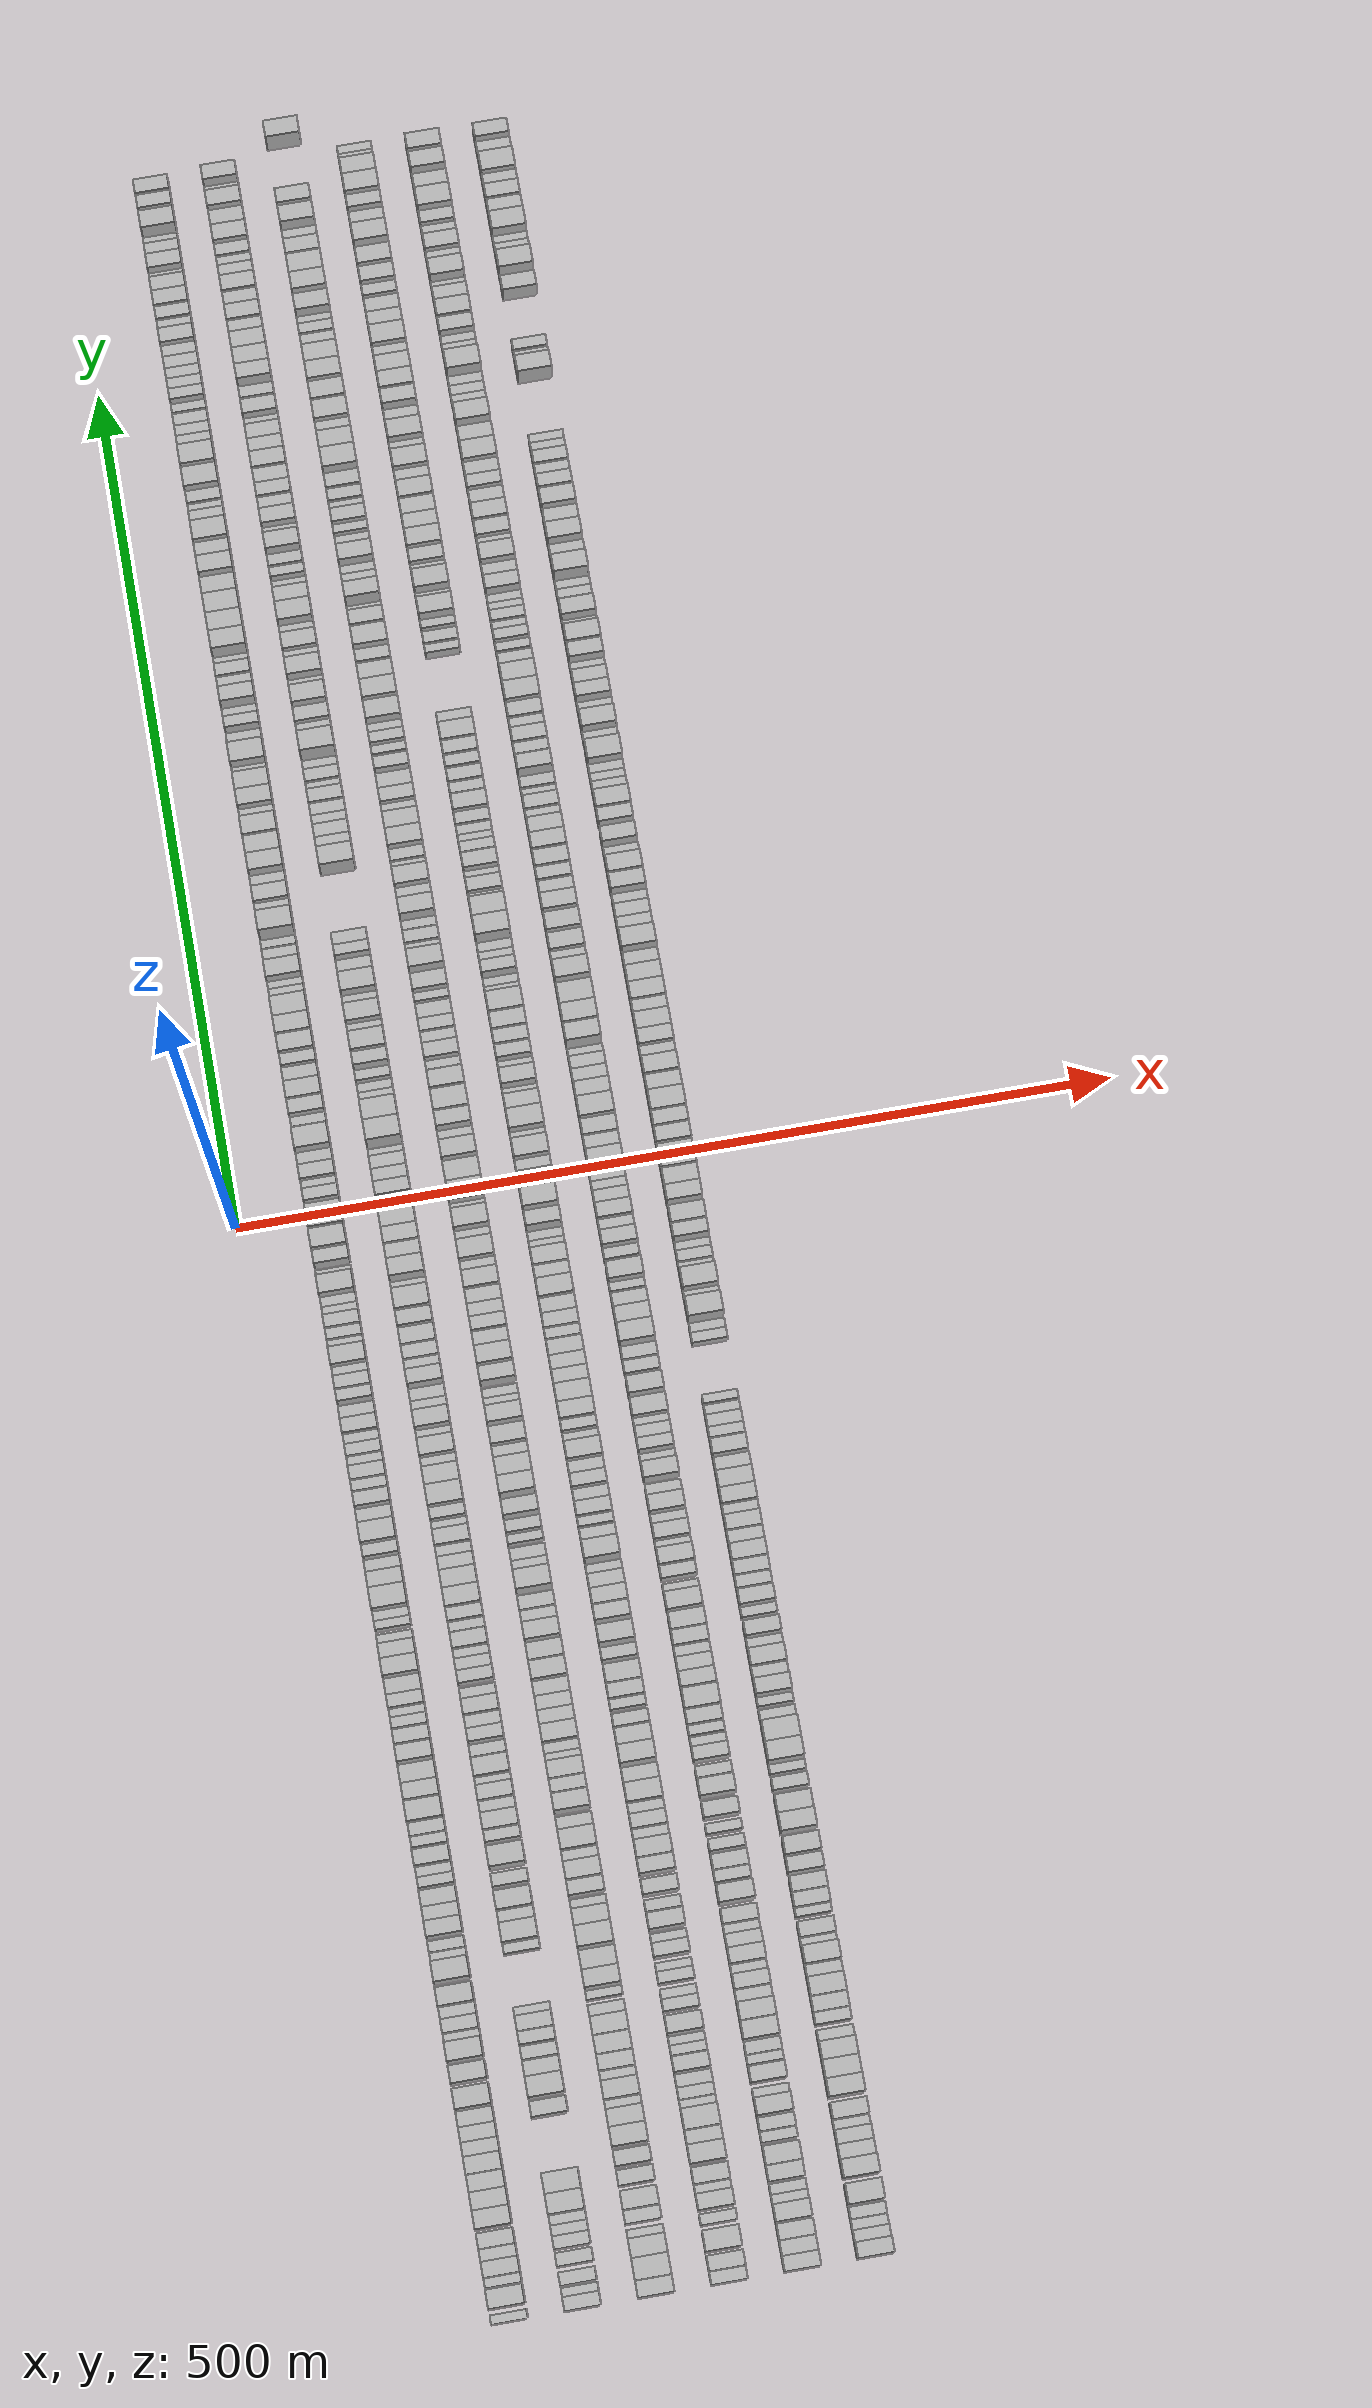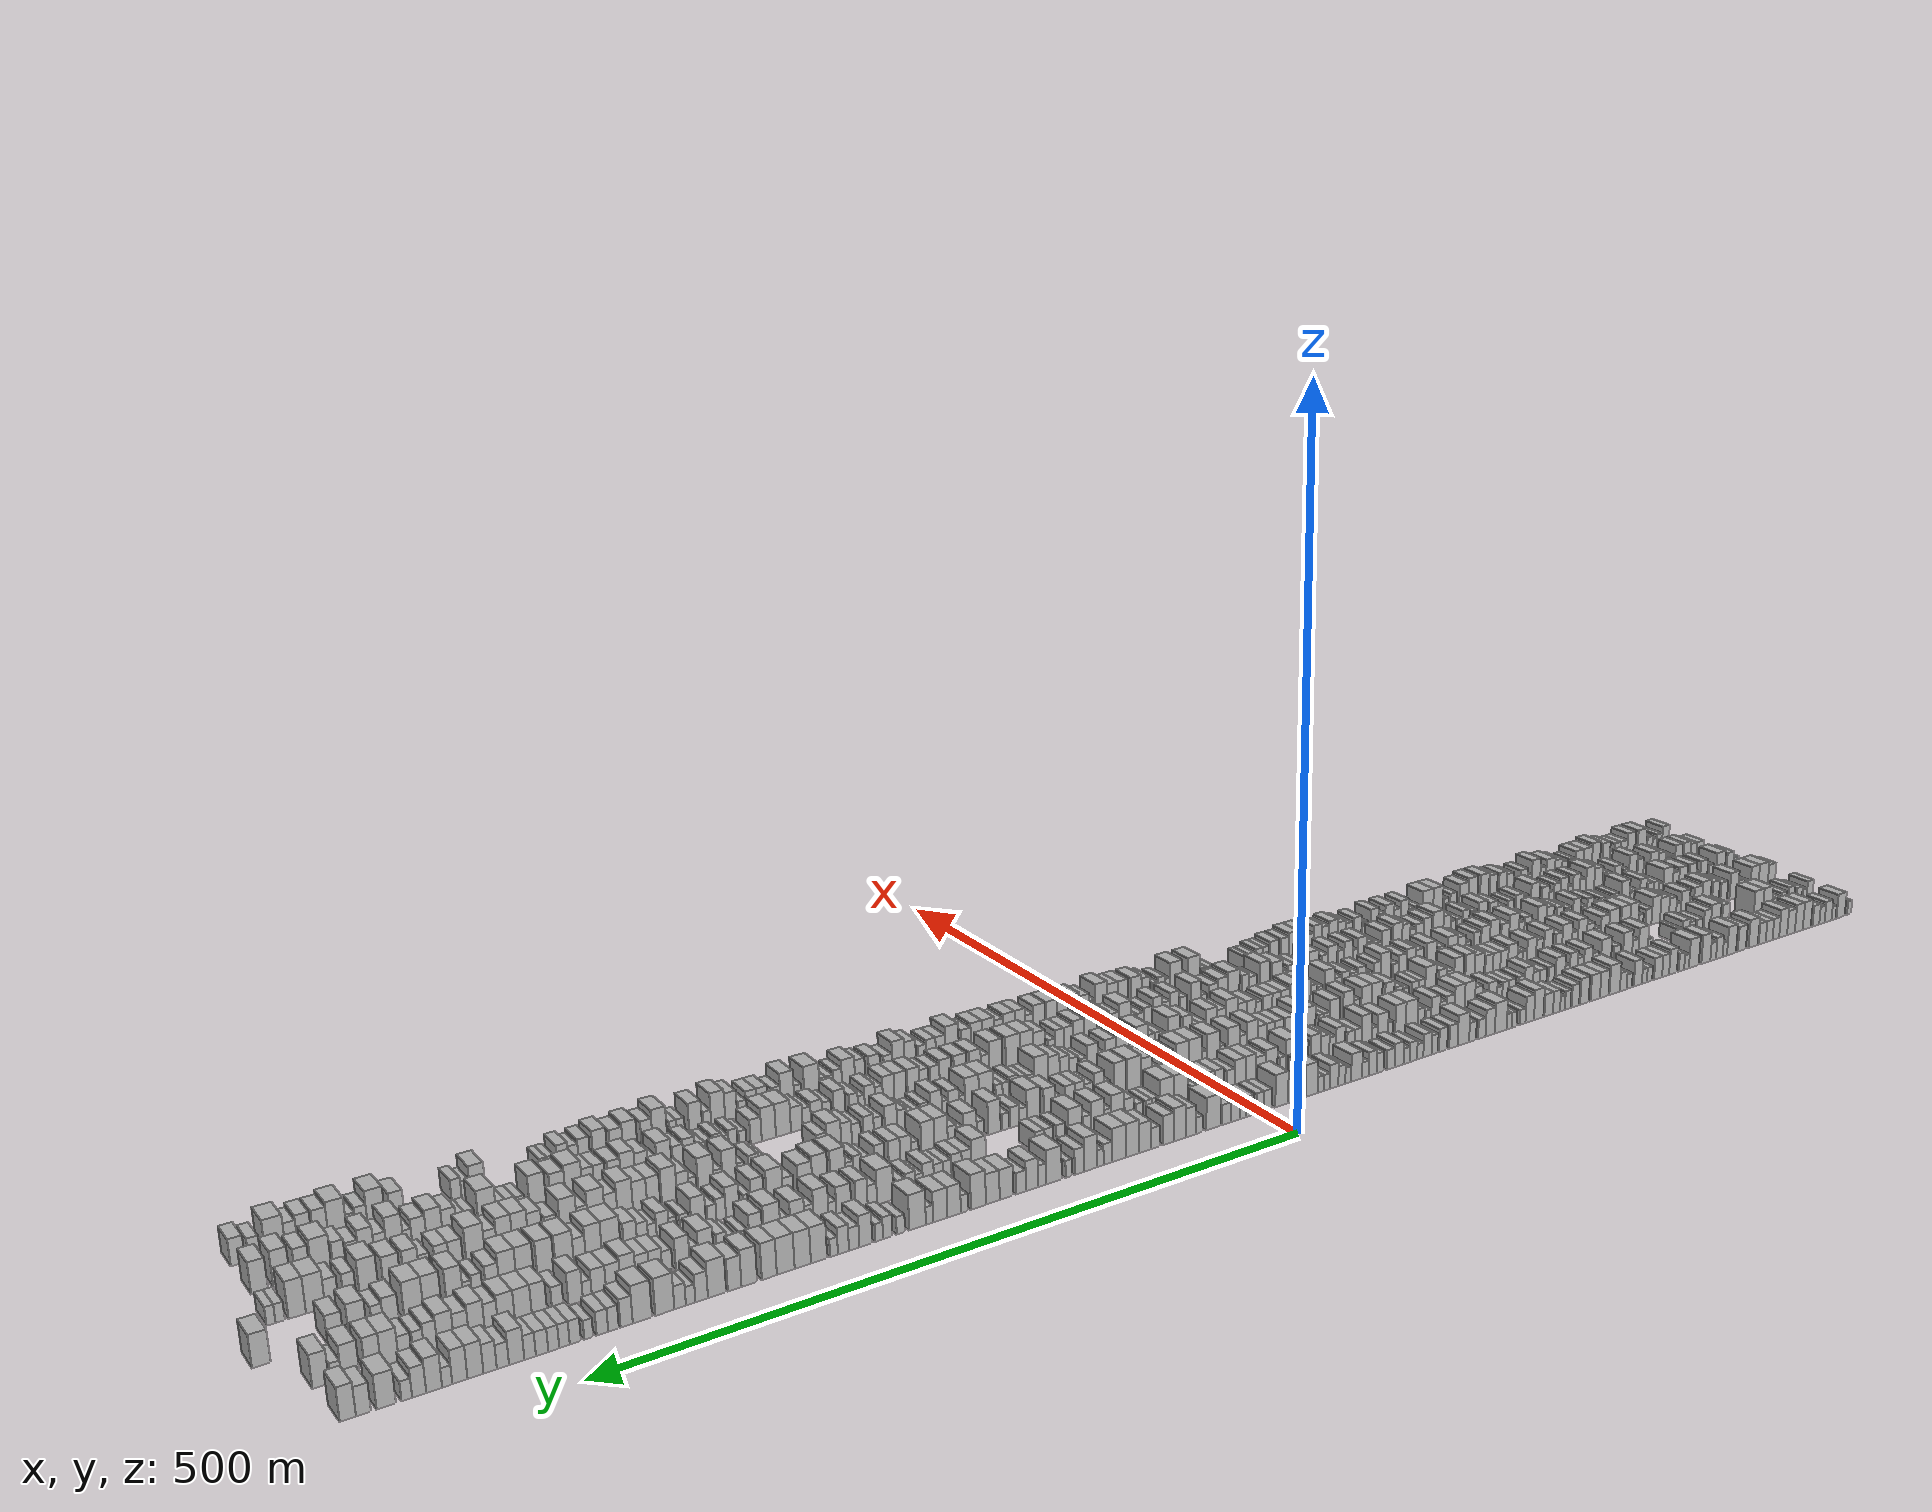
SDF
<sdf version="1.6">
 <world name="default">
  <scene>
   <sky><clouds><speed>12</speed></clouds></sky>
   <ambient>0.4 0.4 0.4 1</ambient>
   <background>0.7 0.7 0.7 1</background>
   <shadows>1</shadows>
  </scene>
  <gravity>0 0 -9.8066</gravity>
  <magnetic_field>6e-06 2.3e-05 -4.2e-05</magnetic_field>
  <physics default="0" name="default_physics" type="ode">
   <ode>
    <solver>
     <type>quick</type>
     <iters>10</iters>
     <sor>1.0</sor>
     <use_dynamic_moi_rescaling>0</use_dynamic_moi_rescaling>
    </solver>
    <constraints>
     <cfm>0</cfm>
     <erp>0.2</erp>
     <contact_max_correcting_vel>100</contact_max_correcting_vel>
     <contact_surface_layer>0.001</contact_surface_layer>
    </constraints>
   </ode>
   <max_step_size>0.004</max_step_size>
   <real_time_factor>1</real_time_factor>
   <real_time_update_rate>250</real_time_update_rate>
  </physics>
  <light name="sun" type="directional">
   <pose>0 0 10 0 0 0</pose>
   <diffuse>0.8 0.8 0.8 1</diffuse>
   <specular>0.2 0.2 0.2 1</specular>
   <attenuation>
    <range>1000</range>
    <constant>0.9</constant>
    <linear>0.01</linear>
    <quadratic>0.001</quadratic>
   </attenuation>
   <direction>-0.5 0.1 -0.9</direction>
  </light>
  <model name="building_1">
   <static>1</static>
   <pose>50.0000 -617.4628 0 0.000000 0.000000 0.000000</pose>
   <link name="link">
    <pose>0 0 6.00 0 0 0</pose>
    <collision name="collision"><geometry><box><size>20.0000 5.0744 12.0000</size></box></geometry></collision>
    <visual name="visual">
     <cast_shadows>0</cast_shadows>
     <geometry><box><size>20.0000 5.0744 12.0000</size></box></geometry>
     <material>
      <script>
       <uri>model://HANNAS_wall/materials/scripts</uri>
       <uri>model://HANNAS_wall/materials/textures</uri>
       <name>vrc/HANNAS_wall</name>
      </script>
     </material>
    </visual>
   </link>
  </model>
  <model name="building_2">
   <static>1</static>
   <pose>50.0000 -606.7021 0 0.000000 0.000000 0.000000</pose>
   <link name="link">
    <pose>0 0 10.50 0 0 0</pose>
    <collision name="collision"><geometry><box><size>20.0000 10.4470 21.0000</size></box></geometry></collision>
    <visual name="visual">
     <cast_shadows>0</cast_shadows>
     <geometry><box><size>20.0000 10.4470 21.0000</size></box></geometry>
     <material>
      <script>
       <uri>model://HANNAS_wall/materials/scripts</uri>
       <uri>model://HANNAS_wall/materials/textures</uri>
       <name>vrc/HANNAS_wall</name>
      </script>
     </material>
    </visual>
   </link>
  </model>
  <model name="building_3">
   <static>1</static>
   <pose>50.0000 -597.8250 0 0.000000 0.000000 0.000000</pose>
   <link name="link">
    <pose>0 0 6.00 0 0 0</pose>
    <collision name="collision"><geometry><box><size>20.0000 5.3073 12.0000</size></box></geometry></collision>
    <visual name="visual">
     <cast_shadows>0</cast_shadows>
     <geometry><box><size>20.0000 5.3073 12.0000</size></box></geometry>
     <material>
      <script>
       <uri>model://HANNAS_wall/materials/scripts</uri>
       <uri>model://HANNAS_wall/materials/textures</uri>
       <name>vrc/HANNAS_wall</name>
      </script>
     </material>
    </visual>
   </link>
  </model>
  <model name="building_4">
   <static>1</static>
   <pose>50.0000 -590.8013 0 0.000000 0.000000 0.000000</pose>
   <link name="link">
    <pose>0 0 9.00 0 0 0</pose>
    <collision name="collision"><geometry><box><size>20.0000 8.7400 18.0000</size></box></geometry></collision>
    <visual name="visual">
     <cast_shadows>0</cast_shadows>
     <geometry><box><size>20.0000 8.7400 18.0000</size></box></geometry>
     <material>
      <script>
       <uri>model://HANNAS_wall/materials/scripts</uri>
       <uri>model://HANNAS_wall/materials/textures</uri>
       <name>vrc/HANNAS_wall</name>
      </script>
     </material>
    </visual>
   </link>
  </model>
  <model name="building_5">
   <static>1</static>
   <pose>50.0000 -583.0864 0 0.000000 0.000000 0.000000</pose>
   <link name="link">
    <pose>0 0 7.50 0 0 0</pose>
    <collision name="collision"><geometry><box><size>20.0000 6.6898 15.0000</size></box></geometry></collision>
    <visual name="visual">
     <cast_shadows>0</cast_shadows>
     <geometry><box><size>20.0000 6.6898 15.0000</size></box></geometry>
     <material>
      <script>
       <uri>model://HANNAS_wall/materials/scripts</uri>
       <uri>model://HANNAS_wall/materials/textures</uri>
       <name>vrc/HANNAS_wall</name>
      </script>
     </material>
    </visual>
   </link>
  </model>
  <model name="building_6">
   <static>1</static>
   <pose>50.0000 -575.4797 0 0.000000 0.000000 0.000000</pose>
   <link name="link">
    <pose>0 0 9.00 0 0 0</pose>
    <collision name="collision"><geometry><box><size>20.0000 8.5235 18.0000</size></box></geometry></collision>
    <visual name="visual">
     <cast_shadows>0</cast_shadows>
     <geometry><box><size>20.0000 8.5235 18.0000</size></box></geometry>
     <material>
      <script>
       <uri>model://HANNAS_wall/materials/scripts</uri>
       <uri>model://HANNAS_wall/materials/textures</uri>
       <name>vrc/HANNAS_wall</name>
      </script>
     </material>
    </visual>
   </link>
  </model>
  <model name="building_7">
   <static>1</static>
   <pose>50.0000 -564.1815 0 0.000000 0.000000 0.000000</pose>
   <link name="link">
    <pose>0 0 12.00 0 0 0</pose>
    <collision name="collision"><geometry><box><size>20.0000 10.0730 24.0000</size></box></geometry></collision>
    <visual name="visual">
     <cast_shadows>0</cast_shadows>
     <geometry><box><size>20.0000 10.0730 24.0000</size></box></geometry>
     <material>
      <script>
       <uri>model://HANNAS_wall/materials/scripts</uri>
       <uri>model://HANNAS_wall/materials/textures</uri>
       <name>vrc/HANNAS_wall</name>
      </script>
     </material>
    </visual>
   </link>
  </model>
  <model name="building_8">
   <static>1</static>
   <pose>50.0000 -554.2850 0 0.000000 0.000000 0.000000</pose>
   <link name="link">
    <pose>0 0 12.00 0 0 0</pose>
    <collision name="collision"><geometry><box><size>20.0000 9.7198 24.0000</size></box></geometry></collision>
    <visual name="visual">
     <cast_shadows>0</cast_shadows>
     <geometry><box><size>20.0000 9.7198 24.0000</size></box></geometry>
     <material>
      <script>
       <uri>model://HANNAS_wall/materials/scripts</uri>
       <uri>model://HANNAS_wall/materials/textures</uri>
       <name>vrc/HANNAS_wall</name>
      </script>
     </material>
    </visual>
   </link>
  </model>
  <model name="building_9">
   <static>1</static>
   <pose>50.0000 -544.6544 0 0.000000 0.000000 0.000000</pose>
   <link name="link">
    <pose>0 0 10.50 0 0 0</pose>
    <collision name="collision"><geometry><box><size>20.0000 9.5414 21.0000</size></box></geometry></collision>
    <visual name="visual">
     <cast_shadows>0</cast_shadows>
     <geometry><box><size>20.0000 9.5414 21.0000</size></box></geometry>
     <material>
      <script>
       <uri>model://HANNAS_wall/materials/scripts</uri>
       <uri>model://HANNAS_wall/materials/textures</uri>
       <name>vrc/HANNAS_wall</name>
      </script>
     </material>
    </visual>
   </link>
  </model>
  <model name="building_10">
   <static>1</static>
   <pose>50.0000 -535.0592 0 0.000000 0.000000 0.000000</pose>
   <link name="link">
    <pose>0 0 12.00 0 0 0</pose>
    <collision name="collision"><geometry><box><size>20.0000 9.6490 24.0000</size></box></geometry></collision>
    <visual name="visual">
     <cast_shadows>0</cast_shadows>
     <geometry><box><size>20.0000 9.6490 24.0000</size></box></geometry>
     <material>
      <script>
       <uri>model://HANNAS_wall/materials/scripts</uri>
       <uri>model://HANNAS_wall/materials/textures</uri>
       <name>vrc/HANNAS_wall</name>
      </script>
     </material>
    </visual>
   </link>
  </model>
  <model name="building_11">
   <static>1</static>
   <pose>50.0000 -526.2334 0 0.000000 0.000000 0.000000</pose>
   <link name="link">
    <pose>0 0 9.00 0 0 0</pose>
    <collision name="collision"><geometry><box><size>20.0000 8.0027 18.0000</size></box></geometry></collision>
    <visual name="visual">
     <cast_shadows>0</cast_shadows>
     <geometry><box><size>20.0000 8.0027 18.0000</size></box></geometry>
     <material>
      <script>
       <uri>model://HANNAS_wall/materials/scripts</uri>
       <uri>model://HANNAS_wall/materials/textures</uri>
       <name>vrc/HANNAS_wall</name>
      </script>
     </material>
    </visual>
   </link>
  </model>
  <model name="building_12">
   <static>1</static>
   <pose>50.0000 -518.0993 0 0.000000 0.000000 0.000000</pose>
   <link name="link">
    <pose>0 0 9.00 0 0 0</pose>
    <collision name="collision"><geometry><box><size>20.0000 8.2655 18.0000</size></box></geometry></collision>
    <visual name="visual">
     <cast_shadows>0</cast_shadows>
     <geometry><box><size>20.0000 8.2655 18.0000</size></box></geometry>
     <material>
      <script>
       <uri>model://HANNAS_wall/materials/scripts</uri>
       <uri>model://HANNAS_wall/materials/textures</uri>
       <name>vrc/HANNAS_wall</name>
      </script>
     </material>
    </visual>
   </link>
  </model>
  <model name="building_13">
   <static>1</static>
   <pose>50.0000 -509.7399 0 0.000000 0.000000 0.000000</pose>
   <link name="link">
    <pose>0 0 9.00 0 0 0</pose>
    <collision name="collision"><geometry><box><size>20.0000 8.4533 18.0000</size></box></geometry></collision>
    <visual name="visual">
     <cast_shadows>0</cast_shadows>
     <geometry><box><size>20.0000 8.4533 18.0000</size></box></geometry>
     <material>
      <script>
       <uri>model://HANNAS_wall/materials/scripts</uri>
       <uri>model://HANNAS_wall/materials/textures</uri>
       <name>vrc/HANNAS_wall</name>
      </script>
     </material>
    </visual>
   </link>
  </model>
  <model name="building_14">
   <static>1</static>
   <pose>50.0000 -498.9163 0 0.000000 0.000000 0.000000</pose>
   <link name="link">
    <pose>0 0 12.00 0 0 0</pose>
    <collision name="collision"><geometry><box><size>20.0000 11.1939 24.0000</size></box></geometry></collision>
    <visual name="visual">
     <cast_shadows>0</cast_shadows>
     <geometry><box><size>20.0000 11.1939 24.0000</size></box></geometry>
     <material>
      <script>
       <uri>model://HANNAS_wall/materials/scripts</uri>
       <uri>model://HANNAS_wall/materials/textures</uri>
       <name>vrc/HANNAS_wall</name>
      </script>
     </material>
    </visual>
   </link>
  </model>
  <model name="building_15">
   <static>1</static>
   <pose>50.0000 -485.4462 0 0.000000 0.000000 0.000000</pose>
   <link name="link">
    <pose>0 0 10.50 0 0 0</pose>
    <collision name="collision"><geometry><box><size>20.0000 9.7464 21.0000</size></box></geometry></collision>
    <visual name="visual">
     <cast_shadows>0</cast_shadows>
     <geometry><box><size>20.0000 9.7464 21.0000</size></box></geometry>
     <material>
      <script>
       <uri>model://HANNAS_wall/materials/scripts</uri>
       <uri>model://HANNAS_wall/materials/textures</uri>
       <name>vrc/HANNAS_wall</name>
      </script>
     </material>
    </visual>
   </link>
  </model>
  <model name="building_16">
   <static>1</static>
   <pose>50.0000 -473.2641 0 0.000000 0.000000 0.000000</pose>
   <link name="link">
    <pose>0 0 12.00 0 0 0</pose>
    <collision name="collision"><geometry><box><size>20.0000 10.6177 24.0000</size></box></geometry></collision>
    <visual name="visual">
     <cast_shadows>0</cast_shadows>
     <geometry><box><size>20.0000 10.6177 24.0000</size></box></geometry>
     <material>
      <script>
       <uri>model://HANNAS_wall/materials/scripts</uri>
       <uri>model://HANNAS_wall/materials/textures</uri>
       <name>vrc/HANNAS_wall</name>
      </script>
     </material>
    </visual>
   </link>
  </model>
  <model name="building_17">
   <static>1</static>
   <pose>50.0000 -465.4085 0 0.000000 0.000000 0.000000</pose>
   <link name="link">
    <pose>0 0 6.00 0 0 0</pose>
    <collision name="collision"><geometry><box><size>20.0000 5.0936 12.0000</size></box></geometry></collision>
    <visual name="visual">
     <cast_shadows>0</cast_shadows>
     <geometry><box><size>20.0000 5.0936 12.0000</size></box></geometry>
     <material>
      <script>
       <uri>model://HANNAS_wall/materials/scripts</uri>
       <uri>model://HANNAS_wall/materials/textures</uri>
       <name>vrc/HANNAS_wall</name>
      </script>
     </material>
    </visual>
   </link>
  </model>
  <model name="building_18">
   <static>1</static>
   <pose>50.0000 -458.9853 0 0.000000 0.000000 0.000000</pose>
   <link name="link">
    <pose>0 0 9.00 0 0 0</pose>
    <collision name="collision"><geometry><box><size>20.0000 7.7528 18.0000</size></box></geometry></collision>
    <visual name="visual">
     <cast_shadows>0</cast_shadows>
     <geometry><box><size>20.0000 7.7528 18.0000</size></box></geometry>
     <material>
      <script>
       <uri>model://HANNAS_wall/materials/scripts</uri>
       <uri>model://HANNAS_wall/materials/textures</uri>
       <name>vrc/HANNAS_wall</name>
      </script>
     </material>
    </visual>
   </link>
  </model>
  <model name="building_19">
   <static>1</static>
   <pose>50.0000 -451.8215 0 0.000000 0.000000 0.000000</pose>
   <link name="link">
    <pose>0 0 7.50 0 0 0</pose>
    <collision name="collision"><geometry><box><size>20.0000 6.5747 15.0000</size></box></geometry></collision>
    <visual name="visual">
     <cast_shadows>0</cast_shadows>
     <geometry><box><size>20.0000 6.5747 15.0000</size></box></geometry>
     <material>
      <script>
       <uri>model://HANNAS_wall/materials/scripts</uri>
       <uri>model://HANNAS_wall/materials/textures</uri>
       <name>vrc/HANNAS_wall</name>
      </script>
     </material>
    </visual>
   </link>
  </model>
  <model name="building_20">
   <static>1</static>
   <pose>50.0000 -443.3576 0 0.000000 0.000000 0.000000</pose>
   <link name="link">
    <pose>0 0 12.00 0 0 0</pose>
    <collision name="collision"><geometry><box><size>20.0000 10.3531 24.0000</size></box></geometry></collision>
    <visual name="visual">
     <cast_shadows>0</cast_shadows>
     <geometry><box><size>20.0000 10.3531 24.0000</size></box></geometry>
     <material>
      <script>
       <uri>model://HANNAS_wall/materials/scripts</uri>
       <uri>model://HANNAS_wall/materials/textures</uri>
       <name>vrc/HANNAS_wall</name>
      </script>
     </material>
    </visual>
   </link>
  </model>
  <model name="building_21">
   <static>1</static>
   <pose>50.0000 -429.5140 0 0.000000 0.000000 0.000000</pose>
   <link name="link">
    <pose>0 0 12.00 0 0 0</pose>
    <collision name="collision"><geometry><box><size>20.0000 11.3341 24.0000</size></box></geometry></collision>
    <visual name="visual">
     <cast_shadows>0</cast_shadows>
     <geometry><box><size>20.0000 11.3341 24.0000</size></box></geometry>
     <material>
      <script>
       <uri>model://HANNAS_wall/materials/scripts</uri>
       <uri>model://HANNAS_wall/materials/textures</uri>
       <name>vrc/HANNAS_wall</name>
      </script>
     </material>
    </visual>
   </link>
  </model>
  <model name="building_22">
   <static>1</static>
   <pose>50.0000 -421.1750 0 0.000000 0.000000 0.000000</pose>
   <link name="link">
    <pose>0 0 6.00 0 0 0</pose>
    <collision name="collision"><geometry><box><size>20.0000 5.3437 12.0000</size></box></geometry></collision>
    <visual name="visual">
     <cast_shadows>0</cast_shadows>
     <geometry><box><size>20.0000 5.3437 12.0000</size></box></geometry>
     <material>
      <script>
       <uri>model://HANNAS_wall/materials/scripts</uri>
       <uri>model://HANNAS_wall/materials/textures</uri>
       <name>vrc/HANNAS_wall</name>
      </script>
     </material>
    </visual>
   </link>
  </model>
  <model name="building_23">
   <static>1</static>
   <pose>50.0000 -415.4095 0 0.000000 0.000000 0.000000</pose>
   <link name="link">
    <pose>0 0 7.50 0 0 0</pose>
    <collision name="collision"><geometry><box><size>20.0000 6.1874 15.0000</size></box></geometry></collision>
    <visual name="visual">
     <cast_shadows>0</cast_shadows>
     <geometry><box><size>20.0000 6.1874 15.0000</size></box></geometry>
     <material>
      <script>
       <uri>model://HANNAS_wall/materials/scripts</uri>
       <uri>model://HANNAS_wall/materials/textures</uri>
       <name>vrc/HANNAS_wall</name>
      </script>
     </material>
    </visual>
   </link>
  </model>
  <model name="building_24">
   <static>1</static>
   <pose>50.0000 -405.9021 0 0.000000 0.000000 0.000000</pose>
   <link name="link">
    <pose>0 0 10.50 0 0 0</pose>
    <collision name="collision"><geometry><box><size>20.0000 8.8274 21.0000</size></box></geometry></collision>
    <visual name="visual">
     <cast_shadows>0</cast_shadows>
     <geometry><box><size>20.0000 8.8274 21.0000</size></box></geometry>
     <material>
      <script>
       <uri>model://HANNAS_wall/materials/scripts</uri>
       <uri>model://HANNAS_wall/materials/textures</uri>
       <name>vrc/HANNAS_wall</name>
      </script>
     </material>
    </visual>
   </link>
  </model>
  <model name="building_25">
   <static>1</static>
   <pose>50.0000 -397.5313 0 0.000000 0.000000 0.000000</pose>
   <link name="link">
    <pose>0 0 9.00 0 0 0</pose>
    <collision name="collision"><geometry><box><size>20.0000 7.9142 18.0000</size></box></geometry></collision>
    <visual name="visual">
     <cast_shadows>0</cast_shadows>
     <geometry><box><size>20.0000 7.9142 18.0000</size></box></geometry>
     <material>
      <script>
       <uri>model://HANNAS_wall/materials/scripts</uri>
       <uri>model://HANNAS_wall/materials/textures</uri>
       <name>vrc/HANNAS_wall</name>
      </script>
     </material>
    </visual>
   </link>
  </model>
  <model name="building_26">
   <static>1</static>
   <pose>50.0000 -389.0778 0 0.000000 0.000000 0.000000</pose>
   <link name="link">
    <pose>0 0 9.00 0 0 0</pose>
    <collision name="collision"><geometry><box><size>20.0000 8.9928 18.0000</size></box></geometry></collision>
    <visual name="visual">
     <cast_shadows>0</cast_shadows>
     <geometry><box><size>20.0000 8.9928 18.0000</size></box></geometry>
     <material>
      <script>
       <uri>model://HANNAS_wall/materials/scripts</uri>
       <uri>model://HANNAS_wall/materials/textures</uri>
       <name>vrc/HANNAS_wall</name>
      </script>
     </material>
    </visual>
   </link>
  </model>
  <model name="building_27">
   <static>1</static>
   <pose>50.0000 -379.6226 0 0.000000 0.000000 0.000000</pose>
   <link name="link">
    <pose>0 0 6.00 0 0 0</pose>
    <collision name="collision"><geometry><box><size>20.0000 5.9175 12.0000</size></box></geometry></collision>
    <visual name="visual">
     <cast_shadows>0</cast_shadows>
     <geometry><box><size>20.0000 5.9175 12.0000</size></box></geometry>
     <material>
      <script>
       <uri>model://HANNAS_wall/materials/scripts</uri>
       <uri>model://HANNAS_wall/materials/textures</uri>
       <name>vrc/HANNAS_wall</name>
      </script>
     </material>
    </visual>
   </link>
  </model>
  <model name="building_28">
   <static>1</static>
   <pose>50.0000 -373.9000 0 0.000000 0.000000 0.000000</pose>
   <link name="link">
    <pose>0 0 6.00 0 0 0</pose>
    <collision name="collision"><geometry><box><size>20.0000 5.5277 12.0000</size></box></geometry></collision>
    <visual name="visual">
     <cast_shadows>0</cast_shadows>
     <geometry><box><size>20.0000 5.5277 12.0000</size></box></geometry>
     <material>
      <script>
       <uri>model://HANNAS_wall/materials/scripts</uri>
       <uri>model://HANNAS_wall/materials/textures</uri>
       <name>vrc/HANNAS_wall</name>
      </script>
     </material>
    </visual>
   </link>
  </model>
  <model name="building_29">
   <static>1</static>
   <pose>50.0000 -366.6742 0 0.000000 0.000000 0.000000</pose>
   <link name="link">
    <pose>0 0 10.50 0 0 0</pose>
    <collision name="collision"><geometry><box><size>20.0000 8.9239 21.0000</size></box></geometry></collision>
    <visual name="visual">
     <cast_shadows>0</cast_shadows>
     <geometry><box><size>20.0000 8.9239 21.0000</size></box></geometry>
     <material>
      <script>
       <uri>model://HANNAS_wall/materials/scripts</uri>
       <uri>model://HANNAS_wall/materials/textures</uri>
       <name>vrc/HANNAS_wall</name>
      </script>
     </material>
    </visual>
   </link>
  </model>
  <model name="building_30">
   <static>1</static>
   <pose>50.0000 -357.2572 0 0.000000 0.000000 0.000000</pose>
   <link name="link">
    <pose>0 0 6.00 0 0 0</pose>
    <collision name="collision"><geometry><box><size>20.0000 5.9101 12.0000</size></box></geometry></collision>
    <visual name="visual">
     <cast_shadows>0</cast_shadows>
     <geometry><box><size>20.0000 5.9101 12.0000</size></box></geometry>
     <material>
      <script>
       <uri>model://HANNAS_wall/materials/scripts</uri>
       <uri>model://HANNAS_wall/materials/textures</uri>
       <name>vrc/HANNAS_wall</name>
      </script>
     </material>
    </visual>
   </link>
  </model>
  <model name="building_31">
   <static>1</static>
   <pose>50.0000 -350.6123 0 0.000000 0.000000 0.000000</pose>
   <link name="link">
    <pose>0 0 7.50 0 0 0</pose>
    <collision name="collision"><geometry><box><size>20.0000 7.3797 15.0000</size></box></geometry></collision>
    <visual name="visual">
     <cast_shadows>0</cast_shadows>
     <geometry><box><size>20.0000 7.3797 15.0000</size></box></geometry>
     <material>
      <script>
       <uri>model://HANNAS_wall/materials/scripts</uri>
       <uri>model://HANNAS_wall/materials/textures</uri>
       <name>vrc/HANNAS_wall</name>
      </script>
     </material>
    </visual>
   </link>
  </model>
  <model name="building_32">
   <static>1</static>
   <pose>50.0000 -341.3082 0 0.000000 0.000000 0.000000</pose>
   <link name="link">
    <pose>0 0 12.00 0 0 0</pose>
    <collision name="collision"><geometry><box><size>20.0000 11.2284 24.0000</size></box></geometry></collision>
    <visual name="visual">
     <cast_shadows>0</cast_shadows>
     <geometry><box><size>20.0000 11.2284 24.0000</size></box></geometry>
     <material>
      <script>
       <uri>model://HANNAS_wall/materials/scripts</uri>
       <uri>model://HANNAS_wall/materials/textures</uri>
       <name>vrc/HANNAS_wall</name>
      </script>
     </material>
    </visual>
   </link>
  </model>
  <model name="building_33">
   <static>1</static>
   <pose>50.0000 -330.0692 0 0.000000 0.000000 0.000000</pose>
   <link name="link">
    <pose>0 0 10.50 0 0 0</pose>
    <collision name="collision"><geometry><box><size>20.0000 9.2495 21.0000</size></box></geometry></collision>
    <visual name="visual">
     <cast_shadows>0</cast_shadows>
     <geometry><box><size>20.0000 9.2495 21.0000</size></box></geometry>
     <material>
      <script>
       <uri>model://HANNAS_wall/materials/scripts</uri>
       <uri>model://HANNAS_wall/materials/textures</uri>
       <name>vrc/HANNAS_wall</name>
      </script>
     </material>
    </visual>
   </link>
  </model>
  <model name="building_34">
   <static>1</static>
   <pose>50.0000 -320.4527 0 0.000000 0.000000 0.000000</pose>
   <link name="link">
    <pose>0 0 10.50 0 0 0</pose>
    <collision name="collision"><geometry><box><size>20.0000 9.9836 21.0000</size></box></geometry></collision>
    <visual name="visual">
     <cast_shadows>0</cast_shadows>
     <geometry><box><size>20.0000 9.9836 21.0000</size></box></geometry>
     <material>
      <script>
       <uri>model://HANNAS_wall/materials/scripts</uri>
       <uri>model://HANNAS_wall/materials/textures</uri>
       <name>vrc/HANNAS_wall</name>
      </script>
     </material>
    </visual>
   </link>
  </model>
  <model name="building_35">
   <static>1</static>
   <pose>50.0000 -308.9060 0 0.000000 0.000000 0.000000</pose>
   <link name="link">
    <pose>0 0 10.50 0 0 0</pose>
    <collision name="collision"><geometry><box><size>20.0000 9.1098 21.0000</size></box></geometry></collision>
    <visual name="visual">
     <cast_shadows>0</cast_shadows>
     <geometry><box><size>20.0000 9.1098 21.0000</size></box></geometry>
     <material>
      <script>
       <uri>model://HANNAS_wall/materials/scripts</uri>
       <uri>model://HANNAS_wall/materials/textures</uri>
       <name>vrc/HANNAS_wall</name>
      </script>
     </material>
    </visual>
   </link>
  </model>
  <model name="building_36">
   <static>1</static>
   <pose>50.0000 -299.3510 0 0.000000 0.000000 0.000000</pose>
   <link name="link">
    <pose>0 0 9.00 0 0 0</pose>
    <collision name="collision"><geometry><box><size>20.0000 8.0002 18.0000</size></box></geometry></collision>
    <visual name="visual">
     <cast_shadows>0</cast_shadows>
     <geometry><box><size>20.0000 8.0002 18.0000</size></box></geometry>
     <material>
      <script>
       <uri>model://HANNAS_wall/materials/scripts</uri>
       <uri>model://HANNAS_wall/materials/textures</uri>
       <name>vrc/HANNAS_wall</name>
      </script>
     </material>
    </visual>
   </link>
  </model>
  <model name="building_37">
   <static>1</static>
   <pose>50.0000 -291.2949 0 0.000000 0.000000 0.000000</pose>
   <link name="link">
    <pose>0 0 7.50 0 0 0</pose>
    <collision name="collision"><geometry><box><size>20.0000 6.1120 15.0000</size></box></geometry></collision>
    <visual name="visual">
     <cast_shadows>0</cast_shadows>
     <geometry><box><size>20.0000 6.1120 15.0000</size></box></geometry>
     <material>
      <script>
       <uri>model://HANNAS_wall/materials/scripts</uri>
       <uri>model://HANNAS_wall/materials/textures</uri>
       <name>vrc/HANNAS_wall</name>
      </script>
     </material>
    </visual>
   </link>
  </model>
  <model name="building_38">
   <static>1</static>
   <pose>50.0000 -285.7349 0 0.000000 0.000000 0.000000</pose>
   <link name="link">
    <pose>0 0 6.00 0 0 0</pose>
    <collision name="collision"><geometry><box><size>20.0000 5.0080 12.0000</size></box></geometry></collision>
    <visual name="visual">
     <cast_shadows>0</cast_shadows>
     <geometry><box><size>20.0000 5.0080 12.0000</size></box></geometry>
     <material>
      <script>
       <uri>model://HANNAS_wall/materials/scripts</uri>
       <uri>model://HANNAS_wall/materials/textures</uri>
       <name>vrc/HANNAS_wall</name>
      </script>
     </material>
    </visual>
   </link>
  </model>
  <model name="building_39">
   <static>1</static>
   <pose>50.0000 -279.5450 0 0.000000 0.000000 0.000000</pose>
   <link name="link">
    <pose>0 0 9.00 0 0 0</pose>
    <collision name="collision"><geometry><box><size>20.0000 7.3717 18.0000</size></box></geometry></collision>
    <visual name="visual">
     <cast_shadows>0</cast_shadows>
     <geometry><box><size>20.0000 7.3717 18.0000</size></box></geometry>
     <material>
      <script>
       <uri>model://HANNAS_wall/materials/scripts</uri>
       <uri>model://HANNAS_wall/materials/textures</uri>
       <name>vrc/HANNAS_wall</name>
      </script>
     </material>
    </visual>
   </link>
  </model>
  <model name="building_40">
   <static>1</static>
   <pose>50.0000 -271.4269 0 0.000000 0.000000 0.000000</pose>
   <link name="link">
    <pose>0 0 9.00 0 0 0</pose>
    <collision name="collision"><geometry><box><size>20.0000 8.8646 18.0000</size></box></geometry></collision>
    <visual name="visual">
     <cast_shadows>0</cast_shadows>
     <geometry><box><size>20.0000 8.8646 18.0000</size></box></geometry>
     <material>
      <script>
       <uri>model://HANNAS_wall/materials/scripts</uri>
       <uri>model://HANNAS_wall/materials/textures</uri>
       <name>vrc/HANNAS_wall</name>
      </script>
     </material>
    </visual>
   </link>
  </model>
  <model name="building_41">
   <static>1</static>
   <pose>50.0000 -261.1296 0 0.000000 0.000000 0.000000</pose>
   <link name="link">
    <pose>0 0 12.00 0 0 0</pose>
    <collision name="collision"><geometry><box><size>20.0000 9.7300 24.0000</size></box></geometry></collision>
    <visual name="visual">
     <cast_shadows>0</cast_shadows>
     <geometry><box><size>20.0000 9.7300 24.0000</size></box></geometry>
     <material>
      <script>
       <uri>model://HANNAS_wall/materials/scripts</uri>
       <uri>model://HANNAS_wall/materials/textures</uri>
       <name>vrc/HANNAS_wall</name>
      </script>
     </material>
    </visual>
   </link>
  </model>
  <model name="building_42">
   <static>1</static>
   <pose>50.0000 -251.9216 0 0.000000 0.000000 0.000000</pose>
   <link name="link">
    <pose>0 0 10.50 0 0 0</pose>
    <collision name="collision"><geometry><box><size>20.0000 8.6859 21.0000</size></box></geometry></collision>
    <visual name="visual">
     <cast_shadows>0</cast_shadows>
     <geometry><box><size>20.0000 8.6859 21.0000</size></box></geometry>
     <material>
      <script>
       <uri>model://HANNAS_wall/materials/scripts</uri>
       <uri>model://HANNAS_wall/materials/textures</uri>
       <name>vrc/HANNAS_wall</name>
      </script>
     </material>
    </visual>
   </link>
  </model>
  <model name="building_43">
   <static>1</static>
   <pose>50.0000 -244.6372 0 0.000000 0.000000 0.000000</pose>
   <link name="link">
    <pose>0 0 6.00 0 0 0</pose>
    <collision name="collision"><geometry><box><size>20.0000 5.8830 12.0000</size></box></geometry></collision>
    <visual name="visual">
     <cast_shadows>0</cast_shadows>
     <geometry><box><size>20.0000 5.8830 12.0000</size></box></geometry>
     <material>
      <script>
       <uri>model://HANNAS_wall/materials/scripts</uri>
       <uri>model://HANNAS_wall/materials/textures</uri>
       <name>vrc/HANNAS_wall</name>
      </script>
     </material>
    </visual>
   </link>
  </model>
  <model name="building_44">
   <static>1</static>
   <pose>50.0000 -236.2079 0 0.000000 0.000000 0.000000</pose>
   <link name="link">
    <pose>0 0 6.00 0 0 0</pose>
    <collision name="collision"><geometry><box><size>20.0000 4.9757 12.0000</size></box></geometry></collision>
    <visual name="visual">
     <cast_shadows>0</cast_shadows>
     <geometry><box><size>20.0000 4.9757 12.0000</size></box></geometry>
     <material>
      <script>
       <uri>model://HANNAS_wall/materials/scripts</uri>
       <uri>model://HANNAS_wall/materials/textures</uri>
       <name>vrc/HANNAS_wall</name>
      </script>
     </material>
    </visual>
   </link>
  </model>
  <model name="building_45">
   <static>1</static>
   <pose>50.0000 -231.0833 0 0.000000 0.000000 0.000000</pose>
   <link name="link">
    <pose>0 0 6.00 0 0 0</pose>
    <collision name="collision"><geometry><box><size>20.0000 5.2734 12.0000</size></box></geometry></collision>
    <visual name="visual">
     <cast_shadows>0</cast_shadows>
     <geometry><box><size>20.0000 5.2734 12.0000</size></box></geometry>
     <material>
      <script>
       <uri>model://HANNAS_wall/materials/scripts</uri>
       <uri>model://HANNAS_wall/materials/textures</uri>
       <name>vrc/HANNAS_wall</name>
      </script>
     </material>
    </visual>
   </link>
  </model>
  <model name="building_46">
   <static>1</static>
   <pose>50.0000 -222.4965 0 0.000000 0.000000 0.000000</pose>
   <link name="link">
    <pose>0 0 12.00 0 0 0</pose>
    <collision name="collision"><geometry><box><size>20.0000 11.9003 24.0000</size></box></geometry></collision>
    <visual name="visual">
     <cast_shadows>0</cast_shadows>
     <geometry><box><size>20.0000 11.9003 24.0000</size></box></geometry>
     <material>
      <script>
       <uri>model://HANNAS_wall/materials/scripts</uri>
       <uri>model://HANNAS_wall/materials/textures</uri>
       <name>vrc/HANNAS_wall</name>
      </script>
     </material>
    </visual>
   </link>
  </model>
  <model name="building_47">
   <static>1</static>
   <pose>50.0000 -211.9407 0 0.000000 0.000000 0.000000</pose>
   <link name="link">
    <pose>0 0 10.50 0 0 0</pose>
    <collision name="collision"><geometry><box><size>20.0000 9.2112 21.0000</size></box></geometry></collision>
    <visual name="visual">
     <cast_shadows>0</cast_shadows>
     <geometry><box><size>20.0000 9.2112 21.0000</size></box></geometry>
     <material>
      <script>
       <uri>model://HANNAS_wall/materials/scripts</uri>
       <uri>model://HANNAS_wall/materials/textures</uri>
       <name>vrc/HANNAS_wall</name>
      </script>
     </material>
    </visual>
   </link>
  </model>
  <model name="building_48">
   <static>1</static>
   <pose>50.0000 -203.6342 0 0.000000 0.000000 0.000000</pose>
   <link name="link">
    <pose>0 0 7.50 0 0 0</pose>
    <collision name="collision"><geometry><box><size>20.0000 7.4019 15.0000</size></box></geometry></collision>
    <visual name="visual">
     <cast_shadows>0</cast_shadows>
     <geometry><box><size>20.0000 7.4019 15.0000</size></box></geometry>
     <material>
      <script>
       <uri>model://HANNAS_wall/materials/scripts</uri>
       <uri>model://HANNAS_wall/materials/textures</uri>
       <name>vrc/HANNAS_wall</name>
      </script>
     </material>
    </visual>
   </link>
  </model>
  <model name="building_49">
   <static>1</static>
   <pose>50.0000 -194.5378 0 0.000000 0.000000 0.000000</pose>
   <link name="link">
    <pose>0 0 7.50 0 0 0</pose>
    <collision name="collision"><geometry><box><size>20.0000 6.7910 15.0000</size></box></geometry></collision>
    <visual name="visual">
     <cast_shadows>0</cast_shadows>
     <geometry><box><size>20.0000 6.7910 15.0000</size></box></geometry>
     <material>
      <script>
       <uri>model://HANNAS_wall/materials/scripts</uri>
       <uri>model://HANNAS_wall/materials/textures</uri>
       <name>vrc/HANNAS_wall</name>
      </script>
     </material>
    </visual>
   </link>
  </model>
  <model name="building_50">
   <static>1</static>
   <pose>50.0000 -185.4857 0 0.000000 0.000000 0.000000</pose>
   <link name="link">
    <pose>0 0 12.00 0 0 0</pose>
    <collision name="collision"><geometry><box><size>20.0000 11.3131 24.0000</size></box></geometry></collision>
    <visual name="visual">
     <cast_shadows>0</cast_shadows>
     <geometry><box><size>20.0000 11.3131 24.0000</size></box></geometry>
     <material>
      <script>
       <uri>model://HANNAS_wall/materials/scripts</uri>
       <uri>model://HANNAS_wall/materials/textures</uri>
       <name>vrc/HANNAS_wall</name>
      </script>
     </material>
    </visual>
   </link>
  </model>
  <model name="building_51">
   <static>1</static>
   <pose>50.0000 -175.7561 0 0.000000 0.000000 0.000000</pose>
   <link name="link">
    <pose>0 0 9.00 0 0 0</pose>
    <collision name="collision"><geometry><box><size>20.0000 8.1462 18.0000</size></box></geometry></collision>
    <visual name="visual">
     <cast_shadows>0</cast_shadows>
     <geometry><box><size>20.0000 8.1462 18.0000</size></box></geometry>
     <material>
      <script>
       <uri>model://HANNAS_wall/materials/scripts</uri>
       <uri>model://HANNAS_wall/materials/textures</uri>
       <name>vrc/HANNAS_wall</name>
      </script>
     </material>
    </visual>
   </link>
  </model>
  <model name="building_52">
   <static>1</static>
   <pose>50.0000 -165.7284 0 0.000000 0.000000 0.000000</pose>
   <link name="link">
    <pose>0 0 9.00 0 0 0</pose>
    <collision name="collision"><geometry><box><size>20.0000 7.9092 18.0000</size></box></geometry></collision>
    <visual name="visual">
     <cast_shadows>0</cast_shadows>
     <geometry><box><size>20.0000 7.9092 18.0000</size></box></geometry>
     <material>
      <script>
       <uri>model://HANNAS_wall/materials/scripts</uri>
       <uri>model://HANNAS_wall/materials/textures</uri>
       <name>vrc/HANNAS_wall</name>
      </script>
     </material>
    </visual>
   </link>
  </model>
  <model name="building_53">
   <static>1</static>
   <pose>50.0000 -157.7359 0 0.000000 0.000000 0.000000</pose>
   <link name="link">
    <pose>0 0 7.50 0 0 0</pose>
    <collision name="collision"><geometry><box><size>20.0000 6.0759 15.0000</size></box></geometry></collision>
    <visual name="visual">
     <cast_shadows>0</cast_shadows>
     <geometry><box><size>20.0000 6.0759 15.0000</size></box></geometry>
     <material>
      <script>
       <uri>model://HANNAS_wall/materials/scripts</uri>
       <uri>model://HANNAS_wall/materials/textures</uri>
       <name>vrc/HANNAS_wall</name>
      </script>
     </material>
    </visual>
   </link>
  </model>
  <model name="building_54">
   <static>1</static>
   <pose>50.0000 -150.7229 0 0.000000 0.000000 0.000000</pose>
   <link name="link">
    <pose>0 0 9.00 0 0 0</pose>
    <collision name="collision"><geometry><box><size>20.0000 7.9500 18.0000</size></box></geometry></collision>
    <visual name="visual">
     <cast_shadows>0</cast_shadows>
     <geometry><box><size>20.0000 7.9500 18.0000</size></box></geometry>
     <material>
      <script>
       <uri>model://HANNAS_wall/materials/scripts</uri>
       <uri>model://HANNAS_wall/materials/textures</uri>
       <name>vrc/HANNAS_wall</name>
      </script>
     </material>
    </visual>
   </link>
  </model>
  <model name="building_55">
   <static>1</static>
   <pose>50.0000 -143.7627 0 0.000000 0.000000 0.000000</pose>
   <link name="link">
    <pose>0 0 6.00 0 0 0</pose>
    <collision name="collision"><geometry><box><size>20.0000 5.9704 12.0000</size></box></geometry></collision>
    <visual name="visual">
     <cast_shadows>0</cast_shadows>
     <geometry><box><size>20.0000 5.9704 12.0000</size></box></geometry>
     <material>
      <script>
       <uri>model://HANNAS_wall/materials/scripts</uri>
       <uri>model://HANNAS_wall/materials/textures</uri>
       <name>vrc/HANNAS_wall</name>
      </script>
     </material>
    </visual>
   </link>
  </model>
  <model name="building_56">
   <static>1</static>
   <pose>50.0000 -137.3527 0 0.000000 0.000000 0.000000</pose>
   <link name="link">
    <pose>0 0 7.50 0 0 0</pose>
    <collision name="collision"><geometry><box><size>20.0000 6.8496 15.0000</size></box></geometry></collision>
    <visual name="visual">
     <cast_shadows>0</cast_shadows>
     <geometry><box><size>20.0000 6.8496 15.0000</size></box></geometry>
     <material>
      <script>
       <uri>model://HANNAS_wall/materials/scripts</uri>
       <uri>model://HANNAS_wall/materials/textures</uri>
       <name>vrc/HANNAS_wall</name>
      </script>
     </material>
    </visual>
   </link>
  </model>
  <model name="building_57">
   <static>1</static>
   <pose>50.0000 -130.9528 0 0.000000 0.000000 0.000000</pose>
   <link name="link">
    <pose>0 0 6.00 0 0 0</pose>
    <collision name="collision"><geometry><box><size>20.0000 5.9501 12.0000</size></box></geometry></collision>
    <visual name="visual">
     <cast_shadows>0</cast_shadows>
     <geometry><box><size>20.0000 5.9501 12.0000</size></box></geometry>
     <material>
      <script>
       <uri>model://HANNAS_wall/materials/scripts</uri>
       <uri>model://HANNAS_wall/materials/textures</uri>
       <name>vrc/HANNAS_wall</name>
      </script>
     </material>
    </visual>
   </link>
  </model>
  <model name="building_58">
   <static>1</static>
   <pose>50.0000 -123.8295 0 0.000000 0.000000 0.000000</pose>
   <link name="link">
    <pose>0 0 9.00 0 0 0</pose>
    <collision name="collision"><geometry><box><size>20.0000 8.2965 18.0000</size></box></geometry></collision>
    <visual name="visual">
     <cast_shadows>0</cast_shadows>
     <geometry><box><size>20.0000 8.2965 18.0000</size></box></geometry>
     <material>
      <script>
       <uri>model://HANNAS_wall/materials/scripts</uri>
       <uri>model://HANNAS_wall/materials/textures</uri>
       <name>vrc/HANNAS_wall</name>
      </script>
     </material>
    </visual>
   </link>
  </model>
  <model name="building_59">
   <static>1</static>
   <pose>50.0000 -116.0347 0 0.000000 0.000000 0.000000</pose>
   <link name="link">
    <pose>0 0 7.50 0 0 0</pose>
    <collision name="collision"><geometry><box><size>20.0000 7.2932 15.0000</size></box></geometry></collision>
    <visual name="visual">
     <cast_shadows>0</cast_shadows>
     <geometry><box><size>20.0000 7.2932 15.0000</size></box></geometry>
     <material>
      <script>
       <uri>model://HANNAS_wall/materials/scripts</uri>
       <uri>model://HANNAS_wall/materials/textures</uri>
       <name>vrc/HANNAS_wall</name>
      </script>
     </material>
    </visual>
   </link>
  </model>
  <model name="building_60">
   <static>1</static>
   <pose>50.0000 -106.1025 0 0.000000 0.000000 0.000000</pose>
   <link name="link">
    <pose>0 0 7.50 0 0 0</pose>
    <collision name="collision"><geometry><box><size>20.0000 6.5712 15.0000</size></box></geometry></collision>
    <visual name="visual">
     <cast_shadows>0</cast_shadows>
     <geometry><box><size>20.0000 6.5712 15.0000</size></box></geometry>
     <material>
      <script>
       <uri>model://HANNAS_wall/materials/scripts</uri>
       <uri>model://HANNAS_wall/materials/textures</uri>
       <name>vrc/HANNAS_wall</name>
      </script>
     </material>
    </visual>
   </link>
  </model>
  <model name="building_61">
   <static>1</static>
   <pose>50.0000 -99.1050 0 0.000000 0.000000 0.000000</pose>
   <link name="link">
    <pose>0 0 9.00 0 0 0</pose>
    <collision name="collision"><geometry><box><size>20.0000 7.4237 18.0000</size></box></geometry></collision>
    <visual name="visual">
     <cast_shadows>0</cast_shadows>
     <geometry><box><size>20.0000 7.4237 18.0000</size></box></geometry>
     <material>
      <script>
       <uri>model://HANNAS_wall/materials/scripts</uri>
       <uri>model://HANNAS_wall/materials/textures</uri>
       <name>vrc/HANNAS_wall</name>
      </script>
     </material>
    </visual>
   </link>
  </model>
  <model name="building_62">
   <static>1</static>
   <pose>50.0000 -92.4383 0 0.000000 0.000000 0.000000</pose>
   <link name="link">
    <pose>0 0 6.00 0 0 0</pose>
    <collision name="collision"><geometry><box><size>20.0000 5.9098 12.0000</size></box></geometry></collision>
    <visual name="visual">
     <cast_shadows>0</cast_shadows>
     <geometry><box><size>20.0000 5.9098 12.0000</size></box></geometry>
     <material>
      <script>
       <uri>model://HANNAS_wall/materials/scripts</uri>
       <uri>model://HANNAS_wall/materials/textures</uri>
       <name>vrc/HANNAS_wall</name>
      </script>
     </material>
    </visual>
   </link>
  </model>
  <model name="building_63">
   <static>1</static>
   <pose>50.0000 -84.4412 0 0.000000 0.000000 0.000000</pose>
   <link name="link">
    <pose>0 0 10.50 0 0 0</pose>
    <collision name="collision"><geometry><box><size>20.0000 10.0844 21.0000</size></box></geometry></collision>
    <visual name="visual">
     <cast_shadows>0</cast_shadows>
     <geometry><box><size>20.0000 10.0844 21.0000</size></box></geometry>
     <material>
      <script>
       <uri>model://HANNAS_wall/materials/scripts</uri>
       <uri>model://HANNAS_wall/materials/textures</uri>
       <name>vrc/HANNAS_wall</name>
      </script>
     </material>
    </visual>
   </link>
  </model>
  <model name="building_64">
   <static>1</static>
   <pose>50.0000 -76.7588 0 0.000000 0.000000 0.000000</pose>
   <link name="link">
    <pose>0 0 6.00 0 0 0</pose>
    <collision name="collision"><geometry><box><size>20.0000 5.2803 12.0000</size></box></geometry></collision>
    <visual name="visual">
     <cast_shadows>0</cast_shadows>
     <geometry><box><size>20.0000 5.2803 12.0000</size></box></geometry>
     <material>
      <script>
       <uri>model://HANNAS_wall/materials/scripts</uri>
       <uri>model://HANNAS_wall/materials/textures</uri>
       <name>vrc/HANNAS_wall</name>
      </script>
     </material>
    </visual>
   </link>
  </model>
  <model name="building_65">
   <static>1</static>
   <pose>50.0000 -70.9563 0 0.000000 0.000000 0.000000</pose>
   <link name="link">
    <pose>0 0 7.50 0 0 0</pose>
    <collision name="collision"><geometry><box><size>20.0000 6.3248 15.0000</size></box></geometry></collision>
    <visual name="visual">
     <cast_shadows>0</cast_shadows>
     <geometry><box><size>20.0000 6.3248 15.0000</size></box></geometry>
     <material>
      <script>
       <uri>model://HANNAS_wall/materials/scripts</uri>
       <uri>model://HANNAS_wall/materials/textures</uri>
       <name>vrc/HANNAS_wall</name>
      </script>
     </material>
    </visual>
   </link>
  </model>
  <model name="building_66">
   <static>1</static>
   <pose>50.0000 -64.0385 0 0.000000 0.000000 0.000000</pose>
   <link name="link">
    <pose>0 0 9.00 0 0 0</pose>
    <collision name="collision"><geometry><box><size>20.0000 7.5108 18.0000</size></box></geometry></collision>
    <visual name="visual">
     <cast_shadows>0</cast_shadows>
     <geometry><box><size>20.0000 7.5108 18.0000</size></box></geometry>
     <material>
      <script>
       <uri>model://HANNAS_wall/materials/scripts</uri>
       <uri>model://HANNAS_wall/materials/textures</uri>
       <name>vrc/HANNAS_wall</name>
      </script>
     </material>
    </visual>
   </link>
  </model>
  <model name="building_67">
   <static>1</static>
   <pose>50.0000 -57.5866 0 0.000000 0.000000 0.000000</pose>
   <link name="link">
    <pose>0 0 6.00 0 0 0</pose>
    <collision name="collision"><geometry><box><size>20.0000 5.3930 12.0000</size></box></geometry></collision>
    <visual name="visual">
     <cast_shadows>0</cast_shadows>
     <geometry><box><size>20.0000 5.3930 12.0000</size></box></geometry>
     <material>
      <script>
       <uri>model://HANNAS_wall/materials/scripts</uri>
       <uri>model://HANNAS_wall/materials/textures</uri>
       <name>vrc/HANNAS_wall</name>
      </script>
     </material>
    </visual>
   </link>
  </model>
  <model name="building_68">
   <static>1</static>
   <pose>50.0000 -52.0692 0 0.000000 0.000000 0.000000</pose>
   <link name="link">
    <pose>0 0 6.00 0 0 0</pose>
    <collision name="collision"><geometry><box><size>20.0000 5.6418 12.0000</size></box></geometry></collision>
    <visual name="visual">
     <cast_shadows>0</cast_shadows>
     <geometry><box><size>20.0000 5.6418 12.0000</size></box></geometry>
     <material>
      <script>
       <uri>model://HANNAS_wall/materials/scripts</uri>
       <uri>model://HANNAS_wall/materials/textures</uri>
       <name>vrc/HANNAS_wall</name>
      </script>
     </material>
    </visual>
   </link>
  </model>
  <model name="building_69">
   <static>1</static>
   <pose>50.0000 -43.9307 0 0.000000 0.000000 0.000000</pose>
   <link name="link">
    <pose>0 0 12.00 0 0 0</pose>
    <collision name="collision"><geometry><box><size>20.0000 10.6352 24.0000</size></box></geometry></collision>
    <visual name="visual">
     <cast_shadows>0</cast_shadows>
     <geometry><box><size>20.0000 10.6352 24.0000</size></box></geometry>
     <material>
      <script>
       <uri>model://HANNAS_wall/materials/scripts</uri>
       <uri>model://HANNAS_wall/materials/textures</uri>
       <name>vrc/HANNAS_wall</name>
      </script>
     </material>
    </visual>
   </link>
  </model>
  <model name="building_70">
   <static>1</static>
   <pose>50.0000 -36.2061 0 0.000000 0.000000 0.000000</pose>
   <link name="link">
    <pose>0 0 6.00 0 0 0</pose>
    <collision name="collision"><geometry><box><size>20.0000 4.8141 12.0000</size></box></geometry></collision>
    <visual name="visual">
     <cast_shadows>0</cast_shadows>
     <geometry><box><size>20.0000 4.8141 12.0000</size></box></geometry>
     <material>
      <script>
       <uri>model://HANNAS_wall/materials/scripts</uri>
       <uri>model://HANNAS_wall/materials/textures</uri>
       <name>vrc/HANNAS_wall</name>
      </script>
     </material>
    </visual>
   </link>
  </model>
  <model name="building_71">
   <static>1</static>
   <pose>50.0000 -26.9461 0 0.000000 0.000000 0.000000</pose>
   <link name="link">
    <pose>0 0 9.00 0 0 0</pose>
    <collision name="collision"><geometry><box><size>20.0000 7.7059 18.0000</size></box></geometry></collision>
    <visual name="visual">
     <cast_shadows>0</cast_shadows>
     <geometry><box><size>20.0000 7.7059 18.0000</size></box></geometry>
     <material>
      <script>
       <uri>model://HANNAS_wall/materials/scripts</uri>
       <uri>model://HANNAS_wall/materials/textures</uri>
       <name>vrc/HANNAS_wall</name>
      </script>
     </material>
    </visual>
   </link>
  </model>
  <model name="building_72">
   <static>1</static>
   <pose>50.0000 -17.5170 0 0.000000 0.000000 0.000000</pose>
   <link name="link">
    <pose>0 0 12.00 0 0 0</pose>
    <collision name="collision"><geometry><box><size>20.0000 11.1522 24.0000</size></box></geometry></collision>
    <visual name="visual">
     <cast_shadows>0</cast_shadows>
     <geometry><box><size>20.0000 11.1522 24.0000</size></box></geometry>
     <material>
      <script>
       <uri>model://HANNAS_wall/materials/scripts</uri>
       <uri>model://HANNAS_wall/materials/textures</uri>
       <name>vrc/HANNAS_wall</name>
      </script>
     </material>
    </visual>
   </link>
  </model>
  <model name="building_73">
   <static>1</static>
   <pose>50.0000 -5.6154 0 0.000000 0.000000 0.000000</pose>
   <link name="link">
    <pose>0 0 7.50 0 0 0</pose>
    <collision name="collision"><geometry><box><size>20.0000 6.6509 15.0000</size></box></geometry></collision>
    <visual name="visual">
     <cast_shadows>0</cast_shadows>
     <geometry><box><size>20.0000 6.6509 15.0000</size></box></geometry>
     <material>
      <script>
       <uri>model://HANNAS_wall/materials/scripts</uri>
       <uri>model://HANNAS_wall/materials/textures</uri>
       <name>vrc/HANNAS_wall</name>
      </script>
     </material>
    </visual>
   </link>
  </model>
  <model name="building_74">
   <static>1</static>
   <pose>50.0000 1.0127 0 0.000000 0.000000 0.000000</pose>
   <link name="link">
    <pose>0 0 7.50 0 0 0</pose>
    <collision name="collision"><geometry><box><size>20.0000 6.6054 15.0000</size></box></geometry></collision>
    <visual name="visual">
     <cast_shadows>0</cast_shadows>
     <geometry><box><size>20.0000 6.6054 15.0000</size></box></geometry>
     <material>
      <script>
       <uri>model://HANNAS_wall/materials/scripts</uri>
       <uri>model://HANNAS_wall/materials/textures</uri>
       <name>vrc/HANNAS_wall</name>
      </script>
     </material>
    </visual>
   </link>
  </model>
  <model name="building_75">
   <static>1</static>
   <pose>50.0000 9.7789 0 0.000000 0.000000 0.000000</pose>
   <link name="link">
    <pose>0 0 7.50 0 0 0</pose>
    <collision name="collision"><geometry><box><size>20.0000 6.9269 15.0000</size></box></geometry></collision>
    <visual name="visual">
     <cast_shadows>0</cast_shadows>
     <geometry><box><size>20.0000 6.9269 15.0000</size></box></geometry>
     <material>
      <script>
       <uri>model://HANNAS_wall/materials/scripts</uri>
       <uri>model://HANNAS_wall/materials/textures</uri>
       <name>vrc/HANNAS_wall</name>
      </script>
     </material>
    </visual>
   </link>
  </model>
  <model name="building_76">
   <static>1</static>
   <pose>50.0000 15.7514 0 0.000000 0.000000 0.000000</pose>
   <link name="link">
    <pose>0 0 6.00 0 0 0</pose>
    <collision name="collision"><geometry><box><size>20.0000 5.0181 12.0000</size></box></geometry></collision>
    <visual name="visual">
     <cast_shadows>0</cast_shadows>
     <geometry><box><size>20.0000 5.0181 12.0000</size></box></geometry>
     <material>
      <script>
       <uri>model://HANNAS_wall/materials/scripts</uri>
       <uri>model://HANNAS_wall/materials/textures</uri>
       <name>vrc/HANNAS_wall</name>
      </script>
     </material>
    </visual>
   </link>
  </model>
  <model name="building_77">
   <static>1</static>
   <pose>50.0000 22.3753 0 0.000000 0.000000 0.000000</pose>
   <link name="link">
    <pose>0 0 9.00 0 0 0</pose>
    <collision name="collision"><geometry><box><size>20.0000 8.2296 18.0000</size></box></geometry></collision>
    <visual name="visual">
     <cast_shadows>0</cast_shadows>
     <geometry><box><size>20.0000 8.2296 18.0000</size></box></geometry>
     <material>
      <script>
       <uri>model://HANNAS_wall/materials/scripts</uri>
       <uri>model://HANNAS_wall/materials/textures</uri>
       <name>vrc/HANNAS_wall</name>
      </script>
     </material>
    </visual>
   </link>
  </model>
  <model name="building_78">
   <static>1</static>
   <pose>50.0000 30.1486 0 0.000000 0.000000 0.000000</pose>
   <link name="link">
    <pose>0 0 7.50 0 0 0</pose>
    <collision name="collision"><geometry><box><size>20.0000 7.3172 15.0000</size></box></geometry></collision>
    <visual name="visual">
     <cast_shadows>0</cast_shadows>
     <geometry><box><size>20.0000 7.3172 15.0000</size></box></geometry>
     <material>
      <script>
       <uri>model://HANNAS_wall/materials/scripts</uri>
       <uri>model://HANNAS_wall/materials/textures</uri>
       <name>vrc/HANNAS_wall</name>
      </script>
     </material>
    </visual>
   </link>
  </model>
  <model name="building_79">
   <static>1</static>
   <pose>50.0000 40.7831 0 0.000000 0.000000 0.000000</pose>
   <link name="link">
    <pose>0 0 12.00 0 0 0</pose>
    <collision name="collision"><geometry><box><size>20.0000 11.9518 24.0000</size></box></geometry></collision>
    <visual name="visual">
     <cast_shadows>0</cast_shadows>
     <geometry><box><size>20.0000 11.9518 24.0000</size></box></geometry>
     <material>
      <script>
       <uri>model://HANNAS_wall/materials/scripts</uri>
       <uri>model://HANNAS_wall/materials/textures</uri>
       <name>vrc/HANNAS_wall</name>
      </script>
     </material>
    </visual>
   </link>
  </model>
  <model name="building_80">
   <static>1</static>
   <pose>50.0000 52.5803 0 0.000000 0.000000 0.000000</pose>
   <link name="link">
    <pose>0 0 6.00 0 0 0</pose>
    <collision name="collision"><geometry><box><size>20.0000 5.6425 12.0000</size></box></geometry></collision>
    <visual name="visual">
     <cast_shadows>0</cast_shadows>
     <geometry><box><size>20.0000 5.6425 12.0000</size></box></geometry>
     <material>
      <script>
       <uri>model://HANNAS_wall/materials/scripts</uri>
       <uri>model://HANNAS_wall/materials/textures</uri>
       <name>vrc/HANNAS_wall</name>
      </script>
     </material>
    </visual>
   </link>
  </model>
  <model name="building_81">
   <static>1</static>
   <pose>50.0000 59.6201 0 0.000000 0.000000 0.000000</pose>
   <link name="link">
    <pose>0 0 10.50 0 0 0</pose>
    <collision name="collision"><geometry><box><size>20.0000 8.4371 21.0000</size></box></geometry></collision>
    <visual name="visual">
     <cast_shadows>0</cast_shadows>
     <geometry><box><size>20.0000 8.4371 21.0000</size></box></geometry>
     <material>
      <script>
       <uri>model://HANNAS_wall/materials/scripts</uri>
       <uri>model://HANNAS_wall/materials/textures</uri>
       <name>vrc/HANNAS_wall</name>
      </script>
     </material>
    </visual>
   </link>
  </model>
  <model name="building_82">
   <static>1</static>
   <pose>50.0000 68.8127 0 0.000000 0.000000 0.000000</pose>
   <link name="link">
    <pose>0 0 12.00 0 0 0</pose>
    <collision name="collision"><geometry><box><size>20.0000 9.9481 24.0000</size></box></geometry></collision>
    <visual name="visual">
     <cast_shadows>0</cast_shadows>
     <geometry><box><size>20.0000 9.9481 24.0000</size></box></geometry>
     <material>
      <script>
       <uri>model://HANNAS_wall/materials/scripts</uri>
       <uri>model://HANNAS_wall/materials/textures</uri>
       <name>vrc/HANNAS_wall</name>
      </script>
     </material>
    </visual>
   </link>
  </model>
  <model name="building_83">
   <static>1</static>
   <pose>50.0000 77.9871 0 0.000000 0.000000 0.000000</pose>
   <link name="link">
    <pose>0 0 10.50 0 0 0</pose>
    <collision name="collision"><geometry><box><size>20.0000 8.4007 21.0000</size></box></geometry></collision>
    <visual name="visual">
     <cast_shadows>0</cast_shadows>
     <geometry><box><size>20.0000 8.4007 21.0000</size></box></geometry>
     <material>
      <script>
       <uri>model://HANNAS_wall/materials/scripts</uri>
       <uri>model://HANNAS_wall/materials/textures</uri>
       <name>vrc/HANNAS_wall</name>
      </script>
     </material>
    </visual>
   </link>
  </model>
  <model name="building_84">
   <static>1</static>
   <pose>50.0000 88.5403 0 0.000000 0.000000 0.000000</pose>
   <link name="link">
    <pose>0 0 7.50 0 0 0</pose>
    <collision name="collision"><geometry><box><size>20.0000 6.7057 15.0000</size></box></geometry></collision>
    <visual name="visual">
     <cast_shadows>0</cast_shadows>
     <geometry><box><size>20.0000 6.7057 15.0000</size></box></geometry>
     <material>
      <script>
       <uri>model://HANNAS_wall/materials/scripts</uri>
       <uri>model://HANNAS_wall/materials/textures</uri>
       <name>vrc/HANNAS_wall</name>
      </script>
     </material>
    </visual>
   </link>
  </model>
  <model name="building_85">
   <static>1</static>
   <pose>50.0000 96.8803 0 0.000000 0.000000 0.000000</pose>
   <link name="link">
    <pose>0 0 10.50 0 0 0</pose>
    <collision name="collision"><geometry><box><size>20.0000 9.9742 21.0000</size></box></geometry></collision>
    <visual name="visual">
     <cast_shadows>0</cast_shadows>
     <geometry><box><size>20.0000 9.9742 21.0000</size></box></geometry>
     <material>
      <script>
       <uri>model://HANNAS_wall/materials/scripts</uri>
       <uri>model://HANNAS_wall/materials/textures</uri>
       <name>vrc/HANNAS_wall</name>
      </script>
     </material>
    </visual>
   </link>
  </model>
  <model name="building_86">
   <static>1</static>
   <pose>50.0000 106.9199 0 0.000000 0.000000 0.000000</pose>
   <link name="link">
    <pose>0 0 12.00 0 0 0</pose>
    <collision name="collision"><geometry><box><size>20.0000 10.1050 24.0000</size></box></geometry></collision>
    <visual name="visual">
     <cast_shadows>0</cast_shadows>
     <geometry><box><size>20.0000 10.1050 24.0000</size></box></geometry>
     <material>
      <script>
       <uri>model://HANNAS_wall/materials/scripts</uri>
       <uri>model://HANNAS_wall/materials/textures</uri>
       <name>vrc/HANNAS_wall</name>
      </script>
     </material>
    </visual>
   </link>
  </model>
  <model name="building_87">
   <static>1</static>
   <pose>50.0000 117.7359 0 0.000000 0.000000 0.000000</pose>
   <link name="link">
    <pose>0 0 12.00 0 0 0</pose>
    <collision name="collision"><geometry><box><size>20.0000 11.5272 24.0000</size></box></geometry></collision>
    <visual name="visual">
     <cast_shadows>0</cast_shadows>
     <geometry><box><size>20.0000 11.5272 24.0000</size></box></geometry>
     <material>
      <script>
       <uri>model://HANNAS_wall/materials/scripts</uri>
       <uri>model://HANNAS_wall/materials/textures</uri>
       <name>vrc/HANNAS_wall</name>
      </script>
     </material>
    </visual>
   </link>
  </model>
  <model name="building_88">
   <static>1</static>
   <pose>50.0000 126.7029 0 0.000000 0.000000 0.000000</pose>
   <link name="link">
    <pose>0 0 7.50 0 0 0</pose>
    <collision name="collision"><geometry><box><size>20.0000 6.4067 15.0000</size></box></geometry></collision>
    <visual name="visual">
     <cast_shadows>0</cast_shadows>
     <geometry><box><size>20.0000 6.4067 15.0000</size></box></geometry>
     <material>
      <script>
       <uri>model://HANNAS_wall/materials/scripts</uri>
       <uri>model://HANNAS_wall/materials/textures</uri>
       <name>vrc/HANNAS_wall</name>
      </script>
     </material>
    </visual>
   </link>
  </model>
  <model name="building_89">
   <static>1</static>
   <pose>50.0000 132.3894 0 0.000000 0.000000 0.000000</pose>
   <link name="link">
    <pose>0 0 6.00 0 0 0</pose>
    <collision name="collision"><geometry><box><size>20.0000 4.9663 12.0000</size></box></geometry></collision>
    <visual name="visual">
     <cast_shadows>0</cast_shadows>
     <geometry><box><size>20.0000 4.9663 12.0000</size></box></geometry>
     <material>
      <script>
       <uri>model://HANNAS_wall/materials/scripts</uri>
       <uri>model://HANNAS_wall/materials/textures</uri>
       <name>vrc/HANNAS_wall</name>
      </script>
     </material>
    </visual>
   </link>
  </model>
  <model name="building_90">
   <static>1</static>
   <pose>50.0000 139.8823 0 0.000000 0.000000 0.000000</pose>
   <link name="link">
    <pose>0 0 12.00 0 0 0</pose>
    <collision name="collision"><geometry><box><size>20.0000 10.0195 24.0000</size></box></geometry></collision>
    <visual name="visual">
     <cast_shadows>0</cast_shadows>
     <geometry><box><size>20.0000 10.0195 24.0000</size></box></geometry>
     <material>
      <script>
       <uri>model://HANNAS_wall/materials/scripts</uri>
       <uri>model://HANNAS_wall/materials/textures</uri>
       <name>vrc/HANNAS_wall</name>
      </script>
     </material>
    </visual>
   </link>
  </model>
  <model name="building_91">
   <static>1</static>
   <pose>50.0000 148.6498 0 0.000000 0.000000 0.000000</pose>
   <link name="link">
    <pose>0 0 9.00 0 0 0</pose>
    <collision name="collision"><geometry><box><size>20.0000 7.5154 18.0000</size></box></geometry></collision>
    <visual name="visual">
     <cast_shadows>0</cast_shadows>
     <geometry><box><size>20.0000 7.5154 18.0000</size></box></geometry>
     <material>
      <script>
       <uri>model://HANNAS_wall/materials/scripts</uri>
       <uri>model://HANNAS_wall/materials/textures</uri>
       <name>vrc/HANNAS_wall</name>
      </script>
     </material>
    </visual>
   </link>
  </model>
  <model name="building_92">
   <static>1</static>
   <pose>50.0000 156.8911 0 0.000000 0.000000 0.000000</pose>
   <link name="link">
    <pose>0 0 6.00 0 0 0</pose>
    <collision name="collision"><geometry><box><size>20.0000 4.9671 12.0000</size></box></geometry></collision>
    <visual name="visual">
     <cast_shadows>0</cast_shadows>
     <geometry><box><size>20.0000 4.9671 12.0000</size></box></geometry>
     <material>
      <script>
       <uri>model://HANNAS_wall/materials/scripts</uri>
       <uri>model://HANNAS_wall/materials/textures</uri>
       <name>vrc/HANNAS_wall</name>
      </script>
     </material>
    </visual>
   </link>
  </model>
  <model name="building_93">
   <static>1</static>
   <pose>50.0000 168.2172 0 0.000000 0.000000 0.000000</pose>
   <link name="link">
    <pose>0 0 12.00 0 0 0</pose>
    <collision name="collision"><geometry><box><size>20.0000 11.6851 24.0000</size></box></geometry></collision>
    <visual name="visual">
     <cast_shadows>0</cast_shadows>
     <geometry><box><size>20.0000 11.6851 24.0000</size></box></geometry>
     <material>
      <script>
       <uri>model://HANNAS_wall/materials/scripts</uri>
       <uri>model://HANNAS_wall/materials/textures</uri>
       <name>vrc/HANNAS_wall</name>
      </script>
     </material>
    </visual>
   </link>
  </model>
  <model name="building_94">
   <static>1</static>
   <pose>50.0000 177.2418 0 0.000000 0.000000 0.000000</pose>
   <link name="link">
    <pose>0 0 7.50 0 0 0</pose>
    <collision name="collision"><geometry><box><size>20.0000 6.3640 15.0000</size></box></geometry></collision>
    <visual name="visual">
     <cast_shadows>0</cast_shadows>
     <geometry><box><size>20.0000 6.3640 15.0000</size></box></geometry>
     <material>
      <script>
       <uri>model://HANNAS_wall/materials/scripts</uri>
       <uri>model://HANNAS_wall/materials/textures</uri>
       <name>vrc/HANNAS_wall</name>
      </script>
     </material>
    </visual>
   </link>
  </model>
  <model name="building_95">
   <static>1</static>
   <pose>50.0000 184.9630 0 0.000000 0.000000 0.000000</pose>
   <link name="link">
    <pose>0 0 10.50 0 0 0</pose>
    <collision name="collision"><geometry><box><size>20.0000 9.0785 21.0000</size></box></geometry></collision>
    <visual name="visual">
     <cast_shadows>0</cast_shadows>
     <geometry><box><size>20.0000 9.0785 21.0000</size></box></geometry>
     <material>
      <script>
       <uri>model://HANNAS_wall/materials/scripts</uri>
       <uri>model://HANNAS_wall/materials/textures</uri>
       <name>vrc/HANNAS_wall</name>
      </script>
     </material>
    </visual>
   </link>
  </model>
  <model name="building_96">
   <static>1</static>
   <pose>50.0000 193.1773 0 0.000000 0.000000 0.000000</pose>
   <link name="link">
    <pose>0 0 7.50 0 0 0</pose>
    <collision name="collision"><geometry><box><size>20.0000 7.3500 15.0000</size></box></geometry></collision>
    <visual name="visual">
     <cast_shadows>0</cast_shadows>
     <geometry><box><size>20.0000 7.3500 15.0000</size></box></geometry>
     <material>
      <script>
       <uri>model://HANNAS_wall/materials/scripts</uri>
       <uri>model://HANNAS_wall/materials/textures</uri>
       <name>vrc/HANNAS_wall</name>
      </script>
     </material>
    </visual>
   </link>
  </model>
  <model name="building_97">
   <static>1</static>
   <pose>50.0000 203.9280 0 0.000000 0.000000 0.000000</pose>
   <link name="link">
    <pose>0 0 10.50 0 0 0</pose>
    <collision name="collision"><geometry><box><size>20.0000 10.1513 21.0000</size></box></geometry></collision>
    <visual name="visual">
     <cast_shadows>0</cast_shadows>
     <geometry><box><size>20.0000 10.1513 21.0000</size></box></geometry>
     <material>
      <script>
       <uri>model://HANNAS_wall/materials/scripts</uri>
       <uri>model://HANNAS_wall/materials/textures</uri>
       <name>vrc/HANNAS_wall</name>
      </script>
     </material>
    </visual>
   </link>
  </model>
  <model name="building_98">
   <static>1</static>
   <pose>50.0000 214.1001 0 0.000000 0.000000 0.000000</pose>
   <link name="link">
    <pose>0 0 10.50 0 0 0</pose>
    <collision name="collision"><geometry><box><size>20.0000 10.1929 21.0000</size></box></geometry></collision>
    <visual name="visual">
     <cast_shadows>0</cast_shadows>
     <geometry><box><size>20.0000 10.1929 21.0000</size></box></geometry>
     <material>
      <script>
       <uri>model://HANNAS_wall/materials/scripts</uri>
       <uri>model://HANNAS_wall/materials/textures</uri>
       <name>vrc/HANNAS_wall</name>
      </script>
     </material>
    </visual>
   </link>
  </model>
  <model name="building_99">
   <static>1</static>
   <pose>50.0000 224.6728 0 0.000000 0.000000 0.000000</pose>
   <link name="link">
    <pose>0 0 12.00 0 0 0</pose>
    <collision name="collision"><geometry><box><size>20.0000 10.9527 24.0000</size></box></geometry></collision>
    <visual name="visual">
     <cast_shadows>0</cast_shadows>
     <geometry><box><size>20.0000 10.9527 24.0000</size></box></geometry>
     <material>
      <script>
       <uri>model://HANNAS_wall/materials/scripts</uri>
       <uri>model://HANNAS_wall/materials/textures</uri>
       <name>vrc/HANNAS_wall</name>
      </script>
     </material>
    </visual>
   </link>
  </model>
  <model name="building_100">
   <static>1</static>
   <pose>50.0000 234.7954 0 0.000000 0.000000 0.000000</pose>
   <link name="link">
    <pose>0 0 6.00 0 0 0</pose>
    <collision name="collision"><geometry><box><size>20.0000 5.2924 12.0000</size></box></geometry></collision>
    <visual name="visual">
     <cast_shadows>0</cast_shadows>
     <geometry><box><size>20.0000 5.2924 12.0000</size></box></geometry>
     <material>
      <script>
       <uri>model://HANNAS_wall/materials/scripts</uri>
       <uri>model://HANNAS_wall/materials/textures</uri>
       <name>vrc/HANNAS_wall</name>
      </script>
     </material>
    </visual>
   </link>
  </model>
  <model name="building_101">
   <static>1</static>
   <pose>50.0000 242.2827 0 0.000000 0.000000 0.000000</pose>
   <link name="link">
    <pose>0 0 10.50 0 0 0</pose>
    <collision name="collision"><geometry><box><size>20.0000 9.6823 21.0000</size></box></geometry></collision>
    <visual name="visual">
     <cast_shadows>0</cast_shadows>
     <geometry><box><size>20.0000 9.6823 21.0000</size></box></geometry>
     <material>
      <script>
       <uri>model://HANNAS_wall/materials/scripts</uri>
       <uri>model://HANNAS_wall/materials/textures</uri>
       <name>vrc/HANNAS_wall</name>
      </script>
     </material>
    </visual>
   </link>
  </model>
  <model name="building_102">
   <static>1</static>
   <pose>50.0000 252.2230 0 0.000000 0.000000 0.000000</pose>
   <link name="link">
    <pose>0 0 10.50 0 0 0</pose>
    <collision name="collision"><geometry><box><size>20.0000 10.1983 21.0000</size></box></geometry></collision>
    <visual name="visual">
     <cast_shadows>0</cast_shadows>
     <geometry><box><size>20.0000 10.1983 21.0000</size></box></geometry>
     <material>
      <script>
       <uri>model://HANNAS_wall/materials/scripts</uri>
       <uri>model://HANNAS_wall/materials/textures</uri>
       <name>vrc/HANNAS_wall</name>
      </script>
     </material>
    </visual>
   </link>
  </model>
  <model name="building_103">
   <static>1</static>
   <pose>50.0000 259.9116 0 0.000000 0.000000 0.000000</pose>
   <link name="link">
    <pose>0 0 6.00 0 0 0</pose>
    <collision name="collision"><geometry><box><size>20.0000 5.1789 12.0000</size></box></geometry></collision>
    <visual name="visual">
     <cast_shadows>0</cast_shadows>
     <geometry><box><size>20.0000 5.1789 12.0000</size></box></geometry>
     <material>
      <script>
       <uri>model://HANNAS_wall/materials/scripts</uri>
       <uri>model://HANNAS_wall/materials/textures</uri>
       <name>vrc/HANNAS_wall</name>
      </script>
     </material>
    </visual>
   </link>
  </model>
  <model name="building_104">
   <static>1</static>
   <pose>50.0000 268.3672 0 0.000000 0.000000 0.000000</pose>
   <link name="link">
    <pose>0 0 12.00 0 0 0</pose>
    <collision name="collision"><geometry><box><size>20.0000 11.7323 24.0000</size></box></geometry></collision>
    <visual name="visual">
     <cast_shadows>0</cast_shadows>
     <geometry><box><size>20.0000 11.7323 24.0000</size></box></geometry>
     <material>
      <script>
       <uri>model://HANNAS_wall/materials/scripts</uri>
       <uri>model://HANNAS_wall/materials/textures</uri>
       <name>vrc/HANNAS_wall</name>
      </script>
     </material>
    </visual>
   </link>
  </model>
  <model name="building_105">
   <static>1</static>
   <pose>50.0000 280.1421 0 0.000000 0.000000 0.000000</pose>
   <link name="link">
    <pose>0 0 6.00 0 0 0</pose>
    <collision name="collision"><geometry><box><size>20.0000 5.8175 12.0000</size></box></geometry></collision>
    <visual name="visual">
     <cast_shadows>0</cast_shadows>
     <geometry><box><size>20.0000 5.8175 12.0000</size></box></geometry>
     <material>
      <script>
       <uri>model://HANNAS_wall/materials/scripts</uri>
       <uri>model://HANNAS_wall/materials/textures</uri>
       <name>vrc/HANNAS_wall</name>
      </script>
     </material>
    </visual>
   </link>
  </model>
  <model name="building_106">
   <static>1</static>
   <pose>50.0000 289.2971 0 0.000000 0.000000 0.000000</pose>
   <link name="link">
    <pose>0 0 7.50 0 0 0</pose>
    <collision name="collision"><geometry><box><size>20.0000 6.4925 15.0000</size></box></geometry></collision>
    <visual name="visual">
     <cast_shadows>0</cast_shadows>
     <geometry><box><size>20.0000 6.4925 15.0000</size></box></geometry>
     <material>
      <script>
       <uri>model://HANNAS_wall/materials/scripts</uri>
       <uri>model://HANNAS_wall/materials/textures</uri>
       <name>vrc/HANNAS_wall</name>
      </script>
     </material>
    </visual>
   </link>
  </model>
  <model name="building_107">
   <static>1</static>
   <pose>50.0000 295.2575 0 0.000000 0.000000 0.000000</pose>
   <link name="link">
    <pose>0 0 6.00 0 0 0</pose>
    <collision name="collision"><geometry><box><size>20.0000 5.4283 12.0000</size></box></geometry></collision>
    <visual name="visual">
     <cast_shadows>0</cast_shadows>
     <geometry><box><size>20.0000 5.4283 12.0000</size></box></geometry>
     <material>
      <script>
       <uri>model://HANNAS_wall/materials/scripts</uri>
       <uri>model://HANNAS_wall/materials/textures</uri>
       <name>vrc/HANNAS_wall</name>
      </script>
     </material>
    </visual>
   </link>
  </model>
  <model name="building_108">
   <static>1</static>
   <pose>50.0000 304.3852 0 0.000000 0.000000 0.000000</pose>
   <link name="link">
    <pose>0 0 10.50 0 0 0</pose>
    <collision name="collision"><geometry><box><size>20.0000 8.8271 21.0000</size></box></geometry></collision>
    <visual name="visual">
     <cast_shadows>0</cast_shadows>
     <geometry><box><size>20.0000 8.8271 21.0000</size></box></geometry>
     <material>
      <script>
       <uri>model://HANNAS_wall/materials/scripts</uri>
       <uri>model://HANNAS_wall/materials/textures</uri>
       <name>vrc/HANNAS_wall</name>
      </script>
     </material>
    </visual>
   </link>
  </model>
  <model name="building_109">
   <static>1</static>
   <pose>50.0000 312.3710 0 0.000000 0.000000 0.000000</pose>
   <link name="link">
    <pose>0 0 7.50 0 0 0</pose>
    <collision name="collision"><geometry><box><size>20.0000 7.1447 15.0000</size></box></geometry></collision>
    <visual name="visual">
     <cast_shadows>0</cast_shadows>
     <geometry><box><size>20.0000 7.1447 15.0000</size></box></geometry>
     <material>
      <script>
       <uri>model://HANNAS_wall/materials/scripts</uri>
       <uri>model://HANNAS_wall/materials/textures</uri>
       <name>vrc/HANNAS_wall</name>
      </script>
     </material>
    </visual>
   </link>
  </model>
  <model name="building_110">
   <static>1</static>
   <pose>50.0000 319.6907 0 0.000000 0.000000 0.000000</pose>
   <link name="link">
    <pose>0 0 9.00 0 0 0</pose>
    <collision name="collision"><geometry><box><size>20.0000 7.4947 18.0000</size></box></geometry></collision>
    <visual name="visual">
     <cast_shadows>0</cast_shadows>
     <geometry><box><size>20.0000 7.4947 18.0000</size></box></geometry>
     <material>
      <script>
       <uri>model://HANNAS_wall/materials/scripts</uri>
       <uri>model://HANNAS_wall/materials/textures</uri>
       <name>vrc/HANNAS_wall</name>
      </script>
     </material>
    </visual>
   </link>
  </model>
  <model name="building_111">
   <static>1</static>
   <pose>50.0000 326.0862 0 0.000000 0.000000 0.000000</pose>
   <link name="link">
    <pose>0 0 6.00 0 0 0</pose>
    <collision name="collision"><geometry><box><size>20.0000 5.2963 12.0000</size></box></geometry></collision>
    <visual name="visual">
     <cast_shadows>0</cast_shadows>
     <geometry><box><size>20.0000 5.2963 12.0000</size></box></geometry>
     <material>
      <script>
       <uri>model://HANNAS_wall/materials/scripts</uri>
       <uri>model://HANNAS_wall/materials/textures</uri>
       <name>vrc/HANNAS_wall</name>
      </script>
     </material>
    </visual>
   </link>
  </model>
  <model name="building_112">
   <static>1</static>
   <pose>50.0000 336.1368 0 0.000000 0.000000 0.000000</pose>
   <link name="link">
    <pose>0 0 12.00 0 0 0</pose>
    <collision name="collision"><geometry><box><size>20.0000 10.8048 24.0000</size></box></geometry></collision>
    <visual name="visual">
     <cast_shadows>0</cast_shadows>
     <geometry><box><size>20.0000 10.8048 24.0000</size></box></geometry>
     <material>
      <script>
       <uri>model://HANNAS_wall/materials/scripts</uri>
       <uri>model://HANNAS_wall/materials/textures</uri>
       <name>vrc/HANNAS_wall</name>
      </script>
     </material>
    </visual>
   </link>
  </model>
  <model name="building_113">
   <static>1</static>
   <pose>50.0000 346.9473 0 0.000000 0.000000 0.000000</pose>
   <link name="link">
    <pose>0 0 12.00 0 0 0</pose>
    <collision name="collision"><geometry><box><size>20.0000 10.8162 24.0000</size></box></geometry></collision>
    <visual name="visual">
     <cast_shadows>0</cast_shadows>
     <geometry><box><size>20.0000 10.8162 24.0000</size></box></geometry>
     <material>
      <script>
       <uri>model://HANNAS_wall/materials/scripts</uri>
       <uri>model://HANNAS_wall/materials/textures</uri>
       <name>vrc/HANNAS_wall</name>
      </script>
     </material>
    </visual>
   </link>
  </model>
  <model name="building_114">
   <static>1</static>
   <pose>50.0000 358.2069 0 0.000000 0.000000 0.000000</pose>
   <link name="link">
    <pose>0 0 12.00 0 0 0</pose>
    <collision name="collision"><geometry><box><size>20.0000 11.7032 24.0000</size></box></geometry></collision>
    <visual name="visual">
     <cast_shadows>0</cast_shadows>
     <geometry><box><size>20.0000 11.7032 24.0000</size></box></geometry>
     <material>
      <script>
       <uri>model://HANNAS_wall/materials/scripts</uri>
       <uri>model://HANNAS_wall/materials/textures</uri>
       <name>vrc/HANNAS_wall</name>
      </script>
     </material>
    </visual>
   </link>
  </model>
  <model name="building_115">
   <static>1</static>
   <pose>50.0000 368.9374 0 0.000000 0.000000 0.000000</pose>
   <link name="link">
    <pose>0 0 12.00 0 0 0</pose>
    <collision name="collision"><geometry><box><size>20.0000 9.7577 24.0000</size></box></geometry></collision>
    <visual name="visual">
     <cast_shadows>0</cast_shadows>
     <geometry><box><size>20.0000 9.7577 24.0000</size></box></geometry>
     <material>
      <script>
       <uri>model://HANNAS_wall/materials/scripts</uri>
       <uri>model://HANNAS_wall/materials/textures</uri>
       <name>vrc/HANNAS_wall</name>
      </script>
     </material>
    </visual>
   </link>
  </model>
  <model name="building_116">
   <static>1</static>
   <pose>50.0000 381.8913 0 0.000000 0.000000 0.000000</pose>
   <link name="link">
    <pose>0 0 12.00 0 0 0</pose>
    <collision name="collision"><geometry><box><size>20.0000 10.1501 24.0000</size></box></geometry></collision>
    <visual name="visual">
     <cast_shadows>0</cast_shadows>
     <geometry><box><size>20.0000 10.1501 24.0000</size></box></geometry>
     <material>
      <script>
       <uri>model://HANNAS_wall/materials/scripts</uri>
       <uri>model://HANNAS_wall/materials/textures</uri>
       <name>vrc/HANNAS_wall</name>
      </script>
     </material>
    </visual>
   </link>
  </model>
  <model name="building_117">
   <static>1</static>
   <pose>50.0000 391.3472 0 0.000000 0.000000 0.000000</pose>
   <link name="link">
    <pose>0 0 10.50 0 0 0</pose>
    <collision name="collision"><geometry><box><size>20.0000 8.7618 21.0000</size></box></geometry></collision>
    <visual name="visual">
     <cast_shadows>0</cast_shadows>
     <geometry><box><size>20.0000 8.7618 21.0000</size></box></geometry>
     <material>
      <script>
       <uri>model://HANNAS_wall/materials/scripts</uri>
       <uri>model://HANNAS_wall/materials/textures</uri>
       <name>vrc/HANNAS_wall</name>
      </script>
     </material>
    </visual>
   </link>
  </model>
  <model name="building_118">
   <static>1</static>
   <pose>50.0000 402.5049 0 0.000000 0.000000 0.000000</pose>
   <link name="link">
    <pose>0 0 12.00 0 0 0</pose>
    <collision name="collision"><geometry><box><size>20.0000 11.5535 24.0000</size></box></geometry></collision>
    <visual name="visual">
     <cast_shadows>0</cast_shadows>
     <geometry><box><size>20.0000 11.5535 24.0000</size></box></geometry>
     <material>
      <script>
       <uri>model://HANNAS_wall/materials/scripts</uri>
       <uri>model://HANNAS_wall/materials/textures</uri>
       <name>vrc/HANNAS_wall</name>
      </script>
     </material>
    </visual>
   </link>
  </model>
  <model name="building_119">
   <static>1</static>
   <pose>50.0000 412.2310 0 0.000000 0.000000 0.000000</pose>
   <link name="link">
    <pose>0 0 9.00 0 0 0</pose>
    <collision name="collision"><geometry><box><size>20.0000 7.8986 18.0000</size></box></geometry></collision>
    <visual name="visual">
     <cast_shadows>0</cast_shadows>
     <geometry><box><size>20.0000 7.8986 18.0000</size></box></geometry>
     <material>
      <script>
       <uri>model://HANNAS_wall/materials/scripts</uri>
       <uri>model://HANNAS_wall/materials/textures</uri>
       <name>vrc/HANNAS_wall</name>
      </script>
     </material>
    </visual>
   </link>
  </model>
  <model name="building_120">
   <static>1</static>
   <pose>50.0000 419.1569 0 0.000000 0.000000 0.000000</pose>
   <link name="link">
    <pose>0 0 6.00 0 0 0</pose>
    <collision name="collision"><geometry><box><size>20.0000 5.9532 12.0000</size></box></geometry></collision>
    <visual name="visual">
     <cast_shadows>0</cast_shadows>
     <geometry><box><size>20.0000 5.9532 12.0000</size></box></geometry>
     <material>
      <script>
       <uri>model://HANNAS_wall/materials/scripts</uri>
       <uri>model://HANNAS_wall/materials/textures</uri>
       <name>vrc/HANNAS_wall</name>
      </script>
     </material>
    </visual>
   </link>
  </model>
  <model name="building_121">
   <static>1</static>
   <pose>50.0000 425.7080 0 0.000000 0.000000 0.000000</pose>
   <link name="link">
    <pose>0 0 7.50 0 0 0</pose>
    <collision name="collision"><geometry><box><size>20.0000 7.1492 15.0000</size></box></geometry></collision>
    <visual name="visual">
     <cast_shadows>0</cast_shadows>
     <geometry><box><size>20.0000 7.1492 15.0000</size></box></geometry>
     <material>
      <script>
       <uri>model://HANNAS_wall/materials/scripts</uri>
       <uri>model://HANNAS_wall/materials/textures</uri>
       <name>vrc/HANNAS_wall</name>
      </script>
     </material>
    </visual>
   </link>
  </model>
  <model name="building_122">
   <static>1</static>
   <pose>50.0000 435.1717 0 0.000000 0.000000 0.000000</pose>
   <link name="link">
    <pose>0 0 12.00 0 0 0</pose>
    <collision name="collision"><geometry><box><size>20.0000 11.7782 24.0000</size></box></geometry></collision>
    <visual name="visual">
     <cast_shadows>0</cast_shadows>
     <geometry><box><size>20.0000 11.7782 24.0000</size></box></geometry>
     <material>
      <script>
       <uri>model://HANNAS_wall/materials/scripts</uri>
       <uri>model://HANNAS_wall/materials/textures</uri>
       <name>vrc/HANNAS_wall</name>
      </script>
     </material>
    </visual>
   </link>
  </model>
  <model name="building_123">
   <static>1</static>
   <pose>50.0000 448.9444 0 0.000000 0.000000 0.000000</pose>
   <link name="link">
    <pose>0 0 12.00 0 0 0</pose>
    <collision name="collision"><geometry><box><size>20.0000 11.7671 24.0000</size></box></geometry></collision>
    <visual name="visual">
     <cast_shadows>0</cast_shadows>
     <geometry><box><size>20.0000 11.7671 24.0000</size></box></geometry>
     <material>
      <script>
       <uri>model://HANNAS_wall/materials/scripts</uri>
       <uri>model://HANNAS_wall/materials/textures</uri>
       <name>vrc/HANNAS_wall</name>
      </script>
     </material>
    </visual>
   </link>
  </model>
  <model name="building_124">
   <static>1</static>
   <pose>50.0000 458.5396 0 0.000000 0.000000 0.000000</pose>
   <link name="link">
    <pose>0 0 9.00 0 0 0</pose>
    <collision name="collision"><geometry><box><size>20.0000 7.4233 18.0000</size></box></geometry></collision>
    <visual name="visual">
     <cast_shadows>0</cast_shadows>
     <geometry><box><size>20.0000 7.4233 18.0000</size></box></geometry>
     <material>
      <script>
       <uri>model://HANNAS_wall/materials/scripts</uri>
       <uri>model://HANNAS_wall/materials/textures</uri>
       <name>vrc/HANNAS_wall</name>
      </script>
     </material>
    </visual>
   </link>
  </model>
  <model name="building_125">
   <static>1</static>
   <pose>50.0000 466.4341 0 0.000000 0.000000 0.000000</pose>
   <link name="link">
    <pose>0 0 7.50 0 0 0</pose>
    <collision name="collision"><geometry><box><size>20.0000 6.3659 15.0000</size></box></geometry></collision>
    <visual name="visual">
     <cast_shadows>0</cast_shadows>
     <geometry><box><size>20.0000 6.3659 15.0000</size></box></geometry>
     <material>
      <script>
       <uri>model://HANNAS_wall/materials/scripts</uri>
       <uri>model://HANNAS_wall/materials/textures</uri>
       <name>vrc/HANNAS_wall</name>
      </script>
     </material>
    </visual>
   </link>
  </model>
  <model name="building_126">
   <static>1</static>
   <pose>50.0000 473.1034 0 0.000000 0.000000 0.000000</pose>
   <link name="link">
    <pose>0 0 7.50 0 0 0</pose>
    <collision name="collision"><geometry><box><size>20.0000 6.9726 15.0000</size></box></geometry></collision>
    <visual name="visual">
     <cast_shadows>0</cast_shadows>
     <geometry><box><size>20.0000 6.9726 15.0000</size></box></geometry>
     <material>
      <script>
       <uri>model://HANNAS_wall/materials/scripts</uri>
       <uri>model://HANNAS_wall/materials/textures</uri>
       <name>vrc/HANNAS_wall</name>
      </script>
     </material>
    </visual>
   </link>
  </model>
  <model name="building_127">
   <static>1</static>
   <pose>50.0000 481.2409 0 0.000000 0.000000 0.000000</pose>
   <link name="link">
    <pose>0 0 6.00 0 0 0</pose>
    <collision name="collision"><geometry><box><size>20.0000 5.3024 12.0000</size></box></geometry></collision>
    <visual name="visual">
     <cast_shadows>0</cast_shadows>
     <geometry><box><size>20.0000 5.3024 12.0000</size></box></geometry>
     <material>
      <script>
       <uri>model://HANNAS_wall/materials/scripts</uri>
       <uri>model://HANNAS_wall/materials/textures</uri>
       <name>vrc/HANNAS_wall</name>
      </script>
     </material>
    </visual>
   </link>
  </model>
  <model name="building_128">
   <static>1</static>
   <pose>50.0000 489.1842 0 0.000000 0.000000 0.000000</pose>
   <link name="link">
    <pose>0 0 7.50 0 0 0</pose>
    <collision name="collision"><geometry><box><size>20.0000 6.5843 15.0000</size></box></geometry></collision>
    <visual name="visual">
     <cast_shadows>0</cast_shadows>
     <geometry><box><size>20.0000 6.5843 15.0000</size></box></geometry>
     <material>
      <script>
       <uri>model://HANNAS_wall/materials/scripts</uri>
       <uri>model://HANNAS_wall/materials/textures</uri>
       <name>vrc/HANNAS_wall</name>
      </script>
     </material>
    </visual>
   </link>
  </model>
  <model name="building_129">
   <static>1</static>
   <pose>50.0000 495.5523 0 0.000000 0.000000 0.000000</pose>
   <link name="link">
    <pose>0 0 7.50 0 0 0</pose>
    <collision name="collision"><geometry><box><size>20.0000 6.1518 15.0000</size></box></geometry></collision>
    <visual name="visual">
     <cast_shadows>0</cast_shadows>
     <geometry><box><size>20.0000 6.1518 15.0000</size></box></geometry>
     <material>
      <script>
       <uri>model://HANNAS_wall/materials/scripts</uri>
       <uri>model://HANNAS_wall/materials/textures</uri>
       <name>vrc/HANNAS_wall</name>
      </script>
     </material>
    </visual>
   </link>
  </model>
  <model name="building_130">
   <static>1</static>
   <pose>50.0000 501.8149 0 0.000000 0.000000 0.000000</pose>
   <link name="link">
    <pose>0 0 7.50 0 0 0</pose>
    <collision name="collision"><geometry><box><size>20.0000 6.3734 15.0000</size></box></geometry></collision>
    <visual name="visual">
     <cast_shadows>0</cast_shadows>
     <geometry><box><size>20.0000 6.3734 15.0000</size></box></geometry>
     <material>
      <script>
       <uri>model://HANNAS_wall/materials/scripts</uri>
       <uri>model://HANNAS_wall/materials/textures</uri>
       <name>vrc/HANNAS_wall</name>
      </script>
     </material>
    </visual>
   </link>
  </model>
  <model name="building_131">
   <static>1</static>
   <pose>50.0000 508.6024 0 0.000000 0.000000 0.000000</pose>
   <link name="link">
    <pose>0 0 7.50 0 0 0</pose>
    <collision name="collision"><geometry><box><size>20.0000 7.2016 15.0000</size></box></geometry></collision>
    <visual name="visual">
     <cast_shadows>0</cast_shadows>
     <geometry><box><size>20.0000 7.2016 15.0000</size></box></geometry>
     <material>
      <script>
       <uri>model://HANNAS_wall/materials/scripts</uri>
       <uri>model://HANNAS_wall/materials/textures</uri>
       <name>vrc/HANNAS_wall</name>
      </script>
     </material>
    </visual>
   </link>
  </model>
  <model name="building_132">
   <static>1</static>
   <pose>50.0000 515.5262 0 0.000000 0.000000 0.000000</pose>
   <link name="link">
    <pose>0 0 7.50 0 0 0</pose>
    <collision name="collision"><geometry><box><size>20.0000 6.6461 15.0000</size></box></geometry></collision>
    <visual name="visual">
     <cast_shadows>0</cast_shadows>
     <geometry><box><size>20.0000 6.6461 15.0000</size></box></geometry>
     <material>
      <script>
       <uri>model://HANNAS_wall/materials/scripts</uri>
       <uri>model://HANNAS_wall/materials/textures</uri>
       <name>vrc/HANNAS_wall</name>
      </script>
     </material>
    </visual>
   </link>
  </model>
  <model name="building_133">
   <static>1</static>
   <pose>50.0000 523.2494 0 0.000000 0.000000 0.000000</pose>
   <link name="link">
    <pose>0 0 10.50 0 0 0</pose>
    <collision name="collision"><geometry><box><size>20.0000 8.8002 21.0000</size></box></geometry></collision>
    <visual name="visual">
     <cast_shadows>0</cast_shadows>
     <geometry><box><size>20.0000 8.8002 21.0000</size></box></geometry>
     <material>
      <script>
       <uri>model://HANNAS_wall/materials/scripts</uri>
       <uri>model://HANNAS_wall/materials/textures</uri>
       <name>vrc/HANNAS_wall</name>
      </script>
     </material>
    </visual>
   </link>
  </model>
  <model name="building_134">
   <static>1</static>
   <pose>50.0000 531.0967 0 0.000000 0.000000 0.000000</pose>
   <link name="link">
    <pose>0 0 7.50 0 0 0</pose>
    <collision name="collision"><geometry><box><size>20.0000 6.8945 15.0000</size></box></geometry></collision>
    <visual name="visual">
     <cast_shadows>0</cast_shadows>
     <geometry><box><size>20.0000 6.8945 15.0000</size></box></geometry>
     <material>
      <script>
       <uri>model://HANNAS_wall/materials/scripts</uri>
       <uri>model://HANNAS_wall/materials/textures</uri>
       <name>vrc/HANNAS_wall</name>
      </script>
     </material>
    </visual>
   </link>
  </model>
  <model name="building_135">
   <static>1</static>
   <pose>50.0000 538.3246 0 0.000000 0.000000 0.000000</pose>
   <link name="link">
    <pose>0 0 9.00 0 0 0</pose>
    <collision name="collision"><geometry><box><size>20.0000 7.5613 18.0000</size></box></geometry></collision>
    <visual name="visual">
     <cast_shadows>0</cast_shadows>
     <geometry><box><size>20.0000 7.5613 18.0000</size></box></geometry>
     <material>
      <script>
       <uri>model://HANNAS_wall/materials/scripts</uri>
       <uri>model://HANNAS_wall/materials/textures</uri>
       <name>vrc/HANNAS_wall</name>
      </script>
     </material>
    </visual>
   </link>
  </model>
  <model name="building_136">
   <static>1</static>
   <pose>50.0000 546.5774 0 0.000000 0.000000 0.000000</pose>
   <link name="link">
    <pose>0 0 10.50 0 0 0</pose>
    <collision name="collision"><geometry><box><size>20.0000 8.9442 21.0000</size></box></geometry></collision>
    <visual name="visual">
     <cast_shadows>0</cast_shadows>
     <geometry><box><size>20.0000 8.9442 21.0000</size></box></geometry>
     <material>
      <script>
       <uri>model://HANNAS_wall/materials/scripts</uri>
       <uri>model://HANNAS_wall/materials/textures</uri>
       <name>vrc/HANNAS_wall</name>
      </script>
     </material>
    </visual>
   </link>
  </model>
  <model name="building_137">
   <static>1</static>
   <pose>50.0000 555.2875 0 0.000000 0.000000 0.000000</pose>
   <link name="link">
    <pose>0 0 10.50 0 0 0</pose>
    <collision name="collision"><geometry><box><size>20.0000 8.4760 21.0000</size></box></geometry></collision>
    <visual name="visual">
     <cast_shadows>0</cast_shadows>
     <geometry><box><size>20.0000 8.4760 21.0000</size></box></geometry>
     <material>
      <script>
       <uri>model://HANNAS_wall/materials/scripts</uri>
       <uri>model://HANNAS_wall/materials/textures</uri>
       <name>vrc/HANNAS_wall</name>
      </script>
     </material>
    </visual>
   </link>
  </model>
  <model name="building_138">
   <static>1</static>
   <pose>50.0000 562.3306 0 0.000000 0.000000 0.000000</pose>
   <link name="link">
    <pose>0 0 6.00 0 0 0</pose>
    <collision name="collision"><geometry><box><size>20.0000 5.6101 12.0000</size></box></geometry></collision>
    <visual name="visual">
     <cast_shadows>0</cast_shadows>
     <geometry><box><size>20.0000 5.6101 12.0000</size></box></geometry>
     <material>
      <script>
       <uri>model://HANNAS_wall/materials/scripts</uri>
       <uri>model://HANNAS_wall/materials/textures</uri>
       <name>vrc/HANNAS_wall</name>
      </script>
     </material>
    </visual>
   </link>
  </model>
  <model name="building_139">
   <static>1</static>
   <pose>50.0000 569.5042 0 0.000000 0.000000 0.000000</pose>
   <link name="link">
    <pose>0 0 10.50 0 0 0</pose>
    <collision name="collision"><geometry><box><size>20.0000 8.7371 21.0000</size></box></geometry></collision>
    <visual name="visual">
     <cast_shadows>0</cast_shadows>
     <geometry><box><size>20.0000 8.7371 21.0000</size></box></geometry>
     <material>
      <script>
       <uri>model://HANNAS_wall/materials/scripts</uri>
       <uri>model://HANNAS_wall/materials/textures</uri>
       <name>vrc/HANNAS_wall</name>
      </script>
     </material>
    </visual>
   </link>
  </model>
  <model name="building_140">
   <static>1</static>
   <pose>50.0000 577.7151 0 0.000000 0.000000 0.000000</pose>
   <link name="link">
    <pose>0 0 9.00 0 0 0</pose>
    <collision name="collision"><geometry><box><size>20.0000 7.6848 18.0000</size></box></geometry></collision>
    <visual name="visual">
     <cast_shadows>0</cast_shadows>
     <geometry><box><size>20.0000 7.6848 18.0000</size></box></geometry>
     <material>
      <script>
       <uri>model://HANNAS_wall/materials/scripts</uri>
       <uri>model://HANNAS_wall/materials/textures</uri>
       <name>vrc/HANNAS_wall</name>
      </script>
     </material>
    </visual>
   </link>
  </model>
  <model name="building_141">
   <static>1</static>
   <pose>50.0000 584.4624 0 0.000000 0.000000 0.000000</pose>
   <link name="link">
    <pose>0 0 6.00 0 0 0</pose>
    <collision name="collision"><geometry><box><size>20.0000 5.8097 12.0000</size></box></geometry></collision>
    <visual name="visual">
     <cast_shadows>0</cast_shadows>
     <geometry><box><size>20.0000 5.8097 12.0000</size></box></geometry>
     <material>
      <script>
       <uri>model://HANNAS_wall/materials/scripts</uri>
       <uri>model://HANNAS_wall/materials/textures</uri>
       <name>vrc/HANNAS_wall</name>
      </script>
     </material>
    </visual>
   </link>
  </model>
  <model name="building_142">
   <static>1</static>
   <pose>50.0000 595.5505 0 0.000000 0.000000 0.000000</pose>
   <link name="link">
    <pose>0 0 10.50 0 0 0</pose>
    <collision name="collision"><geometry><box><size>20.0000 10.3667 21.0000</size></box></geometry></collision>
    <visual name="visual">
     <cast_shadows>0</cast_shadows>
     <geometry><box><size>20.0000 10.3667 21.0000</size></box></geometry>
     <material>
      <script>
       <uri>model://HANNAS_wall/materials/scripts</uri>
       <uri>model://HANNAS_wall/materials/textures</uri>
       <name>vrc/HANNAS_wall</name>
      </script>
     </material>
    </visual>
   </link>
  </model>
  <model name="building_143">
   <static>1</static>
   <pose>50.0000 607.7311 0 0.000000 0.000000 0.000000</pose>
   <link name="link">
    <pose>0 0 9.00 0 0 0</pose>
    <collision name="collision"><geometry><box><size>20.0000 7.9945 18.0000</size></box></geometry></collision>
    <visual name="visual">
     <cast_shadows>0</cast_shadows>
     <geometry><box><size>20.0000 7.9945 18.0000</size></box></geometry>
     <material>
      <script>
       <uri>model://HANNAS_wall/materials/scripts</uri>
       <uri>model://HANNAS_wall/materials/textures</uri>
       <name>vrc/HANNAS_wall</name>
      </script>
     </material>
    </visual>
   </link>
  </model>
  <model name="building_144">
   <static>1</static>
   <pose>50.0000 616.0171 0 0.000000 0.000000 0.000000</pose>
   <link name="link">
    <pose>0 0 10.50 0 0 0</pose>
    <collision name="collision"><geometry><box><size>20.0000 8.5775 21.0000</size></box></geometry></collision>
    <visual name="visual">
     <cast_shadows>0</cast_shadows>
     <geometry><box><size>20.0000 8.5775 21.0000</size></box></geometry>
     <material>
      <script>
       <uri>model://HANNAS_wall/materials/scripts</uri>
       <uri>model://HANNAS_wall/materials/textures</uri>
       <name>vrc/HANNAS_wall</name>
      </script>
     </material>
    </visual>
   </link>
  </model>
  <model name="building_145">
   <static>1</static>
   <pose>90.0000 -616.1859 0 0.000000 0.000000 0.000000</pose>
   <link name="link">
    <pose>0 0 9.00 0 0 0</pose>
    <collision name="collision"><geometry><box><size>20.0000 7.6283 18.0000</size></box></geometry></collision>
    <visual name="visual">
     <cast_shadows>0</cast_shadows>
     <geometry><box><size>20.0000 7.6283 18.0000</size></box></geometry>
     <material>
      <script>
       <uri>model://HANNAS_wall/materials/scripts</uri>
       <uri>model://HANNAS_wall/materials/textures</uri>
       <name>vrc/HANNAS_wall</name>
      </script>
     </material>
    </visual>
   </link>
  </model>
  <model name="building_146">
   <static>1</static>
   <pose>90.0000 -609.8628 0 0.000000 0.000000 0.000000</pose>
   <link name="link">
    <pose>0 0 6.00 0 0 0</pose>
    <collision name="collision"><geometry><box><size>20.0000 5.0178 12.0000</size></box></geometry></collision>
    <visual name="visual">
     <cast_shadows>0</cast_shadows>
     <geometry><box><size>20.0000 5.0178 12.0000</size></box></geometry>
     <material>
      <script>
       <uri>model://HANNAS_wall/materials/scripts</uri>
       <uri>model://HANNAS_wall/materials/textures</uri>
       <name>vrc/HANNAS_wall</name>
      </script>
     </material>
    </visual>
   </link>
  </model>
  <model name="building_147">
   <static>1</static>
   <pose>90.0000 -602.7321 0 0.000000 0.000000 0.000000</pose>
   <link name="link">
    <pose>0 0 7.50 0 0 0</pose>
    <collision name="collision"><geometry><box><size>20.0000 7.2435 15.0000</size></box></geometry></collision>
    <visual name="visual">
     <cast_shadows>0</cast_shadows>
     <geometry><box><size>20.0000 7.2435 15.0000</size></box></geometry>
     <material>
      <script>
       <uri>model://HANNAS_wall/materials/scripts</uri>
       <uri>model://HANNAS_wall/materials/textures</uri>
       <name>vrc/HANNAS_wall</name>
      </script>
     </material>
    </visual>
   </link>
  </model>
  <model name="building_148">
   <static>1</static>
   <pose>90.0000 -592.4602 0 0.000000 0.000000 0.000000</pose>
   <link name="link">
    <pose>0 0 9.00 0 0 0</pose>
    <collision name="collision"><geometry><box><size>20.0000 7.3004 18.0000</size></box></geometry></collision>
    <visual name="visual">
     <cast_shadows>0</cast_shadows>
     <geometry><box><size>20.0000 7.3004 18.0000</size></box></geometry>
     <material>
      <script>
       <uri>model://HANNAS_wall/materials/scripts</uri>
       <uri>model://HANNAS_wall/materials/textures</uri>
       <name>vrc/HANNAS_wall</name>
      </script>
     </material>
    </visual>
   </link>
  </model>
  <model name="building_149">
   <static>1</static>
   <pose>90.0000 -583.2469 0 0.000000 0.000000 0.000000</pose>
   <link name="link">
    <pose>0 0 7.50 0 0 0</pose>
    <collision name="collision"><geometry><box><size>20.0000 7.1262 15.0000</size></box></geometry></collision>
    <visual name="visual">
     <cast_shadows>0</cast_shadows>
     <geometry><box><size>20.0000 7.1262 15.0000</size></box></geometry>
     <material>
      <script>
       <uri>model://HANNAS_wall/materials/scripts</uri>
       <uri>model://HANNAS_wall/materials/textures</uri>
       <name>vrc/HANNAS_wall</name>
      </script>
     </material>
    </visual>
   </link>
  </model>
  <model name="building_150">
   <static>1</static>
   <pose>90.0000 -576.7328 0 0.000000 0.000000 0.000000</pose>
   <link name="link">
    <pose>0 0 6.00 0 0 0</pose>
    <collision name="collision"><geometry><box><size>20.0000 5.9021 12.0000</size></box></geometry></collision>
    <visual name="visual">
     <cast_shadows>0</cast_shadows>
     <geometry><box><size>20.0000 5.9021 12.0000</size></box></geometry>
     <material>
      <script>
       <uri>model://HANNAS_wall/materials/scripts</uri>
       <uri>model://HANNAS_wall/materials/textures</uri>
       <name>vrc/HANNAS_wall</name>
      </script>
     </material>
    </visual>
   </link>
  </model>
  <model name="building_151">
   <static>1</static>
   <pose>90.0000 -571.0724 0 0.000000 0.000000 0.000000</pose>
   <link name="link">
    <pose>0 0 6.00 0 0 0</pose>
    <collision name="collision"><geometry><box><size>20.0000 5.4186 12.0000</size></box></geometry></collision>
    <visual name="visual">
     <cast_shadows>0</cast_shadows>
     <geometry><box><size>20.0000 5.4186 12.0000</size></box></geometry>
     <material>
      <script>
       <uri>model://HANNAS_wall/materials/scripts</uri>
       <uri>model://HANNAS_wall/materials/textures</uri>
       <name>vrc/HANNAS_wall</name>
      </script>
     </material>
    </visual>
   </link>
  </model>
  <model name="building_152">
   <static>1</static>
   <pose>90.0000 -562.8114 0 0.000000 0.000000 0.000000</pose>
   <link name="link">
    <pose>0 0 12.00 0 0 0</pose>
    <collision name="collision"><geometry><box><size>20.0000 11.1035 24.0000</size></box></geometry></collision>
    <visual name="visual">
     <cast_shadows>0</cast_shadows>
     <geometry><box><size>20.0000 11.1035 24.0000</size></box></geometry>
     <material>
      <script>
       <uri>model://HANNAS_wall/materials/scripts</uri>
       <uri>model://HANNAS_wall/materials/textures</uri>
       <name>vrc/HANNAS_wall</name>
      </script>
     </material>
    </visual>
   </link>
  </model>
  <model name="building_153">
   <static>1</static>
   <pose>90.0000 -551.6651 0 0.000000 0.000000 0.000000</pose>
   <link name="link">
    <pose>0 0 12.00 0 0 0</pose>
    <collision name="collision"><geometry><box><size>20.0000 11.1890 24.0000</size></box></geometry></collision>
    <visual name="visual">
     <cast_shadows>0</cast_shadows>
     <geometry><box><size>20.0000 11.1890 24.0000</size></box></geometry>
     <material>
      <script>
       <uri>model://HANNAS_wall/materials/scripts</uri>
       <uri>model://HANNAS_wall/materials/textures</uri>
       <name>vrc/HANNAS_wall</name>
      </script>
     </material>
    </visual>
   </link>
  </model>
  <model name="building_154">
   <static>1</static>
   <pose>90.0000 -511.3667 0 0.000000 0.000000 0.000000</pose>
   <link name="link">
    <pose>0 0 10.50 0 0 0</pose>
    <collision name="collision"><geometry><box><size>20.0000 8.4693 21.0000</size></box></geometry></collision>
    <visual name="visual">
     <cast_shadows>0</cast_shadows>
     <geometry><box><size>20.0000 8.4693 21.0000</size></box></geometry>
     <material>
      <script>
       <uri>model://HANNAS_wall/materials/scripts</uri>
       <uri>model://HANNAS_wall/materials/textures</uri>
       <name>vrc/HANNAS_wall</name>
      </script>
     </material>
    </visual>
   </link>
  </model>
  <model name="building_155">
   <static>1</static>
   <pose>90.0000 -499.4629 0 0.000000 0.000000 0.000000</pose>
   <link name="link">
    <pose>0 0 12.00 0 0 0</pose>
    <collision name="collision"><geometry><box><size>20.0000 11.3383 24.0000</size></box></geometry></collision>
    <visual name="visual">
     <cast_shadows>0</cast_shadows>
     <geometry><box><size>20.0000 11.3383 24.0000</size></box></geometry>
     <material>
      <script>
       <uri>model://HANNAS_wall/materials/scripts</uri>
       <uri>model://HANNAS_wall/materials/textures</uri>
       <name>vrc/HANNAS_wall</name>
      </script>
     </material>
    </visual>
   </link>
  </model>
  <model name="building_156">
   <static>1</static>
   <pose>90.0000 -489.5058 0 0.000000 0.000000 0.000000</pose>
   <link name="link">
    <pose>0 0 10.50 0 0 0</pose>
    <collision name="collision"><geometry><box><size>20.0000 8.5758 21.0000</size></box></geometry></collision>
    <visual name="visual">
     <cast_shadows>0</cast_shadows>
     <geometry><box><size>20.0000 8.5758 21.0000</size></box></geometry>
     <material>
      <script>
       <uri>model://HANNAS_wall/materials/scripts</uri>
       <uri>model://HANNAS_wall/materials/textures</uri>
       <name>vrc/HANNAS_wall</name>
      </script>
     </material>
    </visual>
   </link>
  </model>
  <model name="building_157">
   <static>1</static>
   <pose>90.0000 -480.5460 0 0.000000 0.000000 0.000000</pose>
   <link name="link">
    <pose>0 0 7.50 0 0 0</pose>
    <collision name="collision"><geometry><box><size>20.0000 7.3437 15.0000</size></box></geometry></collision>
    <visual name="visual">
     <cast_shadows>0</cast_shadows>
     <geometry><box><size>20.0000 7.3437 15.0000</size></box></geometry>
     <material>
      <script>
       <uri>model://HANNAS_wall/materials/scripts</uri>
       <uri>model://HANNAS_wall/materials/textures</uri>
       <name>vrc/HANNAS_wall</name>
      </script>
     </material>
    </visual>
   </link>
  </model>
  <model name="building_158">
   <static>1</static>
   <pose>90.0000 -472.3420 0 0.000000 0.000000 0.000000</pose>
   <link name="link">
    <pose>0 0 7.50 0 0 0</pose>
    <collision name="collision"><geometry><box><size>20.0000 7.0644 15.0000</size></box></geometry></collision>
    <visual name="visual">
     <cast_shadows>0</cast_shadows>
     <geometry><box><size>20.0000 7.0644 15.0000</size></box></geometry>
     <material>
      <script>
       <uri>model://HANNAS_wall/materials/scripts</uri>
       <uri>model://HANNAS_wall/materials/textures</uri>
       <name>vrc/HANNAS_wall</name>
      </script>
     </material>
    </visual>
   </link>
  </model>
  <model name="building_159">
   <static>1</static>
   <pose>90.0000 -464.5535 0 0.000000 0.000000 0.000000</pose>
   <link name="link">
    <pose>0 0 9.00 0 0 0</pose>
    <collision name="collision"><geometry><box><size>20.0000 8.5126 18.0000</size></box></geometry></collision>
    <visual name="visual">
     <cast_shadows>0</cast_shadows>
     <geometry><box><size>20.0000 8.5126 18.0000</size></box></geometry>
     <material>
      <script>
       <uri>model://HANNAS_wall/materials/scripts</uri>
       <uri>model://HANNAS_wall/materials/textures</uri>
       <name>vrc/HANNAS_wall</name>
      </script>
     </material>
    </visual>
   </link>
  </model>
  <model name="building_160">
   <static>1</static>
   <pose>90.0000 -457.8386 0 0.000000 0.000000 0.000000</pose>
   <link name="link">
    <pose>0 0 6.00 0 0 0</pose>
    <collision name="collision"><geometry><box><size>20.0000 4.9172 12.0000</size></box></geometry></collision>
    <visual name="visual">
     <cast_shadows>0</cast_shadows>
     <geometry><box><size>20.0000 4.9172 12.0000</size></box></geometry>
     <material>
      <script>
       <uri>model://HANNAS_wall/materials/scripts</uri>
       <uri>model://HANNAS_wall/materials/textures</uri>
       <name>vrc/HANNAS_wall</name>
      </script>
     </material>
    </visual>
   </link>
  </model>
  <model name="building_161">
   <static>1</static>
   <pose>90.0000 -423.2518 0 0.000000 0.000000 0.000000</pose>
   <link name="link">
    <pose>0 0 6.00 0 0 0</pose>
    <collision name="collision"><geometry><box><size>20.0000 5.4188 12.0000</size></box></geometry></collision>
    <visual name="visual">
     <cast_shadows>0</cast_shadows>
     <geometry><box><size>20.0000 5.4188 12.0000</size></box></geometry>
     <material>
      <script>
       <uri>model://HANNAS_wall/materials/scripts</uri>
       <uri>model://HANNAS_wall/materials/textures</uri>
       <name>vrc/HANNAS_wall</name>
      </script>
     </material>
    </visual>
   </link>
  </model>
  <model name="building_162">
   <static>1</static>
   <pose>90.0000 -415.1689 0 0.000000 0.000000 0.000000</pose>
   <link name="link">
    <pose>0 0 12.00 0 0 0</pose>
    <collision name="collision"><geometry><box><size>20.0000 10.7469 24.0000</size></box></geometry></collision>
    <visual name="visual">
     <cast_shadows>0</cast_shadows>
     <geometry><box><size>20.0000 10.7469 24.0000</size></box></geometry>
     <material>
      <script>
       <uri>model://HANNAS_wall/materials/scripts</uri>
       <uri>model://HANNAS_wall/materials/textures</uri>
       <name>vrc/HANNAS_wall</name>
      </script>
     </material>
    </visual>
   </link>
  </model>
  <model name="building_163">
   <static>1</static>
   <pose>90.0000 -406.2391 0 0.000000 0.000000 0.000000</pose>
   <link name="link">
    <pose>0 0 7.50 0 0 0</pose>
    <collision name="collision"><geometry><box><size>20.0000 7.1128 15.0000</size></box></geometry></collision>
    <visual name="visual">
     <cast_shadows>0</cast_shadows>
     <geometry><box><size>20.0000 7.1128 15.0000</size></box></geometry>
     <material>
      <script>
       <uri>model://HANNAS_wall/materials/scripts</uri>
       <uri>model://HANNAS_wall/materials/textures</uri>
       <name>vrc/HANNAS_wall</name>
      </script>
     </material>
    </visual>
   </link>
  </model>
  <model name="building_164">
   <static>1</static>
   <pose>90.0000 -397.4641 0 0.000000 0.000000 0.000000</pose>
   <link name="link">
    <pose>0 0 12.00 0 0 0</pose>
    <collision name="collision"><geometry><box><size>20.0000 10.4373 24.0000</size></box></geometry></collision>
    <visual name="visual">
     <cast_shadows>0</cast_shadows>
     <geometry><box><size>20.0000 10.4373 24.0000</size></box></geometry>
     <material>
      <script>
       <uri>model://HANNAS_wall/materials/scripts</uri>
       <uri>model://HANNAS_wall/materials/textures</uri>
       <name>vrc/HANNAS_wall</name>
      </script>
     </material>
    </visual>
   </link>
  </model>
  <model name="building_165">
   <static>1</static>
   <pose>90.0000 -385.6408 0 0.000000 0.000000 0.000000</pose>
   <link name="link">
    <pose>0 0 7.50 0 0 0</pose>
    <collision name="collision"><geometry><box><size>20.0000 7.2094 15.0000</size></box></geometry></collision>
    <visual name="visual">
     <cast_shadows>0</cast_shadows>
     <geometry><box><size>20.0000 7.2094 15.0000</size></box></geometry>
     <material>
      <script>
       <uri>model://HANNAS_wall/materials/scripts</uri>
       <uri>model://HANNAS_wall/materials/textures</uri>
       <name>vrc/HANNAS_wall</name>
      </script>
     </material>
    </visual>
   </link>
  </model>
  <model name="building_166">
   <static>1</static>
   <pose>90.0000 -373.3137 0 0.000000 0.000000 0.000000</pose>
   <link name="link">
    <pose>0 0 12.00 0 0 0</pose>
    <collision name="collision"><geometry><box><size>20.0000 11.4447 24.0000</size></box></geometry></collision>
    <visual name="visual">
     <cast_shadows>0</cast_shadows>
     <geometry><box><size>20.0000 11.4447 24.0000</size></box></geometry>
     <material>
      <script>
       <uri>model://HANNAS_wall/materials/scripts</uri>
       <uri>model://HANNAS_wall/materials/textures</uri>
       <name>vrc/HANNAS_wall</name>
      </script>
     </material>
    </visual>
   </link>
  </model>
  <model name="building_167">
   <static>1</static>
   <pose>90.0000 -361.3906 0 0.000000 0.000000 0.000000</pose>
   <link name="link">
    <pose>0 0 7.50 0 0 0</pose>
    <collision name="collision"><geometry><box><size>20.0000 6.4017 15.0000</size></box></geometry></collision>
    <visual name="visual">
     <cast_shadows>0</cast_shadows>
     <geometry><box><size>20.0000 6.4017 15.0000</size></box></geometry>
     <material>
      <script>
       <uri>model://HANNAS_wall/materials/scripts</uri>
       <uri>model://HANNAS_wall/materials/textures</uri>
       <name>vrc/HANNAS_wall</name>
      </script>
     </material>
    </visual>
   </link>
  </model>
  <model name="building_168">
   <static>1</static>
   <pose>90.0000 -353.5138 0 0.000000 0.000000 0.000000</pose>
   <link name="link">
    <pose>0 0 10.50 0 0 0</pose>
    <collision name="collision"><geometry><box><size>20.0000 9.3519 21.0000</size></box></geometry></collision>
    <visual name="visual">
     <cast_shadows>0</cast_shadows>
     <geometry><box><size>20.0000 9.3519 21.0000</size></box></geometry>
     <material>
      <script>
       <uri>model://HANNAS_wall/materials/scripts</uri>
       <uri>model://HANNAS_wall/materials/textures</uri>
       <name>vrc/HANNAS_wall</name>
      </script>
     </material>
    </visual>
   </link>
  </model>
  <model name="building_169">
   <static>1</static>
   <pose>90.0000 -345.4532 0 0.000000 0.000000 0.000000</pose>
   <link name="link">
    <pose>0 0 7.50 0 0 0</pose>
    <collision name="collision"><geometry><box><size>20.0000 6.7693 15.0000</size></box></geometry></collision>
    <visual name="visual">
     <cast_shadows>0</cast_shadows>
     <geometry><box><size>20.0000 6.7693 15.0000</size></box></geometry>
     <material>
      <script>
       <uri>model://HANNAS_wall/materials/scripts</uri>
       <uri>model://HANNAS_wall/materials/textures</uri>
       <name>vrc/HANNAS_wall</name>
      </script>
     </material>
    </visual>
   </link>
  </model>
  <model name="building_170">
   <static>1</static>
   <pose>90.0000 -337.8330 0 0.000000 0.000000 0.000000</pose>
   <link name="link">
    <pose>0 0 10.50 0 0 0</pose>
    <collision name="collision"><geometry><box><size>20.0000 8.4710 21.0000</size></box></geometry></collision>
    <visual name="visual">
     <cast_shadows>0</cast_shadows>
     <geometry><box><size>20.0000 8.4710 21.0000</size></box></geometry>
     <material>
      <script>
       <uri>model://HANNAS_wall/materials/scripts</uri>
       <uri>model://HANNAS_wall/materials/textures</uri>
       <name>vrc/HANNAS_wall</name>
      </script>
     </material>
    </visual>
   </link>
  </model>
  <model name="building_171">
   <static>1</static>
   <pose>90.0000 -331.0953 0 0.000000 0.000000 0.000000</pose>
   <link name="link">
    <pose>0 0 6.00 0 0 0</pose>
    <collision name="collision"><geometry><box><size>20.0000 5.0045 12.0000</size></box></geometry></collision>
    <visual name="visual">
     <cast_shadows>0</cast_shadows>
     <geometry><box><size>20.0000 5.0045 12.0000</size></box></geometry>
     <material>
      <script>
       <uri>model://HANNAS_wall/materials/scripts</uri>
       <uri>model://HANNAS_wall/materials/textures</uri>
       <name>vrc/HANNAS_wall</name>
      </script>
     </material>
    </visual>
   </link>
  </model>
  <model name="building_172">
   <static>1</static>
   <pose>90.0000 -323.5090 0 0.000000 0.000000 0.000000</pose>
   <link name="link">
    <pose>0 0 10.50 0 0 0</pose>
    <collision name="collision"><geometry><box><size>20.0000 10.1680 21.0000</size></box></geometry></collision>
    <visual name="visual">
     <cast_shadows>0</cast_shadows>
     <geometry><box><size>20.0000 10.1680 21.0000</size></box></geometry>
     <material>
      <script>
       <uri>model://HANNAS_wall/materials/scripts</uri>
       <uri>model://HANNAS_wall/materials/textures</uri>
       <name>vrc/HANNAS_wall</name>
      </script>
     </material>
    </visual>
   </link>
  </model>
  <model name="building_173">
   <static>1</static>
   <pose>90.0000 -314.0834 0 0.000000 0.000000 0.000000</pose>
   <link name="link">
    <pose>0 0 7.50 0 0 0</pose>
    <collision name="collision"><geometry><box><size>20.0000 6.6833 15.0000</size></box></geometry></collision>
    <visual name="visual">
     <cast_shadows>0</cast_shadows>
     <geometry><box><size>20.0000 6.6833 15.0000</size></box></geometry>
     <material>
      <script>
       <uri>model://HANNAS_wall/materials/scripts</uri>
       <uri>model://HANNAS_wall/materials/textures</uri>
       <name>vrc/HANNAS_wall</name>
      </script>
     </material>
    </visual>
   </link>
  </model>
  <model name="building_174">
   <static>1</static>
   <pose>90.0000 -305.0205 0 0.000000 0.000000 0.000000</pose>
   <link name="link">
    <pose>0 0 7.50 0 0 0</pose>
    <collision name="collision"><geometry><box><size>20.0000 7.4424 15.0000</size></box></geometry></collision>
    <visual name="visual">
     <cast_shadows>0</cast_shadows>
     <geometry><box><size>20.0000 7.4424 15.0000</size></box></geometry>
     <material>
      <script>
       <uri>model://HANNAS_wall/materials/scripts</uri>
       <uri>model://HANNAS_wall/materials/textures</uri>
       <name>vrc/HANNAS_wall</name>
      </script>
     </material>
    </visual>
   </link>
  </model>
  <model name="building_175">
   <static>1</static>
   <pose>90.0000 -297.8100 0 0.000000 0.000000 0.000000</pose>
   <link name="link">
    <pose>0 0 7.50 0 0 0</pose>
    <collision name="collision"><geometry><box><size>20.0000 6.9787 15.0000</size></box></geometry></collision>
    <visual name="visual">
     <cast_shadows>0</cast_shadows>
     <geometry><box><size>20.0000 6.9787 15.0000</size></box></geometry>
     <material>
      <script>
       <uri>model://HANNAS_wall/materials/scripts</uri>
       <uri>model://HANNAS_wall/materials/textures</uri>
       <name>vrc/HANNAS_wall</name>
      </script>
     </material>
    </visual>
   </link>
  </model>
  <model name="building_176">
   <static>1</static>
   <pose>90.0000 -289.9534 0 0.000000 0.000000 0.000000</pose>
   <link name="link">
    <pose>0 0 10.50 0 0 0</pose>
    <collision name="collision"><geometry><box><size>20.0000 8.7344 21.0000</size></box></geometry></collision>
    <visual name="visual">
     <cast_shadows>0</cast_shadows>
     <geometry><box><size>20.0000 8.7344 21.0000</size></box></geometry>
     <material>
      <script>
       <uri>model://HANNAS_wall/materials/scripts</uri>
       <uri>model://HANNAS_wall/materials/textures</uri>
       <name>vrc/HANNAS_wall</name>
      </script>
     </material>
    </visual>
   </link>
  </model>
  <model name="building_177">
   <static>1</static>
   <pose>90.0000 -282.3411 0 0.000000 0.000000 0.000000</pose>
   <link name="link">
    <pose>0 0 7.50 0 0 0</pose>
    <collision name="collision"><geometry><box><size>20.0000 6.4903 15.0000</size></box></geometry></collision>
    <visual name="visual">
     <cast_shadows>0</cast_shadows>
     <geometry><box><size>20.0000 6.4903 15.0000</size></box></geometry>
     <material>
      <script>
       <uri>model://HANNAS_wall/materials/scripts</uri>
       <uri>model://HANNAS_wall/materials/textures</uri>
       <name>vrc/HANNAS_wall</name>
      </script>
     </material>
    </visual>
   </link>
  </model>
  <model name="building_178">
   <static>1</static>
   <pose>90.0000 -272.5128 0 0.000000 0.000000 0.000000</pose>
   <link name="link">
    <pose>0 0 7.50 0 0 0</pose>
    <collision name="collision"><geometry><box><size>20.0000 7.1663 15.0000</size></box></geometry></collision>
    <visual name="visual">
     <cast_shadows>0</cast_shadows>
     <geometry><box><size>20.0000 7.1663 15.0000</size></box></geometry>
     <material>
      <script>
       <uri>model://HANNAS_wall/materials/scripts</uri>
       <uri>model://HANNAS_wall/materials/textures</uri>
       <name>vrc/HANNAS_wall</name>
      </script>
     </material>
    </visual>
   </link>
  </model>
  <model name="building_179">
   <static>1</static>
   <pose>90.0000 -265.6254 0 0.000000 0.000000 0.000000</pose>
   <link name="link">
    <pose>0 0 7.50 0 0 0</pose>
    <collision name="collision"><geometry><box><size>20.0000 6.6085 15.0000</size></box></geometry></collision>
    <visual name="visual">
     <cast_shadows>0</cast_shadows>
     <geometry><box><size>20.0000 6.6085 15.0000</size></box></geometry>
     <material>
      <script>
       <uri>model://HANNAS_wall/materials/scripts</uri>
       <uri>model://HANNAS_wall/materials/textures</uri>
       <name>vrc/HANNAS_wall</name>
      </script>
     </material>
    </visual>
   </link>
  </model>
  <model name="building_180">
   <static>1</static>
   <pose>90.0000 -259.5897 0 0.000000 0.000000 0.000000</pose>
   <link name="link">
    <pose>0 0 6.00 0 0 0</pose>
    <collision name="collision"><geometry><box><size>20.0000 5.4628 12.0000</size></box></geometry></collision>
    <visual name="visual">
     <cast_shadows>0</cast_shadows>
     <geometry><box><size>20.0000 5.4628 12.0000</size></box></geometry>
     <material>
      <script>
       <uri>model://HANNAS_wall/materials/scripts</uri>
       <uri>model://HANNAS_wall/materials/textures</uri>
       <name>vrc/HANNAS_wall</name>
      </script>
     </material>
    </visual>
   </link>
  </model>
  <model name="building_181">
   <static>1</static>
   <pose>90.0000 -252.4608 0 0.000000 0.000000 0.000000</pose>
   <link name="link">
    <pose>0 0 9.00 0 0 0</pose>
    <collision name="collision"><geometry><box><size>20.0000 8.7951 18.0000</size></box></geometry></collision>
    <visual name="visual">
     <cast_shadows>0</cast_shadows>
     <geometry><box><size>20.0000 8.7951 18.0000</size></box></geometry>
     <material>
      <script>
       <uri>model://HANNAS_wall/materials/scripts</uri>
       <uri>model://HANNAS_wall/materials/textures</uri>
       <name>vrc/HANNAS_wall</name>
      </script>
     </material>
    </visual>
   </link>
  </model>
  <model name="building_182">
   <static>1</static>
   <pose>90.0000 -244.3049 0 0.000000 0.000000 0.000000</pose>
   <link name="link">
    <pose>0 0 6.00 0 0 0</pose>
    <collision name="collision"><geometry><box><size>20.0000 5.5166 12.0000</size></box></geometry></collision>
    <visual name="visual">
     <cast_shadows>0</cast_shadows>
     <geometry><box><size>20.0000 5.5166 12.0000</size></box></geometry>
     <material>
      <script>
       <uri>model://HANNAS_wall/materials/scripts</uri>
       <uri>model://HANNAS_wall/materials/textures</uri>
       <name>vrc/HANNAS_wall</name>
      </script>
     </material>
    </visual>
   </link>
  </model>
  <model name="building_183">
   <static>1</static>
   <pose>90.0000 -237.8614 0 0.000000 0.000000 0.000000</pose>
   <link name="link">
    <pose>0 0 9.00 0 0 0</pose>
    <collision name="collision"><geometry><box><size>20.0000 7.3703 18.0000</size></box></geometry></collision>
    <visual name="visual">
     <cast_shadows>0</cast_shadows>
     <geometry><box><size>20.0000 7.3703 18.0000</size></box></geometry>
     <material>
      <script>
       <uri>model://HANNAS_wall/materials/scripts</uri>
       <uri>model://HANNAS_wall/materials/textures</uri>
       <name>vrc/HANNAS_wall</name>
      </script>
     </material>
    </visual>
   </link>
  </model>
  <model name="building_184">
   <static>1</static>
   <pose>90.0000 -228.9730 0 0.000000 0.000000 0.000000</pose>
   <link name="link">
    <pose>0 0 12.00 0 0 0</pose>
    <collision name="collision"><geometry><box><size>20.0000 10.4066 24.0000</size></box></geometry></collision>
    <visual name="visual">
     <cast_shadows>0</cast_shadows>
     <geometry><box><size>20.0000 10.4066 24.0000</size></box></geometry>
     <material>
      <script>
       <uri>model://HANNAS_wall/materials/scripts</uri>
       <uri>model://HANNAS_wall/materials/textures</uri>
       <name>vrc/HANNAS_wall</name>
      </script>
     </material>
    </visual>
   </link>
  </model>
  <model name="building_185">
   <static>1</static>
   <pose>90.0000 -218.7732 0 0.000000 0.000000 0.000000</pose>
   <link name="link">
    <pose>0 0 12.00 0 0 0</pose>
    <collision name="collision"><geometry><box><size>20.0000 9.9929 24.0000</size></box></geometry></collision>
    <visual name="visual">
     <cast_shadows>0</cast_shadows>
     <geometry><box><size>20.0000 9.9929 24.0000</size></box></geometry>
     <material>
      <script>
       <uri>model://HANNAS_wall/materials/scripts</uri>
       <uri>model://HANNAS_wall/materials/textures</uri>
       <name>vrc/HANNAS_wall</name>
      </script>
     </material>
    </visual>
   </link>
  </model>
  <model name="building_186">
   <static>1</static>
   <pose>90.0000 -209.5984 0 0.000000 0.000000 0.000000</pose>
   <link name="link">
    <pose>0 0 9.00 0 0 0</pose>
    <collision name="collision"><geometry><box><size>20.0000 8.3568 18.0000</size></box></geometry></collision>
    <visual name="visual">
     <cast_shadows>0</cast_shadows>
     <geometry><box><size>20.0000 8.3568 18.0000</size></box></geometry>
     <material>
      <script>
       <uri>model://HANNAS_wall/materials/scripts</uri>
       <uri>model://HANNAS_wall/materials/textures</uri>
       <name>vrc/HANNAS_wall</name>
      </script>
     </material>
    </visual>
   </link>
  </model>
  <model name="building_187">
   <static>1</static>
   <pose>90.0000 -202.3079 0 0.000000 0.000000 0.000000</pose>
   <link name="link">
    <pose>0 0 7.50 0 0 0</pose>
    <collision name="collision"><geometry><box><size>20.0000 6.2241 15.0000</size></box></geometry></collision>
    <visual name="visual">
     <cast_shadows>0</cast_shadows>
     <geometry><box><size>20.0000 6.2241 15.0000</size></box></geometry>
     <material>
      <script>
       <uri>model://HANNAS_wall/materials/scripts</uri>
       <uri>model://HANNAS_wall/materials/textures</uri>
       <name>vrc/HANNAS_wall</name>
      </script>
     </material>
    </visual>
   </link>
  </model>
  <model name="building_188">
   <static>1</static>
   <pose>90.0000 -194.7701 0 0.000000 0.000000 0.000000</pose>
   <link name="link">
    <pose>0 0 10.50 0 0 0</pose>
    <collision name="collision"><geometry><box><size>20.0000 8.8515 21.0000</size></box></geometry></collision>
    <visual name="visual">
     <cast_shadows>0</cast_shadows>
     <geometry><box><size>20.0000 8.8515 21.0000</size></box></geometry>
     <material>
      <script>
       <uri>model://HANNAS_wall/materials/scripts</uri>
       <uri>model://HANNAS_wall/materials/textures</uri>
       <name>vrc/HANNAS_wall</name>
      </script>
     </material>
    </visual>
   </link>
  </model>
  <model name="building_189">
   <static>1</static>
   <pose>90.0000 -187.5400 0 0.000000 0.000000 0.000000</pose>
   <link name="link">
    <pose>0 0 6.00 0 0 0</pose>
    <collision name="collision"><geometry><box><size>20.0000 5.6086 12.0000</size></box></geometry></collision>
    <visual name="visual">
     <cast_shadows>0</cast_shadows>
     <geometry><box><size>20.0000 5.6086 12.0000</size></box></geometry>
     <material>
      <script>
       <uri>model://HANNAS_wall/materials/scripts</uri>
       <uri>model://HANNAS_wall/materials/textures</uri>
       <name>vrc/HANNAS_wall</name>
      </script>
     </material>
    </visual>
   </link>
  </model>
  <model name="building_190">
   <static>1</static>
   <pose>90.0000 -180.4118 0 0.000000 0.000000 0.000000</pose>
   <link name="link">
    <pose>0 0 7.50 0 0 0</pose>
    <collision name="collision"><geometry><box><size>20.0000 6.6477 15.0000</size></box></geometry></collision>
    <visual name="visual">
     <cast_shadows>0</cast_shadows>
     <geometry><box><size>20.0000 6.6477 15.0000</size></box></geometry>
     <material>
      <script>
       <uri>model://HANNAS_wall/materials/scripts</uri>
       <uri>model://HANNAS_wall/materials/textures</uri>
       <name>vrc/HANNAS_wall</name>
      </script>
     </material>
    </visual>
   </link>
  </model>
  <model name="building_191">
   <static>1</static>
   <pose>90.0000 -171.2923 0 0.000000 0.000000 0.000000</pose>
   <link name="link">
    <pose>0 0 12.00 0 0 0</pose>
    <collision name="collision"><geometry><box><size>20.0000 11.5913 24.0000</size></box></geometry></collision>
    <visual name="visual">
     <cast_shadows>0</cast_shadows>
     <geometry><box><size>20.0000 11.5913 24.0000</size></box></geometry>
     <material>
      <script>
       <uri>model://HANNAS_wall/materials/scripts</uri>
       <uri>model://HANNAS_wall/materials/textures</uri>
       <name>vrc/HANNAS_wall</name>
      </script>
     </material>
    </visual>
   </link>
  </model>
  <model name="building_192">
   <static>1</static>
   <pose>90.0000 -160.4311 0 0.000000 0.000000 0.000000</pose>
   <link name="link">
    <pose>0 0 12.00 0 0 0</pose>
    <collision name="collision"><geometry><box><size>20.0000 10.1312 24.0000</size></box></geometry></collision>
    <visual name="visual">
     <cast_shadows>0</cast_shadows>
     <geometry><box><size>20.0000 10.1312 24.0000</size></box></geometry>
     <material>
      <script>
       <uri>model://HANNAS_wall/materials/scripts</uri>
       <uri>model://HANNAS_wall/materials/textures</uri>
       <name>vrc/HANNAS_wall</name>
      </script>
     </material>
    </visual>
   </link>
  </model>
  <model name="building_193">
   <static>1</static>
   <pose>90.0000 -150.9032 0 0.000000 0.000000 0.000000</pose>
   <link name="link">
    <pose>0 0 6.00 0 0 0</pose>
    <collision name="collision"><geometry><box><size>20.0000 4.9245 12.0000</size></box></geometry></collision>
    <visual name="visual">
     <cast_shadows>0</cast_shadows>
     <geometry><box><size>20.0000 4.9245 12.0000</size></box></geometry>
     <material>
      <script>
       <uri>model://HANNAS_wall/materials/scripts</uri>
       <uri>model://HANNAS_wall/materials/textures</uri>
       <name>vrc/HANNAS_wall</name>
      </script>
     </material>
    </visual>
   </link>
  </model>
  <model name="building_194">
   <static>1</static>
   <pose>90.0000 -143.4529 0 0.000000 0.000000 0.000000</pose>
   <link name="link">
    <pose>0 0 10.50 0 0 0</pose>
    <collision name="collision"><geometry><box><size>20.0000 9.9761 21.0000</size></box></geometry></collision>
    <visual name="visual">
     <cast_shadows>0</cast_shadows>
     <geometry><box><size>20.0000 9.9761 21.0000</size></box></geometry>
     <material>
      <script>
       <uri>model://HANNAS_wall/materials/scripts</uri>
       <uri>model://HANNAS_wall/materials/textures</uri>
       <name>vrc/HANNAS_wall</name>
      </script>
     </material>
    </visual>
   </link>
  </model>
  <model name="building_195">
   <static>1</static>
   <pose>90.0000 -135.6485 0 0.000000 0.000000 0.000000</pose>
   <link name="link">
    <pose>0 0 6.00 0 0 0</pose>
    <collision name="collision"><geometry><box><size>20.0000 5.6328 12.0000</size></box></geometry></collision>
    <visual name="visual">
     <cast_shadows>0</cast_shadows>
     <geometry><box><size>20.0000 5.6328 12.0000</size></box></geometry>
     <material>
      <script>
       <uri>model://HANNAS_wall/materials/scripts</uri>
       <uri>model://HANNAS_wall/materials/textures</uri>
       <name>vrc/HANNAS_wall</name>
      </script>
     </material>
    </visual>
   </link>
  </model>
  <model name="building_196">
   <static>1</static>
   <pose>90.0000 -127.9877 0 0.000000 0.000000 0.000000</pose>
   <link name="link">
    <pose>0 0 12.00 0 0 0</pose>
    <collision name="collision"><geometry><box><size>20.0000 9.6887 24.0000</size></box></geometry></collision>
    <visual name="visual">
     <cast_shadows>0</cast_shadows>
     <geometry><box><size>20.0000 9.6887 24.0000</size></box></geometry>
     <material>
      <script>
       <uri>model://HANNAS_wall/materials/scripts</uri>
       <uri>model://HANNAS_wall/materials/textures</uri>
       <name>vrc/HANNAS_wall</name>
      </script>
     </material>
    </visual>
   </link>
  </model>
  <model name="building_197">
   <static>1</static>
   <pose>90.0000 -119.8965 0 0.000000 0.000000 0.000000</pose>
   <link name="link">
    <pose>0 0 7.50 0 0 0</pose>
    <collision name="collision"><geometry><box><size>20.0000 6.4936 15.0000</size></box></geometry></collision>
    <visual name="visual">
     <cast_shadows>0</cast_shadows>
     <geometry><box><size>20.0000 6.4936 15.0000</size></box></geometry>
     <material>
      <script>
       <uri>model://HANNAS_wall/materials/scripts</uri>
       <uri>model://HANNAS_wall/materials/textures</uri>
       <name>vrc/HANNAS_wall</name>
      </script>
     </material>
    </visual>
   </link>
  </model>
  <model name="building_198">
   <static>1</static>
   <pose>90.0000 -113.1658 0 0.000000 0.000000 0.000000</pose>
   <link name="link">
    <pose>0 0 7.50 0 0 0</pose>
    <collision name="collision"><geometry><box><size>20.0000 6.9678 15.0000</size></box></geometry></collision>
    <visual name="visual">
     <cast_shadows>0</cast_shadows>
     <geometry><box><size>20.0000 6.9678 15.0000</size></box></geometry>
     <material>
      <script>
       <uri>model://HANNAS_wall/materials/scripts</uri>
       <uri>model://HANNAS_wall/materials/textures</uri>
       <name>vrc/HANNAS_wall</name>
      </script>
     </material>
    </visual>
   </link>
  </model>
  <model name="building_199">
   <static>1</static>
   <pose>90.0000 -103.4485 0 0.000000 0.000000 0.000000</pose>
   <link name="link">
    <pose>0 0 10.50 0 0 0</pose>
    <collision name="collision"><geometry><box><size>20.0000 8.4668 21.0000</size></box></geometry></collision>
    <visual name="visual">
     <cast_shadows>0</cast_shadows>
     <geometry><box><size>20.0000 8.4668 21.0000</size></box></geometry>
     <material>
      <script>
       <uri>model://HANNAS_wall/materials/scripts</uri>
       <uri>model://HANNAS_wall/materials/textures</uri>
       <name>vrc/HANNAS_wall</name>
      </script>
     </material>
    </visual>
   </link>
  </model>
  <model name="building_200">
   <static>1</static>
   <pose>90.0000 -96.1022 0 0.000000 0.000000 0.000000</pose>
   <link name="link">
    <pose>0 0 7.50 0 0 0</pose>
    <collision name="collision"><geometry><box><size>20.0000 6.2259 15.0000</size></box></geometry></collision>
    <visual name="visual">
     <cast_shadows>0</cast_shadows>
     <geometry><box><size>20.0000 6.2259 15.0000</size></box></geometry>
     <material>
      <script>
       <uri>model://HANNAS_wall/materials/scripts</uri>
       <uri>model://HANNAS_wall/materials/textures</uri>
       <name>vrc/HANNAS_wall</name>
      </script>
     </material>
    </visual>
   </link>
  </model>
  <model name="building_201">
   <static>1</static>
   <pose>90.0000 -89.0180 0 0.000000 0.000000 0.000000</pose>
   <link name="link">
    <pose>0 0 9.00 0 0 0</pose>
    <collision name="collision"><geometry><box><size>20.0000 7.9424 18.0000</size></box></geometry></collision>
    <visual name="visual">
     <cast_shadows>0</cast_shadows>
     <geometry><box><size>20.0000 7.9424 18.0000</size></box></geometry>
     <material>
      <script>
       <uri>model://HANNAS_wall/materials/scripts</uri>
       <uri>model://HANNAS_wall/materials/textures</uri>
       <name>vrc/HANNAS_wall</name>
      </script>
     </material>
    </visual>
   </link>
  </model>
  <model name="building_202">
   <static>1</static>
   <pose>90.0000 -80.3369 0 0.000000 0.000000 0.000000</pose>
   <link name="link">
    <pose>0 0 10.50 0 0 0</pose>
    <collision name="collision"><geometry><box><size>20.0000 9.4198 21.0000</size></box></geometry></collision>
    <visual name="visual">
     <cast_shadows>0</cast_shadows>
     <geometry><box><size>20.0000 9.4198 21.0000</size></box></geometry>
     <material>
      <script>
       <uri>model://HANNAS_wall/materials/scripts</uri>
       <uri>model://HANNAS_wall/materials/textures</uri>
       <name>vrc/HANNAS_wall</name>
      </script>
     </material>
    </visual>
   </link>
  </model>
  <model name="building_203">
   <static>1</static>
   <pose>90.0000 -69.3116 0 0.000000 0.000000 0.000000</pose>
   <link name="link">
    <pose>0 0 9.00 0 0 0</pose>
    <collision name="collision"><geometry><box><size>20.0000 8.6309 18.0000</size></box></geometry></collision>
    <visual name="visual">
     <cast_shadows>0</cast_shadows>
     <geometry><box><size>20.0000 8.6309 18.0000</size></box></geometry>
     <material>
      <script>
       <uri>model://HANNAS_wall/materials/scripts</uri>
       <uri>model://HANNAS_wall/materials/textures</uri>
       <name>vrc/HANNAS_wall</name>
      </script>
     </material>
    </visual>
   </link>
  </model>
  <model name="building_204">
   <static>1</static>
   <pose>90.0000 -59.1666 0 0.000000 0.000000 0.000000</pose>
   <link name="link">
    <pose>0 0 12.00 0 0 0</pose>
    <collision name="collision"><geometry><box><size>20.0000 11.6591 24.0000</size></box></geometry></collision>
    <visual name="visual">
     <cast_shadows>0</cast_shadows>
     <geometry><box><size>20.0000 11.6591 24.0000</size></box></geometry>
     <material>
      <script>
       <uri>model://HANNAS_wall/materials/scripts</uri>
       <uri>model://HANNAS_wall/materials/textures</uri>
       <name>vrc/HANNAS_wall</name>
      </script>
     </material>
    </visual>
   </link>
  </model>
  <model name="building_205">
   <static>1</static>
   <pose>90.0000 -50.4842 0 0.000000 0.000000 0.000000</pose>
   <link name="link">
    <pose>0 0 6.00 0 0 0</pose>
    <collision name="collision"><geometry><box><size>20.0000 5.7057 12.0000</size></box></geometry></collision>
    <visual name="visual">
     <cast_shadows>0</cast_shadows>
     <geometry><box><size>20.0000 5.7057 12.0000</size></box></geometry>
     <material>
      <script>
       <uri>model://HANNAS_wall/materials/scripts</uri>
       <uri>model://HANNAS_wall/materials/textures</uri>
       <name>vrc/HANNAS_wall</name>
      </script>
     </material>
    </visual>
   </link>
  </model>
  <model name="building_206">
   <static>1</static>
   <pose>90.0000 -40.5463 0 0.000000 0.000000 0.000000</pose>
   <link name="link">
    <pose>0 0 10.50 0 0 0</pose>
    <collision name="collision"><geometry><box><size>20.0000 10.1701 21.0000</size></box></geometry></collision>
    <visual name="visual">
     <cast_shadows>0</cast_shadows>
     <geometry><box><size>20.0000 10.1701 21.0000</size></box></geometry>
     <material>
      <script>
       <uri>model://HANNAS_wall/materials/scripts</uri>
       <uri>model://HANNAS_wall/materials/textures</uri>
       <name>vrc/HANNAS_wall</name>
      </script>
     </material>
    </visual>
   </link>
  </model>
  <model name="building_207">
   <static>1</static>
   <pose>90.0000 -31.1009 0 0.000000 0.000000 0.000000</pose>
   <link name="link">
    <pose>0 0 9.00 0 0 0</pose>
    <collision name="collision"><geometry><box><size>20.0000 8.7208 18.0000</size></box></geometry></collision>
    <visual name="visual">
     <cast_shadows>0</cast_shadows>
     <geometry><box><size>20.0000 8.7208 18.0000</size></box></geometry>
     <material>
      <script>
       <uri>model://HANNAS_wall/materials/scripts</uri>
       <uri>model://HANNAS_wall/materials/textures</uri>
       <name>vrc/HANNAS_wall</name>
      </script>
     </material>
    </visual>
   </link>
  </model>
  <model name="building_208">
   <static>1</static>
   <pose>90.0000 -22.0668 0 0.000000 0.000000 0.000000</pose>
   <link name="link">
    <pose>0 0 10.50 0 0 0</pose>
    <collision name="collision"><geometry><box><size>20.0000 9.3476 21.0000</size></box></geometry></collision>
    <visual name="visual">
     <cast_shadows>0</cast_shadows>
     <geometry><box><size>20.0000 9.3476 21.0000</size></box></geometry>
     <material>
      <script>
       <uri>model://HANNAS_wall/materials/scripts</uri>
       <uri>model://HANNAS_wall/materials/textures</uri>
       <name>vrc/HANNAS_wall</name>
      </script>
     </material>
    </visual>
   </link>
  </model>
  <model name="building_209">
   <static>1</static>
   <pose>90.0000 -12.5988 0 0.000000 0.000000 0.000000</pose>
   <link name="link">
    <pose>0 0 10.50 0 0 0</pose>
    <collision name="collision"><geometry><box><size>20.0000 9.5884 21.0000</size></box></geometry></collision>
    <visual name="visual">
     <cast_shadows>0</cast_shadows>
     <geometry><box><size>20.0000 9.5884 21.0000</size></box></geometry>
     <material>
      <script>
       <uri>model://HANNAS_wall/materials/scripts</uri>
       <uri>model://HANNAS_wall/materials/textures</uri>
       <name>vrc/HANNAS_wall</name>
      </script>
     </material>
    </visual>
   </link>
  </model>
  <model name="building_210">
   <static>1</static>
   <pose>90.0000 -4.5265 0 0.000000 0.000000 0.000000</pose>
   <link name="link">
    <pose>0 0 7.50 0 0 0</pose>
    <collision name="collision"><geometry><box><size>20.0000 6.5561 15.0000</size></box></geometry></collision>
    <visual name="visual">
     <cast_shadows>0</cast_shadows>
     <geometry><box><size>20.0000 6.5561 15.0000</size></box></geometry>
     <material>
      <script>
       <uri>model://HANNAS_wall/materials/scripts</uri>
       <uri>model://HANNAS_wall/materials/textures</uri>
       <name>vrc/HANNAS_wall</name>
      </script>
     </material>
    </visual>
   </link>
  </model>
  <model name="building_211">
   <static>1</static>
   <pose>90.0000 5.6943 0 0.000000 0.000000 0.000000</pose>
   <link name="link">
    <pose>0 0 9.00 0 0 0</pose>
    <collision name="collision"><geometry><box><size>20.0000 7.8855 18.0000</size></box></geometry></collision>
    <visual name="visual">
     <cast_shadows>0</cast_shadows>
     <geometry><box><size>20.0000 7.8855 18.0000</size></box></geometry>
     <material>
      <script>
       <uri>model://HANNAS_wall/materials/scripts</uri>
       <uri>model://HANNAS_wall/materials/textures</uri>
       <name>vrc/HANNAS_wall</name>
      </script>
     </material>
    </visual>
   </link>
  </model>
  <model name="building_212">
   <static>1</static>
   <pose>90.0000 13.2458 0 0.000000 0.000000 0.000000</pose>
   <link name="link">
    <pose>0 0 9.00 0 0 0</pose>
    <collision name="collision"><geometry><box><size>20.0000 7.2176 18.0000</size></box></geometry></collision>
    <visual name="visual">
     <cast_shadows>0</cast_shadows>
     <geometry><box><size>20.0000 7.2176 18.0000</size></box></geometry>
     <material>
      <script>
       <uri>model://HANNAS_wall/materials/scripts</uri>
       <uri>model://HANNAS_wall/materials/textures</uri>
       <name>vrc/HANNAS_wall</name>
      </script>
     </material>
    </visual>
   </link>
  </model>
  <model name="building_213">
   <static>1</static>
   <pose>90.0000 20.6172 0 0.000000 0.000000 0.000000</pose>
   <link name="link">
    <pose>0 0 9.00 0 0 0</pose>
    <collision name="collision"><geometry><box><size>20.0000 7.5252 18.0000</size></box></geometry></collision>
    <visual name="visual">
     <cast_shadows>0</cast_shadows>
     <geometry><box><size>20.0000 7.5252 18.0000</size></box></geometry>
     <material>
      <script>
       <uri>model://HANNAS_wall/materials/scripts</uri>
       <uri>model://HANNAS_wall/materials/textures</uri>
       <name>vrc/HANNAS_wall</name>
      </script>
     </material>
    </visual>
   </link>
  </model>
  <model name="building_214">
   <static>1</static>
   <pose>90.0000 26.8940 0 0.000000 0.000000 0.000000</pose>
   <link name="link">
    <pose>0 0 6.00 0 0 0</pose>
    <collision name="collision"><geometry><box><size>20.0000 5.0283 12.0000</size></box></geometry></collision>
    <visual name="visual">
     <cast_shadows>0</cast_shadows>
     <geometry><box><size>20.0000 5.0283 12.0000</size></box></geometry>
     <material>
      <script>
       <uri>model://HANNAS_wall/materials/scripts</uri>
       <uri>model://HANNAS_wall/materials/textures</uri>
       <name>vrc/HANNAS_wall</name>
      </script>
     </material>
    </visual>
   </link>
  </model>
  <model name="building_215">
   <static>1</static>
   <pose>90.0000 38.3117 0 0.000000 0.000000 0.000000</pose>
   <link name="link">
    <pose>0 0 12.00 0 0 0</pose>
    <collision name="collision"><geometry><box><size>20.0000 11.8071 24.0000</size></box></geometry></collision>
    <visual name="visual">
     <cast_shadows>0</cast_shadows>
     <geometry><box><size>20.0000 11.8071 24.0000</size></box></geometry>
     <material>
      <script>
       <uri>model://HANNAS_wall/materials/scripts</uri>
       <uri>model://HANNAS_wall/materials/textures</uri>
       <name>vrc/HANNAS_wall</name>
      </script>
     </material>
    </visual>
   </link>
  </model>
  <model name="building_216">
   <static>1</static>
   <pose>90.0000 50.0583 0 0.000000 0.000000 0.000000</pose>
   <link name="link">
    <pose>0 0 12.00 0 0 0</pose>
    <collision name="collision"><geometry><box><size>20.0000 11.6860 24.0000</size></box></geometry></collision>
    <visual name="visual">
     <cast_shadows>0</cast_shadows>
     <geometry><box><size>20.0000 11.6860 24.0000</size></box></geometry>
     <material>
      <script>
       <uri>model://HANNAS_wall/materials/scripts</uri>
       <uri>model://HANNAS_wall/materials/textures</uri>
       <name>vrc/HANNAS_wall</name>
      </script>
     </material>
    </visual>
   </link>
  </model>
  <model name="building_217">
   <static>1</static>
   <pose>90.0000 59.7636 0 0.000000 0.000000 0.000000</pose>
   <link name="link">
    <pose>0 0 6.00 0 0 0</pose>
    <collision name="collision"><geometry><box><size>20.0000 5.7246 12.0000</size></box></geometry></collision>
    <visual name="visual">
     <cast_shadows>0</cast_shadows>
     <geometry><box><size>20.0000 5.7246 12.0000</size></box></geometry>
     <material>
      <script>
       <uri>model://HANNAS_wall/materials/scripts</uri>
       <uri>model://HANNAS_wall/materials/textures</uri>
       <name>vrc/HANNAS_wall</name>
      </script>
     </material>
    </visual>
   </link>
  </model>
  <model name="building_218">
   <static>1</static>
   <pose>90.0000 65.2332 0 0.000000 0.000000 0.000000</pose>
   <link name="link">
    <pose>0 0 6.00 0 0 0</pose>
    <collision name="collision"><geometry><box><size>20.0000 5.2145 12.0000</size></box></geometry></collision>
    <visual name="visual">
     <cast_shadows>0</cast_shadows>
     <geometry><box><size>20.0000 5.2145 12.0000</size></box></geometry>
     <material>
      <script>
       <uri>model://HANNAS_wall/materials/scripts</uri>
       <uri>model://HANNAS_wall/materials/textures</uri>
       <name>vrc/HANNAS_wall</name>
      </script>
     </material>
    </visual>
   </link>
  </model>
  <model name="building_219">
   <static>1</static>
   <pose>90.0000 72.7505 0 0.000000 0.000000 0.000000</pose>
   <link name="link">
    <pose>0 0 6.00 0 0 0</pose>
    <collision name="collision"><geometry><box><size>20.0000 5.8200 12.0000</size></box></geometry></collision>
    <visual name="visual">
     <cast_shadows>0</cast_shadows>
     <geometry><box><size>20.0000 5.8200 12.0000</size></box></geometry>
     <material>
      <script>
       <uri>model://HANNAS_wall/materials/scripts</uri>
       <uri>model://HANNAS_wall/materials/textures</uri>
       <name>vrc/HANNAS_wall</name>
      </script>
     </material>
    </visual>
   </link>
  </model>
  <model name="building_220">
   <static>1</static>
   <pose>90.0000 81.4489 0 0.000000 0.000000 0.000000</pose>
   <link name="link">
    <pose>0 0 9.00 0 0 0</pose>
    <collision name="collision"><geometry><box><size>20.0000 7.5768 18.0000</size></box></geometry></collision>
    <visual name="visual">
     <cast_shadows>0</cast_shadows>
     <geometry><box><size>20.0000 7.5768 18.0000</size></box></geometry>
     <material>
      <script>
       <uri>model://HANNAS_wall/materials/scripts</uri>
       <uri>model://HANNAS_wall/materials/textures</uri>
       <name>vrc/HANNAS_wall</name>
      </script>
     </material>
    </visual>
   </link>
  </model>
  <model name="building_221">
   <static>1</static>
   <pose>90.0000 90.5699 0 0.000000 0.000000 0.000000</pose>
   <link name="link">
    <pose>0 0 12.00 0 0 0</pose>
    <collision name="collision"><geometry><box><size>20.0000 10.6653 24.0000</size></box></geometry></collision>
    <visual name="visual">
     <cast_shadows>0</cast_shadows>
     <geometry><box><size>20.0000 10.6653 24.0000</size></box></geometry>
     <material>
      <script>
       <uri>model://HANNAS_wall/materials/scripts</uri>
       <uri>model://HANNAS_wall/materials/textures</uri>
       <name>vrc/HANNAS_wall</name>
      </script>
     </material>
    </visual>
   </link>
  </model>
  <model name="building_222">
   <static>1</static>
   <pose>90.0000 98.9464 0 0.000000 0.000000 0.000000</pose>
   <link name="link">
    <pose>0 0 7.50 0 0 0</pose>
    <collision name="collision"><geometry><box><size>20.0000 6.0877 15.0000</size></box></geometry></collision>
    <visual name="visual">
     <cast_shadows>0</cast_shadows>
     <geometry><box><size>20.0000 6.0877 15.0000</size></box></geometry>
     <material>
      <script>
       <uri>model://HANNAS_wall/materials/scripts</uri>
       <uri>model://HANNAS_wall/materials/textures</uri>
       <name>vrc/HANNAS_wall</name>
      </script>
     </material>
    </visual>
   </link>
  </model>
  <model name="building_223">
   <static>1</static>
   <pose>90.0000 107.1614 0 0.000000 0.000000 0.000000</pose>
   <link name="link">
    <pose>0 0 12.00 0 0 0</pose>
    <collision name="collision"><geometry><box><size>20.0000 10.3423 24.0000</size></box></geometry></collision>
    <visual name="visual">
     <cast_shadows>0</cast_shadows>
     <geometry><box><size>20.0000 10.3423 24.0000</size></box></geometry>
     <material>
      <script>
       <uri>model://HANNAS_wall/materials/scripts</uri>
       <uri>model://HANNAS_wall/materials/textures</uri>
       <name>vrc/HANNAS_wall</name>
      </script>
     </material>
    </visual>
   </link>
  </model>
  <model name="building_224">
   <static>1</static>
   <pose>90.0000 115.5110 0 0.000000 0.000000 0.000000</pose>
   <link name="link">
    <pose>0 0 7.50 0 0 0</pose>
    <collision name="collision"><geometry><box><size>20.0000 6.3569 15.0000</size></box></geometry></collision>
    <visual name="visual">
     <cast_shadows>0</cast_shadows>
     <geometry><box><size>20.0000 6.3569 15.0000</size></box></geometry>
     <material>
      <script>
       <uri>model://HANNAS_wall/materials/scripts</uri>
       <uri>model://HANNAS_wall/materials/textures</uri>
       <name>vrc/HANNAS_wall</name>
      </script>
     </material>
    </visual>
   </link>
  </model>
  <model name="building_225">
   <static>1</static>
   <pose>90.0000 125.2080 0 0.000000 0.000000 0.000000</pose>
   <link name="link">
    <pose>0 0 12.00 0 0 0</pose>
    <collision name="collision"><geometry><box><size>20.0000 11.0372 24.0000</size></box></geometry></collision>
    <visual name="visual">
     <cast_shadows>0</cast_shadows>
     <geometry><box><size>20.0000 11.0372 24.0000</size></box></geometry>
     <material>
      <script>
       <uri>model://HANNAS_wall/materials/scripts</uri>
       <uri>model://HANNAS_wall/materials/textures</uri>
       <name>vrc/HANNAS_wall</name>
      </script>
     </material>
    </visual>
   </link>
  </model>
  <model name="building_226">
   <static>1</static>
   <pose>90.0000 136.2532 0 0.000000 0.000000 0.000000</pose>
   <link name="link">
    <pose>0 0 7.50 0 0 0</pose>
    <collision name="collision"><geometry><box><size>20.0000 7.0531 15.0000</size></box></geometry></collision>
    <visual name="visual">
     <cast_shadows>0</cast_shadows>
     <geometry><box><size>20.0000 7.0531 15.0000</size></box></geometry>
     <material>
      <script>
       <uri>model://HANNAS_wall/materials/scripts</uri>
       <uri>model://HANNAS_wall/materials/textures</uri>
       <name>vrc/HANNAS_wall</name>
      </script>
     </material>
    </visual>
   </link>
  </model>
  <model name="building_227">
   <static>1</static>
   <pose>90.0000 145.9290 0 0.000000 0.000000 0.000000</pose>
   <link name="link">
    <pose>0 0 7.50 0 0 0</pose>
    <collision name="collision"><geometry><box><size>20.0000 6.2985 15.0000</size></box></geometry></collision>
    <visual name="visual">
     <cast_shadows>0</cast_shadows>
     <geometry><box><size>20.0000 6.2985 15.0000</size></box></geometry>
     <material>
      <script>
       <uri>model://HANNAS_wall/materials/scripts</uri>
       <uri>model://HANNAS_wall/materials/textures</uri>
       <name>vrc/HANNAS_wall</name>
      </script>
     </material>
    </visual>
   </link>
  </model>
  <model name="building_228">
   <static>1</static>
   <pose>90.0000 152.6387 0 0.000000 0.000000 0.000000</pose>
   <link name="link">
    <pose>0 0 7.50 0 0 0</pose>
    <collision name="collision"><geometry><box><size>20.0000 7.1210 15.0000</size></box></geometry></collision>
    <visual name="visual">
     <cast_shadows>0</cast_shadows>
     <geometry><box><size>20.0000 7.1210 15.0000</size></box></geometry>
     <material>
      <script>
       <uri>model://HANNAS_wall/materials/scripts</uri>
       <uri>model://HANNAS_wall/materials/textures</uri>
       <name>vrc/HANNAS_wall</name>
      </script>
     </material>
    </visual>
   </link>
  </model>
  <model name="building_229">
   <static>1</static>
   <pose>90.0000 199.5418 0 0.000000 0.000000 0.000000</pose>
   <link name="link">
    <pose>0 0 12.00 0 0 0</pose>
    <collision name="collision"><geometry><box><size>20.0000 10.8950 24.0000</size></box></geometry></collision>
    <visual name="visual">
     <cast_shadows>0</cast_shadows>
     <geometry><box><size>20.0000 10.8950 24.0000</size></box></geometry>
     <material>
      <script>
       <uri>model://HANNAS_wall/materials/scripts</uri>
       <uri>model://HANNAS_wall/materials/textures</uri>
       <name>vrc/HANNAS_wall</name>
      </script>
     </material>
    </visual>
   </link>
  </model>
  <model name="building_230">
   <static>1</static>
   <pose>90.0000 208.6091 0 0.000000 0.000000 0.000000</pose>
   <link name="link">
    <pose>0 0 9.00 0 0 0</pose>
    <collision name="collision"><geometry><box><size>20.0000 7.2396 18.0000</size></box></geometry></collision>
    <visual name="visual">
     <cast_shadows>0</cast_shadows>
     <geometry><box><size>20.0000 7.2396 18.0000</size></box></geometry>
     <material>
      <script>
       <uri>model://HANNAS_wall/materials/scripts</uri>
       <uri>model://HANNAS_wall/materials/textures</uri>
       <name>vrc/HANNAS_wall</name>
      </script>
     </material>
    </visual>
   </link>
  </model>
  <model name="building_231">
   <static>1</static>
   <pose>90.0000 216.0855 0 0.000000 0.000000 0.000000</pose>
   <link name="link">
    <pose>0 0 9.00 0 0 0</pose>
    <collision name="collision"><geometry><box><size>20.0000 7.7131 18.0000</size></box></geometry></collision>
    <visual name="visual">
     <cast_shadows>0</cast_shadows>
     <geometry><box><size>20.0000 7.7131 18.0000</size></box></geometry>
     <material>
      <script>
       <uri>model://HANNAS_wall/materials/scripts</uri>
       <uri>model://HANNAS_wall/materials/textures</uri>
       <name>vrc/HANNAS_wall</name>
      </script>
     </material>
    </visual>
   </link>
  </model>
  <model name="building_232">
   <static>1</static>
   <pose>90.0000 222.9839 0 0.000000 0.000000 0.000000</pose>
   <link name="link">
    <pose>0 0 7.50 0 0 0</pose>
    <collision name="collision"><geometry><box><size>20.0000 6.0838 15.0000</size></box></geometry></collision>
    <visual name="visual">
     <cast_shadows>0</cast_shadows>
     <geometry><box><size>20.0000 6.0838 15.0000</size></box></geometry>
     <material>
      <script>
       <uri>model://HANNAS_wall/materials/scripts</uri>
       <uri>model://HANNAS_wall/materials/textures</uri>
       <name>vrc/HANNAS_wall</name>
      </script>
     </material>
    </visual>
   </link>
  </model>
  <model name="building_233">
   <static>1</static>
   <pose>90.0000 229.4927 0 0.000000 0.000000 0.000000</pose>
   <link name="link">
    <pose>0 0 7.50 0 0 0</pose>
    <collision name="collision"><geometry><box><size>20.0000 6.9340 15.0000</size></box></geometry></collision>
    <visual name="visual">
     <cast_shadows>0</cast_shadows>
     <geometry><box><size>20.0000 6.9340 15.0000</size></box></geometry>
     <material>
      <script>
       <uri>model://HANNAS_wall/materials/scripts</uri>
       <uri>model://HANNAS_wall/materials/textures</uri>
       <name>vrc/HANNAS_wall</name>
      </script>
     </material>
    </visual>
   </link>
  </model>
  <model name="building_234">
   <static>1</static>
   <pose>90.0000 236.9910 0 0.000000 0.000000 0.000000</pose>
   <link name="link">
    <pose>0 0 9.00 0 0 0</pose>
    <collision name="collision"><geometry><box><size>20.0000 8.0625 18.0000</size></box></geometry></collision>
    <visual name="visual">
     <cast_shadows>0</cast_shadows>
     <geometry><box><size>20.0000 8.0625 18.0000</size></box></geometry>
     <material>
      <script>
       <uri>model://HANNAS_wall/materials/scripts</uri>
       <uri>model://HANNAS_wall/materials/textures</uri>
       <name>vrc/HANNAS_wall</name>
      </script>
     </material>
    </visual>
   </link>
  </model>
  <model name="building_235">
   <static>1</static>
   <pose>90.0000 243.6408 0 0.000000 0.000000 0.000000</pose>
   <link name="link">
    <pose>0 0 6.00 0 0 0</pose>
    <collision name="collision"><geometry><box><size>20.0000 5.2370 12.0000</size></box></geometry></collision>
    <visual name="visual">
     <cast_shadows>0</cast_shadows>
     <geometry><box><size>20.0000 5.2370 12.0000</size></box></geometry>
     <material>
      <script>
       <uri>model://HANNAS_wall/materials/scripts</uri>
       <uri>model://HANNAS_wall/materials/textures</uri>
       <name>vrc/HANNAS_wall</name>
      </script>
     </material>
    </visual>
   </link>
  </model>
  <model name="building_236">
   <static>1</static>
   <pose>90.0000 249.9774 0 0.000000 0.000000 0.000000</pose>
   <link name="link">
    <pose>0 0 7.50 0 0 0</pose>
    <collision name="collision"><geometry><box><size>20.0000 7.4363 15.0000</size></box></geometry></collision>
    <visual name="visual">
     <cast_shadows>0</cast_shadows>
     <geometry><box><size>20.0000 7.4363 15.0000</size></box></geometry>
     <material>
      <script>
       <uri>model://HANNAS_wall/materials/scripts</uri>
       <uri>model://HANNAS_wall/materials/textures</uri>
       <name>vrc/HANNAS_wall</name>
      </script>
     </material>
    </visual>
   </link>
  </model>
  <model name="building_237">
   <static>1</static>
   <pose>90.0000 256.5594 0 0.000000 0.000000 0.000000</pose>
   <link name="link">
    <pose>0 0 6.00 0 0 0</pose>
    <collision name="collision"><geometry><box><size>20.0000 5.7278 12.0000</size></box></geometry></collision>
    <visual name="visual">
     <cast_shadows>0</cast_shadows>
     <geometry><box><size>20.0000 5.7278 12.0000</size></box></geometry>
     <material>
      <script>
       <uri>model://HANNAS_wall/materials/scripts</uri>
       <uri>model://HANNAS_wall/materials/textures</uri>
       <name>vrc/HANNAS_wall</name>
      </script>
     </material>
    </visual>
   </link>
  </model>
  <model name="building_238">
   <static>1</static>
   <pose>90.0000 268.2699 0 0.000000 0.000000 0.000000</pose>
   <link name="link">
    <pose>0 0 12.00 0 0 0</pose>
    <collision name="collision"><geometry><box><size>20.0000 11.6932 24.0000</size></box></geometry></collision>
    <visual name="visual">
     <cast_shadows>0</cast_shadows>
     <geometry><box><size>20.0000 11.6932 24.0000</size></box></geometry>
     <material>
      <script>
       <uri>model://HANNAS_wall/materials/scripts</uri>
       <uri>model://HANNAS_wall/materials/textures</uri>
       <name>vrc/HANNAS_wall</name>
      </script>
     </material>
    </visual>
   </link>
  </model>
  <model name="building_239">
   <static>1</static>
   <pose>90.0000 277.4567 0 0.000000 0.000000 0.000000</pose>
   <link name="link">
    <pose>0 0 7.50 0 0 0</pose>
    <collision name="collision"><geometry><box><size>20.0000 6.6804 15.0000</size></box></geometry></collision>
    <visual name="visual">
     <cast_shadows>0</cast_shadows>
     <geometry><box><size>20.0000 6.6804 15.0000</size></box></geometry>
     <material>
      <script>
       <uri>model://HANNAS_wall/materials/scripts</uri>
       <uri>model://HANNAS_wall/materials/textures</uri>
       <name>vrc/HANNAS_wall</name>
      </script>
     </material>
    </visual>
   </link>
  </model>
  <model name="building_240">
   <static>1</static>
   <pose>90.0000 285.0285 0 0.000000 0.000000 0.000000</pose>
   <link name="link">
    <pose>0 0 10.50 0 0 0</pose>
    <collision name="collision"><geometry><box><size>20.0000 8.4633 21.0000</size></box></geometry></collision>
    <visual name="visual">
     <cast_shadows>0</cast_shadows>
     <geometry><box><size>20.0000 8.4633 21.0000</size></box></geometry>
     <material>
      <script>
       <uri>model://HANNAS_wall/materials/scripts</uri>
       <uri>model://HANNAS_wall/materials/textures</uri>
       <name>vrc/HANNAS_wall</name>
      </script>
     </material>
    </visual>
   </link>
  </model>
  <model name="building_241">
   <static>1</static>
   <pose>90.0000 297.4556 0 0.000000 0.000000 0.000000</pose>
   <link name="link">
    <pose>0 0 10.50 0 0 0</pose>
    <collision name="collision"><geometry><box><size>20.0000 10.3908 21.0000</size></box></geometry></collision>
    <visual name="visual">
     <cast_shadows>0</cast_shadows>
     <geometry><box><size>20.0000 10.3908 21.0000</size></box></geometry>
     <material>
      <script>
       <uri>model://HANNAS_wall/materials/scripts</uri>
       <uri>model://HANNAS_wall/materials/textures</uri>
       <name>vrc/HANNAS_wall</name>
      </script>
     </material>
    </visual>
   </link>
  </model>
  <model name="building_242">
   <static>1</static>
   <pose>90.0000 305.3645 0 0.000000 0.000000 0.000000</pose>
   <link name="link">
    <pose>0 0 6.00 0 0 0</pose>
    <collision name="collision"><geometry><box><size>20.0000 5.4269 12.0000</size></box></geometry></collision>
    <visual name="visual">
     <cast_shadows>0</cast_shadows>
     <geometry><box><size>20.0000 5.4269 12.0000</size></box></geometry>
     <material>
      <script>
       <uri>model://HANNAS_wall/materials/scripts</uri>
       <uri>model://HANNAS_wall/materials/textures</uri>
       <name>vrc/HANNAS_wall</name>
      </script>
     </material>
    </visual>
   </link>
  </model>
  <model name="building_243">
   <static>1</static>
   <pose>90.0000 313.1966 0 0.000000 0.000000 0.000000</pose>
   <link name="link">
    <pose>0 0 12.00 0 0 0</pose>
    <collision name="collision"><geometry><box><size>20.0000 10.2372 24.0000</size></box></geometry></collision>
    <visual name="visual">
     <cast_shadows>0</cast_shadows>
     <geometry><box><size>20.0000 10.2372 24.0000</size></box></geometry>
     <material>
      <script>
       <uri>model://HANNAS_wall/materials/scripts</uri>
       <uri>model://HANNAS_wall/materials/textures</uri>
       <name>vrc/HANNAS_wall</name>
      </script>
     </material>
    </visual>
   </link>
  </model>
  <model name="building_244">
   <static>1</static>
   <pose>90.0000 321.4383 0 0.000000 0.000000 0.000000</pose>
   <link name="link">
    <pose>0 0 7.50 0 0 0</pose>
    <collision name="collision"><geometry><box><size>20.0000 6.2464 15.0000</size></box></geometry></collision>
    <visual name="visual">
     <cast_shadows>0</cast_shadows>
     <geometry><box><size>20.0000 6.2464 15.0000</size></box></geometry>
     <material>
      <script>
       <uri>model://HANNAS_wall/materials/scripts</uri>
       <uri>model://HANNAS_wall/materials/textures</uri>
       <name>vrc/HANNAS_wall</name>
      </script>
     </material>
    </visual>
   </link>
  </model>
  <model name="building_245">
   <static>1</static>
   <pose>90.0000 329.3752 0 0.000000 0.000000 0.000000</pose>
   <link name="link">
    <pose>0 0 10.50 0 0 0</pose>
    <collision name="collision"><geometry><box><size>20.0000 9.6274 21.0000</size></box></geometry></collision>
    <visual name="visual">
     <cast_shadows>0</cast_shadows>
     <geometry><box><size>20.0000 9.6274 21.0000</size></box></geometry>
     <material>
      <script>
       <uri>model://HANNAS_wall/materials/scripts</uri>
       <uri>model://HANNAS_wall/materials/textures</uri>
       <name>vrc/HANNAS_wall</name>
      </script>
     </material>
    </visual>
   </link>
  </model>
  <model name="building_246">
   <static>1</static>
   <pose>90.0000 338.0972 0 0.000000 0.000000 0.000000</pose>
   <link name="link">
    <pose>0 0 6.00 0 0 0</pose>
    <collision name="collision"><geometry><box><size>20.0000 5.8167 12.0000</size></box></geometry></collision>
    <visual name="visual">
     <cast_shadows>0</cast_shadows>
     <geometry><box><size>20.0000 5.8167 12.0000</size></box></geometry>
     <material>
      <script>
       <uri>model://HANNAS_wall/materials/scripts</uri>
       <uri>model://HANNAS_wall/materials/textures</uri>
       <name>vrc/HANNAS_wall</name>
      </script>
     </material>
    </visual>
   </link>
  </model>
  <model name="building_247">
   <static>1</static>
   <pose>90.0000 346.5322 0 0.000000 0.000000 0.000000</pose>
   <link name="link">
    <pose>0 0 12.00 0 0 0</pose>
    <collision name="collision"><geometry><box><size>20.0000 11.0532 24.0000</size></box></geometry></collision>
    <visual name="visual">
     <cast_shadows>0</cast_shadows>
     <geometry><box><size>20.0000 11.0532 24.0000</size></box></geometry>
     <material>
      <script>
       <uri>model://HANNAS_wall/materials/scripts</uri>
       <uri>model://HANNAS_wall/materials/textures</uri>
       <name>vrc/HANNAS_wall</name>
      </script>
     </material>
    </visual>
   </link>
  </model>
  <model name="building_248">
   <static>1</static>
   <pose>90.0000 357.3961 0 0.000000 0.000000 0.000000</pose>
   <link name="link">
    <pose>0 0 10.50 0 0 0</pose>
    <collision name="collision"><geometry><box><size>20.0000 8.6745 21.0000</size></box></geometry></collision>
    <visual name="visual">
     <cast_shadows>0</cast_shadows>
     <geometry><box><size>20.0000 8.6745 21.0000</size></box></geometry>
     <material>
      <script>
       <uri>model://HANNAS_wall/materials/scripts</uri>
       <uri>model://HANNAS_wall/materials/textures</uri>
       <name>vrc/HANNAS_wall</name>
      </script>
     </material>
    </visual>
   </link>
  </model>
  <model name="building_249">
   <static>1</static>
   <pose>90.0000 365.4251 0 0.000000 0.000000 0.000000</pose>
   <link name="link">
    <pose>0 0 6.00 0 0 0</pose>
    <collision name="collision"><geometry><box><size>20.0000 5.3835 12.0000</size></box></geometry></collision>
    <visual name="visual">
     <cast_shadows>0</cast_shadows>
     <geometry><box><size>20.0000 5.3835 12.0000</size></box></geometry>
     <material>
      <script>
       <uri>model://HANNAS_wall/materials/scripts</uri>
       <uri>model://HANNAS_wall/materials/textures</uri>
       <name>vrc/HANNAS_wall</name>
      </script>
     </material>
    </visual>
   </link>
  </model>
  <model name="building_250">
   <static>1</static>
   <pose>90.0000 373.9114 0 0.000000 0.000000 0.000000</pose>
   <link name="link">
    <pose>0 0 6.00 0 0 0</pose>
    <collision name="collision"><geometry><box><size>20.0000 5.5892 12.0000</size></box></geometry></collision>
    <visual name="visual">
     <cast_shadows>0</cast_shadows>
     <geometry><box><size>20.0000 5.5892 12.0000</size></box></geometry>
     <material>
      <script>
       <uri>model://HANNAS_wall/materials/scripts</uri>
       <uri>model://HANNAS_wall/materials/textures</uri>
       <name>vrc/HANNAS_wall</name>
      </script>
     </material>
    </visual>
   </link>
  </model>
  <model name="building_251">
   <static>1</static>
   <pose>90.0000 380.0523 0 0.000000 0.000000 0.000000</pose>
   <link name="link">
    <pose>0 0 7.50 0 0 0</pose>
    <collision name="collision"><geometry><box><size>20.0000 6.6927 15.0000</size></box></geometry></collision>
    <visual name="visual">
     <cast_shadows>0</cast_shadows>
     <geometry><box><size>20.0000 6.6927 15.0000</size></box></geometry>
     <material>
      <script>
       <uri>model://HANNAS_wall/materials/scripts</uri>
       <uri>model://HANNAS_wall/materials/textures</uri>
       <name>vrc/HANNAS_wall</name>
      </script>
     </material>
    </visual>
   </link>
  </model>
  <model name="building_252">
   <static>1</static>
   <pose>90.0000 390.2732 0 0.000000 0.000000 0.000000</pose>
   <link name="link">
    <pose>0 0 10.50 0 0 0</pose>
    <collision name="collision"><geometry><box><size>20.0000 9.7490 21.0000</size></box></geometry></collision>
    <visual name="visual">
     <cast_shadows>0</cast_shadows>
     <geometry><box><size>20.0000 9.7490 21.0000</size></box></geometry>
     <material>
      <script>
       <uri>model://HANNAS_wall/materials/scripts</uri>
       <uri>model://HANNAS_wall/materials/textures</uri>
       <name>vrc/HANNAS_wall</name>
      </script>
     </material>
    </visual>
   </link>
  </model>
  <model name="building_253">
   <static>1</static>
   <pose>90.0000 397.9771 0 0.000000 0.000000 0.000000</pose>
   <link name="link">
    <pose>0 0 6.00 0 0 0</pose>
    <collision name="collision"><geometry><box><size>20.0000 5.6587 12.0000</size></box></geometry></collision>
    <visual name="visual">
     <cast_shadows>0</cast_shadows>
     <geometry><box><size>20.0000 5.6587 12.0000</size></box></geometry>
     <material>
      <script>
       <uri>model://HANNAS_wall/materials/scripts</uri>
       <uri>model://HANNAS_wall/materials/textures</uri>
       <name>vrc/HANNAS_wall</name>
      </script>
     </material>
    </visual>
   </link>
  </model>
  <model name="building_254">
   <static>1</static>
   <pose>90.0000 405.3407 0 0.000000 0.000000 0.000000</pose>
   <link name="link">
    <pose>0 0 10.50 0 0 0</pose>
    <collision name="collision"><geometry><box><size>20.0000 9.0684 21.0000</size></box></geometry></collision>
    <visual name="visual">
     <cast_shadows>0</cast_shadows>
     <geometry><box><size>20.0000 9.0684 21.0000</size></box></geometry>
     <material>
      <script>
       <uri>model://HANNAS_wall/materials/scripts</uri>
       <uri>model://HANNAS_wall/materials/textures</uri>
       <name>vrc/HANNAS_wall</name>
      </script>
     </material>
    </visual>
   </link>
  </model>
  <model name="building_255">
   <static>1</static>
   <pose>90.0000 415.1380 0 0.000000 0.000000 0.000000</pose>
   <link name="link">
    <pose>0 0 7.50 0 0 0</pose>
    <collision name="collision"><geometry><box><size>20.0000 6.5263 15.0000</size></box></geometry></collision>
    <visual name="visual">
     <cast_shadows>0</cast_shadows>
     <geometry><box><size>20.0000 6.5263 15.0000</size></box></geometry>
     <material>
      <script>
       <uri>model://HANNAS_wall/materials/scripts</uri>
       <uri>model://HANNAS_wall/materials/textures</uri>
       <name>vrc/HANNAS_wall</name>
      </script>
     </material>
    </visual>
   </link>
  </model>
  <model name="building_256">
   <static>1</static>
   <pose>90.0000 422.4378 0 0.000000 0.000000 0.000000</pose>
   <link name="link">
    <pose>0 0 9.00 0 0 0</pose>
    <collision name="collision"><geometry><box><size>20.0000 8.0733 18.0000</size></box></geometry></collision>
    <visual name="visual">
     <cast_shadows>0</cast_shadows>
     <geometry><box><size>20.0000 8.0733 18.0000</size></box></geometry>
     <material>
      <script>
       <uri>model://HANNAS_wall/materials/scripts</uri>
       <uri>model://HANNAS_wall/materials/textures</uri>
       <name>vrc/HANNAS_wall</name>
      </script>
     </material>
    </visual>
   </link>
  </model>
  <model name="building_257">
   <static>1</static>
   <pose>90.0000 430.7644 0 0.000000 0.000000 0.000000</pose>
   <link name="link">
    <pose>0 0 9.00 0 0 0</pose>
    <collision name="collision"><geometry><box><size>20.0000 8.5798 18.0000</size></box></geometry></collision>
    <visual name="visual">
     <cast_shadows>0</cast_shadows>
     <geometry><box><size>20.0000 8.5798 18.0000</size></box></geometry>
     <material>
      <script>
       <uri>model://HANNAS_wall/materials/scripts</uri>
       <uri>model://HANNAS_wall/materials/textures</uri>
       <name>vrc/HANNAS_wall</name>
      </script>
     </material>
    </visual>
   </link>
  </model>
  <model name="building_258">
   <static>1</static>
   <pose>90.0000 439.8558 0 0.000000 0.000000 0.000000</pose>
   <link name="link">
    <pose>0 0 10.50 0 0 0</pose>
    <collision name="collision"><geometry><box><size>20.0000 9.6030 21.0000</size></box></geometry></collision>
    <visual name="visual">
     <cast_shadows>0</cast_shadows>
     <geometry><box><size>20.0000 9.6030 21.0000</size></box></geometry>
     <material>
      <script>
       <uri>model://HANNAS_wall/materials/scripts</uri>
       <uri>model://HANNAS_wall/materials/textures</uri>
       <name>vrc/HANNAS_wall</name>
      </script>
     </material>
    </visual>
   </link>
  </model>
  <model name="building_259">
   <static>1</static>
   <pose>90.0000 449.1260 0 0.000000 0.000000 0.000000</pose>
   <link name="link">
    <pose>0 0 9.00 0 0 0</pose>
    <collision name="collision"><geometry><box><size>20.0000 8.9374 18.0000</size></box></geometry></collision>
    <visual name="visual">
     <cast_shadows>0</cast_shadows>
     <geometry><box><size>20.0000 8.9374 18.0000</size></box></geometry>
     <material>
      <script>
       <uri>model://HANNAS_wall/materials/scripts</uri>
       <uri>model://HANNAS_wall/materials/textures</uri>
       <name>vrc/HANNAS_wall</name>
      </script>
     </material>
    </visual>
   </link>
  </model>
  <model name="building_260">
   <static>1</static>
   <pose>90.0000 458.0168 0 0.000000 0.000000 0.000000</pose>
   <link name="link">
    <pose>0 0 9.00 0 0 0</pose>
    <collision name="collision"><geometry><box><size>20.0000 8.8444 18.0000</size></box></geometry></collision>
    <visual name="visual">
     <cast_shadows>0</cast_shadows>
     <geometry><box><size>20.0000 8.8444 18.0000</size></box></geometry>
     <material>
      <script>
       <uri>model://HANNAS_wall/materials/scripts</uri>
       <uri>model://HANNAS_wall/materials/textures</uri>
       <name>vrc/HANNAS_wall</name>
      </script>
     </material>
    </visual>
   </link>
  </model>
  <model name="building_261">
   <static>1</static>
   <pose>90.0000 465.1957 0 0.000000 0.000000 0.000000</pose>
   <link name="link">
    <pose>0 0 6.00 0 0 0</pose>
    <collision name="collision"><geometry><box><size>20.0000 5.5133 12.0000</size></box></geometry></collision>
    <visual name="visual">
     <cast_shadows>0</cast_shadows>
     <geometry><box><size>20.0000 5.5133 12.0000</size></box></geometry>
     <material>
      <script>
       <uri>model://HANNAS_wall/materials/scripts</uri>
       <uri>model://HANNAS_wall/materials/textures</uri>
       <name>vrc/HANNAS_wall</name>
      </script>
     </material>
    </visual>
   </link>
  </model>
  <model name="building_262">
   <static>1</static>
   <pose>90.0000 472.3286 0 0.000000 0.000000 0.000000</pose>
   <link name="link">
    <pose>0 0 10.50 0 0 0</pose>
    <collision name="collision"><geometry><box><size>20.0000 8.7526 21.0000</size></box></geometry></collision>
    <visual name="visual">
     <cast_shadows>0</cast_shadows>
     <geometry><box><size>20.0000 8.7526 21.0000</size></box></geometry>
     <material>
      <script>
       <uri>model://HANNAS_wall/materials/scripts</uri>
       <uri>model://HANNAS_wall/materials/textures</uri>
       <name>vrc/HANNAS_wall</name>
      </script>
     </material>
    </visual>
   </link>
  </model>
  <model name="building_263">
   <static>1</static>
   <pose>90.0000 483.1528 0 0.000000 0.000000 0.000000</pose>
   <link name="link">
    <pose>0 0 7.50 0 0 0</pose>
    <collision name="collision"><geometry><box><size>20.0000 6.8958 15.0000</size></box></geometry></collision>
    <visual name="visual">
     <cast_shadows>0</cast_shadows>
     <geometry><box><size>20.0000 6.8958 15.0000</size></box></geometry>
     <material>
      <script>
       <uri>model://HANNAS_wall/materials/scripts</uri>
       <uri>model://HANNAS_wall/materials/textures</uri>
       <name>vrc/HANNAS_wall</name>
      </script>
     </material>
    </visual>
   </link>
  </model>
  <model name="building_264">
   <static>1</static>
   <pose>90.0000 494.0964 0 0.000000 0.000000 0.000000</pose>
   <link name="link">
    <pose>0 0 10.50 0 0 0</pose>
    <collision name="collision"><geometry><box><size>20.0000 8.9914 21.0000</size></box></geometry></collision>
    <visual name="visual">
     <cast_shadows>0</cast_shadows>
     <geometry><box><size>20.0000 8.9914 21.0000</size></box></geometry>
     <material>
      <script>
       <uri>model://HANNAS_wall/materials/scripts</uri>
       <uri>model://HANNAS_wall/materials/textures</uri>
       <name>vrc/HANNAS_wall</name>
      </script>
     </material>
    </visual>
   </link>
  </model>
  <model name="building_265">
   <static>1</static>
   <pose>90.0000 503.6008 0 0.000000 0.000000 0.000000</pose>
   <link name="link">
    <pose>0 0 10.50 0 0 0</pose>
    <collision name="collision"><geometry><box><size>20.0000 10.0174 21.0000</size></box></geometry></collision>
    <visual name="visual">
     <cast_shadows>0</cast_shadows>
     <geometry><box><size>20.0000 10.0174 21.0000</size></box></geometry>
     <material>
      <script>
       <uri>model://HANNAS_wall/materials/scripts</uri>
       <uri>model://HANNAS_wall/materials/textures</uri>
       <name>vrc/HANNAS_wall</name>
      </script>
     </material>
    </visual>
   </link>
  </model>
  <model name="building_266">
   <static>1</static>
   <pose>90.0000 513.5256 0 0.000000 0.000000 0.000000</pose>
   <link name="link">
    <pose>0 0 10.50 0 0 0</pose>
    <collision name="collision"><geometry><box><size>20.0000 9.8323 21.0000</size></box></geometry></collision>
    <visual name="visual">
     <cast_shadows>0</cast_shadows>
     <geometry><box><size>20.0000 9.8323 21.0000</size></box></geometry>
     <material>
      <script>
       <uri>model://HANNAS_wall/materials/scripts</uri>
       <uri>model://HANNAS_wall/materials/textures</uri>
       <name>vrc/HANNAS_wall</name>
      </script>
     </material>
    </visual>
   </link>
  </model>
  <model name="building_267">
   <static>1</static>
   <pose>90.0000 522.3211 0 0.000000 0.000000 0.000000</pose>
   <link name="link">
    <pose>0 0 9.00 0 0 0</pose>
    <collision name="collision"><geometry><box><size>20.0000 7.7588 18.0000</size></box></geometry></collision>
    <visual name="visual">
     <cast_shadows>0</cast_shadows>
     <geometry><box><size>20.0000 7.7588 18.0000</size></box></geometry>
     <material>
      <script>
       <uri>model://HANNAS_wall/materials/scripts</uri>
       <uri>model://HANNAS_wall/materials/textures</uri>
       <name>vrc/HANNAS_wall</name>
      </script>
     </material>
    </visual>
   </link>
  </model>
  <model name="building_268">
   <static>1</static>
   <pose>90.0000 530.8384 0 0.000000 0.000000 0.000000</pose>
   <link name="link">
    <pose>0 0 10.50 0 0 0</pose>
    <collision name="collision"><geometry><box><size>20.0000 9.2758 21.0000</size></box></geometry></collision>
    <visual name="visual">
     <cast_shadows>0</cast_shadows>
     <geometry><box><size>20.0000 9.2758 21.0000</size></box></geometry>
     <material>
      <script>
       <uri>model://HANNAS_wall/materials/scripts</uri>
       <uri>model://HANNAS_wall/materials/textures</uri>
       <name>vrc/HANNAS_wall</name>
      </script>
     </material>
    </visual>
   </link>
  </model>
  <model name="building_269">
   <static>1</static>
   <pose>90.0000 539.7702 0 0.000000 0.000000 0.000000</pose>
   <link name="link">
    <pose>0 0 9.00 0 0 0</pose>
    <collision name="collision"><geometry><box><size>20.0000 8.5877 18.0000</size></box></geometry></collision>
    <visual name="visual">
     <cast_shadows>0</cast_shadows>
     <geometry><box><size>20.0000 8.5877 18.0000</size></box></geometry>
     <material>
      <script>
       <uri>model://HANNAS_wall/materials/scripts</uri>
       <uri>model://HANNAS_wall/materials/textures</uri>
       <name>vrc/HANNAS_wall</name>
      </script>
     </material>
    </visual>
   </link>
  </model>
  <model name="building_270">
   <static>1</static>
   <pose>90.0000 548.7886 0 0.000000 0.000000 0.000000</pose>
   <link name="link">
    <pose>0 0 10.50 0 0 0</pose>
    <collision name="collision"><geometry><box><size>20.0000 9.4491 21.0000</size></box></geometry></collision>
    <visual name="visual">
     <cast_shadows>0</cast_shadows>
     <geometry><box><size>20.0000 9.4491 21.0000</size></box></geometry>
     <material>
      <script>
       <uri>model://HANNAS_wall/materials/scripts</uri>
       <uri>model://HANNAS_wall/materials/textures</uri>
       <name>vrc/HANNAS_wall</name>
      </script>
     </material>
    </visual>
   </link>
  </model>
  <model name="building_271">
   <static>1</static>
   <pose>90.0000 557.2262 0 0.000000 0.000000 0.000000</pose>
   <link name="link">
    <pose>0 0 9.00 0 0 0</pose>
    <collision name="collision"><geometry><box><size>20.0000 7.4261 18.0000</size></box></geometry></collision>
    <visual name="visual">
     <cast_shadows>0</cast_shadows>
     <geometry><box><size>20.0000 7.4261 18.0000</size></box></geometry>
     <material>
      <script>
       <uri>model://HANNAS_wall/materials/scripts</uri>
       <uri>model://HANNAS_wall/materials/textures</uri>
       <name>vrc/HANNAS_wall</name>
      </script>
     </material>
    </visual>
   </link>
  </model>
  <model name="building_272">
   <static>1</static>
   <pose>90.0000 563.9500 0 0.000000 0.000000 0.000000</pose>
   <link name="link">
    <pose>0 0 7.50 0 0 0</pose>
    <collision name="collision"><geometry><box><size>20.0000 6.0215 15.0000</size></box></geometry></collision>
    <visual name="visual">
     <cast_shadows>0</cast_shadows>
     <geometry><box><size>20.0000 6.0215 15.0000</size></box></geometry>
     <material>
      <script>
       <uri>model://HANNAS_wall/materials/scripts</uri>
       <uri>model://HANNAS_wall/materials/textures</uri>
       <name>vrc/HANNAS_wall</name>
      </script>
     </material>
    </visual>
   </link>
  </model>
  <model name="building_273">
   <static>1</static>
   <pose>90.0000 571.6297 0 0.000000 0.000000 0.000000</pose>
   <link name="link">
    <pose>0 0 7.50 0 0 0</pose>
    <collision name="collision"><geometry><box><size>20.0000 7.3379 15.0000</size></box></geometry></collision>
    <visual name="visual">
     <cast_shadows>0</cast_shadows>
     <geometry><box><size>20.0000 7.3379 15.0000</size></box></geometry>
     <material>
      <script>
       <uri>model://HANNAS_wall/materials/scripts</uri>
       <uri>model://HANNAS_wall/materials/textures</uri>
       <name>vrc/HANNAS_wall</name>
      </script>
     </material>
    </visual>
   </link>
  </model>
  <model name="building_274">
   <static>1</static>
   <pose>90.0000 580.1791 0 0.000000 0.000000 0.000000</pose>
   <link name="link">
    <pose>0 0 10.50 0 0 0</pose>
    <collision name="collision"><geometry><box><size>20.0000 9.7610 21.0000</size></box></geometry></collision>
    <visual name="visual">
     <cast_shadows>0</cast_shadows>
     <geometry><box><size>20.0000 9.7610 21.0000</size></box></geometry>
     <material>
      <script>
       <uri>model://HANNAS_wall/materials/scripts</uri>
       <uri>model://HANNAS_wall/materials/textures</uri>
       <name>vrc/HANNAS_wall</name>
      </script>
     </material>
    </visual>
   </link>
  </model>
  <model name="building_275">
   <static>1</static>
   <pose>90.0000 589.4757 0 0.000000 0.000000 0.000000</pose>
   <link name="link">
    <pose>0 0 10.50 0 0 0</pose>
    <collision name="collision"><geometry><box><size>20.0000 8.8322 21.0000</size></box></geometry></collision>
    <visual name="visual">
     <cast_shadows>0</cast_shadows>
     <geometry><box><size>20.0000 8.8322 21.0000</size></box></geometry>
     <material>
      <script>
       <uri>model://HANNAS_wall/materials/scripts</uri>
       <uri>model://HANNAS_wall/materials/textures</uri>
       <name>vrc/HANNAS_wall</name>
      </script>
     </material>
    </visual>
   </link>
  </model>
  <model name="building_276">
   <static>1</static>
   <pose>90.0000 601.7635 0 0.000000 0.000000 0.000000</pose>
   <link name="link">
    <pose>0 0 10.50 0 0 0</pose>
    <collision name="collision"><geometry><box><size>20.0000 9.7435 21.0000</size></box></geometry></collision>
    <visual name="visual">
     <cast_shadows>0</cast_shadows>
     <geometry><box><size>20.0000 9.7435 21.0000</size></box></geometry>
     <material>
      <script>
       <uri>model://HANNAS_wall/materials/scripts</uri>
       <uri>model://HANNAS_wall/materials/textures</uri>
       <name>vrc/HANNAS_wall</name>
      </script>
     </material>
    </visual>
   </link>
  </model>
  <model name="building_277">
   <static>1</static>
   <pose>90.0000 609.4998 0 0.000000 0.000000 0.000000</pose>
   <link name="link">
    <pose>0 0 6.00 0 0 0</pose>
    <collision name="collision"><geometry><box><size>20.0000 5.7291 12.0000</size></box></geometry></collision>
    <visual name="visual">
     <cast_shadows>0</cast_shadows>
     <geometry><box><size>20.0000 5.7291 12.0000</size></box></geometry>
     <material>
      <script>
       <uri>model://HANNAS_wall/materials/scripts</uri>
       <uri>model://HANNAS_wall/materials/textures</uri>
       <name>vrc/HANNAS_wall</name>
      </script>
     </material>
    </visual>
   </link>
  </model>
  <model name="building_278">
   <static>1</static>
   <pose>90.0000 617.8781 0 0.000000 0.000000 0.000000</pose>
   <link name="link">
    <pose>0 0 10.50 0 0 0</pose>
    <collision name="collision"><geometry><box><size>20.0000 9.0274 21.0000</size></box></geometry></collision>
    <visual name="visual">
     <cast_shadows>0</cast_shadows>
     <geometry><box><size>20.0000 9.0274 21.0000</size></box></geometry>
     <material>
      <script>
       <uri>model://HANNAS_wall/materials/scripts</uri>
       <uri>model://HANNAS_wall/materials/textures</uri>
       <name>vrc/HANNAS_wall</name>
      </script>
     </material>
    </visual>
   </link>
  </model>
  <model name="building_279">
   <static>1</static>
   <pose>130.0000 -615.3930 0 0.000000 0.000000 0.000000</pose>
   <link name="link">
    <pose>0 0 10.50 0 0 0</pose>
    <collision name="collision"><geometry><box><size>20.0000 9.2139 21.0000</size></box></geometry></collision>
    <visual name="visual">
     <cast_shadows>0</cast_shadows>
     <geometry><box><size>20.0000 9.2139 21.0000</size></box></geometry>
     <material>
      <script>
       <uri>model://HANNAS_wall/materials/scripts</uri>
       <uri>model://HANNAS_wall/materials/textures</uri>
       <name>vrc/HANNAS_wall</name>
      </script>
     </material>
    </visual>
   </link>
  </model>
  <model name="building_280">
   <static>1</static>
   <pose>130.0000 -604.7932 0 0.000000 0.000000 0.000000</pose>
   <link name="link">
    <pose>0 0 12.00 0 0 0</pose>
    <collision name="collision"><geometry><box><size>20.0000 11.9857 24.0000</size></box></geometry></collision>
    <visual name="visual">
     <cast_shadows>0</cast_shadows>
     <geometry><box><size>20.0000 11.9857 24.0000</size></box></geometry>
     <material>
      <script>
       <uri>model://HANNAS_wall/materials/scripts</uri>
       <uri>model://HANNAS_wall/materials/textures</uri>
       <name>vrc/HANNAS_wall</name>
      </script>
     </material>
    </visual>
   </link>
  </model>
  <model name="building_281">
   <static>1</static>
   <pose>130.0000 -593.5630 0 0.000000 0.000000 0.000000</pose>
   <link name="link">
    <pose>0 0 12.00 0 0 0</pose>
    <collision name="collision"><geometry><box><size>20.0000 10.4748 24.0000</size></box></geometry></collision>
    <visual name="visual">
     <cast_shadows>0</cast_shadows>
     <geometry><box><size>20.0000 10.4748 24.0000</size></box></geometry>
     <material>
      <script>
       <uri>model://HANNAS_wall/materials/scripts</uri>
       <uri>model://HANNAS_wall/materials/textures</uri>
       <name>vrc/HANNAS_wall</name>
      </script>
     </material>
    </visual>
   </link>
  </model>
  <model name="building_282">
   <static>1</static>
   <pose>130.0000 -585.8047 0 0.000000 0.000000 0.000000</pose>
   <link name="link">
    <pose>0 0 6.00 0 0 0</pose>
    <collision name="collision"><geometry><box><size>20.0000 5.0417 12.0000</size></box></geometry></collision>
    <visual name="visual">
     <cast_shadows>0</cast_shadows>
     <geometry><box><size>20.0000 5.0417 12.0000</size></box></geometry>
     <material>
      <script>
       <uri>model://HANNAS_wall/materials/scripts</uri>
       <uri>model://HANNAS_wall/materials/textures</uri>
       <name>vrc/HANNAS_wall</name>
      </script>
     </material>
    </visual>
   </link>
  </model>
  <model name="building_283">
   <static>1</static>
   <pose>130.0000 -576.6359 0 0.000000 0.000000 0.000000</pose>
   <link name="link">
    <pose>0 0 7.50 0 0 0</pose>
    <collision name="collision"><geometry><box><size>20.0000 7.2960 15.0000</size></box></geometry></collision>
    <visual name="visual">
     <cast_shadows>0</cast_shadows>
     <geometry><box><size>20.0000 7.2960 15.0000</size></box></geometry>
     <material>
      <script>
       <uri>model://HANNAS_wall/materials/scripts</uri>
       <uri>model://HANNAS_wall/materials/textures</uri>
       <name>vrc/HANNAS_wall</name>
      </script>
     </material>
    </visual>
   </link>
  </model>
  <model name="building_284">
   <static>1</static>
   <pose>130.0000 -567.8442 0 0.000000 0.000000 0.000000</pose>
   <link name="link">
    <pose>0 0 12.00 0 0 0</pose>
    <collision name="collision"><geometry><box><size>20.0000 10.2875 24.0000</size></box></geometry></collision>
    <visual name="visual">
     <cast_shadows>0</cast_shadows>
     <geometry><box><size>20.0000 10.2875 24.0000</size></box></geometry>
     <material>
      <script>
       <uri>model://HANNAS_wall/materials/scripts</uri>
       <uri>model://HANNAS_wall/materials/textures</uri>
       <name>vrc/HANNAS_wall</name>
      </script>
     </material>
    </visual>
   </link>
  </model>
  <model name="building_285">
   <static>1</static>
   <pose>130.0000 -555.5071 0 0.000000 0.000000 0.000000</pose>
   <link name="link">
    <pose>0 0 9.00 0 0 0</pose>
    <collision name="collision"><geometry><box><size>20.0000 8.3867 18.0000</size></box></geometry></collision>
    <visual name="visual">
     <cast_shadows>0</cast_shadows>
     <geometry><box><size>20.0000 8.3867 18.0000</size></box></geometry>
     <material>
      <script>
       <uri>model://HANNAS_wall/materials/scripts</uri>
       <uri>model://HANNAS_wall/materials/textures</uri>
       <name>vrc/HANNAS_wall</name>
      </script>
     </material>
    </visual>
   </link>
  </model>
  <model name="building_286">
   <static>1</static>
   <pose>130.0000 -545.0507 0 0.000000 0.000000 0.000000</pose>
   <link name="link">
    <pose>0 0 10.50 0 0 0</pose>
    <collision name="collision"><geometry><box><size>20.0000 8.5259 21.0000</size></box></geometry></collision>
    <visual name="visual">
     <cast_shadows>0</cast_shadows>
     <geometry><box><size>20.0000 8.5259 21.0000</size></box></geometry>
     <material>
      <script>
       <uri>model://HANNAS_wall/materials/scripts</uri>
       <uri>model://HANNAS_wall/materials/textures</uri>
       <name>vrc/HANNAS_wall</name>
      </script>
     </material>
    </visual>
   </link>
  </model>
  <model name="building_287">
   <static>1</static>
   <pose>130.0000 -533.4709 0 0.000000 0.000000 0.000000</pose>
   <link name="link">
    <pose>0 0 12.00 0 0 0</pose>
    <collision name="collision"><geometry><box><size>20.0000 10.6337 24.0000</size></box></geometry></collision>
    <visual name="visual">
     <cast_shadows>0</cast_shadows>
     <geometry><box><size>20.0000 10.6337 24.0000</size></box></geometry>
     <material>
      <script>
       <uri>model://HANNAS_wall/materials/scripts</uri>
       <uri>model://HANNAS_wall/materials/textures</uri>
       <name>vrc/HANNAS_wall</name>
      </script>
     </material>
    </visual>
   </link>
  </model>
  <model name="building_288">
   <static>1</static>
   <pose>130.0000 -523.2540 0 0.000000 0.000000 0.000000</pose>
   <link name="link">
    <pose>0 0 10.50 0 0 0</pose>
    <collision name="collision"><geometry><box><size>20.0000 9.8002 21.0000</size></box></geometry></collision>
    <visual name="visual">
     <cast_shadows>0</cast_shadows>
     <geometry><box><size>20.0000 9.8002 21.0000</size></box></geometry>
     <material>
      <script>
       <uri>model://HANNAS_wall/materials/scripts</uri>
       <uri>model://HANNAS_wall/materials/textures</uri>
       <name>vrc/HANNAS_wall</name>
      </script>
     </material>
    </visual>
   </link>
  </model>
  <model name="building_289">
   <static>1</static>
   <pose>130.0000 -515.7482 0 0.000000 0.000000 0.000000</pose>
   <link name="link">
    <pose>0 0 6.00 0 0 0</pose>
    <collision name="collision"><geometry><box><size>20.0000 5.2114 12.0000</size></box></geometry></collision>
    <visual name="visual">
     <cast_shadows>0</cast_shadows>
     <geometry><box><size>20.0000 5.2114 12.0000</size></box></geometry>
     <material>
      <script>
       <uri>model://HANNAS_wall/materials/scripts</uri>
       <uri>model://HANNAS_wall/materials/textures</uri>
       <name>vrc/HANNAS_wall</name>
      </script>
     </material>
    </visual>
   </link>
  </model>
  <model name="building_290">
   <static>1</static>
   <pose>130.0000 -508.0162 0 0.000000 0.000000 0.000000</pose>
   <link name="link">
    <pose>0 0 10.50 0 0 0</pose>
    <collision name="collision"><geometry><box><size>20.0000 10.2525 21.0000</size></box></geometry></collision>
    <visual name="visual">
     <cast_shadows>0</cast_shadows>
     <geometry><box><size>20.0000 10.2525 21.0000</size></box></geometry>
     <material>
      <script>
       <uri>model://HANNAS_wall/materials/scripts</uri>
       <uri>model://HANNAS_wall/materials/textures</uri>
       <name>vrc/HANNAS_wall</name>
      </script>
     </material>
    </visual>
   </link>
  </model>
  <model name="building_291">
   <static>1</static>
   <pose>130.0000 -500.1231 0 0.000000 0.000000 0.000000</pose>
   <link name="link">
    <pose>0 0 6.00 0 0 0</pose>
    <collision name="collision"><geometry><box><size>20.0000 5.5338 12.0000</size></box></geometry></collision>
    <visual name="visual">
     <cast_shadows>0</cast_shadows>
     <geometry><box><size>20.0000 5.5338 12.0000</size></box></geometry>
     <material>
      <script>
       <uri>model://HANNAS_wall/materials/scripts</uri>
       <uri>model://HANNAS_wall/materials/textures</uri>
       <name>vrc/HANNAS_wall</name>
      </script>
     </material>
    </visual>
   </link>
  </model>
  <model name="building_292">
   <static>1</static>
   <pose>130.0000 -492.9958 0 0.000000 0.000000 0.000000</pose>
   <link name="link">
    <pose>0 0 9.00 0 0 0</pose>
    <collision name="collision"><geometry><box><size>20.0000 8.7207 18.0000</size></box></geometry></collision>
    <visual name="visual">
     <cast_shadows>0</cast_shadows>
     <geometry><box><size>20.0000 8.7207 18.0000</size></box></geometry>
     <material>
      <script>
       <uri>model://HANNAS_wall/materials/scripts</uri>
       <uri>model://HANNAS_wall/materials/textures</uri>
       <name>vrc/HANNAS_wall</name>
      </script>
     </material>
    </visual>
   </link>
  </model>
  <model name="building_293">
   <static>1</static>
   <pose>130.0000 -483.4862 0 0.000000 0.000000 0.000000</pose>
   <link name="link">
    <pose>0 0 10.50 0 0 0</pose>
    <collision name="collision"><geometry><box><size>20.0000 10.2986 21.0000</size></box></geometry></collision>
    <visual name="visual">
     <cast_shadows>0</cast_shadows>
     <geometry><box><size>20.0000 10.2986 21.0000</size></box></geometry>
     <material>
      <script>
       <uri>model://HANNAS_wall/materials/scripts</uri>
       <uri>model://HANNAS_wall/materials/textures</uri>
       <name>vrc/HANNAS_wall</name>
      </script>
     </material>
    </visual>
   </link>
  </model>
  <model name="building_294">
   <static>1</static>
   <pose>130.0000 -473.2490 0 0.000000 0.000000 0.000000</pose>
   <link name="link">
    <pose>0 0 12.00 0 0 0</pose>
    <collision name="collision"><geometry><box><size>20.0000 10.1758 24.0000</size></box></geometry></collision>
    <visual name="visual">
     <cast_shadows>0</cast_shadows>
     <geometry><box><size>20.0000 10.1758 24.0000</size></box></geometry>
     <material>
      <script>
       <uri>model://HANNAS_wall/materials/scripts</uri>
       <uri>model://HANNAS_wall/materials/textures</uri>
       <name>vrc/HANNAS_wall</name>
      </script>
     </material>
    </visual>
   </link>
  </model>
  <model name="building_295">
   <static>1</static>
   <pose>130.0000 -464.7314 0 0.000000 0.000000 0.000000</pose>
   <link name="link">
    <pose>0 0 7.50 0 0 0</pose>
    <collision name="collision"><geometry><box><size>20.0000 6.8594 15.0000</size></box></geometry></collision>
    <visual name="visual">
     <cast_shadows>0</cast_shadows>
     <geometry><box><size>20.0000 6.8594 15.0000</size></box></geometry>
     <material>
      <script>
       <uri>model://HANNAS_wall/materials/scripts</uri>
       <uri>model://HANNAS_wall/materials/textures</uri>
       <name>vrc/HANNAS_wall</name>
      </script>
     </material>
    </visual>
   </link>
  </model>
  <model name="building_296">
   <static>1</static>
   <pose>130.0000 -455.8316 0 0.000000 0.000000 0.000000</pose>
   <link name="link">
    <pose>0 0 6.00 0 0 0</pose>
    <collision name="collision"><geometry><box><size>20.0000 4.9401 12.0000</size></box></geometry></collision>
    <visual name="visual">
     <cast_shadows>0</cast_shadows>
     <geometry><box><size>20.0000 4.9401 12.0000</size></box></geometry>
     <material>
      <script>
       <uri>model://HANNAS_wall/materials/scripts</uri>
       <uri>model://HANNAS_wall/materials/textures</uri>
       <name>vrc/HANNAS_wall</name>
      </script>
     </material>
    </visual>
   </link>
  </model>
  <model name="building_297">
   <static>1</static>
   <pose>130.0000 -447.4878 0 0.000000 0.000000 0.000000</pose>
   <link name="link">
    <pose>0 0 12.00 0 0 0</pose>
    <collision name="collision"><geometry><box><size>20.0000 9.7475 24.0000</size></box></geometry></collision>
    <visual name="visual">
     <cast_shadows>0</cast_shadows>
     <geometry><box><size>20.0000 9.7475 24.0000</size></box></geometry>
     <material>
      <script>
       <uri>model://HANNAS_wall/materials/scripts</uri>
       <uri>model://HANNAS_wall/materials/textures</uri>
       <name>vrc/HANNAS_wall</name>
      </script>
     </material>
    </visual>
   </link>
  </model>
  <model name="building_298">
   <static>1</static>
   <pose>130.0000 -437.3595 0 0.000000 0.000000 0.000000</pose>
   <link name="link">
    <pose>0 0 12.00 0 0 0</pose>
    <collision name="collision"><geometry><box><size>20.0000 10.5091 24.0000</size></box></geometry></collision>
    <visual name="visual">
     <cast_shadows>0</cast_shadows>
     <geometry><box><size>20.0000 10.5091 24.0000</size></box></geometry>
     <material>
      <script>
       <uri>model://HANNAS_wall/materials/scripts</uri>
       <uri>model://HANNAS_wall/materials/textures</uri>
       <name>vrc/HANNAS_wall</name>
      </script>
     </material>
    </visual>
   </link>
  </model>
  <model name="building_299">
   <static>1</static>
   <pose>130.0000 -424.2757 0 0.000000 0.000000 0.000000</pose>
   <link name="link">
    <pose>0 0 12.00 0 0 0</pose>
    <collision name="collision"><geometry><box><size>20.0000 11.6585 24.0000</size></box></geometry></collision>
    <visual name="visual">
     <cast_shadows>0</cast_shadows>
     <geometry><box><size>20.0000 11.6585 24.0000</size></box></geometry>
     <material>
      <script>
       <uri>model://HANNAS_wall/materials/scripts</uri>
       <uri>model://HANNAS_wall/materials/textures</uri>
       <name>vrc/HANNAS_wall</name>
      </script>
     </material>
    </visual>
   </link>
  </model>
  <model name="building_300">
   <static>1</static>
   <pose>130.0000 -413.6998 0 0.000000 0.000000 0.000000</pose>
   <link name="link">
    <pose>0 0 10.50 0 0 0</pose>
    <collision name="collision"><geometry><box><size>20.0000 9.4933 21.0000</size></box></geometry></collision>
    <visual name="visual">
     <cast_shadows>0</cast_shadows>
     <geometry><box><size>20.0000 9.4933 21.0000</size></box></geometry>
     <material>
      <script>
       <uri>model://HANNAS_wall/materials/scripts</uri>
       <uri>model://HANNAS_wall/materials/textures</uri>
       <name>vrc/HANNAS_wall</name>
      </script>
     </material>
    </visual>
   </link>
  </model>
  <model name="building_301">
   <static>1</static>
   <pose>130.0000 -406.1514 0 0.000000 0.000000 0.000000</pose>
   <link name="link">
    <pose>0 0 6.00 0 0 0</pose>
    <collision name="collision"><geometry><box><size>20.0000 5.6034 12.0000</size></box></geometry></collision>
    <visual name="visual">
     <cast_shadows>0</cast_shadows>
     <geometry><box><size>20.0000 5.6034 12.0000</size></box></geometry>
     <material>
      <script>
       <uri>model://HANNAS_wall/materials/scripts</uri>
       <uri>model://HANNAS_wall/materials/textures</uri>
       <name>vrc/HANNAS_wall</name>
      </script>
     </material>
    </visual>
   </link>
  </model>
  <model name="building_302">
   <static>1</static>
   <pose>130.0000 -397.2637 0 0.000000 0.000000 0.000000</pose>
   <link name="link">
    <pose>0 0 9.00 0 0 0</pose>
    <collision name="collision"><geometry><box><size>20.0000 8.1720 18.0000</size></box></geometry></collision>
    <visual name="visual">
     <cast_shadows>0</cast_shadows>
     <geometry><box><size>20.0000 8.1720 18.0000</size></box></geometry>
     <material>
      <script>
       <uri>model://HANNAS_wall/materials/scripts</uri>
       <uri>model://HANNAS_wall/materials/textures</uri>
       <name>vrc/HANNAS_wall</name>
      </script>
     </material>
    </visual>
   </link>
  </model>
  <model name="building_303">
   <static>1</static>
   <pose>130.0000 -388.1734 0 0.000000 0.000000 0.000000</pose>
   <link name="link">
    <pose>0 0 12.00 0 0 0</pose>
    <collision name="collision"><geometry><box><size>20.0000 10.0086 24.0000</size></box></geometry></collision>
    <visual name="visual">
     <cast_shadows>0</cast_shadows>
     <geometry><box><size>20.0000 10.0086 24.0000</size></box></geometry>
     <material>
      <script>
       <uri>model://HANNAS_wall/materials/scripts</uri>
       <uri>model://HANNAS_wall/materials/textures</uri>
       <name>vrc/HANNAS_wall</name>
      </script>
     </material>
    </visual>
   </link>
  </model>
  <model name="building_304">
   <static>1</static>
   <pose>130.0000 -379.8913 0 0.000000 0.000000 0.000000</pose>
   <link name="link">
    <pose>0 0 7.50 0 0 0</pose>
    <collision name="collision"><geometry><box><size>20.0000 6.5557 15.0000</size></box></geometry></collision>
    <visual name="visual">
     <cast_shadows>0</cast_shadows>
     <geometry><box><size>20.0000 6.5557 15.0000</size></box></geometry>
     <material>
      <script>
       <uri>model://HANNAS_wall/materials/scripts</uri>
       <uri>model://HANNAS_wall/materials/textures</uri>
       <name>vrc/HANNAS_wall</name>
      </script>
     </material>
    </visual>
   </link>
  </model>
  <model name="building_305">
   <static>1</static>
   <pose>130.0000 -371.1156 0 0.000000 0.000000 0.000000</pose>
   <link name="link">
    <pose>0 0 12.00 0 0 0</pose>
    <collision name="collision"><geometry><box><size>20.0000 10.9956 24.0000</size></box></geometry></collision>
    <visual name="visual">
     <cast_shadows>0</cast_shadows>
     <geometry><box><size>20.0000 10.9956 24.0000</size></box></geometry>
     <material>
      <script>
       <uri>model://HANNAS_wall/materials/scripts</uri>
       <uri>model://HANNAS_wall/materials/textures</uri>
       <name>vrc/HANNAS_wall</name>
      </script>
     </material>
    </visual>
   </link>
  </model>
  <model name="building_306">
   <static>1</static>
   <pose>130.0000 -361.9211 0 0.000000 0.000000 0.000000</pose>
   <link name="link">
    <pose>0 0 9.00 0 0 0</pose>
    <collision name="collision"><geometry><box><size>20.0000 7.3933 18.0000</size></box></geometry></collision>
    <visual name="visual">
     <cast_shadows>0</cast_shadows>
     <geometry><box><size>20.0000 7.3933 18.0000</size></box></geometry>
     <material>
      <script>
       <uri>model://HANNAS_wall/materials/scripts</uri>
       <uri>model://HANNAS_wall/materials/textures</uri>
       <name>vrc/HANNAS_wall</name>
      </script>
     </material>
    </visual>
   </link>
  </model>
  <model name="building_307">
   <static>1</static>
   <pose>130.0000 -350.4132 0 0.000000 0.000000 0.000000</pose>
   <link name="link">
    <pose>0 0 12.00 0 0 0</pose>
    <collision name="collision"><geometry><box><size>20.0000 9.6226 24.0000</size></box></geometry></collision>
    <visual name="visual">
     <cast_shadows>0</cast_shadows>
     <geometry><box><size>20.0000 9.6226 24.0000</size></box></geometry>
     <material>
      <script>
       <uri>model://HANNAS_wall/materials/scripts</uri>
       <uri>model://HANNAS_wall/materials/textures</uri>
       <name>vrc/HANNAS_wall</name>
      </script>
     </material>
    </visual>
   </link>
  </model>
  <model name="building_308">
   <static>1</static>
   <pose>130.0000 -340.8310 0 0.000000 0.000000 0.000000</pose>
   <link name="link">
    <pose>0 0 9.00 0 0 0</pose>
    <collision name="collision"><geometry><box><size>20.0000 7.5417 18.0000</size></box></geometry></collision>
    <visual name="visual">
     <cast_shadows>0</cast_shadows>
     <geometry><box><size>20.0000 7.5417 18.0000</size></box></geometry>
     <material>
      <script>
       <uri>model://HANNAS_wall/materials/scripts</uri>
       <uri>model://HANNAS_wall/materials/textures</uri>
       <name>vrc/HANNAS_wall</name>
      </script>
     </material>
    </visual>
   </link>
  </model>
  <model name="building_309">
   <static>1</static>
   <pose>130.0000 -332.1307 0 0.000000 0.000000 0.000000</pose>
   <link name="link">
    <pose>0 0 10.50 0 0 0</pose>
    <collision name="collision"><geometry><box><size>20.0000 9.8589 21.0000</size></box></geometry></collision>
    <visual name="visual">
     <cast_shadows>0</cast_shadows>
     <geometry><box><size>20.0000 9.8589 21.0000</size></box></geometry>
     <material>
      <script>
       <uri>model://HANNAS_wall/materials/scripts</uri>
       <uri>model://HANNAS_wall/materials/textures</uri>
       <name>vrc/HANNAS_wall</name>
      </script>
     </material>
    </visual>
   </link>
  </model>
  <model name="building_310">
   <static>1</static>
   <pose>130.0000 -324.7926 0 0.000000 0.000000 0.000000</pose>
   <link name="link">
    <pose>0 0 6.00 0 0 0</pose>
    <collision name="collision"><geometry><box><size>20.0000 4.8172 12.0000</size></box></geometry></collision>
    <visual name="visual">
     <cast_shadows>0</cast_shadows>
     <geometry><box><size>20.0000 4.8172 12.0000</size></box></geometry>
     <material>
      <script>
       <uri>model://HANNAS_wall/materials/scripts</uri>
       <uri>model://HANNAS_wall/materials/textures</uri>
       <name>vrc/HANNAS_wall</name>
      </script>
     </material>
    </visual>
   </link>
  </model>
  <model name="building_311">
   <static>1</static>
   <pose>130.0000 -319.5479 0 0.000000 0.000000 0.000000</pose>
   <link name="link">
    <pose>0 0 6.00 0 0 0</pose>
    <collision name="collision"><geometry><box><size>20.0000 5.6723 12.0000</size></box></geometry></collision>
    <visual name="visual">
     <cast_shadows>0</cast_shadows>
     <geometry><box><size>20.0000 5.6723 12.0000</size></box></geometry>
     <material>
      <script>
       <uri>model://HANNAS_wall/materials/scripts</uri>
       <uri>model://HANNAS_wall/materials/textures</uri>
       <name>vrc/HANNAS_wall</name>
      </script>
     </material>
    </visual>
   </link>
  </model>
  <model name="building_312">
   <static>1</static>
   <pose>130.0000 -311.7525 0 0.000000 0.000000 0.000000</pose>
   <link name="link">
    <pose>0 0 10.50 0 0 0</pose>
    <collision name="collision"><geometry><box><size>20.0000 9.9184 21.0000</size></box></geometry></collision>
    <visual name="visual">
     <cast_shadows>0</cast_shadows>
     <geometry><box><size>20.0000 9.9184 21.0000</size></box></geometry>
     <material>
      <script>
       <uri>model://HANNAS_wall/materials/scripts</uri>
       <uri>model://HANNAS_wall/materials/textures</uri>
       <name>vrc/HANNAS_wall</name>
      </script>
     </material>
    </visual>
   </link>
  </model>
  <model name="building_313">
   <static>1</static>
   <pose>130.0000 -302.7318 0 0.000000 0.000000 0.000000</pose>
   <link name="link">
    <pose>0 0 9.00 0 0 0</pose>
    <collision name="collision"><geometry><box><size>20.0000 8.1231 18.0000</size></box></geometry></collision>
    <visual name="visual">
     <cast_shadows>0</cast_shadows>
     <geometry><box><size>20.0000 8.1231 18.0000</size></box></geometry>
     <material>
      <script>
       <uri>model://HANNAS_wall/materials/scripts</uri>
       <uri>model://HANNAS_wall/materials/textures</uri>
       <name>vrc/HANNAS_wall</name>
      </script>
     </material>
    </visual>
   </link>
  </model>
  <model name="building_314">
   <static>1</static>
   <pose>130.0000 -294.7205 0 0.000000 0.000000 0.000000</pose>
   <link name="link">
    <pose>0 0 9.00 0 0 0</pose>
    <collision name="collision"><geometry><box><size>20.0000 7.8995 18.0000</size></box></geometry></collision>
    <visual name="visual">
     <cast_shadows>0</cast_shadows>
     <geometry><box><size>20.0000 7.8995 18.0000</size></box></geometry>
     <material>
      <script>
       <uri>model://HANNAS_wall/materials/scripts</uri>
       <uri>model://HANNAS_wall/materials/textures</uri>
       <name>vrc/HANNAS_wall</name>
      </script>
     </material>
    </visual>
   </link>
  </model>
  <model name="building_315">
   <static>1</static>
   <pose>130.0000 -286.7150 0 0.000000 0.000000 0.000000</pose>
   <link name="link">
    <pose>0 0 9.00 0 0 0</pose>
    <collision name="collision"><geometry><box><size>20.0000 8.1115 18.0000</size></box></geometry></collision>
    <visual name="visual">
     <cast_shadows>0</cast_shadows>
     <geometry><box><size>20.0000 8.1115 18.0000</size></box></geometry>
     <material>
      <script>
       <uri>model://HANNAS_wall/materials/scripts</uri>
       <uri>model://HANNAS_wall/materials/textures</uri>
       <name>vrc/HANNAS_wall</name>
      </script>
     </material>
    </visual>
   </link>
  </model>
  <model name="building_316">
   <static>1</static>
   <pose>130.0000 -276.5363 0 0.000000 0.000000 0.000000</pose>
   <link name="link">
    <pose>0 0 10.50 0 0 0</pose>
    <collision name="collision"><geometry><box><size>20.0000 10.2459 21.0000</size></box></geometry></collision>
    <visual name="visual">
     <cast_shadows>0</cast_shadows>
     <geometry><box><size>20.0000 10.2459 21.0000</size></box></geometry>
     <material>
      <script>
       <uri>model://HANNAS_wall/materials/scripts</uri>
       <uri>model://HANNAS_wall/materials/textures</uri>
       <name>vrc/HANNAS_wall</name>
      </script>
     </material>
    </visual>
   </link>
  </model>
  <model name="building_317">
   <static>1</static>
   <pose>130.0000 -266.6006 0 0.000000 0.000000 0.000000</pose>
   <link name="link">
    <pose>0 0 12.00 0 0 0</pose>
    <collision name="collision"><geometry><box><size>20.0000 9.6255 24.0000</size></box></geometry></collision>
    <visual name="visual">
     <cast_shadows>0</cast_shadows>
     <geometry><box><size>20.0000 9.6255 24.0000</size></box></geometry>
     <material>
      <script>
       <uri>model://HANNAS_wall/materials/scripts</uri>
       <uri>model://HANNAS_wall/materials/textures</uri>
       <name>vrc/HANNAS_wall</name>
      </script>
     </material>
    </visual>
   </link>
  </model>
  <model name="building_318">
   <static>1</static>
   <pose>130.0000 -254.9189 0 0.000000 0.000000 0.000000</pose>
   <link name="link">
    <pose>0 0 12.00 0 0 0</pose>
    <collision name="collision"><geometry><box><size>20.0000 9.7379 24.0000</size></box></geometry></collision>
    <visual name="visual">
     <cast_shadows>0</cast_shadows>
     <geometry><box><size>20.0000 9.7379 24.0000</size></box></geometry>
     <material>
      <script>
       <uri>model://HANNAS_wall/materials/scripts</uri>
       <uri>model://HANNAS_wall/materials/textures</uri>
       <name>vrc/HANNAS_wall</name>
      </script>
     </material>
    </visual>
   </link>
  </model>
  <model name="building_319">
   <static>1</static>
   <pose>130.0000 -246.3147 0 0.000000 0.000000 0.000000</pose>
   <link name="link">
    <pose>0 0 7.50 0 0 0</pose>
    <collision name="collision"><geometry><box><size>20.0000 7.4704 15.0000</size></box></geometry></collision>
    <visual name="visual">
     <cast_shadows>0</cast_shadows>
     <geometry><box><size>20.0000 7.4704 15.0000</size></box></geometry>
     <material>
      <script>
       <uri>model://HANNAS_wall/materials/scripts</uri>
       <uri>model://HANNAS_wall/materials/textures</uri>
       <name>vrc/HANNAS_wall</name>
      </script>
     </material>
    </visual>
   </link>
  </model>
  <model name="building_320">
   <static>1</static>
   <pose>130.0000 -238.5871 0 0.000000 0.000000 0.000000</pose>
   <link name="link">
    <pose>0 0 9.00 0 0 0</pose>
    <collision name="collision"><geometry><box><size>20.0000 7.9848 18.0000</size></box></geometry></collision>
    <visual name="visual">
     <cast_shadows>0</cast_shadows>
     <geometry><box><size>20.0000 7.9848 18.0000</size></box></geometry>
     <material>
      <script>
       <uri>model://HANNAS_wall/materials/scripts</uri>
       <uri>model://HANNAS_wall/materials/textures</uri>
       <name>vrc/HANNAS_wall</name>
      </script>
     </material>
    </visual>
   </link>
  </model>
  <model name="building_321">
   <static>1</static>
   <pose>130.0000 -226.0807 0 0.000000 0.000000 0.000000</pose>
   <link name="link">
    <pose>0 0 12.00 0 0 0</pose>
    <collision name="collision"><geometry><box><size>20.0000 11.0281 24.0000</size></box></geometry></collision>
    <visual name="visual">
     <cast_shadows>0</cast_shadows>
     <geometry><box><size>20.0000 11.0281 24.0000</size></box></geometry>
     <material>
      <script>
       <uri>model://HANNAS_wall/materials/scripts</uri>
       <uri>model://HANNAS_wall/materials/textures</uri>
       <name>vrc/HANNAS_wall</name>
      </script>
     </material>
    </visual>
   </link>
  </model>
  <model name="building_322">
   <static>1</static>
   <pose>130.0000 -217.4981 0 0.000000 0.000000 0.000000</pose>
   <link name="link">
    <pose>0 0 7.50 0 0 0</pose>
    <collision name="collision"><geometry><box><size>20.0000 6.1370 15.0000</size></box></geometry></collision>
    <visual name="visual">
     <cast_shadows>0</cast_shadows>
     <geometry><box><size>20.0000 6.1370 15.0000</size></box></geometry>
     <material>
      <script>
       <uri>model://HANNAS_wall/materials/scripts</uri>
       <uri>model://HANNAS_wall/materials/textures</uri>
       <name>vrc/HANNAS_wall</name>
      </script>
     </material>
    </visual>
   </link>
  </model>
  <model name="building_323">
   <static>1</static>
   <pose>130.0000 -210.9225 0 0.000000 0.000000 0.000000</pose>
   <link name="link">
    <pose>0 0 7.50 0 0 0</pose>
    <collision name="collision"><geometry><box><size>20.0000 7.0143 15.0000</size></box></geometry></collision>
    <visual name="visual">
     <cast_shadows>0</cast_shadows>
     <geometry><box><size>20.0000 7.0143 15.0000</size></box></geometry>
     <material>
      <script>
       <uri>model://HANNAS_wall/materials/scripts</uri>
       <uri>model://HANNAS_wall/materials/textures</uri>
       <name>vrc/HANNAS_wall</name>
      </script>
     </material>
    </visual>
   </link>
  </model>
  <model name="building_324">
   <static>1</static>
   <pose>130.0000 -201.8311 0 0.000000 0.000000 0.000000</pose>
   <link name="link">
    <pose>0 0 6.00 0 0 0</pose>
    <collision name="collision"><geometry><box><size>20.0000 5.1684 12.0000</size></box></geometry></collision>
    <visual name="visual">
     <cast_shadows>0</cast_shadows>
     <geometry><box><size>20.0000 5.1684 12.0000</size></box></geometry>
     <material>
      <script>
       <uri>model://HANNAS_wall/materials/scripts</uri>
       <uri>model://HANNAS_wall/materials/textures</uri>
       <name>vrc/HANNAS_wall</name>
      </script>
     </material>
    </visual>
   </link>
  </model>
  <model name="building_325">
   <static>1</static>
   <pose>130.0000 -194.8148 0 0.000000 0.000000 0.000000</pose>
   <link name="link">
    <pose>0 0 7.50 0 0 0</pose>
    <collision name="collision"><geometry><box><size>20.0000 6.8642 15.0000</size></box></geometry></collision>
    <visual name="visual">
     <cast_shadows>0</cast_shadows>
     <geometry><box><size>20.0000 6.8642 15.0000</size></box></geometry>
     <material>
      <script>
       <uri>model://HANNAS_wall/materials/scripts</uri>
       <uri>model://HANNAS_wall/materials/textures</uri>
       <name>vrc/HANNAS_wall</name>
      </script>
     </material>
    </visual>
   </link>
  </model>
  <model name="building_326">
   <static>1</static>
   <pose>130.0000 -184.9267 0 0.000000 0.000000 0.000000</pose>
   <link name="link">
    <pose>0 0 10.50 0 0 0</pose>
    <collision name="collision"><geometry><box><size>20.0000 8.9119 21.0000</size></box></geometry></collision>
    <visual name="visual">
     <cast_shadows>0</cast_shadows>
     <geometry><box><size>20.0000 8.9119 21.0000</size></box></geometry>
     <material>
      <script>
       <uri>model://HANNAS_wall/materials/scripts</uri>
       <uri>model://HANNAS_wall/materials/textures</uri>
       <name>vrc/HANNAS_wall</name>
      </script>
     </material>
    </visual>
   </link>
  </model>
  <model name="building_327">
   <static>1</static>
   <pose>130.0000 -172.4538 0 0.000000 0.000000 0.000000</pose>
   <link name="link">
    <pose>0 0 12.00 0 0 0</pose>
    <collision name="collision"><geometry><box><size>20.0000 10.0340 24.0000</size></box></geometry></collision>
    <visual name="visual">
     <cast_shadows>0</cast_shadows>
     <geometry><box><size>20.0000 10.0340 24.0000</size></box></geometry>
     <material>
      <script>
       <uri>model://HANNAS_wall/materials/scripts</uri>
       <uri>model://HANNAS_wall/materials/textures</uri>
       <name>vrc/HANNAS_wall</name>
      </script>
     </material>
    </visual>
   </link>
  </model>
  <model name="building_328">
   <static>1</static>
   <pose>130.0000 -162.2620 0 0.000000 0.000000 0.000000</pose>
   <link name="link">
    <pose>0 0 12.00 0 0 0</pose>
    <collision name="collision"><geometry><box><size>20.0000 10.3497 24.0000</size></box></geometry></collision>
    <visual name="visual">
     <cast_shadows>0</cast_shadows>
     <geometry><box><size>20.0000 10.3497 24.0000</size></box></geometry>
     <material>
      <script>
       <uri>model://HANNAS_wall/materials/scripts</uri>
       <uri>model://HANNAS_wall/materials/textures</uri>
       <name>vrc/HANNAS_wall</name>
      </script>
     </material>
    </visual>
   </link>
  </model>
  <model name="building_329">
   <static>1</static>
   <pose>130.0000 -152.7917 0 0.000000 0.000000 0.000000</pose>
   <link name="link">
    <pose>0 0 7.50 0 0 0</pose>
    <collision name="collision"><geometry><box><size>20.0000 6.5908 15.0000</size></box></geometry></collision>
    <visual name="visual">
     <cast_shadows>0</cast_shadows>
     <geometry><box><size>20.0000 6.5908 15.0000</size></box></geometry>
     <material>
      <script>
       <uri>model://HANNAS_wall/materials/scripts</uri>
       <uri>model://HANNAS_wall/materials/textures</uri>
       <name>vrc/HANNAS_wall</name>
      </script>
     </material>
    </visual>
   </link>
  </model>
  <model name="building_330">
   <static>1</static>
   <pose>130.0000 -144.5112 0 0.000000 0.000000 0.000000</pose>
   <link name="link">
    <pose>0 0 12.00 0 0 0</pose>
    <collision name="collision"><geometry><box><size>20.0000 9.9700 24.0000</size></box></geometry></collision>
    <visual name="visual">
     <cast_shadows>0</cast_shadows>
     <geometry><box><size>20.0000 9.9700 24.0000</size></box></geometry>
     <material>
      <script>
       <uri>model://HANNAS_wall/materials/scripts</uri>
       <uri>model://HANNAS_wall/materials/textures</uri>
       <name>vrc/HANNAS_wall</name>
      </script>
     </material>
    </visual>
   </link>
  </model>
  <model name="building_331">
   <static>1</static>
   <pose>130.0000 -131.7794 0 0.000000 0.000000 0.000000</pose>
   <link name="link">
    <pose>0 0 10.50 0 0 0</pose>
    <collision name="collision"><geometry><box><size>20.0000 9.4937 21.0000</size></box></geometry></collision>
    <visual name="visual">
     <cast_shadows>0</cast_shadows>
     <geometry><box><size>20.0000 9.4937 21.0000</size></box></geometry>
     <material>
      <script>
       <uri>model://HANNAS_wall/materials/scripts</uri>
       <uri>model://HANNAS_wall/materials/textures</uri>
       <name>vrc/HANNAS_wall</name>
      </script>
     </material>
    </visual>
   </link>
  </model>
  <model name="building_332">
   <static>1</static>
   <pose>130.0000 -124.2555 0 0.000000 0.000000 0.000000</pose>
   <link name="link">
    <pose>0 0 6.00 0 0 0</pose>
    <collision name="collision"><geometry><box><size>20.0000 5.5541 12.0000</size></box></geometry></collision>
    <visual name="visual">
     <cast_shadows>0</cast_shadows>
     <geometry><box><size>20.0000 5.5541 12.0000</size></box></geometry>
     <material>
      <script>
       <uri>model://HANNAS_wall/materials/scripts</uri>
       <uri>model://HANNAS_wall/materials/textures</uri>
       <name>vrc/HANNAS_wall</name>
      </script>
     </material>
    </visual>
   </link>
  </model>
  <model name="building_333">
   <static>1</static>
   <pose>130.0000 -118.8282 0 0.000000 0.000000 0.000000</pose>
   <link name="link">
    <pose>0 0 6.00 0 0 0</pose>
    <collision name="collision"><geometry><box><size>20.0000 5.3004 12.0000</size></box></geometry></collision>
    <visual name="visual">
     <cast_shadows>0</cast_shadows>
     <geometry><box><size>20.0000 5.3004 12.0000</size></box></geometry>
     <material>
      <script>
       <uri>model://HANNAS_wall/materials/scripts</uri>
       <uri>model://HANNAS_wall/materials/textures</uri>
       <name>vrc/HANNAS_wall</name>
      </script>
     </material>
    </visual>
   </link>
  </model>
  <model name="building_334">
   <static>1</static>
   <pose>130.0000 -108.8479 0 0.000000 0.000000 0.000000</pose>
   <link name="link">
    <pose>0 0 10.50 0 0 0</pose>
    <collision name="collision"><geometry><box><size>20.0000 8.6603 21.0000</size></box></geometry></collision>
    <visual name="visual">
     <cast_shadows>0</cast_shadows>
     <geometry><box><size>20.0000 8.6603 21.0000</size></box></geometry>
     <material>
      <script>
       <uri>model://HANNAS_wall/materials/scripts</uri>
       <uri>model://HANNAS_wall/materials/textures</uri>
       <name>vrc/HANNAS_wall</name>
      </script>
     </material>
    </visual>
   </link>
  </model>
  <model name="building_335">
   <static>1</static>
   <pose>130.0000 -98.3996 0 0.000000 0.000000 0.000000</pose>
   <link name="link">
    <pose>0 0 12.00 0 0 0</pose>
    <collision name="collision"><geometry><box><size>20.0000 10.2363 24.0000</size></box></geometry></collision>
    <visual name="visual">
     <cast_shadows>0</cast_shadows>
     <geometry><box><size>20.0000 10.2363 24.0000</size></box></geometry>
     <material>
      <script>
       <uri>model://HANNAS_wall/materials/scripts</uri>
       <uri>model://HANNAS_wall/materials/textures</uri>
       <name>vrc/HANNAS_wall</name>
      </script>
     </material>
    </visual>
   </link>
  </model>
  <model name="building_336">
   <static>1</static>
   <pose>130.0000 -88.8247 0 0.000000 0.000000 0.000000</pose>
   <link name="link">
    <pose>0 0 9.00 0 0 0</pose>
    <collision name="collision"><geometry><box><size>20.0000 8.9135 18.0000</size></box></geometry></collision>
    <visual name="visual">
     <cast_shadows>0</cast_shadows>
     <geometry><box><size>20.0000 8.9135 18.0000</size></box></geometry>
     <material>
      <script>
       <uri>model://HANNAS_wall/materials/scripts</uri>
       <uri>model://HANNAS_wall/materials/textures</uri>
       <name>vrc/HANNAS_wall</name>
      </script>
     </material>
    </visual>
   </link>
  </model>
  <model name="building_337">
   <static>1</static>
   <pose>130.0000 -79.4628 0 0.000000 0.000000 0.000000</pose>
   <link name="link">
    <pose>0 0 9.00 0 0 0</pose>
    <collision name="collision"><geometry><box><size>20.0000 7.8104 18.0000</size></box></geometry></collision>
    <visual name="visual">
     <cast_shadows>0</cast_shadows>
     <geometry><box><size>20.0000 7.8104 18.0000</size></box></geometry>
     <material>
      <script>
       <uri>model://HANNAS_wall/materials/scripts</uri>
       <uri>model://HANNAS_wall/materials/textures</uri>
       <name>vrc/HANNAS_wall</name>
      </script>
     </material>
    </visual>
   </link>
  </model>
  <model name="building_338">
   <static>1</static>
   <pose>130.0000 -71.8590 0 0.000000 0.000000 0.000000</pose>
   <link name="link">
    <pose>0 0 9.00 0 0 0</pose>
    <collision name="collision"><geometry><box><size>20.0000 7.3972 18.0000</size></box></geometry></collision>
    <visual name="visual">
     <cast_shadows>0</cast_shadows>
     <geometry><box><size>20.0000 7.3972 18.0000</size></box></geometry>
     <material>
      <script>
       <uri>model://HANNAS_wall/materials/scripts</uri>
       <uri>model://HANNAS_wall/materials/textures</uri>
       <name>vrc/HANNAS_wall</name>
      </script>
     </material>
    </visual>
   </link>
  </model>
  <model name="building_339">
   <static>1</static>
   <pose>130.0000 -64.0577 0 0.000000 0.000000 0.000000</pose>
   <link name="link">
    <pose>0 0 9.00 0 0 0</pose>
    <collision name="collision"><geometry><box><size>20.0000 8.2053 18.0000</size></box></geometry></collision>
    <visual name="visual">
     <cast_shadows>0</cast_shadows>
     <geometry><box><size>20.0000 8.2053 18.0000</size></box></geometry>
     <material>
      <script>
       <uri>model://HANNAS_wall/materials/scripts</uri>
       <uri>model://HANNAS_wall/materials/textures</uri>
       <name>vrc/HANNAS_wall</name>
      </script>
     </material>
    </visual>
   </link>
  </model>
  <model name="building_340">
   <static>1</static>
   <pose>130.0000 -55.0135 0 0.000000 0.000000 0.000000</pose>
   <link name="link">
    <pose>0 0 12.00 0 0 0</pose>
    <collision name="collision"><geometry><box><size>20.0000 9.8831 24.0000</size></box></geometry></collision>
    <visual name="visual">
     <cast_shadows>0</cast_shadows>
     <geometry><box><size>20.0000 9.8831 24.0000</size></box></geometry>
     <material>
      <script>
       <uri>model://HANNAS_wall/materials/scripts</uri>
       <uri>model://HANNAS_wall/materials/textures</uri>
       <name>vrc/HANNAS_wall</name>
      </script>
     </material>
    </visual>
   </link>
  </model>
  <model name="building_341">
   <static>1</static>
   <pose>130.0000 -46.6797 0 0.000000 0.000000 0.000000</pose>
   <link name="link">
    <pose>0 0 7.50 0 0 0</pose>
    <collision name="collision"><geometry><box><size>20.0000 6.7844 15.0000</size></box></geometry></collision>
    <visual name="visual">
     <cast_shadows>0</cast_shadows>
     <geometry><box><size>20.0000 6.7844 15.0000</size></box></geometry>
     <material>
      <script>
       <uri>model://HANNAS_wall/materials/scripts</uri>
       <uri>model://HANNAS_wall/materials/textures</uri>
       <name>vrc/HANNAS_wall</name>
      </script>
     </material>
    </visual>
   </link>
  </model>
  <model name="building_342">
   <static>1</static>
   <pose>130.0000 -37.7643 0 0.000000 0.000000 0.000000</pose>
   <link name="link">
    <pose>0 0 12.00 0 0 0</pose>
    <collision name="collision"><geometry><box><size>20.0000 11.0465 24.0000</size></box></geometry></collision>
    <visual name="visual">
     <cast_shadows>0</cast_shadows>
     <geometry><box><size>20.0000 11.0465 24.0000</size></box></geometry>
     <material>
      <script>
       <uri>model://HANNAS_wall/materials/scripts</uri>
       <uri>model://HANNAS_wall/materials/textures</uri>
       <name>vrc/HANNAS_wall</name>
      </script>
     </material>
    </visual>
   </link>
  </model>
  <model name="building_343">
   <static>1</static>
   <pose>130.0000 -27.7673 0 0.000000 0.000000 0.000000</pose>
   <link name="link">
    <pose>0 0 6.00 0 0 0</pose>
    <collision name="collision"><geometry><box><size>20.0000 4.9475 12.0000</size></box></geometry></collision>
    <visual name="visual">
     <cast_shadows>0</cast_shadows>
     <geometry><box><size>20.0000 4.9475 12.0000</size></box></geometry>
     <material>
      <script>
       <uri>model://HANNAS_wall/materials/scripts</uri>
       <uri>model://HANNAS_wall/materials/textures</uri>
       <name>vrc/HANNAS_wall</name>
      </script>
     </material>
    </visual>
   </link>
  </model>
  <model name="building_344">
   <static>1</static>
   <pose>130.0000 -19.7926 0 0.000000 0.000000 0.000000</pose>
   <link name="link">
    <pose>0 0 12.00 0 0 0</pose>
    <collision name="collision"><geometry><box><size>20.0000 11.0018 24.0000</size></box></geometry></collision>
    <visual name="visual">
     <cast_shadows>0</cast_shadows>
     <geometry><box><size>20.0000 11.0018 24.0000</size></box></geometry>
     <material>
      <script>
       <uri>model://HANNAS_wall/materials/scripts</uri>
       <uri>model://HANNAS_wall/materials/textures</uri>
       <name>vrc/HANNAS_wall</name>
      </script>
     </material>
    </visual>
   </link>
  </model>
  <model name="building_345">
   <static>1</static>
   <pose>130.0000 -11.8070 0 0.000000 0.000000 0.000000</pose>
   <link name="link">
    <pose>0 0 6.00 0 0 0</pose>
    <collision name="collision"><geometry><box><size>20.0000 4.9695 12.0000</size></box></geometry></collision>
    <visual name="visual">
     <cast_shadows>0</cast_shadows>
     <geometry><box><size>20.0000 4.9695 12.0000</size></box></geometry>
     <material>
      <script>
       <uri>model://HANNAS_wall/materials/scripts</uri>
       <uri>model://HANNAS_wall/materials/textures</uri>
       <name>vrc/HANNAS_wall</name>
      </script>
     </material>
    </visual>
   </link>
  </model>
  <model name="building_346">
   <static>1</static>
   <pose>130.0000 -3.8484 0 0.000000 0.000000 0.000000</pose>
   <link name="link">
    <pose>0 0 12.00 0 0 0</pose>
    <collision name="collision"><geometry><box><size>20.0000 10.9476 24.0000</size></box></geometry></collision>
    <visual name="visual">
     <cast_shadows>0</cast_shadows>
     <geometry><box><size>20.0000 10.9476 24.0000</size></box></geometry>
     <material>
      <script>
       <uri>model://HANNAS_wall/materials/scripts</uri>
       <uri>model://HANNAS_wall/materials/textures</uri>
       <name>vrc/HANNAS_wall</name>
      </script>
     </material>
    </visual>
   </link>
  </model>
  <model name="building_347">
   <static>1</static>
   <pose>130.0000 7.3048 0 0.000000 0.000000 0.000000</pose>
   <link name="link">
    <pose>0 0 12.00 0 0 0</pose>
    <collision name="collision"><geometry><box><size>20.0000 11.3589 24.0000</size></box></geometry></collision>
    <visual name="visual">
     <cast_shadows>0</cast_shadows>
     <geometry><box><size>20.0000 11.3589 24.0000</size></box></geometry>
     <material>
      <script>
       <uri>model://HANNAS_wall/materials/scripts</uri>
       <uri>model://HANNAS_wall/materials/textures</uri>
       <name>vrc/HANNAS_wall</name>
      </script>
     </material>
    </visual>
   </link>
  </model>
  <model name="building_348">
   <static>1</static>
   <pose>130.0000 21.0989 0 0.000000 0.000000 0.000000</pose>
   <link name="link">
    <pose>0 0 10.50 0 0 0</pose>
    <collision name="collision"><geometry><box><size>20.0000 10.2292 21.0000</size></box></geometry></collision>
    <visual name="visual">
     <cast_shadows>0</cast_shadows>
     <geometry><box><size>20.0000 10.2292 21.0000</size></box></geometry>
     <material>
      <script>
       <uri>model://HANNAS_wall/materials/scripts</uri>
       <uri>model://HANNAS_wall/materials/textures</uri>
       <name>vrc/HANNAS_wall</name>
      </script>
     </material>
    </visual>
   </link>
  </model>
  <model name="building_349">
   <static>1</static>
   <pose>130.0000 30.6666 0 0.000000 0.000000 0.000000</pose>
   <link name="link">
    <pose>0 0 6.00 0 0 0</pose>
    <collision name="collision"><geometry><box><size>20.0000 4.9062 12.0000</size></box></geometry></collision>
    <visual name="visual">
     <cast_shadows>0</cast_shadows>
     <geometry><box><size>20.0000 4.9062 12.0000</size></box></geometry>
     <material>
      <script>
       <uri>model://HANNAS_wall/materials/scripts</uri>
       <uri>model://HANNAS_wall/materials/textures</uri>
       <name>vrc/HANNAS_wall</name>
      </script>
     </material>
    </visual>
   </link>
  </model>
  <model name="building_350">
   <static>1</static>
   <pose>130.0000 38.5355 0 0.000000 0.000000 0.000000</pose>
   <link name="link">
    <pose>0 0 10.50 0 0 0</pose>
    <collision name="collision"><geometry><box><size>20.0000 8.8316 21.0000</size></box></geometry></collision>
    <visual name="visual">
     <cast_shadows>0</cast_shadows>
     <geometry><box><size>20.0000 8.8316 21.0000</size></box></geometry>
     <material>
      <script>
       <uri>model://HANNAS_wall/materials/scripts</uri>
       <uri>model://HANNAS_wall/materials/textures</uri>
       <name>vrc/HANNAS_wall</name>
      </script>
     </material>
    </visual>
   </link>
  </model>
  <model name="building_351">
   <static>1</static>
   <pose>130.0000 48.9456 0 0.000000 0.000000 0.000000</pose>
   <link name="link">
    <pose>0 0 12.00 0 0 0</pose>
    <collision name="collision"><geometry><box><size>20.0000 11.9886 24.0000</size></box></geometry></collision>
    <visual name="visual">
     <cast_shadows>0</cast_shadows>
     <geometry><box><size>20.0000 11.9886 24.0000</size></box></geometry>
     <material>
      <script>
       <uri>model://HANNAS_wall/materials/scripts</uri>
       <uri>model://HANNAS_wall/materials/textures</uri>
       <name>vrc/HANNAS_wall</name>
      </script>
     </material>
    </visual>
   </link>
  </model>
  <model name="building_352">
   <static>1</static>
   <pose>130.0000 60.9845 0 0.000000 0.000000 0.000000</pose>
   <link name="link">
    <pose>0 0 12.00 0 0 0</pose>
    <collision name="collision"><geometry><box><size>20.0000 10.0893 24.0000</size></box></geometry></collision>
    <visual name="visual">
     <cast_shadows>0</cast_shadows>
     <geometry><box><size>20.0000 10.0893 24.0000</size></box></geometry>
     <material>
      <script>
       <uri>model://HANNAS_wall/materials/scripts</uri>
       <uri>model://HANNAS_wall/materials/textures</uri>
       <name>vrc/HANNAS_wall</name>
      </script>
     </material>
    </visual>
   </link>
  </model>
  <model name="building_353">
   <static>1</static>
   <pose>130.0000 71.5853 0 0.000000 0.000000 0.000000</pose>
   <link name="link">
    <pose>0 0 6.00 0 0 0</pose>
    <collision name="collision"><geometry><box><size>20.0000 5.1122 12.0000</size></box></geometry></collision>
    <visual name="visual">
     <cast_shadows>0</cast_shadows>
     <geometry><box><size>20.0000 5.1122 12.0000</size></box></geometry>
     <material>
      <script>
       <uri>model://HANNAS_wall/materials/scripts</uri>
       <uri>model://HANNAS_wall/materials/textures</uri>
       <name>vrc/HANNAS_wall</name>
      </script>
     </material>
    </visual>
   </link>
  </model>
  <model name="building_354">
   <static>1</static>
   <pose>130.0000 78.4220 0 0.000000 0.000000 0.000000</pose>
   <link name="link">
    <pose>0 0 10.50 0 0 0</pose>
    <collision name="collision"><geometry><box><size>20.0000 8.5613 21.0000</size></box></geometry></collision>
    <visual name="visual">
     <cast_shadows>0</cast_shadows>
     <geometry><box><size>20.0000 8.5613 21.0000</size></box></geometry>
     <material>
      <script>
       <uri>model://HANNAS_wall/materials/scripts</uri>
       <uri>model://HANNAS_wall/materials/textures</uri>
       <name>vrc/HANNAS_wall</name>
      </script>
     </material>
    </visual>
   </link>
  </model>
  <model name="building_355">
   <static>1</static>
   <pose>130.0000 87.0344 0 0.000000 0.000000 0.000000</pose>
   <link name="link">
    <pose>0 0 7.50 0 0 0</pose>
    <collision name="collision"><geometry><box><size>20.0000 6.6634 15.0000</size></box></geometry></collision>
    <visual name="visual">
     <cast_shadows>0</cast_shadows>
     <geometry><box><size>20.0000 6.6634 15.0000</size></box></geometry>
     <material>
      <script>
       <uri>model://HANNAS_wall/materials/scripts</uri>
       <uri>model://HANNAS_wall/materials/textures</uri>
       <name>vrc/HANNAS_wall</name>
      </script>
     </material>
    </visual>
   </link>
  </model>
  <model name="building_356">
   <static>1</static>
   <pose>130.0000 94.0886 0 0.000000 0.000000 0.000000</pose>
   <link name="link">
    <pose>0 0 9.00 0 0 0</pose>
    <collision name="collision"><geometry><box><size>20.0000 7.4451 18.0000</size></box></geometry></collision>
    <visual name="visual">
     <cast_shadows>0</cast_shadows>
     <geometry><box><size>20.0000 7.4451 18.0000</size></box></geometry>
     <material>
      <script>
       <uri>model://HANNAS_wall/materials/scripts</uri>
       <uri>model://HANNAS_wall/materials/textures</uri>
       <name>vrc/HANNAS_wall</name>
      </script>
     </material>
    </visual>
   </link>
  </model>
  <model name="building_357">
   <static>1</static>
   <pose>130.0000 102.0304 0 0.000000 0.000000 0.000000</pose>
   <link name="link">
    <pose>0 0 9.00 0 0 0</pose>
    <collision name="collision"><geometry><box><size>20.0000 8.4385 18.0000</size></box></geometry></collision>
    <visual name="visual">
     <cast_shadows>0</cast_shadows>
     <geometry><box><size>20.0000 8.4385 18.0000</size></box></geometry>
     <material>
      <script>
       <uri>model://HANNAS_wall/materials/scripts</uri>
       <uri>model://HANNAS_wall/materials/textures</uri>
       <name>vrc/HANNAS_wall</name>
      </script>
     </material>
    </visual>
   </link>
  </model>
  <model name="building_358">
   <static>1</static>
   <pose>130.0000 111.7336 0 0.000000 0.000000 0.000000</pose>
   <link name="link">
    <pose>0 0 6.00 0 0 0</pose>
    <collision name="collision"><geometry><box><size>20.0000 4.9679 12.0000</size></box></geometry></collision>
    <visual name="visual">
     <cast_shadows>0</cast_shadows>
     <geometry><box><size>20.0000 4.9679 12.0000</size></box></geometry>
     <material>
      <script>
       <uri>model://HANNAS_wall/materials/scripts</uri>
       <uri>model://HANNAS_wall/materials/textures</uri>
       <name>vrc/HANNAS_wall</name>
      </script>
     </material>
    </visual>
   </link>
  </model>
  <model name="building_359">
   <static>1</static>
   <pose>130.0000 118.9102 0 0.000000 0.000000 0.000000</pose>
   <link name="link">
    <pose>0 0 10.50 0 0 0</pose>
    <collision name="collision"><geometry><box><size>20.0000 9.3853 21.0000</size></box></geometry></collision>
    <visual name="visual">
     <cast_shadows>0</cast_shadows>
     <geometry><box><size>20.0000 9.3853 21.0000</size></box></geometry>
     <material>
      <script>
       <uri>model://HANNAS_wall/materials/scripts</uri>
       <uri>model://HANNAS_wall/materials/textures</uri>
       <name>vrc/HANNAS_wall</name>
      </script>
     </material>
    </visual>
   </link>
  </model>
  <model name="building_360">
   <static>1</static>
   <pose>130.0000 131.8942 0 0.000000 0.000000 0.000000</pose>
   <link name="link">
    <pose>0 0 12.00 0 0 0</pose>
    <collision name="collision"><geometry><box><size>20.0000 10.5828 24.0000</size></box></geometry></collision>
    <visual name="visual">
     <cast_shadows>0</cast_shadows>
     <geometry><box><size>20.0000 10.5828 24.0000</size></box></geometry>
     <material>
      <script>
       <uri>model://HANNAS_wall/materials/scripts</uri>
       <uri>model://HANNAS_wall/materials/textures</uri>
       <name>vrc/HANNAS_wall</name>
      </script>
     </material>
    </visual>
   </link>
  </model>
  <model name="building_361">
   <static>1</static>
   <pose>130.0000 140.1540 0 0.000000 0.000000 0.000000</pose>
   <link name="link">
    <pose>0 0 6.00 0 0 0</pose>
    <collision name="collision"><geometry><box><size>20.0000 5.9368 12.0000</size></box></geometry></collision>
    <visual name="visual">
     <cast_shadows>0</cast_shadows>
     <geometry><box><size>20.0000 5.9368 12.0000</size></box></geometry>
     <material>
      <script>
       <uri>model://HANNAS_wall/materials/scripts</uri>
       <uri>model://HANNAS_wall/materials/textures</uri>
       <name>vrc/HANNAS_wall</name>
      </script>
     </material>
    </visual>
   </link>
  </model>
  <model name="building_362">
   <static>1</static>
   <pose>130.0000 146.7632 0 0.000000 0.000000 0.000000</pose>
   <link name="link">
    <pose>0 0 7.50 0 0 0</pose>
    <collision name="collision"><geometry><box><size>20.0000 7.2816 15.0000</size></box></geometry></collision>
    <visual name="visual">
     <cast_shadows>0</cast_shadows>
     <geometry><box><size>20.0000 7.2816 15.0000</size></box></geometry>
     <material>
      <script>
       <uri>model://HANNAS_wall/materials/scripts</uri>
       <uri>model://HANNAS_wall/materials/textures</uri>
       <name>vrc/HANNAS_wall</name>
      </script>
     </material>
    </visual>
   </link>
  </model>
  <model name="building_363">
   <static>1</static>
   <pose>130.0000 154.1419 0 0.000000 0.000000 0.000000</pose>
   <link name="link">
    <pose>0 0 6.00 0 0 0</pose>
    <collision name="collision"><geometry><box><size>20.0000 5.4757 12.0000</size></box></geometry></collision>
    <visual name="visual">
     <cast_shadows>0</cast_shadows>
     <geometry><box><size>20.0000 5.4757 12.0000</size></box></geometry>
     <material>
      <script>
       <uri>model://HANNAS_wall/materials/scripts</uri>
       <uri>model://HANNAS_wall/materials/textures</uri>
       <name>vrc/HANNAS_wall</name>
      </script>
     </material>
    </visual>
   </link>
  </model>
  <model name="building_364">
   <static>1</static>
   <pose>130.0000 162.7864 0 0.000000 0.000000 0.000000</pose>
   <link name="link">
    <pose>0 0 12.00 0 0 0</pose>
    <collision name="collision"><geometry><box><size>20.0000 9.8133 24.0000</size></box></geometry></collision>
    <visual name="visual">
     <cast_shadows>0</cast_shadows>
     <geometry><box><size>20.0000 9.8133 24.0000</size></box></geometry>
     <material>
      <script>
       <uri>model://HANNAS_wall/materials/scripts</uri>
       <uri>model://HANNAS_wall/materials/textures</uri>
       <name>vrc/HANNAS_wall</name>
      </script>
     </material>
    </visual>
   </link>
  </model>
  <model name="building_365">
   <static>1</static>
   <pose>130.0000 173.5572 0 0.000000 0.000000 0.000000</pose>
   <link name="link">
    <pose>0 0 6.00 0 0 0</pose>
    <collision name="collision"><geometry><box><size>20.0000 5.7284 12.0000</size></box></geometry></collision>
    <visual name="visual">
     <cast_shadows>0</cast_shadows>
     <geometry><box><size>20.0000 5.7284 12.0000</size></box></geometry>
     <material>
      <script>
       <uri>model://HANNAS_wall/materials/scripts</uri>
       <uri>model://HANNAS_wall/materials/textures</uri>
       <name>vrc/HANNAS_wall</name>
      </script>
     </material>
    </visual>
   </link>
  </model>
  <model name="building_366">
   <static>1</static>
   <pose>130.0000 181.5387 0 0.000000 0.000000 0.000000</pose>
   <link name="link">
    <pose>0 0 10.50 0 0 0</pose>
    <collision name="collision"><geometry><box><size>20.0000 10.2345 21.0000</size></box></geometry></collision>
    <visual name="visual">
     <cast_shadows>0</cast_shadows>
     <geometry><box><size>20.0000 10.2345 21.0000</size></box></geometry>
     <material>
      <script>
       <uri>model://HANNAS_wall/materials/scripts</uri>
       <uri>model://HANNAS_wall/materials/textures</uri>
       <name>vrc/HANNAS_wall</name>
      </script>
     </material>
    </visual>
   </link>
  </model>
  <model name="building_367">
   <static>1</static>
   <pose>130.0000 189.2254 0 0.000000 0.000000 0.000000</pose>
   <link name="link">
    <pose>0 0 6.00 0 0 0</pose>
    <collision name="collision"><geometry><box><size>20.0000 5.1389 12.0000</size></box></geometry></collision>
    <visual name="visual">
     <cast_shadows>0</cast_shadows>
     <geometry><box><size>20.0000 5.1389 12.0000</size></box></geometry>
     <material>
      <script>
       <uri>model://HANNAS_wall/materials/scripts</uri>
       <uri>model://HANNAS_wall/materials/textures</uri>
       <name>vrc/HANNAS_wall</name>
      </script>
     </material>
    </visual>
   </link>
  </model>
  <model name="building_368">
   <static>1</static>
   <pose>130.0000 195.2566 0 0.000000 0.000000 0.000000</pose>
   <link name="link">
    <pose>0 0 7.50 0 0 0</pose>
    <collision name="collision"><geometry><box><size>20.0000 6.9237 15.0000</size></box></geometry></collision>
    <visual name="visual">
     <cast_shadows>0</cast_shadows>
     <geometry><box><size>20.0000 6.9237 15.0000</size></box></geometry>
     <material>
      <script>
       <uri>model://HANNAS_wall/materials/scripts</uri>
       <uri>model://HANNAS_wall/materials/textures</uri>
       <name>vrc/HANNAS_wall</name>
      </script>
     </material>
    </visual>
   </link>
  </model>
  <model name="building_369">
   <static>1</static>
   <pose>130.0000 203.8050 0 0.000000 0.000000 0.000000</pose>
   <link name="link">
    <pose>0 0 12.00 0 0 0</pose>
    <collision name="collision"><geometry><box><size>20.0000 10.1730 24.0000</size></box></geometry></collision>
    <visual name="visual">
     <cast_shadows>0</cast_shadows>
     <geometry><box><size>20.0000 10.1730 24.0000</size></box></geometry>
     <material>
      <script>
       <uri>model://HANNAS_wall/materials/scripts</uri>
       <uri>model://HANNAS_wall/materials/textures</uri>
       <name>vrc/HANNAS_wall</name>
      </script>
     </material>
    </visual>
   </link>
  </model>
  <model name="building_370">
   <static>1</static>
   <pose>130.0000 213.8009 0 0.000000 0.000000 0.000000</pose>
   <link name="link">
    <pose>0 0 12.00 0 0 0</pose>
    <collision name="collision"><geometry><box><size>20.0000 9.8188 24.0000</size></box></geometry></collision>
    <visual name="visual">
     <cast_shadows>0</cast_shadows>
     <geometry><box><size>20.0000 9.8188 24.0000</size></box></geometry>
     <material>
      <script>
       <uri>model://HANNAS_wall/materials/scripts</uri>
       <uri>model://HANNAS_wall/materials/textures</uri>
       <name>vrc/HANNAS_wall</name>
      </script>
     </material>
    </visual>
   </link>
  </model>
  <model name="building_371">
   <static>1</static>
   <pose>130.0000 223.5262 0 0.000000 0.000000 0.000000</pose>
   <link name="link">
    <pose>0 0 6.00 0 0 0</pose>
    <collision name="collision"><geometry><box><size>20.0000 5.6320 12.0000</size></box></geometry></collision>
    <visual name="visual">
     <cast_shadows>0</cast_shadows>
     <geometry><box><size>20.0000 5.6320 12.0000</size></box></geometry>
     <material>
      <script>
       <uri>model://HANNAS_wall/materials/scripts</uri>
       <uri>model://HANNAS_wall/materials/textures</uri>
       <name>vrc/HANNAS_wall</name>
      </script>
     </material>
    </visual>
   </link>
  </model>
  <model name="building_372">
   <static>1</static>
   <pose>130.0000 230.4371 0 0.000000 0.000000 0.000000</pose>
   <link name="link">
    <pose>0 0 9.00 0 0 0</pose>
    <collision name="collision"><geometry><box><size>20.0000 8.1897 18.0000</size></box></geometry></collision>
    <visual name="visual">
     <cast_shadows>0</cast_shadows>
     <geometry><box><size>20.0000 8.1897 18.0000</size></box></geometry>
     <material>
      <script>
       <uri>model://HANNAS_wall/materials/scripts</uri>
       <uri>model://HANNAS_wall/materials/textures</uri>
       <name>vrc/HANNAS_wall</name>
      </script>
     </material>
    </visual>
   </link>
  </model>
  <model name="building_373">
   <static>1</static>
   <pose>130.0000 238.7920 0 0.000000 0.000000 0.000000</pose>
   <link name="link">
    <pose>0 0 9.00 0 0 0</pose>
    <collision name="collision"><geometry><box><size>20.0000 8.5200 18.0000</size></box></geometry></collision>
    <visual name="visual">
     <cast_shadows>0</cast_shadows>
     <geometry><box><size>20.0000 8.5200 18.0000</size></box></geometry>
     <material>
      <script>
       <uri>model://HANNAS_wall/materials/scripts</uri>
       <uri>model://HANNAS_wall/materials/textures</uri>
       <name>vrc/HANNAS_wall</name>
      </script>
     </material>
    </visual>
   </link>
  </model>
  <model name="building_374">
   <static>1</static>
   <pose>130.0000 249.7193 0 0.000000 0.000000 0.000000</pose>
   <link name="link">
    <pose>0 0 9.00 0 0 0</pose>
    <collision name="collision"><geometry><box><size>20.0000 7.3346 18.0000</size></box></geometry></collision>
    <visual name="visual">
     <cast_shadows>0</cast_shadows>
     <geometry><box><size>20.0000 7.3346 18.0000</size></box></geometry>
     <material>
      <script>
       <uri>model://HANNAS_wall/materials/scripts</uri>
       <uri>model://HANNAS_wall/materials/textures</uri>
       <name>vrc/HANNAS_wall</name>
      </script>
     </material>
    </visual>
   </link>
  </model>
  <model name="building_375">
   <static>1</static>
   <pose>130.0000 258.9674 0 0.000000 0.000000 0.000000</pose>
   <link name="link">
    <pose>0 0 6.00 0 0 0</pose>
    <collision name="collision"><geometry><box><size>20.0000 5.1616 12.0000</size></box></geometry></collision>
    <visual name="visual">
     <cast_shadows>0</cast_shadows>
     <geometry><box><size>20.0000 5.1616 12.0000</size></box></geometry>
     <material>
      <script>
       <uri>model://HANNAS_wall/materials/scripts</uri>
       <uri>model://HANNAS_wall/materials/textures</uri>
       <name>vrc/HANNAS_wall</name>
      </script>
     </material>
    </visual>
   </link>
  </model>
  <model name="building_376">
   <static>1</static>
   <pose>130.0000 265.7236 0 0.000000 0.000000 0.000000</pose>
   <link name="link">
    <pose>0 0 7.50 0 0 0</pose>
    <collision name="collision"><geometry><box><size>20.0000 6.3510 15.0000</size></box></geometry></collision>
    <visual name="visual">
     <cast_shadows>0</cast_shadows>
     <geometry><box><size>20.0000 6.3510 15.0000</size></box></geometry>
     <material>
      <script>
       <uri>model://HANNAS_wall/materials/scripts</uri>
       <uri>model://HANNAS_wall/materials/textures</uri>
       <name>vrc/HANNAS_wall</name>
      </script>
     </material>
    </visual>
   </link>
  </model>
  <model name="building_377">
   <static>1</static>
   <pose>130.0000 271.7196 0 0.000000 0.000000 0.000000</pose>
   <link name="link">
    <pose>0 0 6.00 0 0 0</pose>
    <collision name="collision"><geometry><box><size>20.0000 5.6410 12.0000</size></box></geometry></collision>
    <visual name="visual">
     <cast_shadows>0</cast_shadows>
     <geometry><box><size>20.0000 5.6410 12.0000</size></box></geometry>
     <material>
      <script>
       <uri>model://HANNAS_wall/materials/scripts</uri>
       <uri>model://HANNAS_wall/materials/textures</uri>
       <name>vrc/HANNAS_wall</name>
      </script>
     </material>
    </visual>
   </link>
  </model>
  <model name="building_378">
   <static>1</static>
   <pose>130.0000 279.8891 0 0.000000 0.000000 0.000000</pose>
   <link name="link">
    <pose>0 0 12.00 0 0 0</pose>
    <collision name="collision"><geometry><box><size>20.0000 10.6981 24.0000</size></box></geometry></collision>
    <visual name="visual">
     <cast_shadows>0</cast_shadows>
     <geometry><box><size>20.0000 10.6981 24.0000</size></box></geometry>
     <material>
      <script>
       <uri>model://HANNAS_wall/materials/scripts</uri>
       <uri>model://HANNAS_wall/materials/textures</uri>
       <name>vrc/HANNAS_wall</name>
      </script>
     </material>
    </visual>
   </link>
  </model>
  <model name="building_379">
   <static>1</static>
   <pose>130.0000 292.6658 0 0.000000 0.000000 0.000000</pose>
   <link name="link">
    <pose>0 0 12.00 0 0 0</pose>
    <collision name="collision"><geometry><box><size>20.0000 10.8551 24.0000</size></box></geometry></collision>
    <visual name="visual">
     <cast_shadows>0</cast_shadows>
     <geometry><box><size>20.0000 10.8551 24.0000</size></box></geometry>
     <material>
      <script>
       <uri>model://HANNAS_wall/materials/scripts</uri>
       <uri>model://HANNAS_wall/materials/textures</uri>
       <name>vrc/HANNAS_wall</name>
      </script>
     </material>
    </visual>
   </link>
  </model>
  <model name="building_380">
   <static>1</static>
   <pose>130.0000 303.2413 0 0.000000 0.000000 0.000000</pose>
   <link name="link">
    <pose>0 0 10.50 0 0 0</pose>
    <collision name="collision"><geometry><box><size>20.0000 10.2960 21.0000</size></box></geometry></collision>
    <visual name="visual">
     <cast_shadows>0</cast_shadows>
     <geometry><box><size>20.0000 10.2960 21.0000</size></box></geometry>
     <material>
      <script>
       <uri>model://HANNAS_wall/materials/scripts</uri>
       <uri>model://HANNAS_wall/materials/textures</uri>
       <name>vrc/HANNAS_wall</name>
      </script>
     </material>
    </visual>
   </link>
  </model>
  <model name="building_381">
   <static>1</static>
   <pose>130.0000 315.0753 0 0.000000 0.000000 0.000000</pose>
   <link name="link">
    <pose>0 0 7.50 0 0 0</pose>
    <collision name="collision"><geometry><box><size>20.0000 7.3721 15.0000</size></box></geometry></collision>
    <visual name="visual">
     <cast_shadows>0</cast_shadows>
     <geometry><box><size>20.0000 7.3721 15.0000</size></box></geometry>
     <material>
      <script>
       <uri>model://HANNAS_wall/materials/scripts</uri>
       <uri>model://HANNAS_wall/materials/textures</uri>
       <name>vrc/HANNAS_wall</name>
      </script>
     </material>
    </visual>
   </link>
  </model>
  <model name="building_382">
   <static>1</static>
   <pose>130.0000 324.3730 0 0.000000 0.000000 0.000000</pose>
   <link name="link">
    <pose>0 0 12.00 0 0 0</pose>
    <collision name="collision"><geometry><box><size>20.0000 11.2233 24.0000</size></box></geometry></collision>
    <visual name="visual">
     <cast_shadows>0</cast_shadows>
     <geometry><box><size>20.0000 11.2233 24.0000</size></box></geometry>
     <material>
      <script>
       <uri>model://HANNAS_wall/materials/scripts</uri>
       <uri>model://HANNAS_wall/materials/textures</uri>
       <name>vrc/HANNAS_wall</name>
      </script>
     </material>
    </visual>
   </link>
  </model>
  <model name="building_383">
   <static>1</static>
   <pose>130.0000 336.3679 0 0.000000 0.000000 0.000000</pose>
   <link name="link">
    <pose>0 0 10.50 0 0 0</pose>
    <collision name="collision"><geometry><box><size>20.0000 8.7663 21.0000</size></box></geometry></collision>
    <visual name="visual">
     <cast_shadows>0</cast_shadows>
     <geometry><box><size>20.0000 8.7663 21.0000</size></box></geometry>
     <material>
      <script>
       <uri>model://HANNAS_wall/materials/scripts</uri>
       <uri>model://HANNAS_wall/materials/textures</uri>
       <name>vrc/HANNAS_wall</name>
      </script>
     </material>
    </visual>
   </link>
  </model>
  <model name="building_384">
   <static>1</static>
   <pose>130.0000 343.2491 0 0.000000 0.000000 0.000000</pose>
   <link name="link">
    <pose>0 0 6.00 0 0 0</pose>
    <collision name="collision"><geometry><box><size>20.0000 4.9962 12.0000</size></box></geometry></collision>
    <visual name="visual">
     <cast_shadows>0</cast_shadows>
     <geometry><box><size>20.0000 4.9962 12.0000</size></box></geometry>
     <material>
      <script>
       <uri>model://HANNAS_wall/materials/scripts</uri>
       <uri>model://HANNAS_wall/materials/textures</uri>
       <name>vrc/HANNAS_wall</name>
      </script>
     </material>
    </visual>
   </link>
  </model>
  <model name="building_385">
   <static>1</static>
   <pose>130.0000 353.3660 0 0.000000 0.000000 0.000000</pose>
   <link name="link">
    <pose>0 0 10.50 0 0 0</pose>
    <collision name="collision"><geometry><box><size>20.0000 9.2375 21.0000</size></box></geometry></collision>
    <visual name="visual">
     <cast_shadows>0</cast_shadows>
     <geometry><box><size>20.0000 9.2375 21.0000</size></box></geometry>
     <material>
      <script>
       <uri>model://HANNAS_wall/materials/scripts</uri>
       <uri>model://HANNAS_wall/materials/textures</uri>
       <name>vrc/HANNAS_wall</name>
      </script>
     </material>
    </visual>
   </link>
  </model>
  <model name="building_386">
   <static>1</static>
   <pose>130.0000 361.1865 0 0.000000 0.000000 0.000000</pose>
   <link name="link">
    <pose>0 0 7.50 0 0 0</pose>
    <collision name="collision"><geometry><box><size>20.0000 6.4036 15.0000</size></box></geometry></collision>
    <visual name="visual">
     <cast_shadows>0</cast_shadows>
     <geometry><box><size>20.0000 6.4036 15.0000</size></box></geometry>
     <material>
      <script>
       <uri>model://HANNAS_wall/materials/scripts</uri>
       <uri>model://HANNAS_wall/materials/textures</uri>
       <name>vrc/HANNAS_wall</name>
      </script>
     </material>
    </visual>
   </link>
  </model>
  <model name="building_387">
   <static>1</static>
   <pose>130.0000 367.3840 0 0.000000 0.000000 0.000000</pose>
   <link name="link">
    <pose>0 0 6.00 0 0 0</pose>
    <collision name="collision"><geometry><box><size>20.0000 5.9913 12.0000</size></box></geometry></collision>
    <visual name="visual">
     <cast_shadows>0</cast_shadows>
     <geometry><box><size>20.0000 5.9913 12.0000</size></box></geometry>
     <material>
      <script>
       <uri>model://HANNAS_wall/materials/scripts</uri>
       <uri>model://HANNAS_wall/materials/textures</uri>
       <name>vrc/HANNAS_wall</name>
      </script>
     </material>
    </visual>
   </link>
  </model>
  <model name="building_388">
   <static>1</static>
   <pose>130.0000 376.2067 0 0.000000 0.000000 0.000000</pose>
   <link name="link">
    <pose>0 0 10.50 0 0 0</pose>
    <collision name="collision"><geometry><box><size>20.0000 9.6541 21.0000</size></box></geometry></collision>
    <visual name="visual">
     <cast_shadows>0</cast_shadows>
     <geometry><box><size>20.0000 9.6541 21.0000</size></box></geometry>
     <material>
      <script>
       <uri>model://HANNAS_wall/materials/scripts</uri>
       <uri>model://HANNAS_wall/materials/textures</uri>
       <name>vrc/HANNAS_wall</name>
      </script>
     </material>
    </visual>
   </link>
  </model>
  <model name="building_389">
   <static>1</static>
   <pose>130.0000 385.7761 0 0.000000 0.000000 0.000000</pose>
   <link name="link">
    <pose>0 0 6.00 0 0 0</pose>
    <collision name="collision"><geometry><box><size>20.0000 5.4847 12.0000</size></box></geometry></collision>
    <visual name="visual">
     <cast_shadows>0</cast_shadows>
     <geometry><box><size>20.0000 5.4847 12.0000</size></box></geometry>
     <material>
      <script>
       <uri>model://HANNAS_wall/materials/scripts</uri>
       <uri>model://HANNAS_wall/materials/textures</uri>
       <name>vrc/HANNAS_wall</name>
      </script>
     </material>
    </visual>
   </link>
  </model>
  <model name="building_390">
   <static>1</static>
   <pose>130.0000 393.1145 0 0.000000 0.000000 0.000000</pose>
   <link name="link">
    <pose>0 0 6.00 0 0 0</pose>
    <collision name="collision"><geometry><box><size>20.0000 5.1921 12.0000</size></box></geometry></collision>
    <visual name="visual">
     <cast_shadows>0</cast_shadows>
     <geometry><box><size>20.0000 5.1921 12.0000</size></box></geometry>
     <material>
      <script>
       <uri>model://HANNAS_wall/materials/scripts</uri>
       <uri>model://HANNAS_wall/materials/textures</uri>
       <name>vrc/HANNAS_wall</name>
      </script>
     </material>
    </visual>
   </link>
  </model>
  <model name="building_391">
   <static>1</static>
   <pose>130.0000 399.7713 0 0.000000 0.000000 0.000000</pose>
   <link name="link">
    <pose>0 0 9.00 0 0 0</pose>
    <collision name="collision"><geometry><box><size>20.0000 8.1214 18.0000</size></box></geometry></collision>
    <visual name="visual">
     <cast_shadows>0</cast_shadows>
     <geometry><box><size>20.0000 8.1214 18.0000</size></box></geometry>
     <material>
      <script>
       <uri>model://HANNAS_wall/materials/scripts</uri>
       <uri>model://HANNAS_wall/materials/textures</uri>
       <name>vrc/HANNAS_wall</name>
      </script>
     </material>
    </visual>
   </link>
  </model>
  <model name="building_392">
   <static>1</static>
   <pose>130.0000 406.6266 0 0.000000 0.000000 0.000000</pose>
   <link name="link">
    <pose>0 0 6.00 0 0 0</pose>
    <collision name="collision"><geometry><box><size>20.0000 5.5892 12.0000</size></box></geometry></collision>
    <visual name="visual">
     <cast_shadows>0</cast_shadows>
     <geometry><box><size>20.0000 5.5892 12.0000</size></box></geometry>
     <material>
      <script>
       <uri>model://HANNAS_wall/materials/scripts</uri>
       <uri>model://HANNAS_wall/materials/textures</uri>
       <name>vrc/HANNAS_wall</name>
      </script>
     </material>
    </visual>
   </link>
  </model>
  <model name="building_393">
   <static>1</static>
   <pose>130.0000 412.9914 0 0.000000 0.000000 0.000000</pose>
   <link name="link">
    <pose>0 0 7.50 0 0 0</pose>
    <collision name="collision"><geometry><box><size>20.0000 7.1404 15.0000</size></box></geometry></collision>
    <visual name="visual">
     <cast_shadows>0</cast_shadows>
     <geometry><box><size>20.0000 7.1404 15.0000</size></box></geometry>
     <material>
      <script>
       <uri>model://HANNAS_wall/materials/scripts</uri>
       <uri>model://HANNAS_wall/materials/textures</uri>
       <name>vrc/HANNAS_wall</name>
      </script>
     </material>
    </visual>
   </link>
  </model>
  <model name="building_394">
   <static>1</static>
   <pose>130.0000 420.8222 0 0.000000 0.000000 0.000000</pose>
   <link name="link">
    <pose>0 0 9.00 0 0 0</pose>
    <collision name="collision"><geometry><box><size>20.0000 8.5211 18.0000</size></box></geometry></collision>
    <visual name="visual">
     <cast_shadows>0</cast_shadows>
     <geometry><box><size>20.0000 8.5211 18.0000</size></box></geometry>
     <material>
      <script>
       <uri>model://HANNAS_wall/materials/scripts</uri>
       <uri>model://HANNAS_wall/materials/textures</uri>
       <name>vrc/HANNAS_wall</name>
      </script>
     </material>
    </visual>
   </link>
  </model>
  <model name="building_395">
   <static>1</static>
   <pose>130.0000 433.0296 0 0.000000 0.000000 0.000000</pose>
   <link name="link">
    <pose>0 0 12.00 0 0 0</pose>
    <collision name="collision"><geometry><box><size>20.0000 11.8937 24.0000</size></box></geometry></collision>
    <visual name="visual">
     <cast_shadows>0</cast_shadows>
     <geometry><box><size>20.0000 11.8937 24.0000</size></box></geometry>
     <material>
      <script>
       <uri>model://HANNAS_wall/materials/scripts</uri>
       <uri>model://HANNAS_wall/materials/textures</uri>
       <name>vrc/HANNAS_wall</name>
      </script>
     </material>
    </visual>
   </link>
  </model>
  <model name="building_396">
   <static>1</static>
   <pose>130.0000 444.0582 0 0.000000 0.000000 0.000000</pose>
   <link name="link">
    <pose>0 0 12.00 0 0 0</pose>
    <collision name="collision"><geometry><box><size>20.0000 10.1637 24.0000</size></box></geometry></collision>
    <visual name="visual">
     <cast_shadows>0</cast_shadows>
     <geometry><box><size>20.0000 10.1637 24.0000</size></box></geometry>
     <material>
      <script>
       <uri>model://HANNAS_wall/materials/scripts</uri>
       <uri>model://HANNAS_wall/materials/textures</uri>
       <name>vrc/HANNAS_wall</name>
      </script>
     </material>
    </visual>
   </link>
  </model>
  <model name="building_397">
   <static>1</static>
   <pose>130.0000 452.9216 0 0.000000 0.000000 0.000000</pose>
   <link name="link">
    <pose>0 0 9.00 0 0 0</pose>
    <collision name="collision"><geometry><box><size>20.0000 7.5631 18.0000</size></box></geometry></collision>
    <visual name="visual">
     <cast_shadows>0</cast_shadows>
     <geometry><box><size>20.0000 7.5631 18.0000</size></box></geometry>
     <material>
      <script>
       <uri>model://HANNAS_wall/materials/scripts</uri>
       <uri>model://HANNAS_wall/materials/textures</uri>
       <name>vrc/HANNAS_wall</name>
      </script>
     </material>
    </visual>
   </link>
  </model>
  <model name="building_398">
   <static>1</static>
   <pose>130.0000 462.3562 0 0.000000 0.000000 0.000000</pose>
   <link name="link">
    <pose>0 0 12.00 0 0 0</pose>
    <collision name="collision"><geometry><box><size>20.0000 11.3060 24.0000</size></box></geometry></collision>
    <visual name="visual">
     <cast_shadows>0</cast_shadows>
     <geometry><box><size>20.0000 11.3060 24.0000</size></box></geometry>
     <material>
      <script>
       <uri>model://HANNAS_wall/materials/scripts</uri>
       <uri>model://HANNAS_wall/materials/textures</uri>
       <name>vrc/HANNAS_wall</name>
      </script>
     </material>
    </visual>
   </link>
  </model>
  <model name="building_399">
   <static>1</static>
   <pose>130.0000 474.2204 0 0.000000 0.000000 0.000000</pose>
   <link name="link">
    <pose>0 0 12.00 0 0 0</pose>
    <collision name="collision"><geometry><box><size>20.0000 10.4224 24.0000</size></box></geometry></collision>
    <visual name="visual">
     <cast_shadows>0</cast_shadows>
     <geometry><box><size>20.0000 10.4224 24.0000</size></box></geometry>
     <material>
      <script>
       <uri>model://HANNAS_wall/materials/scripts</uri>
       <uri>model://HANNAS_wall/materials/textures</uri>
       <name>vrc/HANNAS_wall</name>
      </script>
     </material>
    </visual>
   </link>
  </model>
  <model name="building_400">
   <static>1</static>
   <pose>130.0000 486.7263 0 0.000000 0.000000 0.000000</pose>
   <link name="link">
    <pose>0 0 12.00 0 0 0</pose>
    <collision name="collision"><geometry><box><size>20.0000 10.5895 24.0000</size></box></geometry></collision>
    <visual name="visual">
     <cast_shadows>0</cast_shadows>
     <geometry><box><size>20.0000 10.5895 24.0000</size></box></geometry>
     <material>
      <script>
       <uri>model://HANNAS_wall/materials/scripts</uri>
       <uri>model://HANNAS_wall/materials/textures</uri>
       <name>vrc/HANNAS_wall</name>
      </script>
     </material>
    </visual>
   </link>
  </model>
  <model name="building_401">
   <static>1</static>
   <pose>130.0000 497.2283 0 0.000000 0.000000 0.000000</pose>
   <link name="link">
    <pose>0 0 12.00 0 0 0</pose>
    <collision name="collision"><geometry><box><size>20.0000 10.4146 24.0000</size></box></geometry></collision>
    <visual name="visual">
     <cast_shadows>0</cast_shadows>
     <geometry><box><size>20.0000 10.4146 24.0000</size></box></geometry>
     <material>
      <script>
       <uri>model://HANNAS_wall/materials/scripts</uri>
       <uri>model://HANNAS_wall/materials/textures</uri>
       <name>vrc/HANNAS_wall</name>
      </script>
     </material>
    </visual>
   </link>
  </model>
  <model name="building_402">
   <static>1</static>
   <pose>130.0000 506.4365 0 0.000000 0.000000 0.000000</pose>
   <link name="link">
    <pose>0 0 9.00 0 0 0</pose>
    <collision name="collision"><geometry><box><size>20.0000 8.0019 18.0000</size></box></geometry></collision>
    <visual name="visual">
     <cast_shadows>0</cast_shadows>
     <geometry><box><size>20.0000 8.0019 18.0000</size></box></geometry>
     <material>
      <script>
       <uri>model://HANNAS_wall/materials/scripts</uri>
       <uri>model://HANNAS_wall/materials/textures</uri>
       <name>vrc/HANNAS_wall</name>
      </script>
     </material>
    </visual>
   </link>
  </model>
  <model name="building_403">
   <static>1</static>
   <pose>130.0000 515.5641 0 0.000000 0.000000 0.000000</pose>
   <link name="link">
    <pose>0 0 7.50 0 0 0</pose>
    <collision name="collision"><geometry><box><size>20.0000 6.2532 15.0000</size></box></geometry></collision>
    <visual name="visual">
     <cast_shadows>0</cast_shadows>
     <geometry><box><size>20.0000 6.2532 15.0000</size></box></geometry>
     <material>
      <script>
       <uri>model://HANNAS_wall/materials/scripts</uri>
       <uri>model://HANNAS_wall/materials/textures</uri>
       <name>vrc/HANNAS_wall</name>
      </script>
     </material>
    </visual>
   </link>
  </model>
  <model name="building_404">
   <static>1</static>
   <pose>130.0000 521.3221 0 0.000000 0.000000 0.000000</pose>
   <link name="link">
    <pose>0 0 6.00 0 0 0</pose>
    <collision name="collision"><geometry><box><size>20.0000 5.2627 12.0000</size></box></geometry></collision>
    <visual name="visual">
     <cast_shadows>0</cast_shadows>
     <geometry><box><size>20.0000 5.2627 12.0000</size></box></geometry>
     <material>
      <script>
       <uri>model://HANNAS_wall/materials/scripts</uri>
       <uri>model://HANNAS_wall/materials/textures</uri>
       <name>vrc/HANNAS_wall</name>
      </script>
     </material>
    </visual>
   </link>
  </model>
  <model name="building_405">
   <static>1</static>
   <pose>130.0000 528.8703 0 0.000000 0.000000 0.000000</pose>
   <link name="link">
    <pose>0 0 12.00 0 0 0</pose>
    <collision name="collision"><geometry><box><size>20.0000 9.8338 24.0000</size></box></geometry></collision>
    <visual name="visual">
     <cast_shadows>0</cast_shadows>
     <geometry><box><size>20.0000 9.8338 24.0000</size></box></geometry>
     <material>
      <script>
       <uri>model://HANNAS_wall/materials/scripts</uri>
       <uri>model://HANNAS_wall/materials/textures</uri>
       <name>vrc/HANNAS_wall</name>
      </script>
     </material>
    </visual>
   </link>
  </model>
  <model name="building_406">
   <static>1</static>
   <pose>130.0000 542.0344 0 0.000000 0.000000 0.000000</pose>
   <link name="link">
    <pose>0 0 12.00 0 0 0</pose>
    <collision name="collision"><geometry><box><size>20.0000 10.4944 24.0000</size></box></geometry></collision>
    <visual name="visual">
     <cast_shadows>0</cast_shadows>
     <geometry><box><size>20.0000 10.4944 24.0000</size></box></geometry>
     <material>
      <script>
       <uri>model://HANNAS_wall/materials/scripts</uri>
       <uri>model://HANNAS_wall/materials/textures</uri>
       <name>vrc/HANNAS_wall</name>
      </script>
     </material>
    </visual>
   </link>
  </model>
  <model name="building_407">
   <static>1</static>
   <pose>130.0000 552.8558 0 0.000000 0.000000 0.000000</pose>
   <link name="link">
    <pose>0 0 12.00 0 0 0</pose>
    <collision name="collision"><geometry><box><size>20.0000 11.1483 24.0000</size></box></geometry></collision>
    <visual name="visual">
     <cast_shadows>0</cast_shadows>
     <geometry><box><size>20.0000 11.1483 24.0000</size></box></geometry>
     <material>
      <script>
       <uri>model://HANNAS_wall/materials/scripts</uri>
       <uri>model://HANNAS_wall/materials/textures</uri>
       <name>vrc/HANNAS_wall</name>
      </script>
     </material>
    </visual>
   </link>
  </model>
  <model name="building_408">
   <static>1</static>
   <pose>130.0000 565.9005 0 0.000000 0.000000 0.000000</pose>
   <link name="link">
    <pose>0 0 9.00 0 0 0</pose>
    <collision name="collision"><geometry><box><size>20.0000 8.9411 18.0000</size></box></geometry></collision>
    <visual name="visual">
     <cast_shadows>0</cast_shadows>
     <geometry><box><size>20.0000 8.9411 18.0000</size></box></geometry>
     <material>
      <script>
       <uri>model://HANNAS_wall/materials/scripts</uri>
       <uri>model://HANNAS_wall/materials/textures</uri>
       <name>vrc/HANNAS_wall</name>
      </script>
     </material>
    </visual>
   </link>
  </model>
  <model name="building_409">
   <static>1</static>
   <pose>130.0000 573.5513 0 0.000000 0.000000 0.000000</pose>
   <link name="link">
    <pose>0 0 7.50 0 0 0</pose>
    <collision name="collision"><geometry><box><size>20.0000 6.3604 15.0000</size></box></geometry></collision>
    <visual name="visual">
     <cast_shadows>0</cast_shadows>
     <geometry><box><size>20.0000 6.3604 15.0000</size></box></geometry>
     <material>
      <script>
       <uri>model://HANNAS_wall/materials/scripts</uri>
       <uri>model://HANNAS_wall/materials/textures</uri>
       <name>vrc/HANNAS_wall</name>
      </script>
     </material>
    </visual>
   </link>
  </model>
  <model name="building_410">
   <static>1</static>
   <pose>130.0000 584.8216 0 0.000000 0.000000 0.000000</pose>
   <link name="link">
    <pose>0 0 10.50 0 0 0</pose>
    <collision name="collision"><geometry><box><size>20.0000 10.1803 21.0000</size></box></geometry></collision>
    <visual name="visual">
     <cast_shadows>0</cast_shadows>
     <geometry><box><size>20.0000 10.1803 21.0000</size></box></geometry>
     <material>
      <script>
       <uri>model://HANNAS_wall/materials/scripts</uri>
       <uri>model://HANNAS_wall/materials/textures</uri>
       <name>vrc/HANNAS_wall</name>
      </script>
     </material>
    </visual>
   </link>
  </model>
  <model name="building_411">
   <static>1</static>
   <pose>130.0000 597.3953 0 0.000000 0.000000 0.000000</pose>
   <link name="link">
    <pose>0 0 9.00 0 0 0</pose>
    <collision name="collision"><geometry><box><size>20.0000 8.9670 18.0000</size></box></geometry></collision>
    <visual name="visual">
     <cast_shadows>0</cast_shadows>
     <geometry><box><size>20.0000 8.9670 18.0000</size></box></geometry>
     <material>
      <script>
       <uri>model://HANNAS_wall/materials/scripts</uri>
       <uri>model://HANNAS_wall/materials/textures</uri>
       <name>vrc/HANNAS_wall</name>
      </script>
     </material>
    </visual>
   </link>
  </model>
  <model name="building_412">
   <static>1</static>
   <pose>130.0000 638.0306 0 0.000000 0.000000 0.000000</pose>
   <link name="link">
    <pose>0 0 10.50 0 0 0</pose>
    <collision name="collision"><geometry><box><size>20.0000 10.1012 21.0000</size></box></geometry></collision>
    <visual name="visual">
     <cast_shadows>0</cast_shadows>
     <geometry><box><size>20.0000 10.1012 21.0000</size></box></geometry>
     <material>
      <script>
       <uri>model://HANNAS_wall/materials/scripts</uri>
       <uri>model://HANNAS_wall/materials/textures</uri>
       <name>vrc/HANNAS_wall</name>
      </script>
     </material>
    </visual>
   </link>
  </model>
  <model name="building_413">
   <static>1</static>
   <pose>170.0000 -616.4345 0 0.000000 0.000000 0.000000</pose>
   <link name="link">
    <pose>0 0 7.50 0 0 0</pose>
    <collision name="collision"><geometry><box><size>20.0000 7.1311 15.0000</size></box></geometry></collision>
    <visual name="visual">
     <cast_shadows>0</cast_shadows>
     <geometry><box><size>20.0000 7.1311 15.0000</size></box></geometry>
     <material>
      <script>
       <uri>model://HANNAS_wall/materials/scripts</uri>
       <uri>model://HANNAS_wall/materials/textures</uri>
       <name>vrc/HANNAS_wall</name>
      </script>
     </material>
    </visual>
   </link>
  </model>
  <model name="building_414">
   <static>1</static>
   <pose>170.0000 -608.6583 0 0.000000 0.000000 0.000000</pose>
   <link name="link">
    <pose>0 0 10.50 0 0 0</pose>
    <collision name="collision"><geometry><box><size>20.0000 8.4214 21.0000</size></box></geometry></collision>
    <visual name="visual">
     <cast_shadows>0</cast_shadows>
     <geometry><box><size>20.0000 8.4214 21.0000</size></box></geometry>
     <material>
      <script>
       <uri>model://HANNAS_wall/materials/scripts</uri>
       <uri>model://HANNAS_wall/materials/textures</uri>
       <name>vrc/HANNAS_wall</name>
      </script>
     </material>
    </visual>
   </link>
  </model>
  <model name="building_415">
   <static>1</static>
   <pose>170.0000 -596.7276 0 0.000000 0.000000 0.000000</pose>
   <link name="link">
    <pose>0 0 12.00 0 0 0</pose>
    <collision name="collision"><geometry><box><size>20.0000 11.4401 24.0000</size></box></geometry></collision>
    <visual name="visual">
     <cast_shadows>0</cast_shadows>
     <geometry><box><size>20.0000 11.4401 24.0000</size></box></geometry>
     <material>
      <script>
       <uri>model://HANNAS_wall/materials/scripts</uri>
       <uri>model://HANNAS_wall/materials/textures</uri>
       <name>vrc/HANNAS_wall</name>
      </script>
     </material>
    </visual>
   </link>
  </model>
  <model name="building_416">
   <static>1</static>
   <pose>170.0000 -585.0037 0 0.000000 0.000000 0.000000</pose>
   <link name="link">
    <pose>0 0 7.50 0 0 0</pose>
    <collision name="collision"><geometry><box><size>20.0000 6.0077 15.0000</size></box></geometry></collision>
    <visual name="visual">
     <cast_shadows>0</cast_shadows>
     <geometry><box><size>20.0000 6.0077 15.0000</size></box></geometry>
     <material>
      <script>
       <uri>model://HANNAS_wall/materials/scripts</uri>
       <uri>model://HANNAS_wall/materials/textures</uri>
       <name>vrc/HANNAS_wall</name>
      </script>
     </material>
    </visual>
   </link>
  </model>
  <model name="building_417">
   <static>1</static>
   <pose>170.0000 -575.5619 0 0.000000 0.000000 0.000000</pose>
   <link name="link">
    <pose>0 0 10.50 0 0 0</pose>
    <collision name="collision"><geometry><box><size>20.0000 8.8758 21.0000</size></box></geometry></collision>
    <visual name="visual">
     <cast_shadows>0</cast_shadows>
     <geometry><box><size>20.0000 8.8758 21.0000</size></box></geometry>
     <material>
      <script>
       <uri>model://HANNAS_wall/materials/scripts</uri>
       <uri>model://HANNAS_wall/materials/textures</uri>
       <name>vrc/HANNAS_wall</name>
      </script>
     </material>
    </visual>
   </link>
  </model>
  <model name="building_418">
   <static>1</static>
   <pose>170.0000 -568.6180 0 0.000000 0.000000 0.000000</pose>
   <link name="link">
    <pose>0 0 6.00 0 0 0</pose>
    <collision name="collision"><geometry><box><size>20.0000 5.0122 12.0000</size></box></geometry></collision>
    <visual name="visual">
     <cast_shadows>0</cast_shadows>
     <geometry><box><size>20.0000 5.0122 12.0000</size></box></geometry>
     <material>
      <script>
       <uri>model://HANNAS_wall/materials/scripts</uri>
       <uri>model://HANNAS_wall/materials/textures</uri>
       <name>vrc/HANNAS_wall</name>
      </script>
     </material>
    </visual>
   </link>
  </model>
  <model name="building_419">
   <static>1</static>
   <pose>170.0000 -561.5485 0 0.000000 0.000000 0.000000</pose>
   <link name="link">
    <pose>0 0 10.50 0 0 0</pose>
    <collision name="collision"><geometry><box><size>20.0000 9.1268 21.0000</size></box></geometry></collision>
    <visual name="visual">
     <cast_shadows>0</cast_shadows>
     <geometry><box><size>20.0000 9.1268 21.0000</size></box></geometry>
     <material>
      <script>
       <uri>model://HANNAS_wall/materials/scripts</uri>
       <uri>model://HANNAS_wall/materials/textures</uri>
       <name>vrc/HANNAS_wall</name>
      </script>
     </material>
    </visual>
   </link>
  </model>
  <model name="building_420">
   <static>1</static>
   <pose>170.0000 -549.7839 0 0.000000 0.000000 0.000000</pose>
   <link name="link">
    <pose>0 0 10.50 0 0 0</pose>
    <collision name="collision"><geometry><box><size>20.0000 10.4023 21.0000</size></box></geometry></collision>
    <visual name="visual">
     <cast_shadows>0</cast_shadows>
     <geometry><box><size>20.0000 10.4023 21.0000</size></box></geometry>
     <material>
      <script>
       <uri>model://HANNAS_wall/materials/scripts</uri>
       <uri>model://HANNAS_wall/materials/textures</uri>
       <name>vrc/HANNAS_wall</name>
      </script>
     </material>
    </visual>
   </link>
  </model>
  <model name="building_421">
   <static>1</static>
   <pose>170.0000 -540.7474 0 0.000000 0.000000 0.000000</pose>
   <link name="link">
    <pose>0 0 9.00 0 0 0</pose>
    <collision name="collision"><geometry><box><size>20.0000 7.6707 18.0000</size></box></geometry></collision>
    <visual name="visual">
     <cast_shadows>0</cast_shadows>
     <geometry><box><size>20.0000 7.6707 18.0000</size></box></geometry>
     <material>
      <script>
       <uri>model://HANNAS_wall/materials/scripts</uri>
       <uri>model://HANNAS_wall/materials/textures</uri>
       <name>vrc/HANNAS_wall</name>
      </script>
     </material>
    </visual>
   </link>
  </model>
  <model name="building_422">
   <static>1</static>
   <pose>170.0000 -531.0800 0 0.000000 0.000000 0.000000</pose>
   <link name="link">
    <pose>0 0 12.00 0 0 0</pose>
    <collision name="collision"><geometry><box><size>20.0000 11.6641 24.0000</size></box></geometry></collision>
    <visual name="visual">
     <cast_shadows>0</cast_shadows>
     <geometry><box><size>20.0000 11.6641 24.0000</size></box></geometry>
     <material>
      <script>
       <uri>model://HANNAS_wall/materials/scripts</uri>
       <uri>model://HANNAS_wall/materials/textures</uri>
       <name>vrc/HANNAS_wall</name>
      </script>
     </material>
    </visual>
   </link>
  </model>
  <model name="building_423">
   <static>1</static>
   <pose>170.0000 -522.6973 0 0.000000 0.000000 0.000000</pose>
   <link name="link">
    <pose>0 0 6.00 0 0 0</pose>
    <collision name="collision"><geometry><box><size>20.0000 5.1013 12.0000</size></box></geometry></collision>
    <visual name="visual">
     <cast_shadows>0</cast_shadows>
     <geometry><box><size>20.0000 5.1013 12.0000</size></box></geometry>
     <material>
      <script>
       <uri>model://HANNAS_wall/materials/scripts</uri>
       <uri>model://HANNAS_wall/materials/textures</uri>
       <name>vrc/HANNAS_wall</name>
      </script>
     </material>
    </visual>
   </link>
  </model>
  <model name="building_424">
   <static>1</static>
   <pose>170.0000 -516.7833 0 0.000000 0.000000 0.000000</pose>
   <link name="link">
    <pose>0 0 7.50 0 0 0</pose>
    <collision name="collision"><geometry><box><size>20.0000 6.7266 15.0000</size></box></geometry></collision>
    <visual name="visual">
     <cast_shadows>0</cast_shadows>
     <geometry><box><size>20.0000 6.7266 15.0000</size></box></geometry>
     <material>
      <script>
       <uri>model://HANNAS_wall/materials/scripts</uri>
       <uri>model://HANNAS_wall/materials/textures</uri>
       <name>vrc/HANNAS_wall</name>
      </script>
     </material>
    </visual>
   </link>
  </model>
  <model name="building_425">
   <static>1</static>
   <pose>170.0000 -509.8721 0 0.000000 0.000000 0.000000</pose>
   <link name="link">
    <pose>0 0 7.50 0 0 0</pose>
    <collision name="collision"><geometry><box><size>20.0000 7.0959 15.0000</size></box></geometry></collision>
    <visual name="visual">
     <cast_shadows>0</cast_shadows>
     <geometry><box><size>20.0000 7.0959 15.0000</size></box></geometry>
     <material>
      <script>
       <uri>model://HANNAS_wall/materials/scripts</uri>
       <uri>model://HANNAS_wall/materials/textures</uri>
       <name>vrc/HANNAS_wall</name>
      </script>
     </material>
    </visual>
   </link>
  </model>
  <model name="building_426">
   <static>1</static>
   <pose>170.0000 -501.1086 0 0.000000 0.000000 0.000000</pose>
   <link name="link">
    <pose>0 0 10.50 0 0 0</pose>
    <collision name="collision"><geometry><box><size>20.0000 8.4310 21.0000</size></box></geometry></collision>
    <visual name="visual">
     <cast_shadows>0</cast_shadows>
     <geometry><box><size>20.0000 8.4310 21.0000</size></box></geometry>
     <material>
      <script>
       <uri>model://HANNAS_wall/materials/scripts</uri>
       <uri>model://HANNAS_wall/materials/textures</uri>
       <name>vrc/HANNAS_wall</name>
      </script>
     </material>
    </visual>
   </link>
  </model>
  <model name="building_427">
   <static>1</static>
   <pose>170.0000 -493.1215 0 0.000000 0.000000 0.000000</pose>
   <link name="link">
    <pose>0 0 6.00 0 0 0</pose>
    <collision name="collision"><geometry><box><size>20.0000 5.5433 12.0000</size></box></geometry></collision>
    <visual name="visual">
     <cast_shadows>0</cast_shadows>
     <geometry><box><size>20.0000 5.5433 12.0000</size></box></geometry>
     <material>
      <script>
       <uri>model://HANNAS_wall/materials/scripts</uri>
       <uri>model://HANNAS_wall/materials/textures</uri>
       <name>vrc/HANNAS_wall</name>
      </script>
     </material>
    </visual>
   </link>
  </model>
  <model name="building_428">
   <static>1</static>
   <pose>170.0000 -487.9400 0 0.000000 0.000000 0.000000</pose>
   <link name="link">
    <pose>0 0 6.00 0 0 0</pose>
    <collision name="collision"><geometry><box><size>20.0000 4.8197 12.0000</size></box></geometry></collision>
    <visual name="visual">
     <cast_shadows>0</cast_shadows>
     <geometry><box><size>20.0000 4.8197 12.0000</size></box></geometry>
     <material>
      <script>
       <uri>model://HANNAS_wall/materials/scripts</uri>
       <uri>model://HANNAS_wall/materials/textures</uri>
       <name>vrc/HANNAS_wall</name>
      </script>
     </material>
    </visual>
   </link>
  </model>
  <model name="building_429">
   <static>1</static>
   <pose>170.0000 -479.7210 0 0.000000 0.000000 0.000000</pose>
   <link name="link">
    <pose>0 0 12.00 0 0 0</pose>
    <collision name="collision"><geometry><box><size>20.0000 9.6184 24.0000</size></box></geometry></collision>
    <visual name="visual">
     <cast_shadows>0</cast_shadows>
     <geometry><box><size>20.0000 9.6184 24.0000</size></box></geometry>
     <material>
      <script>
       <uri>model://HANNAS_wall/materials/scripts</uri>
       <uri>model://HANNAS_wall/materials/textures</uri>
       <name>vrc/HANNAS_wall</name>
      </script>
     </material>
    </visual>
   </link>
  </model>
  <model name="building_430">
   <static>1</static>
   <pose>170.0000 -468.5491 0 0.000000 0.000000 0.000000</pose>
   <link name="link">
    <pose>0 0 7.50 0 0 0</pose>
    <collision name="collision"><geometry><box><size>20.0000 6.7254 15.0000</size></box></geometry></collision>
    <visual name="visual">
     <cast_shadows>0</cast_shadows>
     <geometry><box><size>20.0000 6.7254 15.0000</size></box></geometry>
     <material>
      <script>
       <uri>model://HANNAS_wall/materials/scripts</uri>
       <uri>model://HANNAS_wall/materials/textures</uri>
       <name>vrc/HANNAS_wall</name>
      </script>
     </material>
    </visual>
   </link>
  </model>
  <model name="building_431">
   <static>1</static>
   <pose>170.0000 -462.4272 0 0.000000 0.000000 0.000000</pose>
   <link name="link">
    <pose>0 0 6.00 0 0 0</pose>
    <collision name="collision"><geometry><box><size>20.0000 5.5182 12.0000</size></box></geometry></collision>
    <visual name="visual">
     <cast_shadows>0</cast_shadows>
     <geometry><box><size>20.0000 5.5182 12.0000</size></box></geometry>
     <material>
      <script>
       <uri>model://HANNAS_wall/materials/scripts</uri>
       <uri>model://HANNAS_wall/materials/textures</uri>
       <name>vrc/HANNAS_wall</name>
      </script>
     </material>
    </visual>
   </link>
  </model>
  <model name="building_432">
   <static>1</static>
   <pose>170.0000 -453.4083 0 0.000000 0.000000 0.000000</pose>
   <link name="link">
    <pose>0 0 7.50 0 0 0</pose>
    <collision name="collision"><geometry><box><size>20.0000 6.5197 15.0000</size></box></geometry></collision>
    <visual name="visual">
     <cast_shadows>0</cast_shadows>
     <geometry><box><size>20.0000 6.5197 15.0000</size></box></geometry>
     <material>
      <script>
       <uri>model://HANNAS_wall/materials/scripts</uri>
       <uri>model://HANNAS_wall/materials/textures</uri>
       <name>vrc/HANNAS_wall</name>
      </script>
     </material>
    </visual>
   </link>
  </model>
  <model name="building_433">
   <static>1</static>
   <pose>170.0000 -447.6922 0 0.000000 0.000000 0.000000</pose>
   <link name="link">
    <pose>0 0 6.00 0 0 0</pose>
    <collision name="collision"><geometry><box><size>20.0000 4.9125 12.0000</size></box></geometry></collision>
    <visual name="visual">
     <cast_shadows>0</cast_shadows>
     <geometry><box><size>20.0000 4.9125 12.0000</size></box></geometry>
     <material>
      <script>
       <uri>model://HANNAS_wall/materials/scripts</uri>
       <uri>model://HANNAS_wall/materials/textures</uri>
       <name>vrc/HANNAS_wall</name>
      </script>
     </material>
    </visual>
   </link>
  </model>
  <model name="building_434">
   <static>1</static>
   <pose>170.0000 -438.4434 0 0.000000 0.000000 0.000000</pose>
   <link name="link">
    <pose>0 0 9.00 0 0 0</pose>
    <collision name="collision"><geometry><box><size>20.0000 7.5852 18.0000</size></box></geometry></collision>
    <visual name="visual">
     <cast_shadows>0</cast_shadows>
     <geometry><box><size>20.0000 7.5852 18.0000</size></box></geometry>
     <material>
      <script>
       <uri>model://HANNAS_wall/materials/scripts</uri>
       <uri>model://HANNAS_wall/materials/textures</uri>
       <name>vrc/HANNAS_wall</name>
      </script>
     </material>
    </visual>
   </link>
  </model>
  <model name="building_435">
   <static>1</static>
   <pose>170.0000 -431.9696 0 0.000000 0.000000 0.000000</pose>
   <link name="link">
    <pose>0 0 6.00 0 0 0</pose>
    <collision name="collision"><geometry><box><size>20.0000 5.3623 12.0000</size></box></geometry></collision>
    <visual name="visual">
     <cast_shadows>0</cast_shadows>
     <geometry><box><size>20.0000 5.3623 12.0000</size></box></geometry>
     <material>
      <script>
       <uri>model://HANNAS_wall/materials/scripts</uri>
       <uri>model://HANNAS_wall/materials/textures</uri>
       <name>vrc/HANNAS_wall</name>
      </script>
     </material>
    </visual>
   </link>
  </model>
  <model name="building_436">
   <static>1</static>
   <pose>170.0000 -422.7650 0 0.000000 0.000000 0.000000</pose>
   <link name="link">
    <pose>0 0 10.50 0 0 0</pose>
    <collision name="collision"><geometry><box><size>20.0000 9.0469 21.0000</size></box></geometry></collision>
    <visual name="visual">
     <cast_shadows>0</cast_shadows>
     <geometry><box><size>20.0000 9.0469 21.0000</size></box></geometry>
     <material>
      <script>
       <uri>model://HANNAS_wall/materials/scripts</uri>
       <uri>model://HANNAS_wall/materials/textures</uri>
       <name>vrc/HANNAS_wall</name>
      </script>
     </material>
    </visual>
   </link>
  </model>
  <model name="building_437">
   <static>1</static>
   <pose>170.0000 -414.0417 0 0.000000 0.000000 0.000000</pose>
   <link name="link">
    <pose>0 0 7.50 0 0 0</pose>
    <collision name="collision"><geometry><box><size>20.0000 6.3998 15.0000</size></box></geometry></collision>
    <visual name="visual">
     <cast_shadows>0</cast_shadows>
     <geometry><box><size>20.0000 6.3998 15.0000</size></box></geometry>
     <material>
      <script>
       <uri>model://HANNAS_wall/materials/scripts</uri>
       <uri>model://HANNAS_wall/materials/textures</uri>
       <name>vrc/HANNAS_wall</name>
      </script>
     </material>
    </visual>
   </link>
  </model>
  <model name="building_438">
   <static>1</static>
   <pose>170.0000 -403.7388 0 0.000000 0.000000 0.000000</pose>
   <link name="link">
    <pose>0 0 9.00 0 0 0</pose>
    <collision name="collision"><geometry><box><size>20.0000 8.2059 18.0000</size></box></geometry></collision>
    <visual name="visual">
     <cast_shadows>0</cast_shadows>
     <geometry><box><size>20.0000 8.2059 18.0000</size></box></geometry>
     <material>
      <script>
       <uri>model://HANNAS_wall/materials/scripts</uri>
       <uri>model://HANNAS_wall/materials/textures</uri>
       <name>vrc/HANNAS_wall</name>
      </script>
     </material>
    </visual>
   </link>
  </model>
  <model name="building_439">
   <static>1</static>
   <pose>170.0000 -392.3831 0 0.000000 0.000000 0.000000</pose>
   <link name="link">
    <pose>0 0 10.50 0 0 0</pose>
    <collision name="collision"><geometry><box><size>20.0000 8.5055 21.0000</size></box></geometry></collision>
    <visual name="visual">
     <cast_shadows>0</cast_shadows>
     <geometry><box><size>20.0000 8.5055 21.0000</size></box></geometry>
     <material>
      <script>
       <uri>model://HANNAS_wall/materials/scripts</uri>
       <uri>model://HANNAS_wall/materials/textures</uri>
       <name>vrc/HANNAS_wall</name>
      </script>
     </material>
    </visual>
   </link>
  </model>
  <model name="building_440">
   <static>1</static>
   <pose>170.0000 -383.1347 0 0.000000 0.000000 0.000000</pose>
   <link name="link">
    <pose>0 0 12.00 0 0 0</pose>
    <collision name="collision"><geometry><box><size>20.0000 9.9913 24.0000</size></box></geometry></collision>
    <visual name="visual">
     <cast_shadows>0</cast_shadows>
     <geometry><box><size>20.0000 9.9913 24.0000</size></box></geometry>
     <material>
      <script>
       <uri>model://HANNAS_wall/materials/scripts</uri>
       <uri>model://HANNAS_wall/materials/textures</uri>
       <name>vrc/HANNAS_wall</name>
      </script>
     </material>
    </visual>
   </link>
  </model>
  <model name="building_441">
   <static>1</static>
   <pose>170.0000 -374.2988 0 0.000000 0.000000 0.000000</pose>
   <link name="link">
    <pose>0 0 6.00 0 0 0</pose>
    <collision name="collision"><geometry><box><size>20.0000 5.6805 12.0000</size></box></geometry></collision>
    <visual name="visual">
     <cast_shadows>0</cast_shadows>
     <geometry><box><size>20.0000 5.6805 12.0000</size></box></geometry>
     <material>
      <script>
       <uri>model://HANNAS_wall/materials/scripts</uri>
       <uri>model://HANNAS_wall/materials/textures</uri>
       <name>vrc/HANNAS_wall</name>
      </script>
     </material>
    </visual>
   </link>
  </model>
  <model name="building_442">
   <static>1</static>
   <pose>170.0000 -367.4340 0 0.000000 0.000000 0.000000</pose>
   <link name="link">
    <pose>0 0 9.00 0 0 0</pose>
    <collision name="collision"><geometry><box><size>20.0000 8.0490 18.0000</size></box></geometry></collision>
    <visual name="visual">
     <cast_shadows>0</cast_shadows>
     <geometry><box><size>20.0000 8.0490 18.0000</size></box></geometry>
     <material>
      <script>
       <uri>model://HANNAS_wall/materials/scripts</uri>
       <uri>model://HANNAS_wall/materials/textures</uri>
       <name>vrc/HANNAS_wall</name>
      </script>
     </material>
    </visual>
   </link>
  </model>
  <model name="building_443">
   <static>1</static>
   <pose>170.0000 -360.3799 0 0.000000 0.000000 0.000000</pose>
   <link name="link">
    <pose>0 0 7.50 0 0 0</pose>
    <collision name="collision"><geometry><box><size>20.0000 6.0594 15.0000</size></box></geometry></collision>
    <visual name="visual">
     <cast_shadows>0</cast_shadows>
     <geometry><box><size>20.0000 6.0594 15.0000</size></box></geometry>
     <material>
      <script>
       <uri>model://HANNAS_wall/materials/scripts</uri>
       <uri>model://HANNAS_wall/materials/textures</uri>
       <name>vrc/HANNAS_wall</name>
      </script>
     </material>
    </visual>
   </link>
  </model>
  <model name="building_444">
   <static>1</static>
   <pose>170.0000 -352.0134 0 0.000000 0.000000 0.000000</pose>
   <link name="link">
    <pose>0 0 12.00 0 0 0</pose>
    <collision name="collision"><geometry><box><size>20.0000 10.6735 24.0000</size></box></geometry></collision>
    <visual name="visual">
     <cast_shadows>0</cast_shadows>
     <geometry><box><size>20.0000 10.6735 24.0000</size></box></geometry>
     <material>
      <script>
       <uri>model://HANNAS_wall/materials/scripts</uri>
       <uri>model://HANNAS_wall/materials/textures</uri>
       <name>vrc/HANNAS_wall</name>
      </script>
     </material>
    </visual>
   </link>
  </model>
  <model name="building_445">
   <static>1</static>
   <pose>170.0000 -342.2707 0 0.000000 0.000000 0.000000</pose>
   <link name="link">
    <pose>0 0 9.00 0 0 0</pose>
    <collision name="collision"><geometry><box><size>20.0000 8.8120 18.0000</size></box></geometry></collision>
    <visual name="visual">
     <cast_shadows>0</cast_shadows>
     <geometry><box><size>20.0000 8.8120 18.0000</size></box></geometry>
     <material>
      <script>
       <uri>model://HANNAS_wall/materials/scripts</uri>
       <uri>model://HANNAS_wall/materials/textures</uri>
       <name>vrc/HANNAS_wall</name>
      </script>
     </material>
    </visual>
   </link>
  </model>
  <model name="building_446">
   <static>1</static>
   <pose>170.0000 -330.7211 0 0.000000 0.000000 0.000000</pose>
   <link name="link">
    <pose>0 0 12.00 0 0 0</pose>
    <collision name="collision"><geometry><box><size>20.0000 10.2873 24.0000</size></box></geometry></collision>
    <visual name="visual">
     <cast_shadows>0</cast_shadows>
     <geometry><box><size>20.0000 10.2873 24.0000</size></box></geometry>
     <material>
      <script>
       <uri>model://HANNAS_wall/materials/scripts</uri>
       <uri>model://HANNAS_wall/materials/textures</uri>
       <name>vrc/HANNAS_wall</name>
      </script>
     </material>
    </visual>
   </link>
  </model>
  <model name="building_447">
   <static>1</static>
   <pose>170.0000 -320.8037 0 0.000000 0.000000 0.000000</pose>
   <link name="link">
    <pose>0 0 10.50 0 0 0</pose>
    <collision name="collision"><geometry><box><size>20.0000 9.5475 21.0000</size></box></geometry></collision>
    <visual name="visual">
     <cast_shadows>0</cast_shadows>
     <geometry><box><size>20.0000 9.5475 21.0000</size></box></geometry>
     <material>
      <script>
       <uri>model://HANNAS_wall/materials/scripts</uri>
       <uri>model://HANNAS_wall/materials/textures</uri>
       <name>vrc/HANNAS_wall</name>
      </script>
     </material>
    </visual>
   </link>
  </model>
  <model name="building_448">
   <static>1</static>
   <pose>170.0000 -311.4297 0 0.000000 0.000000 0.000000</pose>
   <link name="link">
    <pose>0 0 9.00 0 0 0</pose>
    <collision name="collision"><geometry><box><size>20.0000 7.2004 18.0000</size></box></geometry></collision>
    <visual name="visual">
     <cast_shadows>0</cast_shadows>
     <geometry><box><size>20.0000 7.2004 18.0000</size></box></geometry>
     <material>
      <script>
       <uri>model://HANNAS_wall/materials/scripts</uri>
       <uri>model://HANNAS_wall/materials/textures</uri>
       <name>vrc/HANNAS_wall</name>
      </script>
     </material>
    </visual>
   </link>
  </model>
  <model name="building_449">
   <static>1</static>
   <pose>170.0000 -301.9512 0 0.000000 0.000000 0.000000</pose>
   <link name="link">
    <pose>0 0 6.00 0 0 0</pose>
    <collision name="collision"><geometry><box><size>20.0000 5.7567 12.0000</size></box></geometry></collision>
    <visual name="visual">
     <cast_shadows>0</cast_shadows>
     <geometry><box><size>20.0000 5.7567 12.0000</size></box></geometry>
     <material>
      <script>
       <uri>model://HANNAS_wall/materials/scripts</uri>
       <uri>model://HANNAS_wall/materials/textures</uri>
       <name>vrc/HANNAS_wall</name>
      </script>
     </material>
    </visual>
   </link>
  </model>
  <model name="building_450">
   <static>1</static>
   <pose>170.0000 -294.9196 0 0.000000 0.000000 0.000000</pose>
   <link name="link">
    <pose>0 0 9.00 0 0 0</pose>
    <collision name="collision"><geometry><box><size>20.0000 8.3065 18.0000</size></box></geometry></collision>
    <visual name="visual">
     <cast_shadows>0</cast_shadows>
     <geometry><box><size>20.0000 8.3065 18.0000</size></box></geometry>
     <material>
      <script>
       <uri>model://HANNAS_wall/materials/scripts</uri>
       <uri>model://HANNAS_wall/materials/textures</uri>
       <name>vrc/HANNAS_wall</name>
      </script>
     </material>
    </visual>
   </link>
  </model>
  <model name="building_451">
   <static>1</static>
   <pose>170.0000 -285.5639 0 0.000000 0.000000 0.000000</pose>
   <link name="link">
    <pose>0 0 10.50 0 0 0</pose>
    <collision name="collision"><geometry><box><size>20.0000 10.4047 21.0000</size></box></geometry></collision>
    <visual name="visual">
     <cast_shadows>0</cast_shadows>
     <geometry><box><size>20.0000 10.4047 21.0000</size></box></geometry>
     <material>
      <script>
       <uri>model://HANNAS_wall/materials/scripts</uri>
       <uri>model://HANNAS_wall/materials/textures</uri>
       <name>vrc/HANNAS_wall</name>
      </script>
     </material>
    </visual>
   </link>
  </model>
  <model name="building_452">
   <static>1</static>
   <pose>170.0000 -273.8439 0 0.000000 0.000000 0.000000</pose>
   <link name="link">
    <pose>0 0 7.50 0 0 0</pose>
    <collision name="collision"><geometry><box><size>20.0000 7.0354 15.0000</size></box></geometry></collision>
    <visual name="visual">
     <cast_shadows>0</cast_shadows>
     <geometry><box><size>20.0000 7.0354 15.0000</size></box></geometry>
     <material>
      <script>
       <uri>model://HANNAS_wall/materials/scripts</uri>
       <uri>model://HANNAS_wall/materials/textures</uri>
       <name>vrc/HANNAS_wall</name>
      </script>
     </material>
    </visual>
   </link>
  </model>
  <model name="building_453">
   <static>1</static>
   <pose>170.0000 -263.2300 0 0.000000 0.000000 0.000000</pose>
   <link name="link">
    <pose>0 0 10.50 0 0 0</pose>
    <collision name="collision"><geometry><box><size>20.0000 10.1925 21.0000</size></box></geometry></collision>
    <visual name="visual">
     <cast_shadows>0</cast_shadows>
     <geometry><box><size>20.0000 10.1925 21.0000</size></box></geometry>
     <material>
      <script>
       <uri>model://HANNAS_wall/materials/scripts</uri>
       <uri>model://HANNAS_wall/materials/textures</uri>
       <name>vrc/HANNAS_wall</name>
      </script>
     </material>
    </visual>
   </link>
  </model>
  <model name="building_454">
   <static>1</static>
   <pose>170.0000 -250.8536 0 0.000000 0.000000 0.000000</pose>
   <link name="link">
    <pose>0 0 9.00 0 0 0</pose>
    <collision name="collision"><geometry><box><size>20.0000 8.5603 18.0000</size></box></geometry></collision>
    <visual name="visual">
     <cast_shadows>0</cast_shadows>
     <geometry><box><size>20.0000 8.5603 18.0000</size></box></geometry>
     <material>
      <script>
       <uri>model://HANNAS_wall/materials/scripts</uri>
       <uri>model://HANNAS_wall/materials/textures</uri>
       <name>vrc/HANNAS_wall</name>
      </script>
     </material>
    </visual>
   </link>
  </model>
  <model name="building_455">
   <static>1</static>
   <pose>170.0000 -242.0900 0 0.000000 0.000000 0.000000</pose>
   <link name="link">
    <pose>0 0 10.50 0 0 0</pose>
    <collision name="collision"><geometry><box><size>20.0000 8.9669 21.0000</size></box></geometry></collision>
    <visual name="visual">
     <cast_shadows>0</cast_shadows>
     <geometry><box><size>20.0000 8.9669 21.0000</size></box></geometry>
     <material>
      <script>
       <uri>model://HANNAS_wall/materials/scripts</uri>
       <uri>model://HANNAS_wall/materials/textures</uri>
       <name>vrc/HANNAS_wall</name>
      </script>
     </material>
    </visual>
   </link>
  </model>
  <model name="building_456">
   <static>1</static>
   <pose>170.0000 -233.4032 0 0.000000 0.000000 0.000000</pose>
   <link name="link">
    <pose>0 0 9.00 0 0 0</pose>
    <collision name="collision"><geometry><box><size>20.0000 8.4068 18.0000</size></box></geometry></collision>
    <visual name="visual">
     <cast_shadows>0</cast_shadows>
     <geometry><box><size>20.0000 8.4068 18.0000</size></box></geometry>
     <material>
      <script>
       <uri>model://HANNAS_wall/materials/scripts</uri>
       <uri>model://HANNAS_wall/materials/textures</uri>
       <name>vrc/HANNAS_wall</name>
      </script>
     </material>
    </visual>
   </link>
  </model>
  <model name="building_457">
   <static>1</static>
   <pose>170.0000 -226.2401 0 0.000000 0.000000 0.000000</pose>
   <link name="link">
    <pose>0 0 6.00 0 0 0</pose>
    <collision name="collision"><geometry><box><size>20.0000 5.9194 12.0000</size></box></geometry></collision>
    <visual name="visual">
     <cast_shadows>0</cast_shadows>
     <geometry><box><size>20.0000 5.9194 12.0000</size></box></geometry>
     <material>
      <script>
       <uri>model://HANNAS_wall/materials/scripts</uri>
       <uri>model://HANNAS_wall/materials/textures</uri>
       <name>vrc/HANNAS_wall</name>
      </script>
     </material>
    </visual>
   </link>
  </model>
  <model name="building_458">
   <static>1</static>
   <pose>170.0000 -216.0684 0 0.000000 0.000000 0.000000</pose>
   <link name="link">
    <pose>0 0 12.00 0 0 0</pose>
    <collision name="collision"><geometry><box><size>20.0000 10.4240 24.0000</size></box></geometry></collision>
    <visual name="visual">
     <cast_shadows>0</cast_shadows>
     <geometry><box><size>20.0000 10.4240 24.0000</size></box></geometry>
     <material>
      <script>
       <uri>model://HANNAS_wall/materials/scripts</uri>
       <uri>model://HANNAS_wall/materials/textures</uri>
       <name>vrc/HANNAS_wall</name>
      </script>
     </material>
    </visual>
   </link>
  </model>
  <model name="building_459">
   <static>1</static>
   <pose>170.0000 -207.2158 0 0.000000 0.000000 0.000000</pose>
   <link name="link">
    <pose>0 0 9.00 0 0 0</pose>
    <collision name="collision"><geometry><box><size>20.0000 7.2812 18.0000</size></box></geometry></collision>
    <visual name="visual">
     <cast_shadows>0</cast_shadows>
     <geometry><box><size>20.0000 7.2812 18.0000</size></box></geometry>
     <material>
      <script>
       <uri>model://HANNAS_wall/materials/scripts</uri>
       <uri>model://HANNAS_wall/materials/textures</uri>
       <name>vrc/HANNAS_wall</name>
      </script>
     </material>
    </visual>
   </link>
  </model>
  <model name="building_460">
   <static>1</static>
   <pose>170.0000 -198.8840 0 0.000000 0.000000 0.000000</pose>
   <link name="link">
    <pose>0 0 6.00 0 0 0</pose>
    <collision name="collision"><geometry><box><size>20.0000 5.3824 12.0000</size></box></geometry></collision>
    <visual name="visual">
     <cast_shadows>0</cast_shadows>
     <geometry><box><size>20.0000 5.3824 12.0000</size></box></geometry>
     <material>
      <script>
       <uri>model://HANNAS_wall/materials/scripts</uri>
       <uri>model://HANNAS_wall/materials/textures</uri>
       <name>vrc/HANNAS_wall</name>
      </script>
     </material>
    </visual>
   </link>
  </model>
  <model name="building_461">
   <static>1</static>
   <pose>170.0000 -192.1136 0 0.000000 0.000000 0.000000</pose>
   <link name="link">
    <pose>0 0 9.00 0 0 0</pose>
    <collision name="collision"><geometry><box><size>20.0000 8.1584 18.0000</size></box></geometry></collision>
    <visual name="visual">
     <cast_shadows>0</cast_shadows>
     <geometry><box><size>20.0000 8.1584 18.0000</size></box></geometry>
     <material>
      <script>
       <uri>model://HANNAS_wall/materials/scripts</uri>
       <uri>model://HANNAS_wall/materials/textures</uri>
       <name>vrc/HANNAS_wall</name>
      </script>
     </material>
    </visual>
   </link>
  </model>
  <model name="building_462">
   <static>1</static>
   <pose>170.0000 -184.4516 0 0.000000 0.000000 0.000000</pose>
   <link name="link">
    <pose>0 0 7.50 0 0 0</pose>
    <collision name="collision"><geometry><box><size>20.0000 7.1656 15.0000</size></box></geometry></collision>
    <visual name="visual">
     <cast_shadows>0</cast_shadows>
     <geometry><box><size>20.0000 7.1656 15.0000</size></box></geometry>
     <material>
      <script>
       <uri>model://HANNAS_wall/materials/scripts</uri>
       <uri>model://HANNAS_wall/materials/textures</uri>
       <name>vrc/HANNAS_wall</name>
      </script>
     </material>
    </visual>
   </link>
  </model>
  <model name="building_463">
   <static>1</static>
   <pose>170.0000 -176.0557 0 0.000000 0.000000 0.000000</pose>
   <link name="link">
    <pose>0 0 9.00 0 0 0</pose>
    <collision name="collision"><geometry><box><size>20.0000 7.6261 18.0000</size></box></geometry></collision>
    <visual name="visual">
     <cast_shadows>0</cast_shadows>
     <geometry><box><size>20.0000 7.6261 18.0000</size></box></geometry>
     <material>
      <script>
       <uri>model://HANNAS_wall/materials/scripts</uri>
       <uri>model://HANNAS_wall/materials/textures</uri>
       <name>vrc/HANNAS_wall</name>
      </script>
     </material>
    </visual>
   </link>
  </model>
  <model name="building_464">
   <static>1</static>
   <pose>170.0000 -168.6132 0 0.000000 0.000000 0.000000</pose>
   <link name="link">
    <pose>0 0 7.50 0 0 0</pose>
    <collision name="collision"><geometry><box><size>20.0000 7.2589 15.0000</size></box></geometry></collision>
    <visual name="visual">
     <cast_shadows>0</cast_shadows>
     <geometry><box><size>20.0000 7.2589 15.0000</size></box></geometry>
     <material>
      <script>
       <uri>model://HANNAS_wall/materials/scripts</uri>
       <uri>model://HANNAS_wall/materials/textures</uri>
       <name>vrc/HANNAS_wall</name>
      </script>
     </material>
    </visual>
   </link>
  </model>
  <model name="building_465">
   <static>1</static>
   <pose>170.0000 -159.9315 0 0.000000 0.000000 0.000000</pose>
   <link name="link">
    <pose>0 0 12.00 0 0 0</pose>
    <collision name="collision"><geometry><box><size>20.0000 10.1045 24.0000</size></box></geometry></collision>
    <visual name="visual">
     <cast_shadows>0</cast_shadows>
     <geometry><box><size>20.0000 10.1045 24.0000</size></box></geometry>
     <material>
      <script>
       <uri>model://HANNAS_wall/materials/scripts</uri>
       <uri>model://HANNAS_wall/materials/textures</uri>
       <name>vrc/HANNAS_wall</name>
      </script>
     </material>
    </visual>
   </link>
  </model>
  <model name="building_466">
   <static>1</static>
   <pose>170.0000 -151.2619 0 0.000000 0.000000 0.000000</pose>
   <link name="link">
    <pose>0 0 6.00 0 0 0</pose>
    <collision name="collision"><geometry><box><size>20.0000 5.2348 12.0000</size></box></geometry></collision>
    <visual name="visual">
     <cast_shadows>0</cast_shadows>
     <geometry><box><size>20.0000 5.2348 12.0000</size></box></geometry>
     <material>
      <script>
       <uri>model://HANNAS_wall/materials/scripts</uri>
       <uri>model://HANNAS_wall/materials/textures</uri>
       <name>vrc/HANNAS_wall</name>
      </script>
     </material>
    </visual>
   </link>
  </model>
  <model name="building_467">
   <static>1</static>
   <pose>170.0000 -144.5285 0 0.000000 0.000000 0.000000</pose>
   <link name="link">
    <pose>0 0 7.50 0 0 0</pose>
    <collision name="collision"><geometry><box><size>20.0000 6.2319 15.0000</size></box></geometry></collision>
    <visual name="visual">
     <cast_shadows>0</cast_shadows>
     <geometry><box><size>20.0000 6.2319 15.0000</size></box></geometry>
     <material>
      <script>
       <uri>model://HANNAS_wall/materials/scripts</uri>
       <uri>model://HANNAS_wall/materials/textures</uri>
       <name>vrc/HANNAS_wall</name>
      </script>
     </material>
    </visual>
   </link>
  </model>
  <model name="building_468">
   <static>1</static>
   <pose>170.0000 -136.6634 0 0.000000 0.000000 0.000000</pose>
   <link name="link">
    <pose>0 0 10.50 0 0 0</pose>
    <collision name="collision"><geometry><box><size>20.0000 9.4982 21.0000</size></box></geometry></collision>
    <visual name="visual">
     <cast_shadows>0</cast_shadows>
     <geometry><box><size>20.0000 9.4982 21.0000</size></box></geometry>
     <material>
      <script>
       <uri>model://HANNAS_wall/materials/scripts</uri>
       <uri>model://HANNAS_wall/materials/textures</uri>
       <name>vrc/HANNAS_wall</name>
      </script>
     </material>
    </visual>
   </link>
  </model>
  <model name="building_469">
   <static>1</static>
   <pose>170.0000 -126.7007 0 0.000000 0.000000 0.000000</pose>
   <link name="link">
    <pose>0 0 10.50 0 0 0</pose>
    <collision name="collision"><geometry><box><size>20.0000 10.4273 21.0000</size></box></geometry></collision>
    <visual name="visual">
     <cast_shadows>0</cast_shadows>
     <geometry><box><size>20.0000 10.4273 21.0000</size></box></geometry>
     <material>
      <script>
       <uri>model://HANNAS_wall/materials/scripts</uri>
       <uri>model://HANNAS_wall/materials/textures</uri>
       <name>vrc/HANNAS_wall</name>
      </script>
     </material>
    </visual>
   </link>
  </model>
  <model name="building_470">
   <static>1</static>
   <pose>170.0000 -117.2380 0 0.000000 0.000000 0.000000</pose>
   <link name="link">
    <pose>0 0 9.00 0 0 0</pose>
    <collision name="collision"><geometry><box><size>20.0000 8.4981 18.0000</size></box></geometry></collision>
    <visual name="visual">
     <cast_shadows>0</cast_shadows>
     <geometry><box><size>20.0000 8.4981 18.0000</size></box></geometry>
     <material>
      <script>
       <uri>model://HANNAS_wall/materials/scripts</uri>
       <uri>model://HANNAS_wall/materials/textures</uri>
       <name>vrc/HANNAS_wall</name>
      </script>
     </material>
    </visual>
   </link>
  </model>
  <model name="building_471">
   <static>1</static>
   <pose>170.0000 -108.9257 0 0.000000 0.000000 0.000000</pose>
   <link name="link">
    <pose>0 0 9.00 0 0 0</pose>
    <collision name="collision"><geometry><box><size>20.0000 8.1265 18.0000</size></box></geometry></collision>
    <visual name="visual">
     <cast_shadows>0</cast_shadows>
     <geometry><box><size>20.0000 8.1265 18.0000</size></box></geometry>
     <material>
      <script>
       <uri>model://HANNAS_wall/materials/scripts</uri>
       <uri>model://HANNAS_wall/materials/textures</uri>
       <name>vrc/HANNAS_wall</name>
      </script>
     </material>
    </visual>
   </link>
  </model>
  <model name="building_472">
   <static>1</static>
   <pose>170.0000 -100.4618 0 0.000000 0.000000 0.000000</pose>
   <link name="link">
    <pose>0 0 9.00 0 0 0</pose>
    <collision name="collision"><geometry><box><size>20.0000 8.8011 18.0000</size></box></geometry></collision>
    <visual name="visual">
     <cast_shadows>0</cast_shadows>
     <geometry><box><size>20.0000 8.8011 18.0000</size></box></geometry>
     <material>
      <script>
       <uri>model://HANNAS_wall/materials/scripts</uri>
       <uri>model://HANNAS_wall/materials/textures</uri>
       <name>vrc/HANNAS_wall</name>
      </script>
     </material>
    </visual>
   </link>
  </model>
  <model name="building_473">
   <static>1</static>
   <pose>170.0000 -92.0068 0 0.000000 0.000000 0.000000</pose>
   <link name="link">
    <pose>0 0 7.50 0 0 0</pose>
    <collision name="collision"><geometry><box><size>20.0000 6.1089 15.0000</size></box></geometry></collision>
    <visual name="visual">
     <cast_shadows>0</cast_shadows>
     <geometry><box><size>20.0000 6.1089 15.0000</size></box></geometry>
     <material>
      <script>
       <uri>model://HANNAS_wall/materials/scripts</uri>
       <uri>model://HANNAS_wall/materials/textures</uri>
       <name>vrc/HANNAS_wall</name>
      </script>
     </material>
    </visual>
   </link>
  </model>
  <model name="building_474">
   <static>1</static>
   <pose>170.0000 -84.8008 0 0.000000 0.000000 0.000000</pose>
   <link name="link">
    <pose>0 0 9.00 0 0 0</pose>
    <collision name="collision"><geometry><box><size>20.0000 8.3031 18.0000</size></box></geometry></collision>
    <visual name="visual">
     <cast_shadows>0</cast_shadows>
     <geometry><box><size>20.0000 8.3031 18.0000</size></box></geometry>
     <material>
      <script>
       <uri>model://HANNAS_wall/materials/scripts</uri>
       <uri>model://HANNAS_wall/materials/textures</uri>
       <name>vrc/HANNAS_wall</name>
      </script>
     </material>
    </visual>
   </link>
  </model>
  <model name="building_475">
   <static>1</static>
   <pose>170.0000 -76.4281 0 0.000000 0.000000 0.000000</pose>
   <link name="link">
    <pose>0 0 9.00 0 0 0</pose>
    <collision name="collision"><geometry><box><size>20.0000 8.4422 18.0000</size></box></geometry></collision>
    <visual name="visual">
     <cast_shadows>0</cast_shadows>
     <geometry><box><size>20.0000 8.4422 18.0000</size></box></geometry>
     <material>
      <script>
       <uri>model://HANNAS_wall/materials/scripts</uri>
       <uri>model://HANNAS_wall/materials/textures</uri>
       <name>vrc/HANNAS_wall</name>
      </script>
     </material>
    </visual>
   </link>
  </model>
  <model name="building_476">
   <static>1</static>
   <pose>170.0000 -66.9580 0 0.000000 0.000000 0.000000</pose>
   <link name="link">
    <pose>0 0 12.00 0 0 0</pose>
    <collision name="collision"><geometry><box><size>20.0000 10.4980 24.0000</size></box></geometry></collision>
    <visual name="visual">
     <cast_shadows>0</cast_shadows>
     <geometry><box><size>20.0000 10.4980 24.0000</size></box></geometry>
     <material>
      <script>
       <uri>model://HANNAS_wall/materials/scripts</uri>
       <uri>model://HANNAS_wall/materials/textures</uri>
       <name>vrc/HANNAS_wall</name>
      </script>
     </material>
    </visual>
   </link>
  </model>
  <model name="building_477">
   <static>1</static>
   <pose>170.0000 -57.5117 0 0.000000 0.000000 0.000000</pose>
   <link name="link">
    <pose>0 0 9.00 0 0 0</pose>
    <collision name="collision"><geometry><box><size>20.0000 8.3945 18.0000</size></box></geometry></collision>
    <visual name="visual">
     <cast_shadows>0</cast_shadows>
     <geometry><box><size>20.0000 8.3945 18.0000</size></box></geometry>
     <material>
      <script>
       <uri>model://HANNAS_wall/materials/scripts</uri>
       <uri>model://HANNAS_wall/materials/textures</uri>
       <name>vrc/HANNAS_wall</name>
      </script>
     </material>
    </visual>
   </link>
  </model>
  <model name="building_478">
   <static>1</static>
   <pose>170.0000 -48.3694 0 0.000000 0.000000 0.000000</pose>
   <link name="link">
    <pose>0 0 10.50 0 0 0</pose>
    <collision name="collision"><geometry><box><size>20.0000 9.8902 21.0000</size></box></geometry></collision>
    <visual name="visual">
     <cast_shadows>0</cast_shadows>
     <geometry><box><size>20.0000 9.8902 21.0000</size></box></geometry>
     <material>
      <script>
       <uri>model://HANNAS_wall/materials/scripts</uri>
       <uri>model://HANNAS_wall/materials/textures</uri>
       <name>vrc/HANNAS_wall</name>
      </script>
     </material>
    </visual>
   </link>
  </model>
  <model name="building_479">
   <static>1</static>
   <pose>170.0000 -40.6922 0 0.000000 0.000000 0.000000</pose>
   <link name="link">
    <pose>0 0 6.00 0 0 0</pose>
    <collision name="collision"><geometry><box><size>20.0000 5.4642 12.0000</size></box></geometry></collision>
    <visual name="visual">
     <cast_shadows>0</cast_shadows>
     <geometry><box><size>20.0000 5.4642 12.0000</size></box></geometry>
     <material>
      <script>
       <uri>model://HANNAS_wall/materials/scripts</uri>
       <uri>model://HANNAS_wall/materials/textures</uri>
       <name>vrc/HANNAS_wall</name>
      </script>
     </material>
    </visual>
   </link>
  </model>
  <model name="building_480">
   <static>1</static>
   <pose>170.0000 -35.3330 0 0.000000 0.000000 0.000000</pose>
   <link name="link">
    <pose>0 0 6.00 0 0 0</pose>
    <collision name="collision"><geometry><box><size>20.0000 5.2542 12.0000</size></box></geometry></collision>
    <visual name="visual">
     <cast_shadows>0</cast_shadows>
     <geometry><box><size>20.0000 5.2542 12.0000</size></box></geometry>
     <material>
      <script>
       <uri>model://HANNAS_wall/materials/scripts</uri>
       <uri>model://HANNAS_wall/materials/textures</uri>
       <name>vrc/HANNAS_wall</name>
      </script>
     </material>
    </visual>
   </link>
  </model>
  <model name="building_481">
   <static>1</static>
   <pose>170.0000 -26.4306 0 0.000000 0.000000 0.000000</pose>
   <link name="link">
    <pose>0 0 10.50 0 0 0</pose>
    <collision name="collision"><geometry><box><size>20.0000 8.5505 21.0000</size></box></geometry></collision>
    <visual name="visual">
     <cast_shadows>0</cast_shadows>
     <geometry><box><size>20.0000 8.5505 21.0000</size></box></geometry>
     <material>
      <script>
       <uri>model://HANNAS_wall/materials/scripts</uri>
       <uri>model://HANNAS_wall/materials/textures</uri>
       <name>vrc/HANNAS_wall</name>
      </script>
     </material>
    </visual>
   </link>
  </model>
  <model name="building_482">
   <static>1</static>
   <pose>170.0000 -14.6425 0 0.000000 0.000000 0.000000</pose>
   <link name="link">
    <pose>0 0 12.00 0 0 0</pose>
    <collision name="collision"><geometry><box><size>20.0000 11.0256 24.0000</size></box></geometry></collision>
    <visual name="visual">
     <cast_shadows>0</cast_shadows>
     <geometry><box><size>20.0000 11.0256 24.0000</size></box></geometry>
     <material>
      <script>
       <uri>model://HANNAS_wall/materials/scripts</uri>
       <uri>model://HANNAS_wall/materials/textures</uri>
       <name>vrc/HANNAS_wall</name>
      </script>
     </material>
    </visual>
   </link>
  </model>
  <model name="building_483">
   <static>1</static>
   <pose>170.0000 -6.4531 0 0.000000 0.000000 0.000000</pose>
   <link name="link">
    <pose>0 0 6.00 0 0 0</pose>
    <collision name="collision"><geometry><box><size>20.0000 5.3533 12.0000</size></box></geometry></collision>
    <visual name="visual">
     <cast_shadows>0</cast_shadows>
     <geometry><box><size>20.0000 5.3533 12.0000</size></box></geometry>
     <material>
      <script>
       <uri>model://HANNAS_wall/materials/scripts</uri>
       <uri>model://HANNAS_wall/materials/textures</uri>
       <name>vrc/HANNAS_wall</name>
      </script>
     </material>
    </visual>
   </link>
  </model>
  <model name="building_484">
   <static>1</static>
   <pose>170.0000 -0.7684 0 0.000000 0.000000 0.000000</pose>
   <link name="link">
    <pose>0 0 7.50 0 0 0</pose>
    <collision name="collision"><geometry><box><size>20.0000 6.0160 15.0000</size></box></geometry></collision>
    <visual name="visual">
     <cast_shadows>0</cast_shadows>
     <geometry><box><size>20.0000 6.0160 15.0000</size></box></geometry>
     <material>
      <script>
       <uri>model://HANNAS_wall/materials/scripts</uri>
       <uri>model://HANNAS_wall/materials/textures</uri>
       <name>vrc/HANNAS_wall</name>
      </script>
     </material>
    </visual>
   </link>
  </model>
  <model name="building_485">
   <static>1</static>
   <pose>170.0000 5.3699 0 0.000000 0.000000 0.000000</pose>
   <link name="link">
    <pose>0 0 7.50 0 0 0</pose>
    <collision name="collision"><geometry><box><size>20.0000 6.2607 15.0000</size></box></geometry></collision>
    <visual name="visual">
     <cast_shadows>0</cast_shadows>
     <geometry><box><size>20.0000 6.2607 15.0000</size></box></geometry>
     <material>
      <script>
       <uri>model://HANNAS_wall/materials/scripts</uri>
       <uri>model://HANNAS_wall/materials/textures</uri>
       <name>vrc/HANNAS_wall</name>
      </script>
     </material>
    </visual>
   </link>
  </model>
  <model name="building_486">
   <static>1</static>
   <pose>170.0000 13.9139 0 0.000000 0.000000 0.000000</pose>
   <link name="link">
    <pose>0 0 12.00 0 0 0</pose>
    <collision name="collision"><geometry><box><size>20.0000 10.8273 24.0000</size></box></geometry></collision>
    <visual name="visual">
     <cast_shadows>0</cast_shadows>
     <geometry><box><size>20.0000 10.8273 24.0000</size></box></geometry>
     <material>
      <script>
       <uri>model://HANNAS_wall/materials/scripts</uri>
       <uri>model://HANNAS_wall/materials/textures</uri>
       <name>vrc/HANNAS_wall</name>
      </script>
     </material>
    </visual>
   </link>
  </model>
  <model name="building_487">
   <static>1</static>
   <pose>170.0000 22.2603 0 0.000000 0.000000 0.000000</pose>
   <link name="link">
    <pose>0 0 6.00 0 0 0</pose>
    <collision name="collision"><geometry><box><size>20.0000 5.8656 12.0000</size></box></geometry></collision>
    <visual name="visual">
     <cast_shadows>0</cast_shadows>
     <geometry><box><size>20.0000 5.8656 12.0000</size></box></geometry>
     <material>
      <script>
       <uri>model://HANNAS_wall/materials/scripts</uri>
       <uri>model://HANNAS_wall/materials/textures</uri>
       <name>vrc/HANNAS_wall</name>
      </script>
     </material>
    </visual>
   </link>
  </model>
  <model name="building_488">
   <static>1</static>
   <pose>170.0000 30.8914 0 0.000000 0.000000 0.000000</pose>
   <link name="link">
    <pose>0 0 12.00 0 0 0</pose>
    <collision name="collision"><geometry><box><size>20.0000 11.3966 24.0000</size></box></geometry></collision>
    <visual name="visual">
     <cast_shadows>0</cast_shadows>
     <geometry><box><size>20.0000 11.3966 24.0000</size></box></geometry>
     <material>
      <script>
       <uri>model://HANNAS_wall/materials/scripts</uri>
       <uri>model://HANNAS_wall/materials/textures</uri>
       <name>vrc/HANNAS_wall</name>
      </script>
     </material>
    </visual>
   </link>
  </model>
  <model name="building_489">
   <static>1</static>
   <pose>170.0000 41.2213 0 0.000000 0.000000 0.000000</pose>
   <link name="link">
    <pose>0 0 10.50 0 0 0</pose>
    <collision name="collision"><geometry><box><size>20.0000 9.2631 21.0000</size></box></geometry></collision>
    <visual name="visual">
     <cast_shadows>0</cast_shadows>
     <geometry><box><size>20.0000 9.2631 21.0000</size></box></geometry>
     <material>
      <script>
       <uri>model://HANNAS_wall/materials/scripts</uri>
       <uri>model://HANNAS_wall/materials/textures</uri>
       <name>vrc/HANNAS_wall</name>
      </script>
     </material>
    </visual>
   </link>
  </model>
  <model name="building_490">
   <static>1</static>
   <pose>170.0000 48.3130 0 0.000000 0.000000 0.000000</pose>
   <link name="link">
    <pose>0 0 6.00 0 0 0</pose>
    <collision name="collision"><geometry><box><size>20.0000 4.9202 12.0000</size></box></geometry></collision>
    <visual name="visual">
     <cast_shadows>0</cast_shadows>
     <geometry><box><size>20.0000 4.9202 12.0000</size></box></geometry>
     <material>
      <script>
       <uri>model://HANNAS_wall/materials/scripts</uri>
       <uri>model://HANNAS_wall/materials/textures</uri>
       <name>vrc/HANNAS_wall</name>
      </script>
     </material>
    </visual>
   </link>
  </model>
  <model name="building_491">
   <static>1</static>
   <pose>170.0000 56.3992 0 0.000000 0.000000 0.000000</pose>
   <link name="link">
    <pose>0 0 10.50 0 0 0</pose>
    <collision name="collision"><geometry><box><size>20.0000 9.2522 21.0000</size></box></geometry></collision>
    <visual name="visual">
     <cast_shadows>0</cast_shadows>
     <geometry><box><size>20.0000 9.2522 21.0000</size></box></geometry>
     <material>
      <script>
       <uri>model://HANNAS_wall/materials/scripts</uri>
       <uri>model://HANNAS_wall/materials/textures</uri>
       <name>vrc/HANNAS_wall</name>
      </script>
     </material>
    </visual>
   </link>
  </model>
  <model name="building_492">
   <static>1</static>
   <pose>170.0000 63.8283 0 0.000000 0.000000 0.000000</pose>
   <link name="link">
    <pose>0 0 6.00 0 0 0</pose>
    <collision name="collision"><geometry><box><size>20.0000 5.6061 12.0000</size></box></geometry></collision>
    <visual name="visual">
     <cast_shadows>0</cast_shadows>
     <geometry><box><size>20.0000 5.6061 12.0000</size></box></geometry>
     <material>
      <script>
       <uri>model://HANNAS_wall/materials/scripts</uri>
       <uri>model://HANNAS_wall/materials/textures</uri>
       <name>vrc/HANNAS_wall</name>
      </script>
     </material>
    </visual>
   </link>
  </model>
  <model name="building_493">
   <static>1</static>
   <pose>170.0000 72.3149 0 0.000000 0.000000 0.000000</pose>
   <link name="link">
    <pose>0 0 7.50 0 0 0</pose>
    <collision name="collision"><geometry><box><size>20.0000 7.3670 15.0000</size></box></geometry></collision>
    <visual name="visual">
     <cast_shadows>0</cast_shadows>
     <geometry><box><size>20.0000 7.3670 15.0000</size></box></geometry>
     <material>
      <script>
       <uri>model://HANNAS_wall/materials/scripts</uri>
       <uri>model://HANNAS_wall/materials/textures</uri>
       <name>vrc/HANNAS_wall</name>
      </script>
     </material>
    </visual>
   </link>
  </model>
  <model name="building_494">
   <static>1</static>
   <pose>170.0000 80.0806 0 0.000000 0.000000 0.000000</pose>
   <link name="link">
    <pose>0 0 9.00 0 0 0</pose>
    <collision name="collision"><geometry><box><size>20.0000 8.1645 18.0000</size></box></geometry></collision>
    <visual name="visual">
     <cast_shadows>0</cast_shadows>
     <geometry><box><size>20.0000 8.1645 18.0000</size></box></geometry>
     <material>
      <script>
       <uri>model://HANNAS_wall/materials/scripts</uri>
       <uri>model://HANNAS_wall/materials/textures</uri>
       <name>vrc/HANNAS_wall</name>
      </script>
     </material>
    </visual>
   </link>
  </model>
  <model name="building_495">
   <static>1</static>
   <pose>170.0000 88.9478 0 0.000000 0.000000 0.000000</pose>
   <link name="link">
    <pose>0 0 10.50 0 0 0</pose>
    <collision name="collision"><geometry><box><size>20.0000 9.5699 21.0000</size></box></geometry></collision>
    <visual name="visual">
     <cast_shadows>0</cast_shadows>
     <geometry><box><size>20.0000 9.5699 21.0000</size></box></geometry>
     <material>
      <script>
       <uri>model://HANNAS_wall/materials/scripts</uri>
       <uri>model://HANNAS_wall/materials/textures</uri>
       <name>vrc/HANNAS_wall</name>
      </script>
     </material>
    </visual>
   </link>
  </model>
  <model name="building_496">
   <static>1</static>
   <pose>170.0000 99.4663 0 0.000000 0.000000 0.000000</pose>
   <link name="link">
    <pose>0 0 12.00 0 0 0</pose>
    <collision name="collision"><geometry><box><size>20.0000 11.4670 24.0000</size></box></geometry></collision>
    <visual name="visual">
     <cast_shadows>0</cast_shadows>
     <geometry><box><size>20.0000 11.4670 24.0000</size></box></geometry>
     <material>
      <script>
       <uri>model://HANNAS_wall/materials/scripts</uri>
       <uri>model://HANNAS_wall/materials/textures</uri>
       <name>vrc/HANNAS_wall</name>
      </script>
     </material>
    </visual>
   </link>
  </model>
  <model name="building_497">
   <static>1</static>
   <pose>170.0000 107.9846 0 0.000000 0.000000 0.000000</pose>
   <link name="link">
    <pose>0 0 6.00 0 0 0</pose>
    <collision name="collision"><geometry><box><size>20.0000 5.5696 12.0000</size></box></geometry></collision>
    <visual name="visual">
     <cast_shadows>0</cast_shadows>
     <geometry><box><size>20.0000 5.5696 12.0000</size></box></geometry>
     <material>
      <script>
       <uri>model://HANNAS_wall/materials/scripts</uri>
       <uri>model://HANNAS_wall/materials/textures</uri>
       <name>vrc/HANNAS_wall</name>
      </script>
     </material>
    </visual>
   </link>
  </model>
  <model name="building_498">
   <static>1</static>
   <pose>170.0000 113.2544 0 0.000000 0.000000 0.000000</pose>
   <link name="link">
    <pose>0 0 6.00 0 0 0</pose>
    <collision name="collision"><geometry><box><size>20.0000 4.9700 12.0000</size></box></geometry></collision>
    <visual name="visual">
     <cast_shadows>0</cast_shadows>
     <geometry><box><size>20.0000 4.9700 12.0000</size></box></geometry>
     <material>
      <script>
       <uri>model://HANNAS_wall/materials/scripts</uri>
       <uri>model://HANNAS_wall/materials/textures</uri>
       <name>vrc/HANNAS_wall</name>
      </script>
     </material>
    </visual>
   </link>
  </model>
  <model name="building_499">
   <static>1</static>
   <pose>170.0000 122.3522 0 0.000000 0.000000 0.000000</pose>
   <link name="link">
    <pose>0 0 7.50 0 0 0</pose>
    <collision name="collision"><geometry><box><size>20.0000 7.2255 15.0000</size></box></geometry></collision>
    <visual name="visual">
     <cast_shadows>0</cast_shadows>
     <geometry><box><size>20.0000 7.2255 15.0000</size></box></geometry>
     <material>
      <script>
       <uri>model://HANNAS_wall/materials/scripts</uri>
       <uri>model://HANNAS_wall/materials/textures</uri>
       <name>vrc/HANNAS_wall</name>
      </script>
     </material>
    </visual>
   </link>
  </model>
  <model name="building_500">
   <static>1</static>
   <pose>170.0000 128.5299 0 0.000000 0.000000 0.000000</pose>
   <link name="link">
    <pose>0 0 6.00 0 0 0</pose>
    <collision name="collision"><geometry><box><size>20.0000 5.1300 12.0000</size></box></geometry></collision>
    <visual name="visual">
     <cast_shadows>0</cast_shadows>
     <geometry><box><size>20.0000 5.1300 12.0000</size></box></geometry>
     <material>
      <script>
       <uri>model://HANNAS_wall/materials/scripts</uri>
       <uri>model://HANNAS_wall/materials/textures</uri>
       <name>vrc/HANNAS_wall</name>
      </script>
     </material>
    </visual>
   </link>
  </model>
  <model name="building_501">
   <static>1</static>
   <pose>170.0000 133.9042 0 0.000000 0.000000 0.000000</pose>
   <link name="link">
    <pose>0 0 6.00 0 0 0</pose>
    <collision name="collision"><geometry><box><size>20.0000 5.6186 12.0000</size></box></geometry></collision>
    <visual name="visual">
     <cast_shadows>0</cast_shadows>
     <geometry><box><size>20.0000 5.6186 12.0000</size></box></geometry>
     <material>
      <script>
       <uri>model://HANNAS_wall/materials/scripts</uri>
       <uri>model://HANNAS_wall/materials/textures</uri>
       <name>vrc/HANNAS_wall</name>
      </script>
     </material>
    </visual>
   </link>
  </model>
  <model name="building_502">
   <static>1</static>
   <pose>170.0000 144.3319 0 0.000000 0.000000 0.000000</pose>
   <link name="link">
    <pose>0 0 12.00 0 0 0</pose>
    <collision name="collision"><geometry><box><size>20.0000 11.2367 24.0000</size></box></geometry></collision>
    <visual name="visual">
     <cast_shadows>0</cast_shadows>
     <geometry><box><size>20.0000 11.2367 24.0000</size></box></geometry>
     <material>
      <script>
       <uri>model://HANNAS_wall/materials/scripts</uri>
       <uri>model://HANNAS_wall/materials/textures</uri>
       <name>vrc/HANNAS_wall</name>
      </script>
     </material>
    </visual>
   </link>
  </model>
  <model name="building_503">
   <static>1</static>
   <pose>170.0000 155.5170 0 0.000000 0.000000 0.000000</pose>
   <link name="link">
    <pose>0 0 12.00 0 0 0</pose>
    <collision name="collision"><geometry><box><size>20.0000 11.1335 24.0000</size></box></geometry></collision>
    <visual name="visual">
     <cast_shadows>0</cast_shadows>
     <geometry><box><size>20.0000 11.1335 24.0000</size></box></geometry>
     <material>
      <script>
       <uri>model://HANNAS_wall/materials/scripts</uri>
       <uri>model://HANNAS_wall/materials/textures</uri>
       <name>vrc/HANNAS_wall</name>
      </script>
     </material>
    </visual>
   </link>
  </model>
  <model name="building_504">
   <static>1</static>
   <pose>170.0000 163.4873 0 0.000000 0.000000 0.000000</pose>
   <link name="link">
    <pose>0 0 6.00 0 0 0</pose>
    <collision name="collision"><geometry><box><size>20.0000 4.8073 12.0000</size></box></geometry></collision>
    <visual name="visual">
     <cast_shadows>0</cast_shadows>
     <geometry><box><size>20.0000 4.8073 12.0000</size></box></geometry>
     <material>
      <script>
       <uri>model://HANNAS_wall/materials/scripts</uri>
       <uri>model://HANNAS_wall/materials/textures</uri>
       <name>vrc/HANNAS_wall</name>
      </script>
     </material>
    </visual>
   </link>
  </model>
  <model name="building_505">
   <static>1</static>
   <pose>170.0000 169.9224 0 0.000000 0.000000 0.000000</pose>
   <link name="link">
    <pose>0 0 9.00 0 0 0</pose>
    <collision name="collision"><geometry><box><size>20.0000 8.0628 18.0000</size></box></geometry></collision>
    <visual name="visual">
     <cast_shadows>0</cast_shadows>
     <geometry><box><size>20.0000 8.0628 18.0000</size></box></geometry>
     <material>
      <script>
       <uri>model://HANNAS_wall/materials/scripts</uri>
       <uri>model://HANNAS_wall/materials/textures</uri>
       <name>vrc/HANNAS_wall</name>
      </script>
     </material>
    </visual>
   </link>
  </model>
  <model name="building_506">
   <static>1</static>
   <pose>170.0000 176.5730 0 0.000000 0.000000 0.000000</pose>
   <link name="link">
    <pose>0 0 6.00 0 0 0</pose>
    <collision name="collision"><geometry><box><size>20.0000 5.2384 12.0000</size></box></geometry></collision>
    <visual name="visual">
     <cast_shadows>0</cast_shadows>
     <geometry><box><size>20.0000 5.2384 12.0000</size></box></geometry>
     <material>
      <script>
       <uri>model://HANNAS_wall/materials/scripts</uri>
       <uri>model://HANNAS_wall/materials/textures</uri>
       <name>vrc/HANNAS_wall</name>
      </script>
     </material>
    </visual>
   </link>
  </model>
  <model name="building_507">
   <static>1</static>
   <pose>170.0000 183.6032 0 0.000000 0.000000 0.000000</pose>
   <link name="link">
    <pose>0 0 10.50 0 0 0</pose>
    <collision name="collision"><geometry><box><size>20.0000 8.8221 21.0000</size></box></geometry></collision>
    <visual name="visual">
     <cast_shadows>0</cast_shadows>
     <geometry><box><size>20.0000 8.8221 21.0000</size></box></geometry>
     <material>
      <script>
       <uri>model://HANNAS_wall/materials/scripts</uri>
       <uri>model://HANNAS_wall/materials/textures</uri>
       <name>vrc/HANNAS_wall</name>
      </script>
     </material>
    </visual>
   </link>
  </model>
  <model name="building_508">
   <static>1</static>
   <pose>170.0000 193.0877 0 0.000000 0.000000 0.000000</pose>
   <link name="link">
    <pose>0 0 7.50 0 0 0</pose>
    <collision name="collision"><geometry><box><size>20.0000 6.1469 15.0000</size></box></geometry></collision>
    <visual name="visual">
     <cast_shadows>0</cast_shadows>
     <geometry><box><size>20.0000 6.1469 15.0000</size></box></geometry>
     <material>
      <script>
       <uri>model://HANNAS_wall/materials/scripts</uri>
       <uri>model://HANNAS_wall/materials/textures</uri>
       <name>vrc/HANNAS_wall</name>
      </script>
     </material>
    </visual>
   </link>
  </model>
  <model name="building_509">
   <static>1</static>
   <pose>170.0000 198.5991 0 0.000000 0.000000 0.000000</pose>
   <link name="link">
    <pose>0 0 6.00 0 0 0</pose>
    <collision name="collision"><geometry><box><size>20.0000 4.8759 12.0000</size></box></geometry></collision>
    <visual name="visual">
     <cast_shadows>0</cast_shadows>
     <geometry><box><size>20.0000 4.8759 12.0000</size></box></geometry>
     <material>
      <script>
       <uri>model://HANNAS_wall/materials/scripts</uri>
       <uri>model://HANNAS_wall/materials/textures</uri>
       <name>vrc/HANNAS_wall</name>
      </script>
     </material>
    </visual>
   </link>
  </model>
  <model name="building_510">
   <static>1</static>
   <pose>170.0000 203.8507 0 0.000000 0.000000 0.000000</pose>
   <link name="link">
    <pose>0 0 6.00 0 0 0</pose>
    <collision name="collision"><geometry><box><size>20.0000 5.6272 12.0000</size></box></geometry></collision>
    <visual name="visual">
     <cast_shadows>0</cast_shadows>
     <geometry><box><size>20.0000 5.6272 12.0000</size></box></geometry>
     <material>
      <script>
       <uri>model://HANNAS_wall/materials/scripts</uri>
       <uri>model://HANNAS_wall/materials/textures</uri>
       <name>vrc/HANNAS_wall</name>
      </script>
     </material>
    </visual>
   </link>
  </model>
  <model name="building_511">
   <static>1</static>
   <pose>170.0000 210.2463 0 0.000000 0.000000 0.000000</pose>
   <link name="link">
    <pose>0 0 7.50 0 0 0</pose>
    <collision name="collision"><geometry><box><size>20.0000 7.1641 15.0000</size></box></geometry></collision>
    <visual name="visual">
     <cast_shadows>0</cast_shadows>
     <geometry><box><size>20.0000 7.1641 15.0000</size></box></geometry>
     <material>
      <script>
       <uri>model://HANNAS_wall/materials/scripts</uri>
       <uri>model://HANNAS_wall/materials/textures</uri>
       <name>vrc/HANNAS_wall</name>
      </script>
     </material>
    </visual>
   </link>
  </model>
  <model name="building_512">
   <static>1</static>
   <pose>170.0000 218.4559 0 0.000000 0.000000 0.000000</pose>
   <link name="link">
    <pose>0 0 10.50 0 0 0</pose>
    <collision name="collision"><geometry><box><size>20.0000 9.2551 21.0000</size></box></geometry></collision>
    <visual name="visual">
     <cast_shadows>0</cast_shadows>
     <geometry><box><size>20.0000 9.2551 21.0000</size></box></geometry>
     <material>
      <script>
       <uri>model://HANNAS_wall/materials/scripts</uri>
       <uri>model://HANNAS_wall/materials/textures</uri>
       <name>vrc/HANNAS_wall</name>
      </script>
     </material>
    </visual>
   </link>
  </model>
  <model name="building_513">
   <static>1</static>
   <pose>170.0000 228.2526 0 0.000000 0.000000 0.000000</pose>
   <link name="link">
    <pose>0 0 7.50 0 0 0</pose>
    <collision name="collision"><geometry><box><size>20.0000 6.3382 15.0000</size></box></geometry></collision>
    <visual name="visual">
     <cast_shadows>0</cast_shadows>
     <geometry><box><size>20.0000 6.3382 15.0000</size></box></geometry>
     <material>
      <script>
       <uri>model://HANNAS_wall/materials/scripts</uri>
       <uri>model://HANNAS_wall/materials/textures</uri>
       <name>vrc/HANNAS_wall</name>
      </script>
     </material>
    </visual>
   </link>
  </model>
  <model name="building_514">
   <static>1</static>
   <pose>170.0000 235.2819 0 0.000000 0.000000 0.000000</pose>
   <link name="link">
    <pose>0 0 9.00 0 0 0</pose>
    <collision name="collision"><geometry><box><size>20.0000 7.7205 18.0000</size></box></geometry></collision>
    <visual name="visual">
     <cast_shadows>0</cast_shadows>
     <geometry><box><size>20.0000 7.7205 18.0000</size></box></geometry>
     <material>
      <script>
       <uri>model://HANNAS_wall/materials/scripts</uri>
       <uri>model://HANNAS_wall/materials/textures</uri>
       <name>vrc/HANNAS_wall</name>
      </script>
     </material>
    </visual>
   </link>
  </model>
  <model name="building_515">
   <static>1</static>
   <pose>170.0000 244.5425 0 0.000000 0.000000 0.000000</pose>
   <link name="link">
    <pose>0 0 7.50 0 0 0</pose>
    <collision name="collision"><geometry><box><size>20.0000 6.8007 15.0000</size></box></geometry></collision>
    <visual name="visual">
     <cast_shadows>0</cast_shadows>
     <geometry><box><size>20.0000 6.8007 15.0000</size></box></geometry>
     <material>
      <script>
       <uri>model://HANNAS_wall/materials/scripts</uri>
       <uri>model://HANNAS_wall/materials/textures</uri>
       <name>vrc/HANNAS_wall</name>
      </script>
     </material>
    </visual>
   </link>
  </model>
  <model name="building_516">
   <static>1</static>
   <pose>170.0000 251.8797 0 0.000000 0.000000 0.000000</pose>
   <link name="link">
    <pose>0 0 9.00 0 0 0</pose>
    <collision name="collision"><geometry><box><size>20.0000 7.8737 18.0000</size></box></geometry></collision>
    <visual name="visual">
     <cast_shadows>0</cast_shadows>
     <geometry><box><size>20.0000 7.8737 18.0000</size></box></geometry>
     <material>
      <script>
       <uri>model://HANNAS_wall/materials/scripts</uri>
       <uri>model://HANNAS_wall/materials/textures</uri>
       <name>vrc/HANNAS_wall</name>
      </script>
     </material>
    </visual>
   </link>
  </model>
  <model name="building_517">
   <static>1</static>
   <pose>170.0000 260.9835 0 0.000000 0.000000 0.000000</pose>
   <link name="link">
    <pose>0 0 10.50 0 0 0</pose>
    <collision name="collision"><geometry><box><size>20.0000 10.3339 21.0000</size></box></geometry></collision>
    <visual name="visual">
     <cast_shadows>0</cast_shadows>
     <geometry><box><size>20.0000 10.3339 21.0000</size></box></geometry>
     <material>
      <script>
       <uri>model://HANNAS_wall/materials/scripts</uri>
       <uri>model://HANNAS_wall/materials/textures</uri>
       <name>vrc/HANNAS_wall</name>
      </script>
     </material>
    </visual>
   </link>
  </model>
  <model name="building_518">
   <static>1</static>
   <pose>170.0000 269.8825 0 0.000000 0.000000 0.000000</pose>
   <link name="link">
    <pose>0 0 7.50 0 0 0</pose>
    <collision name="collision"><geometry><box><size>20.0000 7.4643 15.0000</size></box></geometry></collision>
    <visual name="visual">
     <cast_shadows>0</cast_shadows>
     <geometry><box><size>20.0000 7.4643 15.0000</size></box></geometry>
     <material>
      <script>
       <uri>model://HANNAS_wall/materials/scripts</uri>
       <uri>model://HANNAS_wall/materials/textures</uri>
       <name>vrc/HANNAS_wall</name>
      </script>
     </material>
    </visual>
   </link>
  </model>
  <model name="building_519">
   <static>1</static>
   <pose>170.0000 313.0797 0 0.000000 0.000000 0.000000</pose>
   <link name="link">
    <pose>0 0 6.00 0 0 0</pose>
    <collision name="collision"><geometry><box><size>20.0000 4.9767 12.0000</size></box></geometry></collision>
    <visual name="visual">
     <cast_shadows>0</cast_shadows>
     <geometry><box><size>20.0000 4.9767 12.0000</size></box></geometry>
     <material>
      <script>
       <uri>model://HANNAS_wall/materials/scripts</uri>
       <uri>model://HANNAS_wall/materials/textures</uri>
       <name>vrc/HANNAS_wall</name>
      </script>
     </material>
    </visual>
   </link>
  </model>
  <model name="building_520">
   <static>1</static>
   <pose>170.0000 319.0370 0 0.000000 0.000000 0.000000</pose>
   <link name="link">
    <pose>0 0 7.50 0 0 0</pose>
    <collision name="collision"><geometry><box><size>20.0000 6.9378 15.0000</size></box></geometry></collision>
    <visual name="visual">
     <cast_shadows>0</cast_shadows>
     <geometry><box><size>20.0000 6.9378 15.0000</size></box></geometry>
     <material>
      <script>
       <uri>model://HANNAS_wall/materials/scripts</uri>
       <uri>model://HANNAS_wall/materials/textures</uri>
       <name>vrc/HANNAS_wall</name>
      </script>
     </material>
    </visual>
   </link>
  </model>
  <model name="building_521">
   <static>1</static>
   <pose>170.0000 328.0158 0 0.000000 0.000000 0.000000</pose>
   <link name="link">
    <pose>0 0 6.00 0 0 0</pose>
    <collision name="collision"><geometry><box><size>20.0000 5.0199 12.0000</size></box></geometry></collision>
    <visual name="visual">
     <cast_shadows>0</cast_shadows>
     <geometry><box><size>20.0000 5.0199 12.0000</size></box></geometry>
     <material>
      <script>
       <uri>model://HANNAS_wall/materials/scripts</uri>
       <uri>model://HANNAS_wall/materials/textures</uri>
       <name>vrc/HANNAS_wall</name>
      </script>
     </material>
    </visual>
   </link>
  </model>
  <model name="building_522">
   <static>1</static>
   <pose>170.0000 335.6362 0 0.000000 0.000000 0.000000</pose>
   <link name="link">
    <pose>0 0 12.00 0 0 0</pose>
    <collision name="collision"><geometry><box><size>20.0000 10.2207 24.0000</size></box></geometry></collision>
    <visual name="visual">
     <cast_shadows>0</cast_shadows>
     <geometry><box><size>20.0000 10.2207 24.0000</size></box></geometry>
     <material>
      <script>
       <uri>model://HANNAS_wall/materials/scripts</uri>
       <uri>model://HANNAS_wall/materials/textures</uri>
       <name>vrc/HANNAS_wall</name>
      </script>
     </material>
    </visual>
   </link>
  </model>
  <model name="building_523">
   <static>1</static>
   <pose>170.0000 343.7098 0 0.000000 0.000000 0.000000</pose>
   <link name="link">
    <pose>0 0 6.00 0 0 0</pose>
    <collision name="collision"><geometry><box><size>20.0000 5.9266 12.0000</size></box></geometry></collision>
    <visual name="visual">
     <cast_shadows>0</cast_shadows>
     <geometry><box><size>20.0000 5.9266 12.0000</size></box></geometry>
     <material>
      <script>
       <uri>model://HANNAS_wall/materials/scripts</uri>
       <uri>model://HANNAS_wall/materials/textures</uri>
       <name>vrc/HANNAS_wall</name>
      </script>
     </material>
    </visual>
   </link>
  </model>
  <model name="building_524">
   <static>1</static>
   <pose>170.0000 352.1474 0 0.000000 0.000000 0.000000</pose>
   <link name="link">
    <pose>0 0 12.00 0 0 0</pose>
    <collision name="collision"><geometry><box><size>20.0000 10.9486 24.0000</size></box></geometry></collision>
    <visual name="visual">
     <cast_shadows>0</cast_shadows>
     <geometry><box><size>20.0000 10.9486 24.0000</size></box></geometry>
     <material>
      <script>
       <uri>model://HANNAS_wall/materials/scripts</uri>
       <uri>model://HANNAS_wall/materials/textures</uri>
       <name>vrc/HANNAS_wall</name>
      </script>
     </material>
    </visual>
   </link>
  </model>
  <model name="building_525">
   <static>1</static>
   <pose>170.0000 361.2970 0 0.000000 0.000000 0.000000</pose>
   <link name="link">
    <pose>0 0 6.00 0 0 0</pose>
    <collision name="collision"><geometry><box><size>20.0000 5.3506 12.0000</size></box></geometry></collision>
    <visual name="visual">
     <cast_shadows>0</cast_shadows>
     <geometry><box><size>20.0000 5.3506 12.0000</size></box></geometry>
     <material>
      <script>
       <uri>model://HANNAS_wall/materials/scripts</uri>
       <uri>model://HANNAS_wall/materials/textures</uri>
       <name>vrc/HANNAS_wall</name>
      </script>
     </material>
    </visual>
   </link>
  </model>
  <model name="building_526">
   <static>1</static>
   <pose>170.0000 368.0302 0 0.000000 0.000000 0.000000</pose>
   <link name="link">
    <pose>0 0 9.00 0 0 0</pose>
    <collision name="collision"><geometry><box><size>20.0000 8.1158 18.0000</size></box></geometry></collision>
    <visual name="visual">
     <cast_shadows>0</cast_shadows>
     <geometry><box><size>20.0000 8.1158 18.0000</size></box></geometry>
     <material>
      <script>
       <uri>model://HANNAS_wall/materials/scripts</uri>
       <uri>model://HANNAS_wall/materials/textures</uri>
       <name>vrc/HANNAS_wall</name>
      </script>
     </material>
    </visual>
   </link>
  </model>
  <model name="building_527">
   <static>1</static>
   <pose>170.0000 377.2524 0 0.000000 0.000000 0.000000</pose>
   <link name="link">
    <pose>0 0 12.00 0 0 0</pose>
    <collision name="collision"><geometry><box><size>20.0000 10.3286 24.0000</size></box></geometry></collision>
    <visual name="visual">
     <cast_shadows>0</cast_shadows>
     <geometry><box><size>20.0000 10.3286 24.0000</size></box></geometry>
     <material>
      <script>
       <uri>model://HANNAS_wall/materials/scripts</uri>
       <uri>model://HANNAS_wall/materials/textures</uri>
       <name>vrc/HANNAS_wall</name>
      </script>
     </material>
    </visual>
   </link>
  </model>
  <model name="building_528">
   <static>1</static>
   <pose>170.0000 387.7798 0 0.000000 0.000000 0.000000</pose>
   <link name="link">
    <pose>0 0 10.50 0 0 0</pose>
    <collision name="collision"><geometry><box><size>20.0000 8.7263 21.0000</size></box></geometry></collision>
    <visual name="visual">
     <cast_shadows>0</cast_shadows>
     <geometry><box><size>20.0000 8.7263 21.0000</size></box></geometry>
     <material>
      <script>
       <uri>model://HANNAS_wall/materials/scripts</uri>
       <uri>model://HANNAS_wall/materials/textures</uri>
       <name>vrc/HANNAS_wall</name>
      </script>
     </material>
    </visual>
   </link>
  </model>
  <model name="building_529">
   <static>1</static>
   <pose>170.0000 396.8475 0 0.000000 0.000000 0.000000</pose>
   <link name="link">
    <pose>0 0 10.50 0 0 0</pose>
    <collision name="collision"><geometry><box><size>20.0000 9.4091 21.0000</size></box></geometry></collision>
    <visual name="visual">
     <cast_shadows>0</cast_shadows>
     <geometry><box><size>20.0000 9.4091 21.0000</size></box></geometry>
     <material>
      <script>
       <uri>model://HANNAS_wall/materials/scripts</uri>
       <uri>model://HANNAS_wall/materials/textures</uri>
       <name>vrc/HANNAS_wall</name>
      </script>
     </material>
    </visual>
   </link>
  </model>
  <model name="building_530">
   <static>1</static>
   <pose>170.0000 406.6631 0 0.000000 0.000000 0.000000</pose>
   <link name="link">
    <pose>0 0 12.00 0 0 0</pose>
    <collision name="collision"><geometry><box><size>20.0000 10.2220 24.0000</size></box></geometry></collision>
    <visual name="visual">
     <cast_shadows>0</cast_shadows>
     <geometry><box><size>20.0000 10.2220 24.0000</size></box></geometry>
     <material>
      <script>
       <uri>model://HANNAS_wall/materials/scripts</uri>
       <uri>model://HANNAS_wall/materials/textures</uri>
       <name>vrc/HANNAS_wall</name>
      </script>
     </material>
    </visual>
   </link>
  </model>
  <model name="building_531">
   <static>1</static>
   <pose>170.0000 415.8675 0 0.000000 0.000000 0.000000</pose>
   <link name="link">
    <pose>0 0 9.00 0 0 0</pose>
    <collision name="collision"><geometry><box><size>20.0000 8.1868 18.0000</size></box></geometry></collision>
    <visual name="visual">
     <cast_shadows>0</cast_shadows>
     <geometry><box><size>20.0000 8.1868 18.0000</size></box></geometry>
     <material>
      <script>
       <uri>model://HANNAS_wall/materials/scripts</uri>
       <uri>model://HANNAS_wall/materials/textures</uri>
       <name>vrc/HANNAS_wall</name>
      </script>
     </material>
    </visual>
   </link>
  </model>
  <model name="building_532">
   <static>1</static>
   <pose>170.0000 425.5080 0 0.000000 0.000000 0.000000</pose>
   <link name="link">
    <pose>0 0 12.00 0 0 0</pose>
    <collision name="collision"><geometry><box><size>20.0000 11.0941 24.0000</size></box></geometry></collision>
    <visual name="visual">
     <cast_shadows>0</cast_shadows>
     <geometry><box><size>20.0000 11.0941 24.0000</size></box></geometry>
     <material>
      <script>
       <uri>model://HANNAS_wall/materials/scripts</uri>
       <uri>model://HANNAS_wall/materials/textures</uri>
       <name>vrc/HANNAS_wall</name>
      </script>
     </material>
    </visual>
   </link>
  </model>
  <model name="building_533">
   <static>1</static>
   <pose>170.0000 434.5337 0 0.000000 0.000000 0.000000</pose>
   <link name="link">
    <pose>0 0 7.50 0 0 0</pose>
    <collision name="collision"><geometry><box><size>20.0000 6.9574 15.0000</size></box></geometry></collision>
    <visual name="visual">
     <cast_shadows>0</cast_shadows>
     <geometry><box><size>20.0000 6.9574 15.0000</size></box></geometry>
     <material>
      <script>
       <uri>model://HANNAS_wall/materials/scripts</uri>
       <uri>model://HANNAS_wall/materials/textures</uri>
       <name>vrc/HANNAS_wall</name>
      </script>
     </material>
    </visual>
   </link>
  </model>
  <model name="building_534">
   <static>1</static>
   <pose>170.0000 443.4243 0 0.000000 0.000000 0.000000</pose>
   <link name="link">
    <pose>0 0 12.00 0 0 0</pose>
    <collision name="collision"><geometry><box><size>20.0000 10.8237 24.0000</size></box></geometry></collision>
    <visual name="visual">
     <cast_shadows>0</cast_shadows>
     <geometry><box><size>20.0000 10.8237 24.0000</size></box></geometry>
     <material>
      <script>
       <uri>model://HANNAS_wall/materials/scripts</uri>
       <uri>model://HANNAS_wall/materials/textures</uri>
       <name>vrc/HANNAS_wall</name>
      </script>
     </material>
    </visual>
   </link>
  </model>
  <model name="building_535">
   <static>1</static>
   <pose>170.0000 454.4615 0 0.000000 0.000000 0.000000</pose>
   <link name="link">
    <pose>0 0 7.50 0 0 0</pose>
    <collision name="collision"><geometry><box><size>20.0000 7.2507 15.0000</size></box></geometry></collision>
    <visual name="visual">
     <cast_shadows>0</cast_shadows>
     <geometry><box><size>20.0000 7.2507 15.0000</size></box></geometry>
     <material>
      <script>
       <uri>model://HANNAS_wall/materials/scripts</uri>
       <uri>model://HANNAS_wall/materials/textures</uri>
       <name>vrc/HANNAS_wall</name>
      </script>
     </material>
    </visual>
   </link>
  </model>
  <model name="building_536">
   <static>1</static>
   <pose>170.0000 464.5316 0 0.000000 0.000000 0.000000</pose>
   <link name="link">
    <pose>0 0 10.50 0 0 0</pose>
    <collision name="collision"><geometry><box><size>20.0000 8.8896 21.0000</size></box></geometry></collision>
    <visual name="visual">
     <cast_shadows>0</cast_shadows>
     <geometry><box><size>20.0000 8.8896 21.0000</size></box></geometry>
     <material>
      <script>
       <uri>model://HANNAS_wall/materials/scripts</uri>
       <uri>model://HANNAS_wall/materials/textures</uri>
       <name>vrc/HANNAS_wall</name>
      </script>
     </material>
    </visual>
   </link>
  </model>
  <model name="building_537">
   <static>1</static>
   <pose>170.0000 473.8697 0 0.000000 0.000000 0.000000</pose>
   <link name="link">
    <pose>0 0 12.00 0 0 0</pose>
    <collision name="collision"><geometry><box><size>20.0000 9.7866 24.0000</size></box></geometry></collision>
    <visual name="visual">
     <cast_shadows>0</cast_shadows>
     <geometry><box><size>20.0000 9.7866 24.0000</size></box></geometry>
     <material>
      <script>
       <uri>model://HANNAS_wall/materials/scripts</uri>
       <uri>model://HANNAS_wall/materials/textures</uri>
       <name>vrc/HANNAS_wall</name>
      </script>
     </material>
    </visual>
   </link>
  </model>
  <model name="building_538">
   <static>1</static>
   <pose>170.0000 483.5857 0 0.000000 0.000000 0.000000</pose>
   <link name="link">
    <pose>0 0 12.00 0 0 0</pose>
    <collision name="collision"><geometry><box><size>20.0000 9.6454 24.0000</size></box></geometry></collision>
    <visual name="visual">
     <cast_shadows>0</cast_shadows>
     <geometry><box><size>20.0000 9.6454 24.0000</size></box></geometry>
     <material>
      <script>
       <uri>model://HANNAS_wall/materials/scripts</uri>
       <uri>model://HANNAS_wall/materials/textures</uri>
       <name>vrc/HANNAS_wall</name>
      </script>
     </material>
    </visual>
   </link>
  </model>
  <model name="building_539">
   <static>1</static>
   <pose>170.0000 492.2128 0 0.000000 0.000000 0.000000</pose>
   <link name="link">
    <pose>0 0 9.00 0 0 0</pose>
    <collision name="collision"><geometry><box><size>20.0000 7.6087 18.0000</size></box></geometry></collision>
    <visual name="visual">
     <cast_shadows>0</cast_shadows>
     <geometry><box><size>20.0000 7.6087 18.0000</size></box></geometry>
     <material>
      <script>
       <uri>model://HANNAS_wall/materials/scripts</uri>
       <uri>model://HANNAS_wall/materials/textures</uri>
       <name>vrc/HANNAS_wall</name>
      </script>
     </material>
    </visual>
   </link>
  </model>
  <model name="building_540">
   <static>1</static>
   <pose>170.0000 501.7418 0 0.000000 0.000000 0.000000</pose>
   <link name="link">
    <pose>0 0 12.00 0 0 0</pose>
    <collision name="collision"><geometry><box><size>20.0000 11.4493 24.0000</size></box></geometry></collision>
    <visual name="visual">
     <cast_shadows>0</cast_shadows>
     <geometry><box><size>20.0000 11.4493 24.0000</size></box></geometry>
     <material>
      <script>
       <uri>model://HANNAS_wall/materials/scripts</uri>
       <uri>model://HANNAS_wall/materials/textures</uri>
       <name>vrc/HANNAS_wall</name>
      </script>
     </material>
    </visual>
   </link>
  </model>
  <model name="building_541">
   <static>1</static>
   <pose>170.0000 513.5958 0 0.000000 0.000000 0.000000</pose>
   <link name="link">
    <pose>0 0 9.00 0 0 0</pose>
    <collision name="collision"><geometry><box><size>20.0000 8.2588 18.0000</size></box></geometry></collision>
    <visual name="visual">
     <cast_shadows>0</cast_shadows>
     <geometry><box><size>20.0000 8.2588 18.0000</size></box></geometry>
     <material>
      <script>
       <uri>model://HANNAS_wall/materials/scripts</uri>
       <uri>model://HANNAS_wall/materials/textures</uri>
       <name>vrc/HANNAS_wall</name>
      </script>
     </material>
    </visual>
   </link>
  </model>
  <model name="building_542">
   <static>1</static>
   <pose>170.0000 521.8927 0 0.000000 0.000000 0.000000</pose>
   <link name="link">
    <pose>0 0 9.00 0 0 0</pose>
    <collision name="collision"><geometry><box><size>20.0000 8.3351 18.0000</size></box></geometry></collision>
    <visual name="visual">
     <cast_shadows>0</cast_shadows>
     <geometry><box><size>20.0000 8.3351 18.0000</size></box></geometry>
     <material>
      <script>
       <uri>model://HANNAS_wall/materials/scripts</uri>
       <uri>model://HANNAS_wall/materials/textures</uri>
       <name>vrc/HANNAS_wall</name>
      </script>
     </material>
    </visual>
   </link>
  </model>
  <model name="building_543">
   <static>1</static>
   <pose>170.0000 532.3961 0 0.000000 0.000000 0.000000</pose>
   <link name="link">
    <pose>0 0 7.50 0 0 0</pose>
    <collision name="collision"><geometry><box><size>20.0000 6.6717 15.0000</size></box></geometry></collision>
    <visual name="visual">
     <cast_shadows>0</cast_shadows>
     <geometry><box><size>20.0000 6.6717 15.0000</size></box></geometry>
     <material>
      <script>
       <uri>model://HANNAS_wall/materials/scripts</uri>
       <uri>model://HANNAS_wall/materials/textures</uri>
       <name>vrc/HANNAS_wall</name>
      </script>
     </material>
    </visual>
   </link>
  </model>
  <model name="building_544">
   <static>1</static>
   <pose>170.0000 540.2897 0 0.000000 0.000000 0.000000</pose>
   <link name="link">
    <pose>0 0 10.50 0 0 0</pose>
    <collision name="collision"><geometry><box><size>20.0000 9.1155 21.0000</size></box></geometry></collision>
    <visual name="visual">
     <cast_shadows>0</cast_shadows>
     <geometry><box><size>20.0000 9.1155 21.0000</size></box></geometry>
     <material>
      <script>
       <uri>model://HANNAS_wall/materials/scripts</uri>
       <uri>model://HANNAS_wall/materials/textures</uri>
       <name>vrc/HANNAS_wall</name>
      </script>
     </material>
    </visual>
   </link>
  </model>
  <model name="building_545">
   <static>1</static>
   <pose>170.0000 551.8813 0 0.000000 0.000000 0.000000</pose>
   <link name="link">
    <pose>0 0 10.50 0 0 0</pose>
    <collision name="collision"><geometry><box><size>20.0000 10.0677 21.0000</size></box></geometry></collision>
    <visual name="visual">
     <cast_shadows>0</cast_shadows>
     <geometry><box><size>20.0000 10.0677 21.0000</size></box></geometry>
     <material>
      <script>
       <uri>model://HANNAS_wall/materials/scripts</uri>
       <uri>model://HANNAS_wall/materials/textures</uri>
       <name>vrc/HANNAS_wall</name>
      </script>
     </material>
    </visual>
   </link>
  </model>
  <model name="building_546">
   <static>1</static>
   <pose>170.0000 565.3752 0 0.000000 0.000000 0.000000</pose>
   <link name="link">
    <pose>0 0 12.00 0 0 0</pose>
    <collision name="collision"><geometry><box><size>20.0000 10.9200 24.0000</size></box></geometry></collision>
    <visual name="visual">
     <cast_shadows>0</cast_shadows>
     <geometry><box><size>20.0000 10.9200 24.0000</size></box></geometry>
     <material>
      <script>
       <uri>model://HANNAS_wall/materials/scripts</uri>
       <uri>model://HANNAS_wall/materials/textures</uri>
       <name>vrc/HANNAS_wall</name>
      </script>
     </material>
    </visual>
   </link>
  </model>
  <model name="building_547">
   <static>1</static>
   <pose>170.0000 576.4407 0 0.000000 0.000000 0.000000</pose>
   <link name="link">
    <pose>0 0 9.00 0 0 0</pose>
    <collision name="collision"><geometry><box><size>20.0000 7.2109 18.0000</size></box></geometry></collision>
    <visual name="visual">
     <cast_shadows>0</cast_shadows>
     <geometry><box><size>20.0000 7.2109 18.0000</size></box></geometry>
     <material>
      <script>
       <uri>model://HANNAS_wall/materials/scripts</uri>
       <uri>model://HANNAS_wall/materials/textures</uri>
       <name>vrc/HANNAS_wall</name>
      </script>
     </material>
    </visual>
   </link>
  </model>
  <model name="building_548">
   <static>1</static>
   <pose>170.0000 586.9079 0 0.000000 0.000000 0.000000</pose>
   <link name="link">
    <pose>0 0 9.00 0 0 0</pose>
    <collision name="collision"><geometry><box><size>20.0000 7.7235 18.0000</size></box></geometry></collision>
    <visual name="visual">
     <cast_shadows>0</cast_shadows>
     <geometry><box><size>20.0000 7.7235 18.0000</size></box></geometry>
     <material>
      <script>
       <uri>model://HANNAS_wall/materials/scripts</uri>
       <uri>model://HANNAS_wall/materials/textures</uri>
       <name>vrc/HANNAS_wall</name>
      </script>
     </material>
    </visual>
   </link>
  </model>
  <model name="building_549">
   <static>1</static>
   <pose>170.0000 596.2487 0 0.000000 0.000000 0.000000</pose>
   <link name="link">
    <pose>0 0 12.00 0 0 0</pose>
    <collision name="collision"><geometry><box><size>20.0000 10.9581 24.0000</size></box></geometry></collision>
    <visual name="visual">
     <cast_shadows>0</cast_shadows>
     <geometry><box><size>20.0000 10.9581 24.0000</size></box></geometry>
     <material>
      <script>
       <uri>model://HANNAS_wall/materials/scripts</uri>
       <uri>model://HANNAS_wall/materials/textures</uri>
       <name>vrc/HANNAS_wall</name>
      </script>
     </material>
    </visual>
   </link>
  </model>
  <model name="building_550">
   <static>1</static>
   <pose>170.0000 606.6395 0 0.000000 0.000000 0.000000</pose>
   <link name="link">
    <pose>0 0 12.00 0 0 0</pose>
    <collision name="collision"><geometry><box><size>20.0000 9.8235 24.0000</size></box></geometry></collision>
    <visual name="visual">
     <cast_shadows>0</cast_shadows>
     <geometry><box><size>20.0000 9.8235 24.0000</size></box></geometry>
     <material>
      <script>
       <uri>model://HANNAS_wall/materials/scripts</uri>
       <uri>model://HANNAS_wall/materials/textures</uri>
       <name>vrc/HANNAS_wall</name>
      </script>
     </material>
    </visual>
   </link>
  </model>
  <model name="building_551">
   <static>1</static>
   <pose>170.0000 616.1793 0 0.000000 0.000000 0.000000</pose>
   <link name="link">
    <pose>0 0 6.00 0 0 0</pose>
    <collision name="collision"><geometry><box><size>20.0000 5.2561 12.0000</size></box></geometry></collision>
    <visual name="visual">
     <cast_shadows>0</cast_shadows>
     <geometry><box><size>20.0000 5.2561 12.0000</size></box></geometry>
     <material>
      <script>
       <uri>model://HANNAS_wall/materials/scripts</uri>
       <uri>model://HANNAS_wall/materials/textures</uri>
       <name>vrc/HANNAS_wall</name>
      </script>
     </material>
    </visual>
   </link>
  </model>
  <model name="building_552">
   <static>1</static>
   <pose>170.0000 621.3122 0 0.000000 0.000000 0.000000</pose>
   <link name="link">
    <pose>0 0 6.00 0 0 0</pose>
    <collision name="collision"><geometry><box><size>20.0000 5.0098 12.0000</size></box></geometry></collision>
    <visual name="visual">
     <cast_shadows>0</cast_shadows>
     <geometry><box><size>20.0000 5.0098 12.0000</size></box></geometry>
     <material>
      <script>
       <uri>model://HANNAS_wall/materials/scripts</uri>
       <uri>model://HANNAS_wall/materials/textures</uri>
       <name>vrc/HANNAS_wall</name>
      </script>
     </material>
    </visual>
   </link>
  </model>
  <model name="building_553">
   <static>1</static>
   <pose>210.0000 -615.7578 0 0.000000 0.000000 0.000000</pose>
   <link name="link">
    <pose>0 0 9.00 0 0 0</pose>
    <collision name="collision"><geometry><box><size>20.0000 8.4844 18.0000</size></box></geometry></collision>
    <visual name="visual">
     <cast_shadows>0</cast_shadows>
     <geometry><box><size>20.0000 8.4844 18.0000</size></box></geometry>
     <material>
      <script>
       <uri>model://HANNAS_wall/materials/scripts</uri>
       <uri>model://HANNAS_wall/materials/textures</uri>
       <name>vrc/HANNAS_wall</name>
      </script>
     </material>
    </visual>
   </link>
  </model>
  <model name="building_554">
   <static>1</static>
   <pose>210.0000 -607.3965 0 0.000000 0.000000 0.000000</pose>
   <link name="link">
    <pose>0 0 9.00 0 0 0</pose>
    <collision name="collision"><geometry><box><size>20.0000 8.2383 18.0000</size></box></geometry></collision>
    <visual name="visual">
     <cast_shadows>0</cast_shadows>
     <geometry><box><size>20.0000 8.2383 18.0000</size></box></geometry>
     <material>
      <script>
       <uri>model://HANNAS_wall/materials/scripts</uri>
       <uri>model://HANNAS_wall/materials/textures</uri>
       <name>vrc/HANNAS_wall</name>
      </script>
     </material>
    </visual>
   </link>
  </model>
  <model name="building_555">
   <static>1</static>
   <pose>210.0000 -598.8147 0 0.000000 0.000000 0.000000</pose>
   <link name="link">
    <pose>0 0 10.50 0 0 0</pose>
    <collision name="collision"><geometry><box><size>20.0000 8.9252 21.0000</size></box></geometry></collision>
    <visual name="visual">
     <cast_shadows>0</cast_shadows>
     <geometry><box><size>20.0000 8.9252 21.0000</size></box></geometry>
     <material>
      <script>
       <uri>model://HANNAS_wall/materials/scripts</uri>
       <uri>model://HANNAS_wall/materials/textures</uri>
       <name>vrc/HANNAS_wall</name>
      </script>
     </material>
    </visual>
   </link>
  </model>
  <model name="building_556">
   <static>1</static>
   <pose>210.0000 -588.5671 0 0.000000 0.000000 0.000000</pose>
   <link name="link">
    <pose>0 0 10.50 0 0 0</pose>
    <collision name="collision"><geometry><box><size>20.0000 9.5700 21.0000</size></box></geometry></collision>
    <visual name="visual">
     <cast_shadows>0</cast_shadows>
     <geometry><box><size>20.0000 9.5700 21.0000</size></box></geometry>
     <material>
      <script>
       <uri>model://HANNAS_wall/materials/scripts</uri>
       <uri>model://HANNAS_wall/materials/textures</uri>
       <name>vrc/HANNAS_wall</name>
      </script>
     </material>
    </visual>
   </link>
  </model>
  <model name="building_557">
   <static>1</static>
   <pose>210.0000 -581.0700 0 0.000000 0.000000 0.000000</pose>
   <link name="link">
    <pose>0 0 6.00 0 0 0</pose>
    <collision name="collision"><geometry><box><size>20.0000 5.4243 12.0000</size></box></geometry></collision>
    <visual name="visual">
     <cast_shadows>0</cast_shadows>
     <geometry><box><size>20.0000 5.4243 12.0000</size></box></geometry>
     <material>
      <script>
       <uri>model://HANNAS_wall/materials/scripts</uri>
       <uri>model://HANNAS_wall/materials/textures</uri>
       <name>vrc/HANNAS_wall</name>
      </script>
     </material>
    </visual>
   </link>
  </model>
  <model name="building_558">
   <static>1</static>
   <pose>210.0000 -575.4930 0 0.000000 0.000000 0.000000</pose>
   <link name="link">
    <pose>0 0 6.00 0 0 0</pose>
    <collision name="collision"><geometry><box><size>20.0000 5.7296 12.0000</size></box></geometry></collision>
    <visual name="visual">
     <cast_shadows>0</cast_shadows>
     <geometry><box><size>20.0000 5.7296 12.0000</size></box></geometry>
     <material>
      <script>
       <uri>model://HANNAS_wall/materials/scripts</uri>
       <uri>model://HANNAS_wall/materials/textures</uri>
       <name>vrc/HANNAS_wall</name>
      </script>
     </material>
    </visual>
   </link>
  </model>
  <model name="building_559">
   <static>1</static>
   <pose>210.0000 -567.2155 0 0.000000 0.000000 0.000000</pose>
   <link name="link">
    <pose>0 0 9.00 0 0 0</pose>
    <collision name="collision"><geometry><box><size>20.0000 8.8254 18.0000</size></box></geometry></collision>
    <visual name="visual">
     <cast_shadows>0</cast_shadows>
     <geometry><box><size>20.0000 8.8254 18.0000</size></box></geometry>
     <material>
      <script>
       <uri>model://HANNAS_wall/materials/scripts</uri>
       <uri>model://HANNAS_wall/materials/textures</uri>
       <name>vrc/HANNAS_wall</name>
      </script>
     </material>
    </visual>
   </link>
  </model>
  <model name="building_560">
   <static>1</static>
   <pose>210.0000 -557.5955 0 0.000000 0.000000 0.000000</pose>
   <link name="link">
    <pose>0 0 10.50 0 0 0</pose>
    <collision name="collision"><geometry><box><size>20.0000 10.4148 21.0000</size></box></geometry></collision>
    <visual name="visual">
     <cast_shadows>0</cast_shadows>
     <geometry><box><size>20.0000 10.4148 21.0000</size></box></geometry>
     <material>
      <script>
       <uri>model://HANNAS_wall/materials/scripts</uri>
       <uri>model://HANNAS_wall/materials/textures</uri>
       <name>vrc/HANNAS_wall</name>
      </script>
     </material>
    </visual>
   </link>
  </model>
  <model name="building_561">
   <static>1</static>
   <pose>210.0000 -547.4088 0 0.000000 0.000000 0.000000</pose>
   <link name="link">
    <pose>0 0 6.00 0 0 0</pose>
    <collision name="collision"><geometry><box><size>20.0000 5.9585 12.0000</size></box></geometry></collision>
    <visual name="visual">
     <cast_shadows>0</cast_shadows>
     <geometry><box><size>20.0000 5.9585 12.0000</size></box></geometry>
     <material>
      <script>
       <uri>model://HANNAS_wall/materials/scripts</uri>
       <uri>model://HANNAS_wall/materials/textures</uri>
       <name>vrc/HANNAS_wall</name>
      </script>
     </material>
    </visual>
   </link>
  </model>
  <model name="building_562">
   <static>1</static>
   <pose>210.0000 -540.7296 0 0.000000 0.000000 0.000000</pose>
   <link name="link">
    <pose>0 0 9.00 0 0 0</pose>
    <collision name="collision"><geometry><box><size>20.0000 7.4000 18.0000</size></box></geometry></collision>
    <visual name="visual">
     <cast_shadows>0</cast_shadows>
     <geometry><box><size>20.0000 7.4000 18.0000</size></box></geometry>
     <material>
      <script>
       <uri>model://HANNAS_wall/materials/scripts</uri>
       <uri>model://HANNAS_wall/materials/textures</uri>
       <name>vrc/HANNAS_wall</name>
      </script>
     </material>
    </visual>
   </link>
  </model>
  <model name="building_563">
   <static>1</static>
   <pose>210.0000 -531.2011 0 0.000000 0.000000 0.000000</pose>
   <link name="link">
    <pose>0 0 12.00 0 0 0</pose>
    <collision name="collision"><geometry><box><size>20.0000 9.6568 24.0000</size></box></geometry></collision>
    <visual name="visual">
     <cast_shadows>0</cast_shadows>
     <geometry><box><size>20.0000 9.6568 24.0000</size></box></geometry>
     <material>
      <script>
       <uri>model://HANNAS_wall/materials/scripts</uri>
       <uri>model://HANNAS_wall/materials/textures</uri>
       <name>vrc/HANNAS_wall</name>
      </script>
     </material>
    </visual>
   </link>
  </model>
  <model name="building_564">
   <static>1</static>
   <pose>210.0000 -523.5970 0 0.000000 0.000000 0.000000</pose>
   <link name="link">
    <pose>0 0 6.00 0 0 0</pose>
    <collision name="collision"><geometry><box><size>20.0000 5.5515 12.0000</size></box></geometry></collision>
    <visual name="visual">
     <cast_shadows>0</cast_shadows>
     <geometry><box><size>20.0000 5.5515 12.0000</size></box></geometry>
     <material>
      <script>
       <uri>model://HANNAS_wall/materials/scripts</uri>
       <uri>model://HANNAS_wall/materials/textures</uri>
       <name>vrc/HANNAS_wall</name>
      </script>
     </material>
    </visual>
   </link>
  </model>
  <model name="building_565">
   <static>1</static>
   <pose>210.0000 -513.3769 0 0.000000 0.000000 0.000000</pose>
   <link name="link">
    <pose>0 0 9.00 0 0 0</pose>
    <collision name="collision"><geometry><box><size>20.0000 8.8887 18.0000</size></box></geometry></collision>
    <visual name="visual">
     <cast_shadows>0</cast_shadows>
     <geometry><box><size>20.0000 8.8887 18.0000</size></box></geometry>
     <material>
      <script>
       <uri>model://HANNAS_wall/materials/scripts</uri>
       <uri>model://HANNAS_wall/materials/textures</uri>
       <name>vrc/HANNAS_wall</name>
      </script>
     </material>
    </visual>
   </link>
  </model>
  <model name="building_566">
   <static>1</static>
   <pose>210.0000 -505.2874 0 0.000000 0.000000 0.000000</pose>
   <link name="link">
    <pose>0 0 6.00 0 0 0</pose>
    <collision name="collision"><geometry><box><size>20.0000 5.2902 12.0000</size></box></geometry></collision>
    <visual name="visual">
     <cast_shadows>0</cast_shadows>
     <geometry><box><size>20.0000 5.2902 12.0000</size></box></geometry>
     <material>
      <script>
       <uri>model://HANNAS_wall/materials/scripts</uri>
       <uri>model://HANNAS_wall/materials/textures</uri>
       <name>vrc/HANNAS_wall</name>
      </script>
     </material>
    </visual>
   </link>
  </model>
  <model name="building_567">
   <static>1</static>
   <pose>210.0000 -499.0784 0 0.000000 0.000000 0.000000</pose>
   <link name="link">
    <pose>0 0 7.50 0 0 0</pose>
    <collision name="collision"><geometry><box><size>20.0000 7.1279 15.0000</size></box></geometry></collision>
    <visual name="visual">
     <cast_shadows>0</cast_shadows>
     <geometry><box><size>20.0000 7.1279 15.0000</size></box></geometry>
     <material>
      <script>
       <uri>model://HANNAS_wall/materials/scripts</uri>
       <uri>model://HANNAS_wall/materials/textures</uri>
       <name>vrc/HANNAS_wall</name>
      </script>
     </material>
    </visual>
   </link>
  </model>
  <model name="building_568">
   <static>1</static>
   <pose>210.0000 -489.4658 0 0.000000 0.000000 0.000000</pose>
   <link name="link">
    <pose>0 0 10.50 0 0 0</pose>
    <collision name="collision"><geometry><box><size>20.0000 10.0974 21.0000</size></box></geometry></collision>
    <visual name="visual">
     <cast_shadows>0</cast_shadows>
     <geometry><box><size>20.0000 10.0974 21.0000</size></box></geometry>
     <material>
      <script>
       <uri>model://HANNAS_wall/materials/scripts</uri>
       <uri>model://HANNAS_wall/materials/textures</uri>
       <name>vrc/HANNAS_wall</name>
      </script>
     </material>
    </visual>
   </link>
  </model>
  <model name="building_569">
   <static>1</static>
   <pose>210.0000 -479.4167 0 0.000000 0.000000 0.000000</pose>
   <link name="link">
    <pose>0 0 12.00 0 0 0</pose>
    <collision name="collision"><geometry><box><size>20.0000 10.0008 24.0000</size></box></geometry></collision>
    <visual name="visual">
     <cast_shadows>0</cast_shadows>
     <geometry><box><size>20.0000 10.0008 24.0000</size></box></geometry>
     <material>
      <script>
       <uri>model://HANNAS_wall/materials/scripts</uri>
       <uri>model://HANNAS_wall/materials/textures</uri>
       <name>vrc/HANNAS_wall</name>
      </script>
     </material>
    </visual>
   </link>
  </model>
  <model name="building_570">
   <static>1</static>
   <pose>210.0000 -470.8260 0 0.000000 0.000000 0.000000</pose>
   <link name="link">
    <pose>0 0 7.50 0 0 0</pose>
    <collision name="collision"><geometry><box><size>20.0000 7.1805 15.0000</size></box></geometry></collision>
    <visual name="visual">
     <cast_shadows>0</cast_shadows>
     <geometry><box><size>20.0000 7.1805 15.0000</size></box></geometry>
     <material>
      <script>
       <uri>model://HANNAS_wall/materials/scripts</uri>
       <uri>model://HANNAS_wall/materials/textures</uri>
       <name>vrc/HANNAS_wall</name>
      </script>
     </material>
    </visual>
   </link>
  </model>
  <model name="building_571">
   <static>1</static>
   <pose>210.0000 -463.0322 0 0.000000 0.000000 0.000000</pose>
   <link name="link">
    <pose>0 0 10.50 0 0 0</pose>
    <collision name="collision"><geometry><box><size>20.0000 8.4071 21.0000</size></box></geometry></collision>
    <visual name="visual">
     <cast_shadows>0</cast_shadows>
     <geometry><box><size>20.0000 8.4071 21.0000</size></box></geometry>
     <material>
      <script>
       <uri>model://HANNAS_wall/materials/scripts</uri>
       <uri>model://HANNAS_wall/materials/textures</uri>
       <name>vrc/HANNAS_wall</name>
      </script>
     </material>
    </visual>
   </link>
  </model>
  <model name="building_572">
   <static>1</static>
   <pose>210.0000 -456.0321 0 0.000000 0.000000 0.000000</pose>
   <link name="link">
    <pose>0 0 6.00 0 0 0</pose>
    <collision name="collision"><geometry><box><size>20.0000 5.5931 12.0000</size></box></geometry></collision>
    <visual name="visual">
     <cast_shadows>0</cast_shadows>
     <geometry><box><size>20.0000 5.5931 12.0000</size></box></geometry>
     <material>
      <script>
       <uri>model://HANNAS_wall/materials/scripts</uri>
       <uri>model://HANNAS_wall/materials/textures</uri>
       <name>vrc/HANNAS_wall</name>
      </script>
     </material>
    </visual>
   </link>
  </model>
  <model name="building_573">
   <static>1</static>
   <pose>210.0000 -448.8063 0 0.000000 0.000000 0.000000</pose>
   <link name="link">
    <pose>0 0 10.50 0 0 0</pose>
    <collision name="collision"><geometry><box><size>20.0000 8.8585 21.0000</size></box></geometry></collision>
    <visual name="visual">
     <cast_shadows>0</cast_shadows>
     <geometry><box><size>20.0000 8.8585 21.0000</size></box></geometry>
     <material>
      <script>
       <uri>model://HANNAS_wall/materials/scripts</uri>
       <uri>model://HANNAS_wall/materials/textures</uri>
       <name>vrc/HANNAS_wall</name>
      </script>
     </material>
    </visual>
   </link>
  </model>
  <model name="building_574">
   <static>1</static>
   <pose>210.0000 -440.5512 0 0.000000 0.000000 0.000000</pose>
   <link name="link">
    <pose>0 0 9.00 0 0 0</pose>
    <collision name="collision"><geometry><box><size>20.0000 7.6519 18.0000</size></box></geometry></collision>
    <visual name="visual">
     <cast_shadows>0</cast_shadows>
     <geometry><box><size>20.0000 7.6519 18.0000</size></box></geometry>
     <material>
      <script>
       <uri>model://HANNAS_wall/materials/scripts</uri>
       <uri>model://HANNAS_wall/materials/textures</uri>
       <name>vrc/HANNAS_wall</name>
      </script>
     </material>
    </visual>
   </link>
  </model>
  <model name="building_575">
   <static>1</static>
   <pose>210.0000 -433.9640 0 0.000000 0.000000 0.000000</pose>
   <link name="link">
    <pose>0 0 6.00 0 0 0</pose>
    <collision name="collision"><geometry><box><size>20.0000 5.5226 12.0000</size></box></geometry></collision>
    <visual name="visual">
     <cast_shadows>0</cast_shadows>
     <geometry><box><size>20.0000 5.5226 12.0000</size></box></geometry>
     <material>
      <script>
       <uri>model://HANNAS_wall/materials/scripts</uri>
       <uri>model://HANNAS_wall/materials/textures</uri>
       <name>vrc/HANNAS_wall</name>
      </script>
     </material>
    </visual>
   </link>
  </model>
  <model name="building_576">
   <static>1</static>
   <pose>210.0000 -427.0041 0 0.000000 0.000000 0.000000</pose>
   <link name="link">
    <pose>0 0 9.00 0 0 0</pose>
    <collision name="collision"><geometry><box><size>20.0000 8.3972 18.0000</size></box></geometry></collision>
    <visual name="visual">
     <cast_shadows>0</cast_shadows>
     <geometry><box><size>20.0000 8.3972 18.0000</size></box></geometry>
     <material>
      <script>
       <uri>model://HANNAS_wall/materials/scripts</uri>
       <uri>model://HANNAS_wall/materials/textures</uri>
       <name>vrc/HANNAS_wall</name>
      </script>
     </material>
    </visual>
   </link>
  </model>
  <model name="building_577">
   <static>1</static>
   <pose>210.0000 -414.8764 0 0.000000 0.000000 0.000000</pose>
   <link name="link">
    <pose>0 0 12.00 0 0 0</pose>
    <collision name="collision"><geometry><box><size>20.0000 9.8580 24.0000</size></box></geometry></collision>
    <visual name="visual">
     <cast_shadows>0</cast_shadows>
     <geometry><box><size>20.0000 9.8580 24.0000</size></box></geometry>
     <material>
      <script>
       <uri>model://HANNAS_wall/materials/scripts</uri>
       <uri>model://HANNAS_wall/materials/textures</uri>
       <name>vrc/HANNAS_wall</name>
      </script>
     </material>
    </visual>
   </link>
  </model>
  <model name="building_578">
   <static>1</static>
   <pose>210.0000 -404.6535 0 0.000000 0.000000 0.000000</pose>
   <link name="link">
    <pose>0 0 7.50 0 0 0</pose>
    <collision name="collision"><geometry><box><size>20.0000 6.5877 15.0000</size></box></geometry></collision>
    <visual name="visual">
     <cast_shadows>0</cast_shadows>
     <geometry><box><size>20.0000 6.5877 15.0000</size></box></geometry>
     <material>
      <script>
       <uri>model://HANNAS_wall/materials/scripts</uri>
       <uri>model://HANNAS_wall/materials/textures</uri>
       <name>vrc/HANNAS_wall</name>
      </script>
     </material>
    </visual>
   </link>
  </model>
  <model name="building_579">
   <static>1</static>
   <pose>210.0000 -397.0389 0 0.000000 0.000000 0.000000</pose>
   <link name="link">
    <pose>0 0 9.00 0 0 0</pose>
    <collision name="collision"><geometry><box><size>20.0000 8.6416 18.0000</size></box></geometry></collision>
    <visual name="visual">
     <cast_shadows>0</cast_shadows>
     <geometry><box><size>20.0000 8.6416 18.0000</size></box></geometry>
     <material>
      <script>
       <uri>model://HANNAS_wall/materials/scripts</uri>
       <uri>model://HANNAS_wall/materials/textures</uri>
       <name>vrc/HANNAS_wall</name>
      </script>
     </material>
    </visual>
   </link>
  </model>
  <model name="building_580">
   <static>1</static>
   <pose>210.0000 -387.4082 0 0.000000 0.000000 0.000000</pose>
   <link name="link">
    <pose>0 0 7.50 0 0 0</pose>
    <collision name="collision"><geometry><box><size>20.0000 6.6198 15.0000</size></box></geometry></collision>
    <visual name="visual">
     <cast_shadows>0</cast_shadows>
     <geometry><box><size>20.0000 6.6198 15.0000</size></box></geometry>
     <material>
      <script>
       <uri>model://HANNAS_wall/materials/scripts</uri>
       <uri>model://HANNAS_wall/materials/textures</uri>
       <name>vrc/HANNAS_wall</name>
      </script>
     </material>
    </visual>
   </link>
  </model>
  <model name="building_581">
   <static>1</static>
   <pose>210.0000 -378.2880 0 0.000000 0.000000 0.000000</pose>
   <link name="link">
    <pose>0 0 6.00 0 0 0</pose>
    <collision name="collision"><geometry><box><size>20.0000 5.6206 12.0000</size></box></geometry></collision>
    <visual name="visual">
     <cast_shadows>0</cast_shadows>
     <geometry><box><size>20.0000 5.6206 12.0000</size></box></geometry>
     <material>
      <script>
       <uri>model://HANNAS_wall/materials/scripts</uri>
       <uri>model://HANNAS_wall/materials/textures</uri>
       <name>vrc/HANNAS_wall</name>
      </script>
     </material>
    </visual>
   </link>
  </model>
  <model name="building_582">
   <static>1</static>
   <pose>210.0000 -368.0732 0 0.000000 0.000000 0.000000</pose>
   <link name="link">
    <pose>0 0 9.00 0 0 0</pose>
    <collision name="collision"><geometry><box><size>20.0000 8.8091 18.0000</size></box></geometry></collision>
    <visual name="visual">
     <cast_shadows>0</cast_shadows>
     <geometry><box><size>20.0000 8.8091 18.0000</size></box></geometry>
     <material>
      <script>
       <uri>model://HANNAS_wall/materials/scripts</uri>
       <uri>model://HANNAS_wall/materials/textures</uri>
       <name>vrc/HANNAS_wall</name>
      </script>
     </material>
    </visual>
   </link>
  </model>
  <model name="building_583">
   <static>1</static>
   <pose>210.0000 -355.8980 0 0.000000 0.000000 0.000000</pose>
   <link name="link">
    <pose>0 0 10.50 0 0 0</pose>
    <collision name="collision"><geometry><box><size>20.0000 9.5412 21.0000</size></box></geometry></collision>
    <visual name="visual">
     <cast_shadows>0</cast_shadows>
     <geometry><box><size>20.0000 9.5412 21.0000</size></box></geometry>
     <material>
      <script>
       <uri>model://HANNAS_wall/materials/scripts</uri>
       <uri>model://HANNAS_wall/materials/textures</uri>
       <name>vrc/HANNAS_wall</name>
      </script>
     </material>
    </visual>
   </link>
  </model>
  <model name="building_584">
   <static>1</static>
   <pose>210.0000 -346.9233 0 0.000000 0.000000 0.000000</pose>
   <link name="link">
    <pose>0 0 7.50 0 0 0</pose>
    <collision name="collision"><geometry><box><size>20.0000 6.4082 15.0000</size></box></geometry></collision>
    <visual name="visual">
     <cast_shadows>0</cast_shadows>
     <geometry><box><size>20.0000 6.4082 15.0000</size></box></geometry>
     <material>
      <script>
       <uri>model://HANNAS_wall/materials/scripts</uri>
       <uri>model://HANNAS_wall/materials/textures</uri>
       <name>vrc/HANNAS_wall</name>
      </script>
     </material>
    </visual>
   </link>
  </model>
  <model name="building_585">
   <static>1</static>
   <pose>210.0000 -336.8804 0 0.000000 0.000000 0.000000</pose>
   <link name="link">
    <pose>0 0 9.00 0 0 0</pose>
    <collision name="collision"><geometry><box><size>20.0000 7.6775 18.0000</size></box></geometry></collision>
    <visual name="visual">
     <cast_shadows>0</cast_shadows>
     <geometry><box><size>20.0000 7.6775 18.0000</size></box></geometry>
     <material>
      <script>
       <uri>model://HANNAS_wall/materials/scripts</uri>
       <uri>model://HANNAS_wall/materials/textures</uri>
       <name>vrc/HANNAS_wall</name>
      </script>
     </material>
    </visual>
   </link>
  </model>
  <model name="building_586">
   <static>1</static>
   <pose>210.0000 -330.1733 0 0.000000 0.000000 0.000000</pose>
   <link name="link">
    <pose>0 0 6.00 0 0 0</pose>
    <collision name="collision"><geometry><box><size>20.0000 5.7368 12.0000</size></box></geometry></collision>
    <visual name="visual">
     <cast_shadows>0</cast_shadows>
     <geometry><box><size>20.0000 5.7368 12.0000</size></box></geometry>
     <material>
      <script>
       <uri>model://HANNAS_wall/materials/scripts</uri>
       <uri>model://HANNAS_wall/materials/textures</uri>
       <name>vrc/HANNAS_wall</name>
      </script>
     </material>
    </visual>
   </link>
  </model>
  <model name="building_587">
   <static>1</static>
   <pose>210.0000 -323.4801 0 0.000000 0.000000 0.000000</pose>
   <link name="link">
    <pose>0 0 6.00 0 0 0</pose>
    <collision name="collision"><geometry><box><size>20.0000 5.6495 12.0000</size></box></geometry></collision>
    <visual name="visual">
     <cast_shadows>0</cast_shadows>
     <geometry><box><size>20.0000 5.6495 12.0000</size></box></geometry>
     <material>
      <script>
       <uri>model://HANNAS_wall/materials/scripts</uri>
       <uri>model://HANNAS_wall/materials/textures</uri>
       <name>vrc/HANNAS_wall</name>
      </script>
     </material>
    </visual>
   </link>
  </model>
  <model name="building_588">
   <static>1</static>
   <pose>210.0000 -316.5294 0 0.000000 0.000000 0.000000</pose>
   <link name="link">
    <pose>0 0 9.00 0 0 0</pose>
    <collision name="collision"><geometry><box><size>20.0000 8.2520 18.0000</size></box></geometry></collision>
    <visual name="visual">
     <cast_shadows>0</cast_shadows>
     <geometry><box><size>20.0000 8.2520 18.0000</size></box></geometry>
     <material>
      <script>
       <uri>model://HANNAS_wall/materials/scripts</uri>
       <uri>model://HANNAS_wall/materials/textures</uri>
       <name>vrc/HANNAS_wall</name>
      </script>
     </material>
    </visual>
   </link>
  </model>
  <model name="building_589">
   <static>1</static>
   <pose>210.0000 -306.7556 0 0.000000 0.000000 0.000000</pose>
   <link name="link">
    <pose>0 0 12.00 0 0 0</pose>
    <collision name="collision"><geometry><box><size>20.0000 11.2955 24.0000</size></box></geometry></collision>
    <visual name="visual">
     <cast_shadows>0</cast_shadows>
     <geometry><box><size>20.0000 11.2955 24.0000</size></box></geometry>
     <material>
      <script>
       <uri>model://HANNAS_wall/materials/scripts</uri>
       <uri>model://HANNAS_wall/materials/textures</uri>
       <name>vrc/HANNAS_wall</name>
      </script>
     </material>
    </visual>
   </link>
  </model>
  <model name="building_590">
   <static>1</static>
   <pose>210.0000 -295.7303 0 0.000000 0.000000 0.000000</pose>
   <link name="link">
    <pose>0 0 10.50 0 0 0</pose>
    <collision name="collision"><geometry><box><size>20.0000 8.7551 21.0000</size></box></geometry></collision>
    <visual name="visual">
     <cast_shadows>0</cast_shadows>
     <geometry><box><size>20.0000 8.7551 21.0000</size></box></geometry>
     <material>
      <script>
       <uri>model://HANNAS_wall/materials/scripts</uri>
       <uri>model://HANNAS_wall/materials/textures</uri>
       <name>vrc/HANNAS_wall</name>
      </script>
     </material>
    </visual>
   </link>
  </model>
  <model name="building_591">
   <static>1</static>
   <pose>210.0000 -287.1433 0 0.000000 0.000000 0.000000</pose>
   <link name="link">
    <pose>0 0 9.00 0 0 0</pose>
    <collision name="collision"><geometry><box><size>20.0000 8.4190 18.0000</size></box></geometry></collision>
    <visual name="visual">
     <cast_shadows>0</cast_shadows>
     <geometry><box><size>20.0000 8.4190 18.0000</size></box></geometry>
     <material>
      <script>
       <uri>model://HANNAS_wall/materials/scripts</uri>
       <uri>model://HANNAS_wall/materials/textures</uri>
       <name>vrc/HANNAS_wall</name>
      </script>
     </material>
    </visual>
   </link>
  </model>
  <model name="building_592">
   <static>1</static>
   <pose>210.0000 -279.8338 0 0.000000 0.000000 0.000000</pose>
   <link name="link">
    <pose>0 0 7.50 0 0 0</pose>
    <collision name="collision"><geometry><box><size>20.0000 6.2000 15.0000</size></box></geometry></collision>
    <visual name="visual">
     <cast_shadows>0</cast_shadows>
     <geometry><box><size>20.0000 6.2000 15.0000</size></box></geometry>
     <material>
      <script>
       <uri>model://HANNAS_wall/materials/scripts</uri>
       <uri>model://HANNAS_wall/materials/textures</uri>
       <name>vrc/HANNAS_wall</name>
      </script>
     </material>
    </visual>
   </link>
  </model>
  <model name="building_593">
   <static>1</static>
   <pose>210.0000 -272.4890 0 0.000000 0.000000 0.000000</pose>
   <link name="link">
    <pose>0 0 10.50 0 0 0</pose>
    <collision name="collision"><geometry><box><size>20.0000 8.4896 21.0000</size></box></geometry></collision>
    <visual name="visual">
     <cast_shadows>0</cast_shadows>
     <geometry><box><size>20.0000 8.4896 21.0000</size></box></geometry>
     <material>
      <script>
       <uri>model://HANNAS_wall/materials/scripts</uri>
       <uri>model://HANNAS_wall/materials/textures</uri>
       <name>vrc/HANNAS_wall</name>
      </script>
     </material>
    </visual>
   </link>
  </model>
  <model name="building_594">
   <static>1</static>
   <pose>210.0000 -263.4189 0 0.000000 0.000000 0.000000</pose>
   <link name="link">
    <pose>0 0 12.00 0 0 0</pose>
    <collision name="collision"><geometry><box><size>20.0000 9.6505 24.0000</size></box></geometry></collision>
    <visual name="visual">
     <cast_shadows>0</cast_shadows>
     <geometry><box><size>20.0000 9.6505 24.0000</size></box></geometry>
     <material>
      <script>
       <uri>model://HANNAS_wall/materials/scripts</uri>
       <uri>model://HANNAS_wall/materials/textures</uri>
       <name>vrc/HANNAS_wall</name>
      </script>
     </material>
    </visual>
   </link>
  </model>
  <model name="building_595">
   <static>1</static>
   <pose>210.0000 -251.6260 0 0.000000 0.000000 0.000000</pose>
   <link name="link">
    <pose>0 0 10.50 0 0 0</pose>
    <collision name="collision"><geometry><box><size>20.0000 9.9354 21.0000</size></box></geometry></collision>
    <visual name="visual">
     <cast_shadows>0</cast_shadows>
     <geometry><box><size>20.0000 9.9354 21.0000</size></box></geometry>
     <material>
      <script>
       <uri>model://HANNAS_wall/materials/scripts</uri>
       <uri>model://HANNAS_wall/materials/textures</uri>
       <name>vrc/HANNAS_wall</name>
      </script>
     </material>
    </visual>
   </link>
  </model>
  <model name="building_596">
   <static>1</static>
   <pose>210.0000 -243.9786 0 0.000000 0.000000 0.000000</pose>
   <link name="link">
    <pose>0 0 6.00 0 0 0</pose>
    <collision name="collision"><geometry><box><size>20.0000 5.3593 12.0000</size></box></geometry></collision>
    <visual name="visual">
     <cast_shadows>0</cast_shadows>
     <geometry><box><size>20.0000 5.3593 12.0000</size></box></geometry>
     <material>
      <script>
       <uri>model://HANNAS_wall/materials/scripts</uri>
       <uri>model://HANNAS_wall/materials/textures</uri>
       <name>vrc/HANNAS_wall</name>
      </script>
     </material>
    </visual>
   </link>
  </model>
  <model name="building_597">
   <static>1</static>
   <pose>210.0000 -234.7405 0 0.000000 0.000000 0.000000</pose>
   <link name="link">
    <pose>0 0 7.50 0 0 0</pose>
    <collision name="collision"><geometry><box><size>20.0000 7.1168 15.0000</size></box></geometry></collision>
    <visual name="visual">
     <cast_shadows>0</cast_shadows>
     <geometry><box><size>20.0000 7.1168 15.0000</size></box></geometry>
     <material>
      <script>
       <uri>model://HANNAS_wall/materials/scripts</uri>
       <uri>model://HANNAS_wall/materials/textures</uri>
       <name>vrc/HANNAS_wall</name>
      </script>
     </material>
    </visual>
   </link>
  </model>
  <model name="building_598">
   <static>1</static>
   <pose>210.0000 -226.5125 0 0.000000 0.000000 0.000000</pose>
   <link name="link">
    <pose>0 0 10.50 0 0 0</pose>
    <collision name="collision"><geometry><box><size>20.0000 9.3392 21.0000</size></box></geometry></collision>
    <visual name="visual">
     <cast_shadows>0</cast_shadows>
     <geometry><box><size>20.0000 9.3392 21.0000</size></box></geometry>
     <material>
      <script>
       <uri>model://HANNAS_wall/materials/scripts</uri>
       <uri>model://HANNAS_wall/materials/textures</uri>
       <name>vrc/HANNAS_wall</name>
      </script>
     </material>
    </visual>
   </link>
  </model>
  <model name="building_599">
   <static>1</static>
   <pose>210.0000 -219.3450 0 0.000000 0.000000 0.000000</pose>
   <link name="link">
    <pose>0 0 6.00 0 0 0</pose>
    <collision name="collision"><geometry><box><size>20.0000 4.9959 12.0000</size></box></geometry></collision>
    <visual name="visual">
     <cast_shadows>0</cast_shadows>
     <geometry><box><size>20.0000 4.9959 12.0000</size></box></geometry>
     <material>
      <script>
       <uri>model://HANNAS_wall/materials/scripts</uri>
       <uri>model://HANNAS_wall/materials/textures</uri>
       <name>vrc/HANNAS_wall</name>
      </script>
     </material>
    </visual>
   </link>
  </model>
  <model name="building_600">
   <static>1</static>
   <pose>210.0000 -212.5654 0 0.000000 0.000000 0.000000</pose>
   <link name="link">
    <pose>0 0 10.50 0 0 0</pose>
    <collision name="collision"><geometry><box><size>20.0000 8.5633 21.0000</size></box></geometry></collision>
    <visual name="visual">
     <cast_shadows>0</cast_shadows>
     <geometry><box><size>20.0000 8.5633 21.0000</size></box></geometry>
     <material>
      <script>
       <uri>model://HANNAS_wall/materials/scripts</uri>
       <uri>model://HANNAS_wall/materials/textures</uri>
       <name>vrc/HANNAS_wall</name>
      </script>
     </material>
    </visual>
   </link>
  </model>
  <model name="building_601">
   <static>1</static>
   <pose>210.0000 -205.2574 0 0.000000 0.000000 0.000000</pose>
   <link name="link">
    <pose>0 0 7.50 0 0 0</pose>
    <collision name="collision"><geometry><box><size>20.0000 6.0528 15.0000</size></box></geometry></collision>
    <visual name="visual">
     <cast_shadows>0</cast_shadows>
     <geometry><box><size>20.0000 6.0528 15.0000</size></box></geometry>
     <material>
      <script>
       <uri>model://HANNAS_wall/materials/scripts</uri>
       <uri>model://HANNAS_wall/materials/textures</uri>
       <name>vrc/HANNAS_wall</name>
      </script>
     </material>
    </visual>
   </link>
  </model>
  <model name="building_602">
   <static>1</static>
   <pose>210.0000 -196.6105 0 0.000000 0.000000 0.000000</pose>
   <link name="link">
    <pose>0 0 10.50 0 0 0</pose>
    <collision name="collision"><geometry><box><size>20.0000 9.2409 21.0000</size></box></geometry></collision>
    <visual name="visual">
     <cast_shadows>0</cast_shadows>
     <geometry><box><size>20.0000 9.2409 21.0000</size></box></geometry>
     <material>
      <script>
       <uri>model://HANNAS_wall/materials/scripts</uri>
       <uri>model://HANNAS_wall/materials/textures</uri>
       <name>vrc/HANNAS_wall</name>
      </script>
     </material>
    </visual>
   </link>
  </model>
  <model name="building_603">
   <static>1</static>
   <pose>210.0000 -188.6136 0 0.000000 0.000000 0.000000</pose>
   <link name="link">
    <pose>0 0 7.50 0 0 0</pose>
    <collision name="collision"><geometry><box><size>20.0000 6.7531 15.0000</size></box></geometry></collision>
    <visual name="visual">
     <cast_shadows>0</cast_shadows>
     <geometry><box><size>20.0000 6.7531 15.0000</size></box></geometry>
     <material>
      <script>
       <uri>model://HANNAS_wall/materials/scripts</uri>
       <uri>model://HANNAS_wall/materials/textures</uri>
       <name>vrc/HANNAS_wall</name>
      </script>
     </material>
    </visual>
   </link>
  </model>
  <model name="building_604">
   <static>1</static>
   <pose>210.0000 -177.5851 0 0.000000 0.000000 0.000000</pose>
   <link name="link">
    <pose>0 0 10.50 0 0 0</pose>
    <collision name="collision"><geometry><box><size>20.0000 9.3037 21.0000</size></box></geometry></collision>
    <visual name="visual">
     <cast_shadows>0</cast_shadows>
     <geometry><box><size>20.0000 9.3037 21.0000</size></box></geometry>
     <material>
      <script>
       <uri>model://HANNAS_wall/materials/scripts</uri>
       <uri>model://HANNAS_wall/materials/textures</uri>
       <name>vrc/HANNAS_wall</name>
      </script>
     </material>
    </visual>
   </link>
  </model>
  <model name="building_605">
   <static>1</static>
   <pose>210.0000 -170.1938 0 0.000000 0.000000 0.000000</pose>
   <link name="link">
    <pose>0 0 6.00 0 0 0</pose>
    <collision name="collision"><geometry><box><size>20.0000 5.4789 12.0000</size></box></geometry></collision>
    <visual name="visual">
     <cast_shadows>0</cast_shadows>
     <geometry><box><size>20.0000 5.4789 12.0000</size></box></geometry>
     <material>
      <script>
       <uri>model://HANNAS_wall/materials/scripts</uri>
       <uri>model://HANNAS_wall/materials/textures</uri>
       <name>vrc/HANNAS_wall</name>
      </script>
     </material>
    </visual>
   </link>
  </model>
  <model name="building_606">
   <static>1</static>
   <pose>210.0000 -162.0174 0 0.000000 0.000000 0.000000</pose>
   <link name="link">
    <pose>0 0 7.50 0 0 0</pose>
    <collision name="collision"><geometry><box><size>20.0000 6.8739 15.0000</size></box></geometry></collision>
    <visual name="visual">
     <cast_shadows>0</cast_shadows>
     <geometry><box><size>20.0000 6.8739 15.0000</size></box></geometry>
     <material>
      <script>
       <uri>model://HANNAS_wall/materials/scripts</uri>
       <uri>model://HANNAS_wall/materials/textures</uri>
       <name>vrc/HANNAS_wall</name>
      </script>
     </material>
    </visual>
   </link>
  </model>
  <model name="building_607">
   <static>1</static>
   <pose>210.0000 -155.1676 0 0.000000 0.000000 0.000000</pose>
   <link name="link">
    <pose>0 0 7.50 0 0 0</pose>
    <collision name="collision"><geometry><box><size>20.0000 6.8256 15.0000</size></box></geometry></collision>
    <visual name="visual">
     <cast_shadows>0</cast_shadows>
     <geometry><box><size>20.0000 6.8256 15.0000</size></box></geometry>
     <material>
      <script>
       <uri>model://HANNAS_wall/materials/scripts</uri>
       <uri>model://HANNAS_wall/materials/textures</uri>
       <name>vrc/HANNAS_wall</name>
      </script>
     </material>
    </visual>
   </link>
  </model>
  <model name="building_608">
   <static>1</static>
   <pose>210.0000 -149.3504 0 0.000000 0.000000 0.000000</pose>
   <link name="link">
    <pose>0 0 6.00 0 0 0</pose>
    <collision name="collision"><geometry><box><size>20.0000 4.8087 12.0000</size></box></geometry></collision>
    <visual name="visual">
     <cast_shadows>0</cast_shadows>
     <geometry><box><size>20.0000 4.8087 12.0000</size></box></geometry>
     <material>
      <script>
       <uri>model://HANNAS_wall/materials/scripts</uri>
       <uri>model://HANNAS_wall/materials/textures</uri>
       <name>vrc/HANNAS_wall</name>
      </script>
     </material>
    </visual>
   </link>
  </model>
  <model name="building_609">
   <static>1</static>
   <pose>210.0000 -141.7589 0 0.000000 0.000000 0.000000</pose>
   <link name="link">
    <pose>0 0 10.50 0 0 0</pose>
    <collision name="collision"><geometry><box><size>20.0000 10.3744 21.0000</size></box></geometry></collision>
    <visual name="visual">
     <cast_shadows>0</cast_shadows>
     <geometry><box><size>20.0000 10.3744 21.0000</size></box></geometry>
     <material>
      <script>
       <uri>model://HANNAS_wall/materials/scripts</uri>
       <uri>model://HANNAS_wall/materials/textures</uri>
       <name>vrc/HANNAS_wall</name>
      </script>
     </material>
    </visual>
   </link>
  </model>
  <model name="building_610">
   <static>1</static>
   <pose>210.0000 -129.6596 0 0.000000 0.000000 0.000000</pose>
   <link name="link">
    <pose>0 0 12.00 0 0 0</pose>
    <collision name="collision"><geometry><box><size>20.0000 9.8242 24.0000</size></box></geometry></collision>
    <visual name="visual">
     <cast_shadows>0</cast_shadows>
     <geometry><box><size>20.0000 9.8242 24.0000</size></box></geometry>
     <material>
      <script>
       <uri>model://HANNAS_wall/materials/scripts</uri>
       <uri>model://HANNAS_wall/materials/textures</uri>
       <name>vrc/HANNAS_wall</name>
      </script>
     </material>
    </visual>
   </link>
  </model>
  <model name="building_611">
   <static>1</static>
   <pose>210.0000 -118.1102 0 0.000000 0.000000 0.000000</pose>
   <link name="link">
    <pose>0 0 7.50 0 0 0</pose>
    <collision name="collision"><geometry><box><size>20.0000 7.2744 15.0000</size></box></geometry></collision>
    <visual name="visual">
     <cast_shadows>0</cast_shadows>
     <geometry><box><size>20.0000 7.2744 15.0000</size></box></geometry>
     <material>
      <script>
       <uri>model://HANNAS_wall/materials/scripts</uri>
       <uri>model://HANNAS_wall/materials/textures</uri>
       <name>vrc/HANNAS_wall</name>
      </script>
     </material>
    </visual>
   </link>
  </model>
  <model name="building_612">
   <static>1</static>
   <pose>210.0000 -110.7528 0 0.000000 0.000000 0.000000</pose>
   <link name="link">
    <pose>0 0 9.00 0 0 0</pose>
    <collision name="collision"><geometry><box><size>20.0000 7.4405 18.0000</size></box></geometry></collision>
    <visual name="visual">
     <cast_shadows>0</cast_shadows>
     <geometry><box><size>20.0000 7.4405 18.0000</size></box></geometry>
     <material>
      <script>
       <uri>model://HANNAS_wall/materials/scripts</uri>
       <uri>model://HANNAS_wall/materials/textures</uri>
       <name>vrc/HANNAS_wall</name>
      </script>
     </material>
    </visual>
   </link>
  </model>
  <model name="building_613">
   <static>1</static>
   <pose>210.0000 -99.5945 0 0.000000 0.000000 0.000000</pose>
   <link name="link">
    <pose>0 0 12.00 0 0 0</pose>
    <collision name="collision"><geometry><box><size>20.0000 10.8760 24.0000</size></box></geometry></collision>
    <visual name="visual">
     <cast_shadows>0</cast_shadows>
     <geometry><box><size>20.0000 10.8760 24.0000</size></box></geometry>
     <material>
      <script>
       <uri>model://HANNAS_wall/materials/scripts</uri>
       <uri>model://HANNAS_wall/materials/textures</uri>
       <name>vrc/HANNAS_wall</name>
      </script>
     </material>
    </visual>
   </link>
  </model>
  <model name="building_614">
   <static>1</static>
   <pose>210.0000 -89.2418 0 0.000000 0.000000 0.000000</pose>
   <link name="link">
    <pose>0 0 10.50 0 0 0</pose>
    <collision name="collision"><geometry><box><size>20.0000 9.8294 21.0000</size></box></geometry></collision>
    <visual name="visual">
     <cast_shadows>0</cast_shadows>
     <geometry><box><size>20.0000 9.8294 21.0000</size></box></geometry>
     <material>
      <script>
       <uri>model://HANNAS_wall/materials/scripts</uri>
       <uri>model://HANNAS_wall/materials/textures</uri>
       <name>vrc/HANNAS_wall</name>
      </script>
     </material>
    </visual>
   </link>
  </model>
  <model name="building_615">
   <static>1</static>
   <pose>210.0000 -80.2219 0 0.000000 0.000000 0.000000</pose>
   <link name="link">
    <pose>0 0 9.00 0 0 0</pose>
    <collision name="collision"><geometry><box><size>20.0000 8.2106 18.0000</size></box></geometry></collision>
    <visual name="visual">
     <cast_shadows>0</cast_shadows>
     <geometry><box><size>20.0000 8.2106 18.0000</size></box></geometry>
     <material>
      <script>
       <uri>model://HANNAS_wall/materials/scripts</uri>
       <uri>model://HANNAS_wall/materials/textures</uri>
       <name>vrc/HANNAS_wall</name>
      </script>
     </material>
    </visual>
   </link>
  </model>
  <model name="building_616">
   <static>1</static>
   <pose>210.0000 -71.5621 0 0.000000 0.000000 0.000000</pose>
   <link name="link">
    <pose>0 0 6.00 0 0 0</pose>
    <collision name="collision"><geometry><box><size>20.0000 5.1090 12.0000</size></box></geometry></collision>
    <visual name="visual">
     <cast_shadows>0</cast_shadows>
     <geometry><box><size>20.0000 5.1090 12.0000</size></box></geometry>
     <material>
      <script>
       <uri>model://HANNAS_wall/materials/scripts</uri>
       <uri>model://HANNAS_wall/materials/textures</uri>
       <name>vrc/HANNAS_wall</name>
      </script>
     </material>
    </visual>
   </link>
  </model>
  <model name="building_617">
   <static>1</static>
   <pose>210.0000 -64.0339 0 0.000000 0.000000 0.000000</pose>
   <link name="link">
    <pose>0 0 12.00 0 0 0</pose>
    <collision name="collision"><geometry><box><size>20.0000 9.9475 24.0000</size></box></geometry></collision>
    <visual name="visual">
     <cast_shadows>0</cast_shadows>
     <geometry><box><size>20.0000 9.9475 24.0000</size></box></geometry>
     <material>
      <script>
       <uri>model://HANNAS_wall/materials/scripts</uri>
       <uri>model://HANNAS_wall/materials/textures</uri>
       <name>vrc/HANNAS_wall</name>
      </script>
     </material>
    </visual>
   </link>
  </model>
  <model name="building_618">
   <static>1</static>
   <pose>210.0000 -52.9132 0 0.000000 0.000000 0.000000</pose>
   <link name="link">
    <pose>0 0 7.50 0 0 0</pose>
    <collision name="collision"><geometry><box><size>20.0000 6.2937 15.0000</size></box></geometry></collision>
    <visual name="visual">
     <cast_shadows>0</cast_shadows>
     <geometry><box><size>20.0000 6.2937 15.0000</size></box></geometry>
     <material>
      <script>
       <uri>model://HANNAS_wall/materials/scripts</uri>
       <uri>model://HANNAS_wall/materials/textures</uri>
       <name>vrc/HANNAS_wall</name>
      </script>
     </material>
    </visual>
   </link>
  </model>
  <model name="building_619">
   <static>1</static>
   <pose>210.0000 -44.5080 0 0.000000 0.000000 0.000000</pose>
   <link name="link">
    <pose>0 0 10.50 0 0 0</pose>
    <collision name="collision"><geometry><box><size>20.0000 8.5167 21.0000</size></box></geometry></collision>
    <visual name="visual">
     <cast_shadows>0</cast_shadows>
     <geometry><box><size>20.0000 8.5167 21.0000</size></box></geometry>
     <material>
      <script>
       <uri>model://HANNAS_wall/materials/scripts</uri>
       <uri>model://HANNAS_wall/materials/textures</uri>
       <name>vrc/HANNAS_wall</name>
      </script>
     </material>
    </visual>
   </link>
  </model>
  <model name="building_620">
   <static>1</static>
   <pose>210.0000 -36.7053 0 0.000000 0.000000 0.000000</pose>
   <link name="link">
    <pose>0 0 7.50 0 0 0</pose>
    <collision name="collision"><geometry><box><size>20.0000 7.0887 15.0000</size></box></geometry></collision>
    <visual name="visual">
     <cast_shadows>0</cast_shadows>
     <geometry><box><size>20.0000 7.0887 15.0000</size></box></geometry>
     <material>
      <script>
       <uri>model://HANNAS_wall/materials/scripts</uri>
       <uri>model://HANNAS_wall/materials/textures</uri>
       <name>vrc/HANNAS_wall</name>
      </script>
     </material>
    </visual>
   </link>
  </model>
  <model name="building_621">
   <static>1</static>
   <pose>210.0000 -28.7943 0 0.000000 0.000000 0.000000</pose>
   <link name="link">
    <pose>0 0 10.50 0 0 0</pose>
    <collision name="collision"><geometry><box><size>20.0000 8.7333 21.0000</size></box></geometry></collision>
    <visual name="visual">
     <cast_shadows>0</cast_shadows>
     <geometry><box><size>20.0000 8.7333 21.0000</size></box></geometry>
     <material>
      <script>
       <uri>model://HANNAS_wall/materials/scripts</uri>
       <uri>model://HANNAS_wall/materials/textures</uri>
       <name>vrc/HANNAS_wall</name>
      </script>
     </material>
    </visual>
   </link>
  </model>
  <model name="building_622">
   <static>1</static>
   <pose>210.0000 -19.7703 0 0.000000 0.000000 0.000000</pose>
   <link name="link">
    <pose>0 0 7.50 0 0 0</pose>
    <collision name="collision"><geometry><box><size>20.0000 7.3146 15.0000</size></box></geometry></collision>
    <visual name="visual">
     <cast_shadows>0</cast_shadows>
     <geometry><box><size>20.0000 7.3146 15.0000</size></box></geometry>
     <material>
      <script>
       <uri>model://HANNAS_wall/materials/scripts</uri>
       <uri>model://HANNAS_wall/materials/textures</uri>
       <name>vrc/HANNAS_wall</name>
      </script>
     </material>
    </visual>
   </link>
  </model>
  <model name="building_623">
   <static>1</static>
   <pose>210.0000 -13.2106 0 0.000000 0.000000 0.000000</pose>
   <link name="link">
    <pose>0 0 6.00 0 0 0</pose>
    <collision name="collision"><geometry><box><size>20.0000 5.8049 12.0000</size></box></geometry></collision>
    <visual name="visual">
     <cast_shadows>0</cast_shadows>
     <geometry><box><size>20.0000 5.8049 12.0000</size></box></geometry>
     <material>
      <script>
       <uri>model://HANNAS_wall/materials/scripts</uri>
       <uri>model://HANNAS_wall/materials/textures</uri>
       <name>vrc/HANNAS_wall</name>
      </script>
     </material>
    </visual>
   </link>
  </model>
  <model name="building_624">
   <static>1</static>
   <pose>210.0000 -7.7898 0 0.000000 0.000000 0.000000</pose>
   <link name="link">
    <pose>0 0 6.00 0 0 0</pose>
    <collision name="collision"><geometry><box><size>20.0000 5.0367 12.0000</size></box></geometry></collision>
    <visual name="visual">
     <cast_shadows>0</cast_shadows>
     <geometry><box><size>20.0000 5.0367 12.0000</size></box></geometry>
     <material>
      <script>
       <uri>model://HANNAS_wall/materials/scripts</uri>
       <uri>model://HANNAS_wall/materials/textures</uri>
       <name>vrc/HANNAS_wall</name>
      </script>
     </material>
    </visual>
   </link>
  </model>
  <model name="building_625">
   <static>1</static>
   <pose>210.0000 0.4265 0 0.000000 0.000000 0.000000</pose>
   <link name="link">
    <pose>0 0 12.00 0 0 0</pose>
    <collision name="collision"><geometry><box><size>20.0000 11.3960 24.0000</size></box></geometry></collision>
    <visual name="visual">
     <cast_shadows>0</cast_shadows>
     <geometry><box><size>20.0000 11.3960 24.0000</size></box></geometry>
     <material>
      <script>
       <uri>model://HANNAS_wall/materials/scripts</uri>
       <uri>model://HANNAS_wall/materials/textures</uri>
       <name>vrc/HANNAS_wall</name>
      </script>
     </material>
    </visual>
   </link>
  </model>
  <model name="building_626">
   <static>1</static>
   <pose>210.0000 10.5459 0 0.000000 0.000000 0.000000</pose>
   <link name="link">
    <pose>0 0 9.00 0 0 0</pose>
    <collision name="collision"><geometry><box><size>20.0000 8.8427 18.0000</size></box></geometry></collision>
    <visual name="visual">
     <cast_shadows>0</cast_shadows>
     <geometry><box><size>20.0000 8.8427 18.0000</size></box></geometry>
     <material>
      <script>
       <uri>model://HANNAS_wall/materials/scripts</uri>
       <uri>model://HANNAS_wall/materials/textures</uri>
       <name>vrc/HANNAS_wall</name>
      </script>
     </material>
    </visual>
   </link>
  </model>
  <model name="building_627">
   <static>1</static>
   <pose>210.0000 19.5676 0 0.000000 0.000000 0.000000</pose>
   <link name="link">
    <pose>0 0 10.50 0 0 0</pose>
    <collision name="collision"><geometry><box><size>20.0000 9.2007 21.0000</size></box></geometry></collision>
    <visual name="visual">
     <cast_shadows>0</cast_shadows>
     <geometry><box><size>20.0000 9.2007 21.0000</size></box></geometry>
     <material>
      <script>
       <uri>model://HANNAS_wall/materials/scripts</uri>
       <uri>model://HANNAS_wall/materials/textures</uri>
       <name>vrc/HANNAS_wall</name>
      </script>
     </material>
    </visual>
   </link>
  </model>
  <model name="building_628">
   <static>1</static>
   <pose>210.0000 30.9552 0 0.000000 0.000000 0.000000</pose>
   <link name="link">
    <pose>0 0 12.00 0 0 0</pose>
    <collision name="collision"><geometry><box><size>20.0000 11.5745 24.0000</size></box></geometry></collision>
    <visual name="visual">
     <cast_shadows>0</cast_shadows>
     <geometry><box><size>20.0000 11.5745 24.0000</size></box></geometry>
     <material>
      <script>
       <uri>model://HANNAS_wall/materials/scripts</uri>
       <uri>model://HANNAS_wall/materials/textures</uri>
       <name>vrc/HANNAS_wall</name>
      </script>
     </material>
    </visual>
   </link>
  </model>
  <model name="building_629">
   <static>1</static>
   <pose>210.0000 41.4076 0 0.000000 0.000000 0.000000</pose>
   <link name="link">
    <pose>0 0 10.50 0 0 0</pose>
    <collision name="collision"><geometry><box><size>20.0000 9.3303 21.0000</size></box></geometry></collision>
    <visual name="visual">
     <cast_shadows>0</cast_shadows>
     <geometry><box><size>20.0000 9.3303 21.0000</size></box></geometry>
     <material>
      <script>
       <uri>model://HANNAS_wall/materials/scripts</uri>
       <uri>model://HANNAS_wall/materials/textures</uri>
       <name>vrc/HANNAS_wall</name>
      </script>
     </material>
    </visual>
   </link>
  </model>
  <model name="building_630">
   <static>1</static>
   <pose>210.0000 50.0984 0 0.000000 0.000000 0.000000</pose>
   <link name="link">
    <pose>0 0 9.00 0 0 0</pose>
    <collision name="collision"><geometry><box><size>20.0000 8.0513 18.0000</size></box></geometry></collision>
    <visual name="visual">
     <cast_shadows>0</cast_shadows>
     <geometry><box><size>20.0000 8.0513 18.0000</size></box></geometry>
     <material>
      <script>
       <uri>model://HANNAS_wall/materials/scripts</uri>
       <uri>model://HANNAS_wall/materials/textures</uri>
       <name>vrc/HANNAS_wall</name>
      </script>
     </material>
    </visual>
   </link>
  </model>
  <model name="building_631">
   <static>1</static>
   <pose>210.0000 57.7943 0 0.000000 0.000000 0.000000</pose>
   <link name="link">
    <pose>0 0 9.00 0 0 0</pose>
    <collision name="collision"><geometry><box><size>20.0000 7.3405 18.0000</size></box></geometry></collision>
    <visual name="visual">
     <cast_shadows>0</cast_shadows>
     <geometry><box><size>20.0000 7.3405 18.0000</size></box></geometry>
     <material>
      <script>
       <uri>model://HANNAS_wall/materials/scripts</uri>
       <uri>model://HANNAS_wall/materials/textures</uri>
       <name>vrc/HANNAS_wall</name>
      </script>
     </material>
    </visual>
   </link>
  </model>
  <model name="building_632">
   <static>1</static>
   <pose>210.0000 64.3118 0 0.000000 0.000000 0.000000</pose>
   <link name="link">
    <pose>0 0 6.00 0 0 0</pose>
    <collision name="collision"><geometry><box><size>20.0000 5.6946 12.0000</size></box></geometry></collision>
    <visual name="visual">
     <cast_shadows>0</cast_shadows>
     <geometry><box><size>20.0000 5.6946 12.0000</size></box></geometry>
     <material>
      <script>
       <uri>model://HANNAS_wall/materials/scripts</uri>
       <uri>model://HANNAS_wall/materials/textures</uri>
       <name>vrc/HANNAS_wall</name>
      </script>
     </material>
    </visual>
   </link>
  </model>
  <model name="building_633">
   <static>1</static>
   <pose>210.0000 75.2051 0 0.000000 0.000000 0.000000</pose>
   <link name="link">
    <pose>0 0 10.50 0 0 0</pose>
    <collision name="collision"><geometry><box><size>20.0000 10.0919 21.0000</size></box></geometry></collision>
    <visual name="visual">
     <cast_shadows>0</cast_shadows>
     <geometry><box><size>20.0000 10.0919 21.0000</size></box></geometry>
     <material>
      <script>
       <uri>model://HANNAS_wall/materials/scripts</uri>
       <uri>model://HANNAS_wall/materials/textures</uri>
       <name>vrc/HANNAS_wall</name>
      </script>
     </material>
    </visual>
   </link>
  </model>
  <model name="building_634">
   <static>1</static>
   <pose>210.0000 85.7115 0 0.000000 0.000000 0.000000</pose>
   <link name="link">
    <pose>0 0 12.00 0 0 0</pose>
    <collision name="collision"><geometry><box><size>20.0000 10.9210 24.0000</size></box></geometry></collision>
    <visual name="visual">
     <cast_shadows>0</cast_shadows>
     <geometry><box><size>20.0000 10.9210 24.0000</size></box></geometry>
     <material>
      <script>
       <uri>model://HANNAS_wall/materials/scripts</uri>
       <uri>model://HANNAS_wall/materials/textures</uri>
       <name>vrc/HANNAS_wall</name>
      </script>
     </material>
    </visual>
   </link>
  </model>
  <model name="building_635">
   <static>1</static>
   <pose>210.0000 97.1591 0 0.000000 0.000000 0.000000</pose>
   <link name="link">
    <pose>0 0 12.00 0 0 0</pose>
    <collision name="collision"><geometry><box><size>20.0000 11.9744 24.0000</size></box></geometry></collision>
    <visual name="visual">
     <cast_shadows>0</cast_shadows>
     <geometry><box><size>20.0000 11.9744 24.0000</size></box></geometry>
     <material>
      <script>
       <uri>model://HANNAS_wall/materials/scripts</uri>
       <uri>model://HANNAS_wall/materials/textures</uri>
       <name>vrc/HANNAS_wall</name>
      </script>
     </material>
    </visual>
   </link>
  </model>
  <model name="building_636">
   <static>1</static>
   <pose>210.0000 111.5221 0 0.000000 0.000000 0.000000</pose>
   <link name="link">
    <pose>0 0 12.00 0 0 0</pose>
    <collision name="collision"><geometry><box><size>20.0000 10.7516 24.0000</size></box></geometry></collision>
    <visual name="visual">
     <cast_shadows>0</cast_shadows>
     <geometry><box><size>20.0000 10.7516 24.0000</size></box></geometry>
     <material>
      <script>
       <uri>model://HANNAS_wall/materials/scripts</uri>
       <uri>model://HANNAS_wall/materials/textures</uri>
       <name>vrc/HANNAS_wall</name>
      </script>
     </material>
    </visual>
   </link>
  </model>
  <model name="building_637">
   <static>1</static>
   <pose>210.0000 120.3129 0 0.000000 0.000000 0.000000</pose>
   <link name="link">
    <pose>0 0 7.50 0 0 0</pose>
    <collision name="collision"><geometry><box><size>20.0000 6.8299 15.0000</size></box></geometry></collision>
    <visual name="visual">
     <cast_shadows>0</cast_shadows>
     <geometry><box><size>20.0000 6.8299 15.0000</size></box></geometry>
     <material>
      <script>
       <uri>model://HANNAS_wall/materials/scripts</uri>
       <uri>model://HANNAS_wall/materials/textures</uri>
       <name>vrc/HANNAS_wall</name>
      </script>
     </material>
    </visual>
   </link>
  </model>
  <model name="building_638">
   <static>1</static>
   <pose>210.0000 128.5631 0 0.000000 0.000000 0.000000</pose>
   <link name="link">
    <pose>0 0 10.50 0 0 0</pose>
    <collision name="collision"><geometry><box><size>20.0000 9.6705 21.0000</size></box></geometry></collision>
    <visual name="visual">
     <cast_shadows>0</cast_shadows>
     <geometry><box><size>20.0000 9.6705 21.0000</size></box></geometry>
     <material>
      <script>
       <uri>model://HANNAS_wall/materials/scripts</uri>
       <uri>model://HANNAS_wall/materials/textures</uri>
       <name>vrc/HANNAS_wall</name>
      </script>
     </material>
    </visual>
   </link>
  </model>
  <model name="building_639">
   <static>1</static>
   <pose>210.0000 140.5146 0 0.000000 0.000000 0.000000</pose>
   <link name="link">
    <pose>0 0 10.50 0 0 0</pose>
    <collision name="collision"><geometry><box><size>20.0000 10.2325 21.0000</size></box></geometry></collision>
    <visual name="visual">
     <cast_shadows>0</cast_shadows>
     <geometry><box><size>20.0000 10.2325 21.0000</size></box></geometry>
     <material>
      <script>
       <uri>model://HANNAS_wall/materials/scripts</uri>
       <uri>model://HANNAS_wall/materials/textures</uri>
       <name>vrc/HANNAS_wall</name>
      </script>
     </material>
    </visual>
   </link>
  </model>
  <model name="building_640">
   <static>1</static>
   <pose>210.0000 152.3866 0 0.000000 0.000000 0.000000</pose>
   <link name="link">
    <pose>0 0 10.50 0 0 0</pose>
    <collision name="collision"><geometry><box><size>20.0000 9.5115 21.0000</size></box></geometry></collision>
    <visual name="visual">
     <cast_shadows>0</cast_shadows>
     <geometry><box><size>20.0000 9.5115 21.0000</size></box></geometry>
     <material>
      <script>
       <uri>model://HANNAS_wall/materials/scripts</uri>
       <uri>model://HANNAS_wall/materials/textures</uri>
       <name>vrc/HANNAS_wall</name>
      </script>
     </material>
    </visual>
   </link>
  </model>
  <model name="building_641">
   <static>1</static>
   <pose>210.0000 161.0190 0 0.000000 0.000000 0.000000</pose>
   <link name="link">
    <pose>0 0 9.00 0 0 0</pose>
    <collision name="collision"><geometry><box><size>20.0000 7.7534 18.0000</size></box></geometry></collision>
    <visual name="visual">
     <cast_shadows>0</cast_shadows>
     <geometry><box><size>20.0000 7.7534 18.0000</size></box></geometry>
     <material>
      <script>
       <uri>model://HANNAS_wall/materials/scripts</uri>
       <uri>model://HANNAS_wall/materials/textures</uri>
       <name>vrc/HANNAS_wall</name>
      </script>
     </material>
    </visual>
   </link>
  </model>
  <model name="building_642">
   <static>1</static>
   <pose>210.0000 169.5728 0 0.000000 0.000000 0.000000</pose>
   <link name="link">
    <pose>0 0 9.00 0 0 0</pose>
    <collision name="collision"><geometry><box><size>20.0000 7.3540 18.0000</size></box></geometry></collision>
    <visual name="visual">
     <cast_shadows>0</cast_shadows>
     <geometry><box><size>20.0000 7.3540 18.0000</size></box></geometry>
     <material>
      <script>
       <uri>model://HANNAS_wall/materials/scripts</uri>
       <uri>model://HANNAS_wall/materials/textures</uri>
       <name>vrc/HANNAS_wall</name>
      </script>
     </material>
    </visual>
   </link>
  </model>
  <model name="building_643">
   <static>1</static>
   <pose>210.0000 177.9496 0 0.000000 0.000000 0.000000</pose>
   <link name="link">
    <pose>0 0 10.50 0 0 0</pose>
    <collision name="collision"><geometry><box><size>20.0000 9.3996 21.0000</size></box></geometry></collision>
    <visual name="visual">
     <cast_shadows>0</cast_shadows>
     <geometry><box><size>20.0000 9.3996 21.0000</size></box></geometry>
     <material>
      <script>
       <uri>model://HANNAS_wall/materials/scripts</uri>
       <uri>model://HANNAS_wall/materials/textures</uri>
       <name>vrc/HANNAS_wall</name>
      </script>
     </material>
    </visual>
   </link>
  </model>
  <model name="building_644">
   <static>1</static>
   <pose>210.0000 188.3682 0 0.000000 0.000000 0.000000</pose>
   <link name="link">
    <pose>0 0 10.50 0 0 0</pose>
    <collision name="collision"><geometry><box><size>20.0000 9.4377 21.0000</size></box></geometry></collision>
    <visual name="visual">
     <cast_shadows>0</cast_shadows>
     <geometry><box><size>20.0000 9.4377 21.0000</size></box></geometry>
     <material>
      <script>
       <uri>model://HANNAS_wall/materials/scripts</uri>
       <uri>model://HANNAS_wall/materials/textures</uri>
       <name>vrc/HANNAS_wall</name>
      </script>
     </material>
    </visual>
   </link>
  </model>
  <model name="building_645">
   <static>1</static>
   <pose>210.0000 197.5447 0 0.000000 0.000000 0.000000</pose>
   <link name="link">
    <pose>0 0 10.50 0 0 0</pose>
    <collision name="collision"><geometry><box><size>20.0000 8.9152 21.0000</size></box></geometry></collision>
    <visual name="visual">
     <cast_shadows>0</cast_shadows>
     <geometry><box><size>20.0000 8.9152 21.0000</size></box></geometry>
     <material>
      <script>
       <uri>model://HANNAS_wall/materials/scripts</uri>
       <uri>model://HANNAS_wall/materials/textures</uri>
       <name>vrc/HANNAS_wall</name>
      </script>
     </material>
    </visual>
   </link>
  </model>
  <model name="building_646">
   <static>1</static>
   <pose>210.0000 205.0204 0 0.000000 0.000000 0.000000</pose>
   <link name="link">
    <pose>0 0 7.50 0 0 0</pose>
    <collision name="collision"><geometry><box><size>20.0000 6.0363 15.0000</size></box></geometry></collision>
    <visual name="visual">
     <cast_shadows>0</cast_shadows>
     <geometry><box><size>20.0000 6.0363 15.0000</size></box></geometry>
     <material>
      <script>
       <uri>model://HANNAS_wall/materials/scripts</uri>
       <uri>model://HANNAS_wall/materials/textures</uri>
       <name>vrc/HANNAS_wall</name>
      </script>
     </material>
    </visual>
   </link>
  </model>
  <model name="building_647">
   <static>1</static>
   <pose>210.0000 212.0512 0 0.000000 0.000000 0.000000</pose>
   <link name="link">
    <pose>0 0 9.00 0 0 0</pose>
    <collision name="collision"><geometry><box><size>20.0000 8.0252 18.0000</size></box></geometry></collision>
    <visual name="visual">
     <cast_shadows>0</cast_shadows>
     <geometry><box><size>20.0000 8.0252 18.0000</size></box></geometry>
     <material>
      <script>
       <uri>model://HANNAS_wall/materials/scripts</uri>
       <uri>model://HANNAS_wall/materials/textures</uri>
       <name>vrc/HANNAS_wall</name>
      </script>
     </material>
    </visual>
   </link>
  </model>
  <model name="building_648">
   <static>1</static>
   <pose>210.0000 218.6685 0 0.000000 0.000000 0.000000</pose>
   <link name="link">
    <pose>0 0 6.00 0 0 0</pose>
    <collision name="collision"><geometry><box><size>20.0000 5.2095 12.0000</size></box></geometry></collision>
    <visual name="visual">
     <cast_shadows>0</cast_shadows>
     <geometry><box><size>20.0000 5.2095 12.0000</size></box></geometry>
     <material>
      <script>
       <uri>model://HANNAS_wall/materials/scripts</uri>
       <uri>model://HANNAS_wall/materials/textures</uri>
       <name>vrc/HANNAS_wall</name>
      </script>
     </material>
    </visual>
   </link>
  </model>
  <model name="building_649">
   <static>1</static>
   <pose>210.0000 224.5981 0 0.000000 0.000000 0.000000</pose>
   <link name="link">
    <pose>0 0 7.50 0 0 0</pose>
    <collision name="collision"><geometry><box><size>20.0000 6.6497 15.0000</size></box></geometry></collision>
    <visual name="visual">
     <cast_shadows>0</cast_shadows>
     <geometry><box><size>20.0000 6.6497 15.0000</size></box></geometry>
     <material>
      <script>
       <uri>model://HANNAS_wall/materials/scripts</uri>
       <uri>model://HANNAS_wall/materials/textures</uri>
       <name>vrc/HANNAS_wall</name>
      </script>
     </material>
    </visual>
   </link>
  </model>
  <model name="building_650">
   <static>1</static>
   <pose>210.0000 235.3156 0 0.000000 0.000000 0.000000</pose>
   <link name="link">
    <pose>0 0 10.50 0 0 0</pose>
    <collision name="collision"><geometry><box><size>20.0000 8.7852 21.0000</size></box></geometry></collision>
    <visual name="visual">
     <cast_shadows>0</cast_shadows>
     <geometry><box><size>20.0000 8.7852 21.0000</size></box></geometry>
     <material>
      <script>
       <uri>model://HANNAS_wall/materials/scripts</uri>
       <uri>model://HANNAS_wall/materials/textures</uri>
       <name>vrc/HANNAS_wall</name>
      </script>
     </material>
    </visual>
   </link>
  </model>
  <model name="building_651">
   <static>1</static>
   <pose>210.0000 245.0167 0 0.000000 0.000000 0.000000</pose>
   <link name="link">
    <pose>0 0 7.50 0 0 0</pose>
    <collision name="collision"><geometry><box><size>20.0000 6.6171 15.0000</size></box></geometry></collision>
    <visual name="visual">
     <cast_shadows>0</cast_shadows>
     <geometry><box><size>20.0000 6.6171 15.0000</size></box></geometry>
     <material>
      <script>
       <uri>model://HANNAS_wall/materials/scripts</uri>
       <uri>model://HANNAS_wall/materials/textures</uri>
       <name>vrc/HANNAS_wall</name>
      </script>
     </material>
    </visual>
   </link>
  </model>
  <model name="building_652">
   <static>1</static>
   <pose>210.0000 252.5813 0 0.000000 0.000000 0.000000</pose>
   <link name="link">
    <pose>0 0 9.00 0 0 0</pose>
    <collision name="collision"><geometry><box><size>20.0000 8.5121 18.0000</size></box></geometry></collision>
    <visual name="visual">
     <cast_shadows>0</cast_shadows>
     <geometry><box><size>20.0000 8.5121 18.0000</size></box></geometry>
     <material>
      <script>
       <uri>model://HANNAS_wall/materials/scripts</uri>
       <uri>model://HANNAS_wall/materials/textures</uri>
       <name>vrc/HANNAS_wall</name>
      </script>
     </material>
    </visual>
   </link>
  </model>
  <model name="building_653">
   <static>1</static>
   <pose>210.0000 259.9922 0 0.000000 0.000000 0.000000</pose>
   <link name="link">
    <pose>0 0 7.50 0 0 0</pose>
    <collision name="collision"><geometry><box><size>20.0000 6.3095 15.0000</size></box></geometry></collision>
    <visual name="visual">
     <cast_shadows>0</cast_shadows>
     <geometry><box><size>20.0000 6.3095 15.0000</size></box></geometry>
     <material>
      <script>
       <uri>model://HANNAS_wall/materials/scripts</uri>
       <uri>model://HANNAS_wall/materials/textures</uri>
       <name>vrc/HANNAS_wall</name>
      </script>
     </material>
    </visual>
   </link>
  </model>
  <model name="building_654">
   <static>1</static>
   <pose>210.0000 267.5090 0 0.000000 0.000000 0.000000</pose>
   <link name="link">
    <pose>0 0 9.00 0 0 0</pose>
    <collision name="collision"><geometry><box><size>20.0000 8.7241 18.0000</size></box></geometry></collision>
    <visual name="visual">
     <cast_shadows>0</cast_shadows>
     <geometry><box><size>20.0000 8.7241 18.0000</size></box></geometry>
     <material>
      <script>
       <uri>model://HANNAS_wall/materials/scripts</uri>
       <uri>model://HANNAS_wall/materials/textures</uri>
       <name>vrc/HANNAS_wall</name>
      </script>
     </material>
    </visual>
   </link>
  </model>
  <model name="building_655">
   <static>1</static>
   <pose>210.0000 277.4106 0 0.000000 0.000000 0.000000</pose>
   <link name="link">
    <pose>0 0 12.00 0 0 0</pose>
    <collision name="collision"><geometry><box><size>20.0000 11.0790 24.0000</size></box></geometry></collision>
    <visual name="visual">
     <cast_shadows>0</cast_shadows>
     <geometry><box><size>20.0000 11.0790 24.0000</size></box></geometry>
     <material>
      <script>
       <uri>model://HANNAS_wall/materials/scripts</uri>
       <uri>model://HANNAS_wall/materials/textures</uri>
       <name>vrc/HANNAS_wall</name>
      </script>
     </material>
    </visual>
   </link>
  </model>
  <model name="building_656">
   <static>1</static>
   <pose>210.0000 288.1415 0 0.000000 0.000000 0.000000</pose>
   <link name="link">
    <pose>0 0 12.00 0 0 0</pose>
    <collision name="collision"><geometry><box><size>20.0000 10.3828 24.0000</size></box></geometry></collision>
    <visual name="visual">
     <cast_shadows>0</cast_shadows>
     <geometry><box><size>20.0000 10.3828 24.0000</size></box></geometry>
     <material>
      <script>
       <uri>model://HANNAS_wall/materials/scripts</uri>
       <uri>model://HANNAS_wall/materials/textures</uri>
       <name>vrc/HANNAS_wall</name>
      </script>
     </material>
    </visual>
   </link>
  </model>
  <model name="building_657">
   <static>1</static>
   <pose>210.0000 297.3898 0 0.000000 0.000000 0.000000</pose>
   <link name="link">
    <pose>0 0 9.00 0 0 0</pose>
    <collision name="collision"><geometry><box><size>20.0000 8.1138 18.0000</size></box></geometry></collision>
    <visual name="visual">
     <cast_shadows>0</cast_shadows>
     <geometry><box><size>20.0000 8.1138 18.0000</size></box></geometry>
     <material>
      <script>
       <uri>model://HANNAS_wall/materials/scripts</uri>
       <uri>model://HANNAS_wall/materials/textures</uri>
       <name>vrc/HANNAS_wall</name>
      </script>
     </material>
    </visual>
   </link>
  </model>
  <model name="building_658">
   <static>1</static>
   <pose>210.0000 307.0583 0 0.000000 0.000000 0.000000</pose>
   <link name="link">
    <pose>0 0 6.00 0 0 0</pose>
    <collision name="collision"><geometry><box><size>20.0000 5.2232 12.0000</size></box></geometry></collision>
    <visual name="visual">
     <cast_shadows>0</cast_shadows>
     <geometry><box><size>20.0000 5.2232 12.0000</size></box></geometry>
     <material>
      <script>
       <uri>model://HANNAS_wall/materials/scripts</uri>
       <uri>model://HANNAS_wall/materials/textures</uri>
       <name>vrc/HANNAS_wall</name>
      </script>
     </material>
    </visual>
   </link>
  </model>
  <model name="building_659">
   <static>1</static>
   <pose>210.0000 313.7751 0 0.000000 0.000000 0.000000</pose>
   <link name="link">
    <pose>0 0 7.50 0 0 0</pose>
    <collision name="collision"><geometry><box><size>20.0000 6.2105 15.0000</size></box></geometry></collision>
    <visual name="visual">
     <cast_shadows>0</cast_shadows>
     <geometry><box><size>20.0000 6.2105 15.0000</size></box></geometry>
     <material>
      <script>
       <uri>model://HANNAS_wall/materials/scripts</uri>
       <uri>model://HANNAS_wall/materials/textures</uri>
       <name>vrc/HANNAS_wall</name>
      </script>
     </material>
    </visual>
   </link>
  </model>
  <model name="building_660">
   <static>1</static>
   <pose>210.0000 319.5435 0 0.000000 0.000000 0.000000</pose>
   <link name="link">
    <pose>0 0 6.00 0 0 0</pose>
    <collision name="collision"><geometry><box><size>20.0000 5.3264 12.0000</size></box></geometry></collision>
    <visual name="visual">
     <cast_shadows>0</cast_shadows>
     <geometry><box><size>20.0000 5.3264 12.0000</size></box></geometry>
     <material>
      <script>
       <uri>model://HANNAS_wall/materials/scripts</uri>
       <uri>model://HANNAS_wall/materials/textures</uri>
       <name>vrc/HANNAS_wall</name>
      </script>
     </material>
    </visual>
   </link>
  </model>
  <model name="building_661">
   <static>1</static>
   <pose>210.0000 325.3913 0 0.000000 0.000000 0.000000</pose>
   <link name="link">
    <pose>0 0 7.50 0 0 0</pose>
    <collision name="collision"><geometry><box><size>20.0000 6.3692 15.0000</size></box></geometry></collision>
    <visual name="visual">
     <cast_shadows>0</cast_shadows>
     <geometry><box><size>20.0000 6.3692 15.0000</size></box></geometry>
     <material>
      <script>
       <uri>model://HANNAS_wall/materials/scripts</uri>
       <uri>model://HANNAS_wall/materials/textures</uri>
       <name>vrc/HANNAS_wall</name>
      </script>
     </material>
    </visual>
   </link>
  </model>
  <model name="building_662">
   <static>1</static>
   <pose>210.0000 331.1417 0 0.000000 0.000000 0.000000</pose>
   <link name="link">
    <pose>0 0 6.00 0 0 0</pose>
    <collision name="collision"><geometry><box><size>20.0000 5.1316 12.0000</size></box></geometry></collision>
    <visual name="visual">
     <cast_shadows>0</cast_shadows>
     <geometry><box><size>20.0000 5.1316 12.0000</size></box></geometry>
     <material>
      <script>
       <uri>model://HANNAS_wall/materials/scripts</uri>
       <uri>model://HANNAS_wall/materials/textures</uri>
       <name>vrc/HANNAS_wall</name>
      </script>
     </material>
    </visual>
   </link>
  </model>
  <model name="building_663">
   <static>1</static>
   <pose>210.0000 336.1970 0 0.000000 0.000000 0.000000</pose>
   <link name="link">
    <pose>0 0 6.00 0 0 0</pose>
    <collision name="collision"><geometry><box><size>20.0000 4.9791 12.0000</size></box></geometry></collision>
    <visual name="visual">
     <cast_shadows>0</cast_shadows>
     <geometry><box><size>20.0000 4.9791 12.0000</size></box></geometry>
     <material>
      <script>
       <uri>model://HANNAS_wall/materials/scripts</uri>
       <uri>model://HANNAS_wall/materials/textures</uri>
       <name>vrc/HANNAS_wall</name>
      </script>
     </material>
    </visual>
   </link>
  </model>
  <model name="building_664">
   <static>1</static>
   <pose>210.0000 344.8311 0 0.000000 0.000000 0.000000</pose>
   <link name="link">
    <pose>0 0 9.00 0 0 0</pose>
    <collision name="collision"><geometry><box><size>20.0000 8.2892 18.0000</size></box></geometry></collision>
    <visual name="visual">
     <cast_shadows>0</cast_shadows>
     <geometry><box><size>20.0000 8.2892 18.0000</size></box></geometry>
     <material>
      <script>
       <uri>model://HANNAS_wall/materials/scripts</uri>
       <uri>model://HANNAS_wall/materials/textures</uri>
       <name>vrc/HANNAS_wall</name>
      </script>
     </material>
    </visual>
   </link>
  </model>
  <model name="building_665">
   <static>1</static>
   <pose>210.0000 352.6753 0 0.000000 0.000000 0.000000</pose>
   <link name="link">
    <pose>0 0 7.50 0 0 0</pose>
    <collision name="collision"><geometry><box><size>20.0000 7.3992 15.0000</size></box></geometry></collision>
    <visual name="visual">
     <cast_shadows>0</cast_shadows>
     <geometry><box><size>20.0000 7.3992 15.0000</size></box></geometry>
     <material>
      <script>
       <uri>model://HANNAS_wall/materials/scripts</uri>
       <uri>model://HANNAS_wall/materials/textures</uri>
       <name>vrc/HANNAS_wall</name>
      </script>
     </material>
    </visual>
   </link>
  </model>
  <model name="building_666">
   <static>1</static>
   <pose>210.0000 362.3759 0 0.000000 0.000000 0.000000</pose>
   <link name="link">
    <pose>0 0 10.50 0 0 0</pose>
    <collision name="collision"><geometry><box><size>20.0000 10.0019 21.0000</size></box></geometry></collision>
    <visual name="visual">
     <cast_shadows>0</cast_shadows>
     <geometry><box><size>20.0000 10.0019 21.0000</size></box></geometry>
     <material>
      <script>
       <uri>model://HANNAS_wall/materials/scripts</uri>
       <uri>model://HANNAS_wall/materials/textures</uri>
       <name>vrc/HANNAS_wall</name>
      </script>
     </material>
    </visual>
   </link>
  </model>
  <model name="building_667">
   <static>1</static>
   <pose>210.0000 370.3736 0 0.000000 0.000000 0.000000</pose>
   <link name="link">
    <pose>0 0 6.00 0 0 0</pose>
    <collision name="collision"><geometry><box><size>20.0000 5.9935 12.0000</size></box></geometry></collision>
    <visual name="visual">
     <cast_shadows>0</cast_shadows>
     <geometry><box><size>20.0000 5.9935 12.0000</size></box></geometry>
     <material>
      <script>
       <uri>model://HANNAS_wall/materials/scripts</uri>
       <uri>model://HANNAS_wall/materials/textures</uri>
       <name>vrc/HANNAS_wall</name>
      </script>
     </material>
    </visual>
   </link>
  </model>
  <model name="building_668">
   <static>1</static>
   <pose>210.0000 377.8486 0 0.000000 0.000000 0.000000</pose>
   <link name="link">
    <pose>0 0 9.00 0 0 0</pose>
    <collision name="collision"><geometry><box><size>20.0000 8.9565 18.0000</size></box></geometry></collision>
    <visual name="visual">
     <cast_shadows>0</cast_shadows>
     <geometry><box><size>20.0000 8.9565 18.0000</size></box></geometry>
     <material>
      <script>
       <uri>model://HANNAS_wall/materials/scripts</uri>
       <uri>model://HANNAS_wall/materials/textures</uri>
       <name>vrc/HANNAS_wall</name>
      </script>
     </material>
    </visual>
   </link>
  </model>
  <model name="building_669">
   <static>1</static>
   <pose>210.0000 387.1639 0 0.000000 0.000000 0.000000</pose>
   <link name="link">
    <pose>0 0 10.50 0 0 0</pose>
    <collision name="collision"><geometry><box><size>20.0000 9.6742 21.0000</size></box></geometry></collision>
    <visual name="visual">
     <cast_shadows>0</cast_shadows>
     <geometry><box><size>20.0000 9.6742 21.0000</size></box></geometry>
     <material>
      <script>
       <uri>model://HANNAS_wall/materials/scripts</uri>
       <uri>model://HANNAS_wall/materials/textures</uri>
       <name>vrc/HANNAS_wall</name>
      </script>
     </material>
    </visual>
   </link>
  </model>
  <model name="building_670">
   <static>1</static>
   <pose>210.0000 396.3430 0 0.000000 0.000000 0.000000</pose>
   <link name="link">
    <pose>0 0 9.00 0 0 0</pose>
    <collision name="collision"><geometry><box><size>20.0000 8.6840 18.0000</size></box></geometry></collision>
    <visual name="visual">
     <cast_shadows>0</cast_shadows>
     <geometry><box><size>20.0000 8.6840 18.0000</size></box></geometry>
     <material>
      <script>
       <uri>model://HANNAS_wall/materials/scripts</uri>
       <uri>model://HANNAS_wall/materials/textures</uri>
       <name>vrc/HANNAS_wall</name>
      </script>
     </material>
    </visual>
   </link>
  </model>
  <model name="building_671">
   <static>1</static>
   <pose>210.0000 406.3719 0 0.000000 0.000000 0.000000</pose>
   <link name="link">
    <pose>0 0 9.00 0 0 0</pose>
    <collision name="collision"><geometry><box><size>20.0000 7.3738 18.0000</size></box></geometry></collision>
    <visual name="visual">
     <cast_shadows>0</cast_shadows>
     <geometry><box><size>20.0000 7.3738 18.0000</size></box></geometry>
     <material>
      <script>
       <uri>model://HANNAS_wall/materials/scripts</uri>
       <uri>model://HANNAS_wall/materials/textures</uri>
       <name>vrc/HANNAS_wall</name>
      </script>
     </material>
    </visual>
   </link>
  </model>
  <model name="building_672">
   <static>1</static>
   <pose>210.0000 413.9462 0 0.000000 0.000000 0.000000</pose>
   <link name="link">
    <pose>0 0 9.00 0 0 0</pose>
    <collision name="collision"><geometry><box><size>20.0000 7.7746 18.0000</size></box></geometry></collision>
    <visual name="visual">
     <cast_shadows>0</cast_shadows>
     <geometry><box><size>20.0000 7.7746 18.0000</size></box></geometry>
     <material>
      <script>
       <uri>model://HANNAS_wall/materials/scripts</uri>
       <uri>model://HANNAS_wall/materials/textures</uri>
       <name>vrc/HANNAS_wall</name>
      </script>
     </material>
    </visual>
   </link>
  </model>
  <model name="building_673">
   <static>1</static>
   <pose>210.0000 423.4200 0 0.000000 0.000000 0.000000</pose>
   <link name="link">
    <pose>0 0 12.00 0 0 0</pose>
    <collision name="collision"><geometry><box><size>20.0000 11.1731 24.0000</size></box></geometry></collision>
    <visual name="visual">
     <cast_shadows>0</cast_shadows>
     <geometry><box><size>20.0000 11.1731 24.0000</size></box></geometry>
     <material>
      <script>
       <uri>model://HANNAS_wall/materials/scripts</uri>
       <uri>model://HANNAS_wall/materials/textures</uri>
       <name>vrc/HANNAS_wall</name>
      </script>
     </material>
    </visual>
   </link>
  </model>
  <model name="building_674">
   <static>1</static>
   <pose>210.0000 433.9128 0 0.000000 0.000000 0.000000</pose>
   <link name="link">
    <pose>0 0 10.50 0 0 0</pose>
    <collision name="collision"><geometry><box><size>20.0000 9.8125 21.0000</size></box></geometry></collision>
    <visual name="visual">
     <cast_shadows>0</cast_shadows>
     <geometry><box><size>20.0000 9.8125 21.0000</size></box></geometry>
     <material>
      <script>
       <uri>model://HANNAS_wall/materials/scripts</uri>
       <uri>model://HANNAS_wall/materials/textures</uri>
       <name>vrc/HANNAS_wall</name>
      </script>
     </material>
    </visual>
   </link>
  </model>
  <model name="building_675">
   <static>1</static>
   <pose>210.0000 447.1400 0 0.000000 0.000000 0.000000</pose>
   <link name="link">
    <pose>0 0 12.00 0 0 0</pose>
    <collision name="collision"><geometry><box><size>20.0000 10.6417 24.0000</size></box></geometry></collision>
    <visual name="visual">
     <cast_shadows>0</cast_shadows>
     <geometry><box><size>20.0000 10.6417 24.0000</size></box></geometry>
     <material>
      <script>
       <uri>model://HANNAS_wall/materials/scripts</uri>
       <uri>model://HANNAS_wall/materials/textures</uri>
       <name>vrc/HANNAS_wall</name>
      </script>
     </material>
    </visual>
   </link>
  </model>
  <model name="building_676">
   <static>1</static>
   <pose>210.0000 458.3235 0 0.000000 0.000000 0.000000</pose>
   <link name="link">
    <pose>0 0 6.00 0 0 0</pose>
    <collision name="collision"><geometry><box><size>20.0000 5.7253 12.0000</size></box></geometry></collision>
    <visual name="visual">
     <cast_shadows>0</cast_shadows>
     <geometry><box><size>20.0000 5.7253 12.0000</size></box></geometry>
     <material>
      <script>
       <uri>model://HANNAS_wall/materials/scripts</uri>
       <uri>model://HANNAS_wall/materials/textures</uri>
       <name>vrc/HANNAS_wall</name>
      </script>
     </material>
    </visual>
   </link>
  </model>
  <model name="building_677">
   <static>1</static>
   <pose>210.0000 464.1206 0 0.000000 0.000000 0.000000</pose>
   <link name="link">
    <pose>0 0 6.00 0 0 0</pose>
    <collision name="collision"><geometry><box><size>20.0000 5.8690 12.0000</size></box></geometry></collision>
    <visual name="visual">
     <cast_shadows>0</cast_shadows>
     <geometry><box><size>20.0000 5.8690 12.0000</size></box></geometry>
     <material>
      <script>
       <uri>model://HANNAS_wall/materials/scripts</uri>
       <uri>model://HANNAS_wall/materials/textures</uri>
       <name>vrc/HANNAS_wall</name>
      </script>
     </material>
    </visual>
   </link>
  </model>
  <model name="building_678">
   <static>1</static>
   <pose>210.0000 469.8627 0 0.000000 0.000000 0.000000</pose>
   <link name="link">
    <pose>0 0 6.00 0 0 0</pose>
    <collision name="collision"><geometry><box><size>20.0000 5.6151 12.0000</size></box></geometry></collision>
    <visual name="visual">
     <cast_shadows>0</cast_shadows>
     <geometry><box><size>20.0000 5.6151 12.0000</size></box></geometry>
     <material>
      <script>
       <uri>model://HANNAS_wall/materials/scripts</uri>
       <uri>model://HANNAS_wall/materials/textures</uri>
       <name>vrc/HANNAS_wall</name>
      </script>
     </material>
    </visual>
   </link>
  </model>
  <model name="building_679">
   <static>1</static>
   <pose>210.0000 479.4257 0 0.000000 0.000000 0.000000</pose>
   <link name="link">
    <pose>0 0 12.00 0 0 0</pose>
    <collision name="collision"><geometry><box><size>20.0000 11.5108 24.0000</size></box></geometry></collision>
    <visual name="visual">
     <cast_shadows>0</cast_shadows>
     <geometry><box><size>20.0000 11.5108 24.0000</size></box></geometry>
     <material>
      <script>
       <uri>model://HANNAS_wall/materials/scripts</uri>
       <uri>model://HANNAS_wall/materials/textures</uri>
       <name>vrc/HANNAS_wall</name>
      </script>
     </material>
    </visual>
   </link>
  </model>
  <model name="building_680">
   <static>1</static>
   <pose>210.0000 490.0211 0 0.000000 0.000000 0.000000</pose>
   <link name="link">
    <pose>0 0 6.00 0 0 0</pose>
    <collision name="collision"><geometry><box><size>20.0000 5.6801 12.0000</size></box></geometry></collision>
    <visual name="visual">
     <cast_shadows>0</cast_shadows>
     <geometry><box><size>20.0000 5.6801 12.0000</size></box></geometry>
     <material>
      <script>
       <uri>model://HANNAS_wall/materials/scripts</uri>
       <uri>model://HANNAS_wall/materials/textures</uri>
       <name>vrc/HANNAS_wall</name>
      </script>
     </material>
    </visual>
   </link>
  </model>
  <model name="building_681">
   <static>1</static>
   <pose>210.0000 495.3412 0 0.000000 0.000000 0.000000</pose>
   <link name="link">
    <pose>0 0 6.00 0 0 0</pose>
    <collision name="collision"><geometry><box><size>20.0000 4.9601 12.0000</size></box></geometry></collision>
    <visual name="visual">
     <cast_shadows>0</cast_shadows>
     <geometry><box><size>20.0000 4.9601 12.0000</size></box></geometry>
     <material>
      <script>
       <uri>model://HANNAS_wall/materials/scripts</uri>
       <uri>model://HANNAS_wall/materials/textures</uri>
       <name>vrc/HANNAS_wall</name>
      </script>
     </material>
    </visual>
   </link>
  </model>
  <model name="building_682">
   <static>1</static>
   <pose>210.0000 503.1607 0 0.000000 0.000000 0.000000</pose>
   <link name="link">
    <pose>0 0 9.00 0 0 0</pose>
    <collision name="collision"><geometry><box><size>20.0000 8.6789 18.0000</size></box></geometry></collision>
    <visual name="visual">
     <cast_shadows>0</cast_shadows>
     <geometry><box><size>20.0000 8.6789 18.0000</size></box></geometry>
     <material>
      <script>
       <uri>model://HANNAS_wall/materials/scripts</uri>
       <uri>model://HANNAS_wall/materials/textures</uri>
       <name>vrc/HANNAS_wall</name>
      </script>
     </material>
    </visual>
   </link>
  </model>
  <model name="building_683">
   <static>1</static>
   <pose>210.0000 512.4741 0 0.000000 0.000000 0.000000</pose>
   <link name="link">
    <pose>0 0 10.50 0 0 0</pose>
    <collision name="collision"><geometry><box><size>20.0000 9.9480 21.0000</size></box></geometry></collision>
    <visual name="visual">
     <cast_shadows>0</cast_shadows>
     <geometry><box><size>20.0000 9.9480 21.0000</size></box></geometry>
     <material>
      <script>
       <uri>model://HANNAS_wall/materials/scripts</uri>
       <uri>model://HANNAS_wall/materials/textures</uri>
       <name>vrc/HANNAS_wall</name>
      </script>
     </material>
    </visual>
   </link>
  </model>
  <model name="building_684">
   <static>1</static>
   <pose>210.0000 521.8727 0 0.000000 0.000000 0.000000</pose>
   <link name="link">
    <pose>0 0 9.00 0 0 0</pose>
    <collision name="collision"><geometry><box><size>20.0000 8.8492 18.0000</size></box></geometry></collision>
    <visual name="visual">
     <cast_shadows>0</cast_shadows>
     <geometry><box><size>20.0000 8.8492 18.0000</size></box></geometry>
     <material>
      <script>
       <uri>model://HANNAS_wall/materials/scripts</uri>
       <uri>model://HANNAS_wall/materials/textures</uri>
       <name>vrc/HANNAS_wall</name>
      </script>
     </material>
    </visual>
   </link>
  </model>
  <model name="building_685">
   <static>1</static>
   <pose>210.0000 528.8601 0 0.000000 0.000000 0.000000</pose>
   <link name="link">
    <pose>0 0 6.00 0 0 0</pose>
    <collision name="collision"><geometry><box><size>20.0000 5.1255 12.0000</size></box></geometry></collision>
    <visual name="visual">
     <cast_shadows>0</cast_shadows>
     <geometry><box><size>20.0000 5.1255 12.0000</size></box></geometry>
     <material>
      <script>
       <uri>model://HANNAS_wall/materials/scripts</uri>
       <uri>model://HANNAS_wall/materials/textures</uri>
       <name>vrc/HANNAS_wall</name>
      </script>
     </material>
    </visual>
   </link>
  </model>
  <model name="building_686">
   <static>1</static>
   <pose>210.0000 536.5285 0 0.000000 0.000000 0.000000</pose>
   <link name="link">
    <pose>0 0 12.00 0 0 0</pose>
    <collision name="collision"><geometry><box><size>20.0000 10.2111 24.0000</size></box></geometry></collision>
    <visual name="visual">
     <cast_shadows>0</cast_shadows>
     <geometry><box><size>20.0000 10.2111 24.0000</size></box></geometry>
     <material>
      <script>
       <uri>model://HANNAS_wall/materials/scripts</uri>
       <uri>model://HANNAS_wall/materials/textures</uri>
       <name>vrc/HANNAS_wall</name>
      </script>
     </material>
    </visual>
   </link>
  </model>
  <model name="building_687">
   <static>1</static>
   <pose>210.0000 545.3719 0 0.000000 0.000000 0.000000</pose>
   <link name="link">
    <pose>0 0 7.50 0 0 0</pose>
    <collision name="collision"><geometry><box><size>20.0000 7.4758 15.0000</size></box></geometry></collision>
    <visual name="visual">
     <cast_shadows>0</cast_shadows>
     <geometry><box><size>20.0000 7.4758 15.0000</size></box></geometry>
     <material>
      <script>
       <uri>model://HANNAS_wall/materials/scripts</uri>
       <uri>model://HANNAS_wall/materials/textures</uri>
       <name>vrc/HANNAS_wall</name>
      </script>
     </material>
    </visual>
   </link>
  </model>
  <model name="building_688">
   <static>1</static>
   <pose>210.0000 553.6982 0 0.000000 0.000000 0.000000</pose>
   <link name="link">
    <pose>0 0 10.50 0 0 0</pose>
    <collision name="collision"><geometry><box><size>20.0000 9.1766 21.0000</size></box></geometry></collision>
    <visual name="visual">
     <cast_shadows>0</cast_shadows>
     <geometry><box><size>20.0000 9.1766 21.0000</size></box></geometry>
     <material>
      <script>
       <uri>model://HANNAS_wall/materials/scripts</uri>
       <uri>model://HANNAS_wall/materials/textures</uri>
       <name>vrc/HANNAS_wall</name>
      </script>
     </material>
    </visual>
   </link>
  </model>
  <model name="building_689">
   <static>1</static>
   <pose>210.0000 561.7894 0 0.000000 0.000000 0.000000</pose>
   <link name="link">
    <pose>0 0 7.50 0 0 0</pose>
    <collision name="collision"><geometry><box><size>20.0000 7.0058 15.0000</size></box></geometry></collision>
    <visual name="visual">
     <cast_shadows>0</cast_shadows>
     <geometry><box><size>20.0000 7.0058 15.0000</size></box></geometry>
     <material>
      <script>
       <uri>model://HANNAS_wall/materials/scripts</uri>
       <uri>model://HANNAS_wall/materials/textures</uri>
       <name>vrc/HANNAS_wall</name>
      </script>
     </material>
    </visual>
   </link>
  </model>
  <model name="building_690">
   <static>1</static>
   <pose>210.0000 569.9655 0 0.000000 0.000000 0.000000</pose>
   <link name="link">
    <pose>0 0 9.00 0 0 0</pose>
    <collision name="collision"><geometry><box><size>20.0000 7.3466 18.0000</size></box></geometry></collision>
    <visual name="visual">
     <cast_shadows>0</cast_shadows>
     <geometry><box><size>20.0000 7.3466 18.0000</size></box></geometry>
     <material>
      <script>
       <uri>model://HANNAS_wall/materials/scripts</uri>
       <uri>model://HANNAS_wall/materials/textures</uri>
       <name>vrc/HANNAS_wall</name>
      </script>
     </material>
    </visual>
   </link>
  </model>
  <model name="building_691">
   <static>1</static>
   <pose>210.0000 580.3676 0 0.000000 0.000000 0.000000</pose>
   <link name="link">
    <pose>0 0 12.00 0 0 0</pose>
    <collision name="collision"><geometry><box><size>20.0000 11.4576 24.0000</size></box></geometry></collision>
    <visual name="visual">
     <cast_shadows>0</cast_shadows>
     <geometry><box><size>20.0000 11.4576 24.0000</size></box></geometry>
     <material>
      <script>
       <uri>model://HANNAS_wall/materials/scripts</uri>
       <uri>model://HANNAS_wall/materials/textures</uri>
       <name>vrc/HANNAS_wall</name>
      </script>
     </material>
    </visual>
   </link>
  </model>
  <model name="building_692">
   <static>1</static>
   <pose>210.0000 591.3234 0 0.000000 0.000000 0.000000</pose>
   <link name="link">
    <pose>0 0 10.50 0 0 0</pose>
    <collision name="collision"><geometry><box><size>20.0000 8.4539 21.0000</size></box></geometry></collision>
    <visual name="visual">
     <cast_shadows>0</cast_shadows>
     <geometry><box><size>20.0000 8.4539 21.0000</size></box></geometry>
     <material>
      <script>
       <uri>model://HANNAS_wall/materials/scripts</uri>
       <uri>model://HANNAS_wall/materials/textures</uri>
       <name>vrc/HANNAS_wall</name>
      </script>
     </material>
    </visual>
   </link>
  </model>
  <model name="building_693">
   <static>1</static>
   <pose>210.0000 603.5161 0 0.000000 0.000000 0.000000</pose>
   <link name="link">
    <pose>0 0 12.00 0 0 0</pose>
    <collision name="collision"><geometry><box><size>20.0000 9.9314 24.0000</size></box></geometry></collision>
    <visual name="visual">
     <cast_shadows>0</cast_shadows>
     <geometry><box><size>20.0000 9.9314 24.0000</size></box></geometry>
     <material>
      <script>
       <uri>model://HANNAS_wall/materials/scripts</uri>
       <uri>model://HANNAS_wall/materials/textures</uri>
       <name>vrc/HANNAS_wall</name>
      </script>
     </material>
    </visual>
   </link>
  </model>
  <model name="building_694">
   <static>1</static>
   <pose>210.0000 616.3076 0 0.000000 0.000000 0.000000</pose>
   <link name="link">
    <pose>0 0 10.50 0 0 0</pose>
    <collision name="collision"><geometry><box><size>20.0000 9.6517 21.0000</size></box></geometry></collision>
    <visual name="visual">
     <cast_shadows>0</cast_shadows>
     <geometry><box><size>20.0000 9.6517 21.0000</size></box></geometry>
     <material>
      <script>
       <uri>model://HANNAS_wall/materials/scripts</uri>
       <uri>model://HANNAS_wall/materials/textures</uri>
       <name>vrc/HANNAS_wall</name>
      </script>
     </material>
    </visual>
   </link>
  </model>
  <model name="building_695">
   <static>1</static>
   <pose>250.0000 -615.6165 0 0.000000 0.000000 0.000000</pose>
   <link name="link">
    <pose>0 0 10.50 0 0 0</pose>
    <collision name="collision"><geometry><box><size>20.0000 8.7670 21.0000</size></box></geometry></collision>
    <visual name="visual">
     <cast_shadows>0</cast_shadows>
     <geometry><box><size>20.0000 8.7670 21.0000</size></box></geometry>
     <material>
      <script>
       <uri>model://HANNAS_wall/materials/scripts</uri>
       <uri>model://HANNAS_wall/materials/textures</uri>
       <name>vrc/HANNAS_wall</name>
      </script>
     </material>
    </visual>
   </link>
  </model>
  <model name="building_696">
   <static>1</static>
   <pose>250.0000 -607.9226 0 0.000000 0.000000 0.000000</pose>
   <link name="link">
    <pose>0 0 7.50 0 0 0</pose>
    <collision name="collision"><geometry><box><size>20.0000 6.6208 15.0000</size></box></geometry></collision>
    <visual name="visual">
     <cast_shadows>0</cast_shadows>
     <geometry><box><size>20.0000 6.6208 15.0000</size></box></geometry>
     <material>
      <script>
       <uri>model://HANNAS_wall/materials/scripts</uri>
       <uri>model://HANNAS_wall/materials/textures</uri>
       <name>vrc/HANNAS_wall</name>
      </script>
     </material>
    </visual>
   </link>
  </model>
  <model name="building_697">
   <static>1</static>
   <pose>250.0000 -601.7176 0 0.000000 0.000000 0.000000</pose>
   <link name="link">
    <pose>0 0 6.00 0 0 0</pose>
    <collision name="collision"><geometry><box><size>20.0000 5.7892 12.0000</size></box></geometry></collision>
    <visual name="visual">
     <cast_shadows>0</cast_shadows>
     <geometry><box><size>20.0000 5.7892 12.0000</size></box></geometry>
     <material>
      <script>
       <uri>model://HANNAS_wall/materials/scripts</uri>
       <uri>model://HANNAS_wall/materials/textures</uri>
       <name>vrc/HANNAS_wall</name>
      </script>
     </material>
    </visual>
   </link>
  </model>
  <model name="building_698">
   <static>1</static>
   <pose>250.0000 -595.5041 0 0.000000 0.000000 0.000000</pose>
   <link name="link">
    <pose>0 0 7.50 0 0 0</pose>
    <collision name="collision"><geometry><box><size>20.0000 6.6376 15.0000</size></box></geometry></collision>
    <visual name="visual">
     <cast_shadows>0</cast_shadows>
     <geometry><box><size>20.0000 6.6376 15.0000</size></box></geometry>
     <material>
      <script>
       <uri>model://HANNAS_wall/materials/scripts</uri>
       <uri>model://HANNAS_wall/materials/textures</uri>
       <name>vrc/HANNAS_wall</name>
      </script>
     </material>
    </visual>
   </link>
  </model>
  <model name="building_699">
   <static>1</static>
   <pose>250.0000 -585.5298 0 0.000000 0.000000 0.000000</pose>
   <link name="link">
    <pose>0 0 12.00 0 0 0</pose>
    <collision name="collision"><geometry><box><size>20.0000 11.3111 24.0000</size></box></geometry></collision>
    <visual name="visual">
     <cast_shadows>0</cast_shadows>
     <geometry><box><size>20.0000 11.3111 24.0000</size></box></geometry>
     <material>
      <script>
       <uri>model://HANNAS_wall/materials/scripts</uri>
       <uri>model://HANNAS_wall/materials/textures</uri>
       <name>vrc/HANNAS_wall</name>
      </script>
     </material>
    </visual>
   </link>
  </model>
  <model name="building_700">
   <static>1</static>
   <pose>250.0000 -571.8258 0 0.000000 0.000000 0.000000</pose>
   <link name="link">
    <pose>0 0 12.00 0 0 0</pose>
    <collision name="collision"><geometry><box><size>20.0000 10.0967 24.0000</size></box></geometry></collision>
    <visual name="visual">
     <cast_shadows>0</cast_shadows>
     <geometry><box><size>20.0000 10.0967 24.0000</size></box></geometry>
     <material>
      <script>
       <uri>model://HANNAS_wall/materials/scripts</uri>
       <uri>model://HANNAS_wall/materials/textures</uri>
       <name>vrc/HANNAS_wall</name>
      </script>
     </material>
    </visual>
   </link>
  </model>
  <model name="building_701">
   <static>1</static>
   <pose>250.0000 -562.5846 0 0.000000 0.000000 0.000000</pose>
   <link name="link">
    <pose>0 0 9.00 0 0 0</pose>
    <collision name="collision"><geometry><box><size>20.0000 8.3857 18.0000</size></box></geometry></collision>
    <visual name="visual">
     <cast_shadows>0</cast_shadows>
     <geometry><box><size>20.0000 8.3857 18.0000</size></box></geometry>
     <material>
      <script>
       <uri>model://HANNAS_wall/materials/scripts</uri>
       <uri>model://HANNAS_wall/materials/textures</uri>
       <name>vrc/HANNAS_wall</name>
      </script>
     </material>
    </visual>
   </link>
  </model>
  <model name="building_702">
   <static>1</static>
   <pose>250.0000 -554.4738 0 0.000000 0.000000 0.000000</pose>
   <link name="link">
    <pose>0 0 9.00 0 0 0</pose>
    <collision name="collision"><geometry><box><size>20.0000 7.8359 18.0000</size></box></geometry></collision>
    <visual name="visual">
     <cast_shadows>0</cast_shadows>
     <geometry><box><size>20.0000 7.8359 18.0000</size></box></geometry>
     <material>
      <script>
       <uri>model://HANNAS_wall/materials/scripts</uri>
       <uri>model://HANNAS_wall/materials/textures</uri>
       <name>vrc/HANNAS_wall</name>
      </script>
     </material>
    </visual>
   </link>
  </model>
  <model name="building_703">
   <static>1</static>
   <pose>250.0000 -547.8125 0 0.000000 0.000000 0.000000</pose>
   <link name="link">
    <pose>0 0 6.00 0 0 0</pose>
    <collision name="collision"><geometry><box><size>20.0000 5.4868 12.0000</size></box></geometry></collision>
    <visual name="visual">
     <cast_shadows>0</cast_shadows>
     <geometry><box><size>20.0000 5.4868 12.0000</size></box></geometry>
     <material>
      <script>
       <uri>model://HANNAS_wall/materials/scripts</uri>
       <uri>model://HANNAS_wall/materials/textures</uri>
       <name>vrc/HANNAS_wall</name>
      </script>
     </material>
    </visual>
   </link>
  </model>
  <model name="building_704">
   <static>1</static>
   <pose>250.0000 -540.5290 0 0.000000 0.000000 0.000000</pose>
   <link name="link">
    <pose>0 0 10.50 0 0 0</pose>
    <collision name="collision"><geometry><box><size>20.0000 9.0802 21.0000</size></box></geometry></collision>
    <visual name="visual">
     <cast_shadows>0</cast_shadows>
     <geometry><box><size>20.0000 9.0802 21.0000</size></box></geometry>
     <material>
      <script>
       <uri>model://HANNAS_wall/materials/scripts</uri>
       <uri>model://HANNAS_wall/materials/textures</uri>
       <name>vrc/HANNAS_wall</name>
      </script>
     </material>
    </visual>
   </link>
  </model>
  <model name="building_705">
   <static>1</static>
   <pose>250.0000 -527.9947 0 0.000000 0.000000 0.000000</pose>
   <link name="link">
    <pose>0 0 12.00 0 0 0</pose>
    <collision name="collision"><geometry><box><size>20.0000 9.9885 24.0000</size></box></geometry></collision>
    <visual name="visual">
     <cast_shadows>0</cast_shadows>
     <geometry><box><size>20.0000 9.9885 24.0000</size></box></geometry>
     <material>
      <script>
       <uri>model://HANNAS_wall/materials/scripts</uri>
       <uri>model://HANNAS_wall/materials/textures</uri>
       <name>vrc/HANNAS_wall</name>
      </script>
     </material>
    </visual>
   </link>
  </model>
  <model name="building_706">
   <static>1</static>
   <pose>250.0000 -517.8300 0 0.000000 0.000000 0.000000</pose>
   <link name="link">
    <pose>0 0 10.50 0 0 0</pose>
    <collision name="collision"><geometry><box><size>20.0000 10.3408 21.0000</size></box></geometry></collision>
    <visual name="visual">
     <cast_shadows>0</cast_shadows>
     <geometry><box><size>20.0000 10.3408 21.0000</size></box></geometry>
     <material>
      <script>
       <uri>model://HANNAS_wall/materials/scripts</uri>
       <uri>model://HANNAS_wall/materials/textures</uri>
       <name>vrc/HANNAS_wall</name>
      </script>
     </material>
    </visual>
   </link>
  </model>
  <model name="building_707">
   <static>1</static>
   <pose>250.0000 -507.6434 0 0.000000 0.000000 0.000000</pose>
   <link name="link">
    <pose>0 0 10.50 0 0 0</pose>
    <collision name="collision"><geometry><box><size>20.0000 10.0324 21.0000</size></box></geometry></collision>
    <visual name="visual">
     <cast_shadows>0</cast_shadows>
     <geometry><box><size>20.0000 10.0324 21.0000</size></box></geometry>
     <material>
      <script>
       <uri>model://HANNAS_wall/materials/scripts</uri>
       <uri>model://HANNAS_wall/materials/textures</uri>
       <name>vrc/HANNAS_wall</name>
      </script>
     </material>
    </visual>
   </link>
  </model>
  <model name="building_708">
   <static>1</static>
   <pose>250.0000 -499.4414 0 0.000000 0.000000 0.000000</pose>
   <link name="link">
    <pose>0 0 7.50 0 0 0</pose>
    <collision name="collision"><geometry><box><size>20.0000 6.3715 15.0000</size></box></geometry></collision>
    <visual name="visual">
     <cast_shadows>0</cast_shadows>
     <geometry><box><size>20.0000 6.3715 15.0000</size></box></geometry>
     <material>
      <script>
       <uri>model://HANNAS_wall/materials/scripts</uri>
       <uri>model://HANNAS_wall/materials/textures</uri>
       <name>vrc/HANNAS_wall</name>
      </script>
     </material>
    </visual>
   </link>
  </model>
  <model name="building_709">
   <static>1</static>
   <pose>250.0000 -489.9089 0 0.000000 0.000000 0.000000</pose>
   <link name="link">
    <pose>0 0 7.50 0 0 0</pose>
    <collision name="collision"><geometry><box><size>20.0000 6.6935 15.0000</size></box></geometry></collision>
    <visual name="visual">
     <cast_shadows>0</cast_shadows>
     <geometry><box><size>20.0000 6.6935 15.0000</size></box></geometry>
     <material>
      <script>
       <uri>model://HANNAS_wall/materials/scripts</uri>
       <uri>model://HANNAS_wall/materials/textures</uri>
       <name>vrc/HANNAS_wall</name>
      </script>
     </material>
    </visual>
   </link>
  </model>
  <model name="building_710">
   <static>1</static>
   <pose>250.0000 -482.2484 0 0.000000 0.000000 0.000000</pose>
   <link name="link">
    <pose>0 0 9.00 0 0 0</pose>
    <collision name="collision"><geometry><box><size>20.0000 8.6277 18.0000</size></box></geometry></collision>
    <visual name="visual">
     <cast_shadows>0</cast_shadows>
     <geometry><box><size>20.0000 8.6277 18.0000</size></box></geometry>
     <material>
      <script>
       <uri>model://HANNAS_wall/materials/scripts</uri>
       <uri>model://HANNAS_wall/materials/textures</uri>
       <name>vrc/HANNAS_wall</name>
      </script>
     </material>
    </visual>
   </link>
  </model>
  <model name="building_711">
   <static>1</static>
   <pose>250.0000 -472.7124 0 0.000000 0.000000 0.000000</pose>
   <link name="link">
    <pose>0 0 10.50 0 0 0</pose>
    <collision name="collision"><geometry><box><size>20.0000 10.4442 21.0000</size></box></geometry></collision>
    <visual name="visual">
     <cast_shadows>0</cast_shadows>
     <geometry><box><size>20.0000 10.4442 21.0000</size></box></geometry>
     <material>
      <script>
       <uri>model://HANNAS_wall/materials/scripts</uri>
       <uri>model://HANNAS_wall/materials/textures</uri>
       <name>vrc/HANNAS_wall</name>
      </script>
     </material>
    </visual>
   </link>
  </model>
  <model name="building_712">
   <static>1</static>
   <pose>250.0000 -464.0035 0 0.000000 0.000000 0.000000</pose>
   <link name="link">
    <pose>0 0 7.50 0 0 0</pose>
    <collision name="collision"><geometry><box><size>20.0000 6.9738 15.0000</size></box></geometry></collision>
    <visual name="visual">
     <cast_shadows>0</cast_shadows>
     <geometry><box><size>20.0000 6.9738 15.0000</size></box></geometry>
     <material>
      <script>
       <uri>model://HANNAS_wall/materials/scripts</uri>
       <uri>model://HANNAS_wall/materials/textures</uri>
       <name>vrc/HANNAS_wall</name>
      </script>
     </material>
    </visual>
   </link>
  </model>
  <model name="building_713">
   <static>1</static>
   <pose>250.0000 -455.4922 0 0.000000 0.000000 0.000000</pose>
   <link name="link">
    <pose>0 0 12.00 0 0 0</pose>
    <collision name="collision"><geometry><box><size>20.0000 10.0487 24.0000</size></box></geometry></collision>
    <visual name="visual">
     <cast_shadows>0</cast_shadows>
     <geometry><box><size>20.0000 10.0487 24.0000</size></box></geometry>
     <material>
      <script>
       <uri>model://HANNAS_wall/materials/scripts</uri>
       <uri>model://HANNAS_wall/materials/textures</uri>
       <name>vrc/HANNAS_wall</name>
      </script>
     </material>
    </visual>
   </link>
  </model>
  <model name="building_714">
   <static>1</static>
   <pose>250.0000 -448.0198 0 0.000000 0.000000 0.000000</pose>
   <link name="link">
    <pose>0 0 6.00 0 0 0</pose>
    <collision name="collision"><geometry><box><size>20.0000 4.8962 12.0000</size></box></geometry></collision>
    <visual name="visual">
     <cast_shadows>0</cast_shadows>
     <geometry><box><size>20.0000 4.8962 12.0000</size></box></geometry>
     <material>
      <script>
       <uri>model://HANNAS_wall/materials/scripts</uri>
       <uri>model://HANNAS_wall/materials/textures</uri>
       <name>vrc/HANNAS_wall</name>
      </script>
     </material>
    </visual>
   </link>
  </model>
  <model name="building_715">
   <static>1</static>
   <pose>250.0000 -441.2689 0 0.000000 0.000000 0.000000</pose>
   <link name="link">
    <pose>0 0 9.00 0 0 0</pose>
    <collision name="collision"><geometry><box><size>20.0000 8.6057 18.0000</size></box></geometry></collision>
    <visual name="visual">
     <cast_shadows>0</cast_shadows>
     <geometry><box><size>20.0000 8.6057 18.0000</size></box></geometry>
     <material>
      <script>
       <uri>model://HANNAS_wall/materials/scripts</uri>
       <uri>model://HANNAS_wall/materials/textures</uri>
       <name>vrc/HANNAS_wall</name>
      </script>
     </material>
    </visual>
   </link>
  </model>
  <model name="building_716">
   <static>1</static>
   <pose>250.0000 -431.5053 0 0.000000 0.000000 0.000000</pose>
   <link name="link">
    <pose>0 0 6.00 0 0 0</pose>
    <collision name="collision"><geometry><box><size>20.0000 4.9215 12.0000</size></box></geometry></collision>
    <visual name="visual">
     <cast_shadows>0</cast_shadows>
     <geometry><box><size>20.0000 4.9215 12.0000</size></box></geometry>
     <material>
      <script>
       <uri>model://HANNAS_wall/materials/scripts</uri>
       <uri>model://HANNAS_wall/materials/textures</uri>
       <name>vrc/HANNAS_wall</name>
      </script>
     </material>
    </visual>
   </link>
  </model>
  <model name="building_717">
   <static>1</static>
   <pose>250.0000 -424.9821 0 0.000000 0.000000 0.000000</pose>
   <link name="link">
    <pose>0 0 9.00 0 0 0</pose>
    <collision name="collision"><geometry><box><size>20.0000 8.1247 18.0000</size></box></geometry></collision>
    <visual name="visual">
     <cast_shadows>0</cast_shadows>
     <geometry><box><size>20.0000 8.1247 18.0000</size></box></geometry>
     <material>
      <script>
       <uri>model://HANNAS_wall/materials/scripts</uri>
       <uri>model://HANNAS_wall/materials/textures</uri>
       <name>vrc/HANNAS_wall</name>
      </script>
     </material>
    </visual>
   </link>
  </model>
  <model name="building_718">
   <static>1</static>
   <pose>250.0000 -416.4948 0 0.000000 0.000000 0.000000</pose>
   <link name="link">
    <pose>0 0 10.50 0 0 0</pose>
    <collision name="collision"><geometry><box><size>20.0000 8.8500 21.0000</size></box></geometry></collision>
    <visual name="visual">
     <cast_shadows>0</cast_shadows>
     <geometry><box><size>20.0000 8.8500 21.0000</size></box></geometry>
     <material>
      <script>
       <uri>model://HANNAS_wall/materials/scripts</uri>
       <uri>model://HANNAS_wall/materials/textures</uri>
       <name>vrc/HANNAS_wall</name>
      </script>
     </material>
    </visual>
   </link>
  </model>
  <model name="building_719">
   <static>1</static>
   <pose>250.0000 -405.8015 0 0.000000 0.000000 0.000000</pose>
   <link name="link">
    <pose>0 0 10.50 0 0 0</pose>
    <collision name="collision"><geometry><box><size>20.0000 8.5366 21.0000</size></box></geometry></collision>
    <visual name="visual">
     <cast_shadows>0</cast_shadows>
     <geometry><box><size>20.0000 8.5366 21.0000</size></box></geometry>
     <material>
      <script>
       <uri>model://HANNAS_wall/materials/scripts</uri>
       <uri>model://HANNAS_wall/materials/textures</uri>
       <name>vrc/HANNAS_wall</name>
      </script>
     </material>
    </visual>
   </link>
  </model>
  <model name="building_720">
   <static>1</static>
   <pose>250.0000 -395.5220 0 0.000000 0.000000 0.000000</pose>
   <link name="link">
    <pose>0 0 12.00 0 0 0</pose>
    <collision name="collision"><geometry><box><size>20.0000 10.0223 24.0000</size></box></geometry></collision>
    <visual name="visual">
     <cast_shadows>0</cast_shadows>
     <geometry><box><size>20.0000 10.0223 24.0000</size></box></geometry>
     <material>
      <script>
       <uri>model://HANNAS_wall/materials/scripts</uri>
       <uri>model://HANNAS_wall/materials/textures</uri>
       <name>vrc/HANNAS_wall</name>
      </script>
     </material>
    </visual>
   </link>
  </model>
  <model name="building_721">
   <static>1</static>
   <pose>250.0000 -382.4544 0 0.000000 0.000000 0.000000</pose>
   <link name="link">
    <pose>0 0 12.00 0 0 0</pose>
    <collision name="collision"><geometry><box><size>20.0000 10.1128 24.0000</size></box></geometry></collision>
    <visual name="visual">
     <cast_shadows>0</cast_shadows>
     <geometry><box><size>20.0000 10.1128 24.0000</size></box></geometry>
     <material>
      <script>
       <uri>model://HANNAS_wall/materials/scripts</uri>
       <uri>model://HANNAS_wall/materials/textures</uri>
       <name>vrc/HANNAS_wall</name>
      </script>
     </material>
    </visual>
   </link>
  </model>
  <model name="building_722">
   <static>1</static>
   <pose>250.0000 -372.2261 0 0.000000 0.000000 0.000000</pose>
   <link name="link">
    <pose>0 0 10.50 0 0 0</pose>
    <collision name="collision"><geometry><box><size>20.0000 10.3439 21.0000</size></box></geometry></collision>
    <visual name="visual">
     <cast_shadows>0</cast_shadows>
     <geometry><box><size>20.0000 10.3439 21.0000</size></box></geometry>
     <material>
      <script>
       <uri>model://HANNAS_wall/materials/scripts</uri>
       <uri>model://HANNAS_wall/materials/textures</uri>
       <name>vrc/HANNAS_wall</name>
      </script>
     </material>
    </visual>
   </link>
  </model>
  <model name="building_723">
   <static>1</static>
   <pose>250.0000 -360.4392 0 0.000000 0.000000 0.000000</pose>
   <link name="link">
    <pose>0 0 7.50 0 0 0</pose>
    <collision name="collision"><geometry><box><size>20.0000 7.2298 15.0000</size></box></geometry></collision>
    <visual name="visual">
     <cast_shadows>0</cast_shadows>
     <geometry><box><size>20.0000 7.2298 15.0000</size></box></geometry>
     <material>
      <script>
       <uri>model://HANNAS_wall/materials/scripts</uri>
       <uri>model://HANNAS_wall/materials/textures</uri>
       <name>vrc/HANNAS_wall</name>
      </script>
     </material>
    </visual>
   </link>
  </model>
  <model name="building_724">
   <static>1</static>
   <pose>250.0000 -352.1906 0 0.000000 0.000000 0.000000</pose>
   <link name="link">
    <pose>0 0 6.00 0 0 0</pose>
    <collision name="collision"><geometry><box><size>20.0000 5.2675 12.0000</size></box></geometry></collision>
    <visual name="visual">
     <cast_shadows>0</cast_shadows>
     <geometry><box><size>20.0000 5.2675 12.0000</size></box></geometry>
     <material>
      <script>
       <uri>model://HANNAS_wall/materials/scripts</uri>
       <uri>model://HANNAS_wall/materials/textures</uri>
       <name>vrc/HANNAS_wall</name>
      </script>
     </material>
    </visual>
   </link>
  </model>
  <model name="building_725">
   <static>1</static>
   <pose>250.0000 -343.1725 0 0.000000 0.000000 0.000000</pose>
   <link name="link">
    <pose>0 0 12.00 0 0 0</pose>
    <collision name="collision"><geometry><box><size>20.0000 10.7687 24.0000</size></box></geometry></collision>
    <visual name="visual">
     <cast_shadows>0</cast_shadows>
     <geometry><box><size>20.0000 10.7687 24.0000</size></box></geometry>
     <material>
      <script>
       <uri>model://HANNAS_wall/materials/scripts</uri>
       <uri>model://HANNAS_wall/materials/textures</uri>
       <name>vrc/HANNAS_wall</name>
      </script>
     </material>
    </visual>
   </link>
  </model>
  <model name="building_726">
   <static>1</static>
   <pose>250.0000 -331.9247 0 0.000000 0.000000 0.000000</pose>
   <link name="link">
    <pose>0 0 12.00 0 0 0</pose>
    <collision name="collision"><geometry><box><size>20.0000 11.7269 24.0000</size></box></geometry></collision>
    <visual name="visual">
     <cast_shadows>0</cast_shadows>
     <geometry><box><size>20.0000 11.7269 24.0000</size></box></geometry>
     <material>
      <script>
       <uri>model://HANNAS_wall/materials/scripts</uri>
       <uri>model://HANNAS_wall/materials/textures</uri>
       <name>vrc/HANNAS_wall</name>
      </script>
     </material>
    </visual>
   </link>
  </model>
  <model name="building_727">
   <static>1</static>
   <pose>250.0000 -322.0849 0 0.000000 0.000000 0.000000</pose>
   <link name="link">
    <pose>0 0 6.00 0 0 0</pose>
    <collision name="collision"><geometry><box><size>20.0000 5.9528 12.0000</size></box></geometry></collision>
    <visual name="visual">
     <cast_shadows>0</cast_shadows>
     <geometry><box><size>20.0000 5.9528 12.0000</size></box></geometry>
     <material>
      <script>
       <uri>model://HANNAS_wall/materials/scripts</uri>
       <uri>model://HANNAS_wall/materials/textures</uri>
       <name>vrc/HANNAS_wall</name>
      </script>
     </material>
    </visual>
   </link>
  </model>
  <model name="building_728">
   <static>1</static>
   <pose>250.0000 -314.5724 0 0.000000 0.000000 0.000000</pose>
   <link name="link">
    <pose>0 0 6.00 0 0 0</pose>
    <collision name="collision"><geometry><box><size>20.0000 5.0721 12.0000</size></box></geometry></collision>
    <visual name="visual">
     <cast_shadows>0</cast_shadows>
     <geometry><box><size>20.0000 5.0721 12.0000</size></box></geometry>
     <material>
      <script>
       <uri>model://HANNAS_wall/materials/scripts</uri>
       <uri>model://HANNAS_wall/materials/textures</uri>
       <name>vrc/HANNAS_wall</name>
      </script>
     </material>
    </visual>
   </link>
  </model>
  <model name="building_729">
   <static>1</static>
   <pose>250.0000 -306.6019 0 0.000000 0.000000 0.000000</pose>
   <link name="link">
    <pose>0 0 10.50 0 0 0</pose>
    <collision name="collision"><geometry><box><size>20.0000 8.8690 21.0000</size></box></geometry></collision>
    <visual name="visual">
     <cast_shadows>0</cast_shadows>
     <geometry><box><size>20.0000 8.8690 21.0000</size></box></geometry>
     <material>
      <script>
       <uri>model://HANNAS_wall/materials/scripts</uri>
       <uri>model://HANNAS_wall/materials/textures</uri>
       <name>vrc/HANNAS_wall</name>
      </script>
     </material>
    </visual>
   </link>
  </model>
  <model name="building_730">
   <static>1</static>
   <pose>250.0000 -298.6287 0 0.000000 0.000000 0.000000</pose>
   <link name="link">
    <pose>0 0 7.50 0 0 0</pose>
    <collision name="collision"><geometry><box><size>20.0000 7.0773 15.0000</size></box></geometry></collision>
    <visual name="visual">
     <cast_shadows>0</cast_shadows>
     <geometry><box><size>20.0000 7.0773 15.0000</size></box></geometry>
     <material>
      <script>
       <uri>model://HANNAS_wall/materials/scripts</uri>
       <uri>model://HANNAS_wall/materials/textures</uri>
       <name>vrc/HANNAS_wall</name>
      </script>
     </material>
    </visual>
   </link>
  </model>
  <model name="building_731">
   <static>1</static>
   <pose>250.0000 -290.2507 0 0.000000 0.000000 0.000000</pose>
   <link name="link">
    <pose>0 0 10.50 0 0 0</pose>
    <collision name="collision"><geometry><box><size>20.0000 9.6787 21.0000</size></box></geometry></collision>
    <visual name="visual">
     <cast_shadows>0</cast_shadows>
     <geometry><box><size>20.0000 9.6787 21.0000</size></box></geometry>
     <material>
      <script>
       <uri>model://HANNAS_wall/materials/scripts</uri>
       <uri>model://HANNAS_wall/materials/textures</uri>
       <name>vrc/HANNAS_wall</name>
      </script>
     </material>
    </visual>
   </link>
  </model>
  <model name="building_732">
   <static>1</static>
   <pose>250.0000 -282.4037 0 0.000000 0.000000 0.000000</pose>
   <link name="link">
    <pose>0 0 7.50 0 0 0</pose>
    <collision name="collision"><geometry><box><size>20.0000 6.0154 15.0000</size></box></geometry></collision>
    <visual name="visual">
     <cast_shadows>0</cast_shadows>
     <geometry><box><size>20.0000 6.0154 15.0000</size></box></geometry>
     <material>
      <script>
       <uri>model://HANNAS_wall/materials/scripts</uri>
       <uri>model://HANNAS_wall/materials/textures</uri>
       <name>vrc/HANNAS_wall</name>
      </script>
     </material>
    </visual>
   </link>
  </model>
  <model name="building_733">
   <static>1</static>
   <pose>250.0000 -274.1797 0 0.000000 0.000000 0.000000</pose>
   <link name="link">
    <pose>0 0 10.50 0 0 0</pose>
    <collision name="collision"><geometry><box><size>20.0000 8.4325 21.0000</size></box></geometry></collision>
    <visual name="visual">
     <cast_shadows>0</cast_shadows>
     <geometry><box><size>20.0000 8.4325 21.0000</size></box></geometry>
     <material>
      <script>
       <uri>model://HANNAS_wall/materials/scripts</uri>
       <uri>model://HANNAS_wall/materials/textures</uri>
       <name>vrc/HANNAS_wall</name>
      </script>
     </material>
    </visual>
   </link>
  </model>
  <model name="building_734">
   <static>1</static>
   <pose>250.0000 -264.1415 0 0.000000 0.000000 0.000000</pose>
   <link name="link">
    <pose>0 0 6.00 0 0 0</pose>
    <collision name="collision"><geometry><box><size>20.0000 5.6438 12.0000</size></box></geometry></collision>
    <visual name="visual">
     <cast_shadows>0</cast_shadows>
     <geometry><box><size>20.0000 5.6438 12.0000</size></box></geometry>
     <material>
      <script>
       <uri>model://HANNAS_wall/materials/scripts</uri>
       <uri>model://HANNAS_wall/materials/textures</uri>
       <name>vrc/HANNAS_wall</name>
      </script>
     </material>
    </visual>
   </link>
  </model>
  <model name="building_735">
   <static>1</static>
   <pose>250.0000 -256.0522 0 0.000000 0.000000 0.000000</pose>
   <link name="link">
    <pose>0 0 9.00 0 0 0</pose>
    <collision name="collision"><geometry><box><size>20.0000 8.5349 18.0000</size></box></geometry></collision>
    <visual name="visual">
     <cast_shadows>0</cast_shadows>
     <geometry><box><size>20.0000 8.5349 18.0000</size></box></geometry>
     <material>
      <script>
       <uri>model://HANNAS_wall/materials/scripts</uri>
       <uri>model://HANNAS_wall/materials/textures</uri>
       <name>vrc/HANNAS_wall</name>
      </script>
     </material>
    </visual>
   </link>
  </model>
  <model name="building_736">
   <static>1</static>
   <pose>250.0000 -247.2827 0 0.000000 0.000000 0.000000</pose>
   <link name="link">
    <pose>0 0 7.50 0 0 0</pose>
    <collision name="collision"><geometry><box><size>20.0000 7.0040 15.0000</size></box></geometry></collision>
    <visual name="visual">
     <cast_shadows>0</cast_shadows>
     <geometry><box><size>20.0000 7.0040 15.0000</size></box></geometry>
     <material>
      <script>
       <uri>model://HANNAS_wall/materials/scripts</uri>
       <uri>model://HANNAS_wall/materials/textures</uri>
       <name>vrc/HANNAS_wall</name>
      </script>
     </material>
    </visual>
   </link>
  </model>
  <model name="building_737">
   <static>1</static>
   <pose>250.0000 -239.7633 0 0.000000 0.000000 0.000000</pose>
   <link name="link">
    <pose>0 0 9.00 0 0 0</pose>
    <collision name="collision"><geometry><box><size>20.0000 8.0349 18.0000</size></box></geometry></collision>
    <visual name="visual">
     <cast_shadows>0</cast_shadows>
     <geometry><box><size>20.0000 8.0349 18.0000</size></box></geometry>
     <material>
      <script>
       <uri>model://HANNAS_wall/materials/scripts</uri>
       <uri>model://HANNAS_wall/materials/textures</uri>
       <name>vrc/HANNAS_wall</name>
      </script>
     </material>
    </visual>
   </link>
  </model>
  <model name="building_738">
   <static>1</static>
   <pose>250.0000 -231.1043 0 0.000000 0.000000 0.000000</pose>
   <link name="link">
    <pose>0 0 10.50 0 0 0</pose>
    <collision name="collision"><geometry><box><size>20.0000 9.2831 21.0000</size></box></geometry></collision>
    <visual name="visual">
     <cast_shadows>0</cast_shadows>
     <geometry><box><size>20.0000 9.2831 21.0000</size></box></geometry>
     <material>
      <script>
       <uri>model://HANNAS_wall/materials/scripts</uri>
       <uri>model://HANNAS_wall/materials/textures</uri>
       <name>vrc/HANNAS_wall</name>
      </script>
     </material>
    </visual>
   </link>
  </model>
  <model name="building_739">
   <static>1</static>
   <pose>250.0000 -222.6847 0 0.000000 0.000000 0.000000</pose>
   <link name="link">
    <pose>0 0 9.00 0 0 0</pose>
    <collision name="collision"><geometry><box><size>20.0000 7.5562 18.0000</size></box></geometry></collision>
    <visual name="visual">
     <cast_shadows>0</cast_shadows>
     <geometry><box><size>20.0000 7.5562 18.0000</size></box></geometry>
     <material>
      <script>
       <uri>model://HANNAS_wall/materials/scripts</uri>
       <uri>model://HANNAS_wall/materials/textures</uri>
       <name>vrc/HANNAS_wall</name>
      </script>
     </material>
    </visual>
   </link>
  </model>
  <model name="building_740">
   <static>1</static>
   <pose>250.0000 -214.5466 0 0.000000 0.000000 0.000000</pose>
   <link name="link">
    <pose>0 0 10.50 0 0 0</pose>
    <collision name="collision"><geometry><box><size>20.0000 8.7198 21.0000</size></box></geometry></collision>
    <visual name="visual">
     <cast_shadows>0</cast_shadows>
     <geometry><box><size>20.0000 8.7198 21.0000</size></box></geometry>
     <material>
      <script>
       <uri>model://HANNAS_wall/materials/scripts</uri>
       <uri>model://HANNAS_wall/materials/textures</uri>
       <name>vrc/HANNAS_wall</name>
      </script>
     </material>
    </visual>
   </link>
  </model>
  <model name="building_741">
   <static>1</static>
   <pose>250.0000 -207.0063 0 0.000000 0.000000 0.000000</pose>
   <link name="link">
    <pose>0 0 7.50 0 0 0</pose>
    <collision name="collision"><geometry><box><size>20.0000 6.3609 15.0000</size></box></geometry></collision>
    <visual name="visual">
     <cast_shadows>0</cast_shadows>
     <geometry><box><size>20.0000 6.3609 15.0000</size></box></geometry>
     <material>
      <script>
       <uri>model://HANNAS_wall/materials/scripts</uri>
       <uri>model://HANNAS_wall/materials/textures</uri>
       <name>vrc/HANNAS_wall</name>
      </script>
     </material>
    </visual>
   </link>
  </model>
  <model name="building_742">
   <static>1</static>
   <pose>250.0000 -199.3080 0 0.000000 0.000000 0.000000</pose>
   <link name="link">
    <pose>0 0 10.50 0 0 0</pose>
    <collision name="collision"><geometry><box><size>20.0000 9.0356 21.0000</size></box></geometry></collision>
    <visual name="visual">
     <cast_shadows>0</cast_shadows>
     <geometry><box><size>20.0000 9.0356 21.0000</size></box></geometry>
     <material>
      <script>
       <uri>model://HANNAS_wall/materials/scripts</uri>
       <uri>model://HANNAS_wall/materials/textures</uri>
       <name>vrc/HANNAS_wall</name>
      </script>
     </material>
    </visual>
   </link>
  </model>
  <model name="building_743">
   <static>1</static>
   <pose>250.0000 -189.9543 0 0.000000 0.000000 0.000000</pose>
   <link name="link">
    <pose>0 0 10.50 0 0 0</pose>
    <collision name="collision"><geometry><box><size>20.0000 9.6719 21.0000</size></box></geometry></collision>
    <visual name="visual">
     <cast_shadows>0</cast_shadows>
     <geometry><box><size>20.0000 9.6719 21.0000</size></box></geometry>
     <material>
      <script>
       <uri>model://HANNAS_wall/materials/scripts</uri>
       <uri>model://HANNAS_wall/materials/textures</uri>
       <name>vrc/HANNAS_wall</name>
      </script>
     </material>
    </visual>
   </link>
  </model>
  <model name="building_744">
   <static>1</static>
   <pose>250.0000 -181.1864 0 0.000000 0.000000 0.000000</pose>
   <link name="link">
    <pose>0 0 9.00 0 0 0</pose>
    <collision name="collision"><geometry><box><size>20.0000 7.8638 18.0000</size></box></geometry></collision>
    <visual name="visual">
     <cast_shadows>0</cast_shadows>
     <geometry><box><size>20.0000 7.8638 18.0000</size></box></geometry>
     <material>
      <script>
       <uri>model://HANNAS_wall/materials/scripts</uri>
       <uri>model://HANNAS_wall/materials/textures</uri>
       <name>vrc/HANNAS_wall</name>
      </script>
     </material>
    </visual>
   </link>
  </model>
  <model name="building_745">
   <static>1</static>
   <pose>250.0000 -170.8692 0 0.000000 0.000000 0.000000</pose>
   <link name="link">
    <pose>0 0 9.00 0 0 0</pose>
    <collision name="collision"><geometry><box><size>20.0000 8.7707 18.0000</size></box></geometry></collision>
    <visual name="visual">
     <cast_shadows>0</cast_shadows>
     <geometry><box><size>20.0000 8.7707 18.0000</size></box></geometry>
     <material>
      <script>
       <uri>model://HANNAS_wall/materials/scripts</uri>
       <uri>model://HANNAS_wall/materials/textures</uri>
       <name>vrc/HANNAS_wall</name>
      </script>
     </material>
    </visual>
   </link>
  </model>
  <model name="building_746">
   <static>1</static>
   <pose>250.0000 -162.4691 0 0.000000 0.000000 0.000000</pose>
   <link name="link">
    <pose>0 0 7.50 0 0 0</pose>
    <collision name="collision"><geometry><box><size>20.0000 6.0294 15.0000</size></box></geometry></collision>
    <visual name="visual">
     <cast_shadows>0</cast_shadows>
     <geometry><box><size>20.0000 6.0294 15.0000</size></box></geometry>
     <material>
      <script>
       <uri>model://HANNAS_wall/materials/scripts</uri>
       <uri>model://HANNAS_wall/materials/textures</uri>
       <name>vrc/HANNAS_wall</name>
      </script>
     </material>
    </visual>
   </link>
  </model>
  <model name="building_747">
   <static>1</static>
   <pose>250.0000 -155.9486 0 0.000000 0.000000 0.000000</pose>
   <link name="link">
    <pose>0 0 7.50 0 0 0</pose>
    <collision name="collision"><geometry><box><size>20.0000 7.0118 15.0000</size></box></geometry></collision>
    <visual name="visual">
     <cast_shadows>0</cast_shadows>
     <geometry><box><size>20.0000 7.0118 15.0000</size></box></geometry>
     <material>
      <script>
       <uri>model://HANNAS_wall/materials/scripts</uri>
       <uri>model://HANNAS_wall/materials/textures</uri>
       <name>vrc/HANNAS_wall</name>
      </script>
     </material>
    </visual>
   </link>
  </model>
  <model name="building_748">
   <static>1</static>
   <pose>250.0000 -149.4951 0 0.000000 0.000000 0.000000</pose>
   <link name="link">
    <pose>0 0 6.00 0 0 0</pose>
    <collision name="collision"><geometry><box><size>20.0000 5.8950 12.0000</size></box></geometry></collision>
    <visual name="visual">
     <cast_shadows>0</cast_shadows>
     <geometry><box><size>20.0000 5.8950 12.0000</size></box></geometry>
     <material>
      <script>
       <uri>model://HANNAS_wall/materials/scripts</uri>
       <uri>model://HANNAS_wall/materials/textures</uri>
       <name>vrc/HANNAS_wall</name>
      </script>
     </material>
    </visual>
   </link>
  </model>
  <model name="building_749">
   <static>1</static>
   <pose>250.0000 -143.0531 0 0.000000 0.000000 0.000000</pose>
   <link name="link">
    <pose>0 0 6.00 0 0 0</pose>
    <collision name="collision"><geometry><box><size>20.0000 4.9890 12.0000</size></box></geometry></collision>
    <visual name="visual">
     <cast_shadows>0</cast_shadows>
     <geometry><box><size>20.0000 4.9890 12.0000</size></box></geometry>
     <material>
      <script>
       <uri>model://HANNAS_wall/materials/scripts</uri>
       <uri>model://HANNAS_wall/materials/textures</uri>
       <name>vrc/HANNAS_wall</name>
      </script>
     </material>
    </visual>
   </link>
  </model>
  <model name="building_750">
   <static>1</static>
   <pose>250.0000 -107.8125 0 0.000000 0.000000 0.000000</pose>
   <link name="link">
    <pose>0 0 6.00 0 0 0</pose>
    <collision name="collision"><geometry><box><size>20.0000 5.8307 12.0000</size></box></geometry></collision>
    <visual name="visual">
     <cast_shadows>0</cast_shadows>
     <geometry><box><size>20.0000 5.8307 12.0000</size></box></geometry>
     <material>
      <script>
       <uri>model://HANNAS_wall/materials/scripts</uri>
       <uri>model://HANNAS_wall/materials/textures</uri>
       <name>vrc/HANNAS_wall</name>
      </script>
     </material>
    </visual>
   </link>
  </model>
  <model name="building_751">
   <static>1</static>
   <pose>250.0000 -102.2157 0 0.000000 0.000000 0.000000</pose>
   <link name="link">
    <pose>0 0 6.00 0 0 0</pose>
    <collision name="collision"><geometry><box><size>20.0000 5.3628 12.0000</size></box></geometry></collision>
    <visual name="visual">
     <cast_shadows>0</cast_shadows>
     <geometry><box><size>20.0000 5.3628 12.0000</size></box></geometry>
     <material>
      <script>
       <uri>model://HANNAS_wall/materials/scripts</uri>
       <uri>model://HANNAS_wall/materials/textures</uri>
       <name>vrc/HANNAS_wall</name>
      </script>
     </material>
    </visual>
   </link>
  </model>
  <model name="building_752">
   <static>1</static>
   <pose>250.0000 -91.8281 0 0.000000 0.000000 0.000000</pose>
   <link name="link">
    <pose>0 0 12.00 0 0 0</pose>
    <collision name="collision"><geometry><box><size>20.0000 11.4125 24.0000</size></box></geometry></collision>
    <visual name="visual">
     <cast_shadows>0</cast_shadows>
     <geometry><box><size>20.0000 11.4125 24.0000</size></box></geometry>
     <material>
      <script>
       <uri>model://HANNAS_wall/materials/scripts</uri>
       <uri>model://HANNAS_wall/materials/textures</uri>
       <name>vrc/HANNAS_wall</name>
      </script>
     </material>
    </visual>
   </link>
  </model>
  <model name="building_753">
   <static>1</static>
   <pose>250.0000 -83.5363 0 0.000000 0.000000 0.000000</pose>
   <link name="link">
    <pose>0 0 6.00 0 0 0</pose>
    <collision name="collision"><geometry><box><size>20.0000 5.1711 12.0000</size></box></geometry></collision>
    <visual name="visual">
     <cast_shadows>0</cast_shadows>
     <geometry><box><size>20.0000 5.1711 12.0000</size></box></geometry>
     <material>
      <script>
       <uri>model://HANNAS_wall/materials/scripts</uri>
       <uri>model://HANNAS_wall/materials/textures</uri>
       <name>vrc/HANNAS_wall</name>
      </script>
     </material>
    </visual>
   </link>
  </model>
  <model name="building_754">
   <static>1</static>
   <pose>250.0000 -75.2292 0 0.000000 0.000000 0.000000</pose>
   <link name="link">
    <pose>0 0 12.00 0 0 0</pose>
    <collision name="collision"><geometry><box><size>20.0000 11.4432 24.0000</size></box></geometry></collision>
    <visual name="visual">
     <cast_shadows>0</cast_shadows>
     <geometry><box><size>20.0000 11.4432 24.0000</size></box></geometry>
     <material>
      <script>
       <uri>model://HANNAS_wall/materials/scripts</uri>
       <uri>model://HANNAS_wall/materials/textures</uri>
       <name>vrc/HANNAS_wall</name>
      </script>
     </material>
    </visual>
   </link>
  </model>
  <model name="building_755">
   <static>1</static>
   <pose>250.0000 -67.0357 0 0.000000 0.000000 0.000000</pose>
   <link name="link">
    <pose>0 0 6.00 0 0 0</pose>
    <collision name="collision"><geometry><box><size>20.0000 4.9439 12.0000</size></box></geometry></collision>
    <visual name="visual">
     <cast_shadows>0</cast_shadows>
     <geometry><box><size>20.0000 4.9439 12.0000</size></box></geometry>
     <material>
      <script>
       <uri>model://HANNAS_wall/materials/scripts</uri>
       <uri>model://HANNAS_wall/materials/textures</uri>
       <name>vrc/HANNAS_wall</name>
      </script>
     </material>
    </visual>
   </link>
  </model>
  <model name="building_756">
   <static>1</static>
   <pose>250.0000 -61.3004 0 0.000000 0.000000 0.000000</pose>
   <link name="link">
    <pose>0 0 7.50 0 0 0</pose>
    <collision name="collision"><geometry><box><size>20.0000 6.5267 15.0000</size></box></geometry></collision>
    <visual name="visual">
     <cast_shadows>0</cast_shadows>
     <geometry><box><size>20.0000 6.5267 15.0000</size></box></geometry>
     <material>
      <script>
       <uri>model://HANNAS_wall/materials/scripts</uri>
       <uri>model://HANNAS_wall/materials/textures</uri>
       <name>vrc/HANNAS_wall</name>
      </script>
     </material>
    </visual>
   </link>
  </model>
  <model name="building_757">
   <static>1</static>
   <pose>250.0000 -55.3806 0 0.000000 0.000000 0.000000</pose>
   <link name="link">
    <pose>0 0 6.00 0 0 0</pose>
    <collision name="collision"><geometry><box><size>20.0000 5.3131 12.0000</size></box></geometry></collision>
    <visual name="visual">
     <cast_shadows>0</cast_shadows>
     <geometry><box><size>20.0000 5.3131 12.0000</size></box></geometry>
     <material>
      <script>
       <uri>model://HANNAS_wall/materials/scripts</uri>
       <uri>model://HANNAS_wall/materials/textures</uri>
       <name>vrc/HANNAS_wall</name>
      </script>
     </material>
    </visual>
   </link>
  </model>
  <model name="building_758">
   <static>1</static>
   <pose>250.0000 -46.7899 0 0.000000 0.000000 0.000000</pose>
   <link name="link">
    <pose>0 0 9.00 0 0 0</pose>
    <collision name="collision"><geometry><box><size>20.0000 7.8683 18.0000</size></box></geometry></collision>
    <visual name="visual">
     <cast_shadows>0</cast_shadows>
     <geometry><box><size>20.0000 7.8683 18.0000</size></box></geometry>
     <material>
      <script>
       <uri>model://HANNAS_wall/materials/scripts</uri>
       <uri>model://HANNAS_wall/materials/textures</uri>
       <name>vrc/HANNAS_wall</name>
      </script>
     </material>
    </visual>
   </link>
  </model>
  <model name="building_759">
   <static>1</static>
   <pose>250.0000 -37.9383 0 0.000000 0.000000 0.000000</pose>
   <link name="link">
    <pose>0 0 10.50 0 0 0</pose>
    <collision name="collision"><geometry><box><size>20.0000 9.8349 21.0000</size></box></geometry></collision>
    <visual name="visual">
     <cast_shadows>0</cast_shadows>
     <geometry><box><size>20.0000 9.8349 21.0000</size></box></geometry>
     <material>
      <script>
       <uri>model://HANNAS_wall/materials/scripts</uri>
       <uri>model://HANNAS_wall/materials/textures</uri>
       <name>vrc/HANNAS_wall</name>
      </script>
     </material>
    </visual>
   </link>
  </model>
  <model name="building_760">
   <static>1</static>
   <pose>250.0000 -25.5439 0 0.000000 0.000000 0.000000</pose>
   <link name="link">
    <pose>0 0 10.50 0 0 0</pose>
    <collision name="collision"><geometry><box><size>20.0000 8.9538 21.0000</size></box></geometry></collision>
    <visual name="visual">
     <cast_shadows>0</cast_shadows>
     <geometry><box><size>20.0000 8.9538 21.0000</size></box></geometry>
     <material>
      <script>
       <uri>model://HANNAS_wall/materials/scripts</uri>
       <uri>model://HANNAS_wall/materials/textures</uri>
       <name>vrc/HANNAS_wall</name>
      </script>
     </material>
    </visual>
   </link>
  </model>
  <model name="building_761">
   <static>1</static>
   <pose>250.0000 -16.2785 0 0.000000 0.000000 0.000000</pose>
   <link name="link">
    <pose>0 0 10.50 0 0 0</pose>
    <collision name="collision"><geometry><box><size>20.0000 9.5771 21.0000</size></box></geometry></collision>
    <visual name="visual">
     <cast_shadows>0</cast_shadows>
     <geometry><box><size>20.0000 9.5771 21.0000</size></box></geometry>
     <material>
      <script>
       <uri>model://HANNAS_wall/materials/scripts</uri>
       <uri>model://HANNAS_wall/materials/textures</uri>
       <name>vrc/HANNAS_wall</name>
      </script>
     </material>
    </visual>
   </link>
  </model>
  <model name="building_762">
   <static>1</static>
   <pose>250.0000 -6.1806 0 0.000000 0.000000 0.000000</pose>
   <link name="link">
    <pose>0 0 12.00 0 0 0</pose>
    <collision name="collision"><geometry><box><size>20.0000 10.6187 24.0000</size></box></geometry></collision>
    <visual name="visual">
     <cast_shadows>0</cast_shadows>
     <geometry><box><size>20.0000 10.6187 24.0000</size></box></geometry>
     <material>
      <script>
       <uri>model://HANNAS_wall/materials/scripts</uri>
       <uri>model://HANNAS_wall/materials/textures</uri>
       <name>vrc/HANNAS_wall</name>
      </script>
     </material>
    </visual>
   </link>
  </model>
  <model name="building_763">
   <static>1</static>
   <pose>250.0000 1.8572 0 0.000000 0.000000 0.000000</pose>
   <link name="link">
    <pose>0 0 6.00 0 0 0</pose>
    <collision name="collision"><geometry><box><size>20.0000 5.4569 12.0000</size></box></geometry></collision>
    <visual name="visual">
     <cast_shadows>0</cast_shadows>
     <geometry><box><size>20.0000 5.4569 12.0000</size></box></geometry>
     <material>
      <script>
       <uri>model://HANNAS_wall/materials/scripts</uri>
       <uri>model://HANNAS_wall/materials/textures</uri>
       <name>vrc/HANNAS_wall</name>
      </script>
     </material>
    </visual>
   </link>
  </model>
  <model name="building_764">
   <static>1</static>
   <pose>250.0000 9.0398 0 0.000000 0.000000 0.000000</pose>
   <link name="link">
    <pose>0 0 9.00 0 0 0</pose>
    <collision name="collision"><geometry><box><size>20.0000 8.9082 18.0000</size></box></geometry></collision>
    <visual name="visual">
     <cast_shadows>0</cast_shadows>
     <geometry><box><size>20.0000 8.9082 18.0000</size></box></geometry>
     <material>
      <script>
       <uri>model://HANNAS_wall/materials/scripts</uri>
       <uri>model://HANNAS_wall/materials/textures</uri>
       <name>vrc/HANNAS_wall</name>
      </script>
     </material>
    </visual>
   </link>
  </model>
  <model name="building_765">
   <static>1</static>
   <pose>250.0000 17.7406 0 0.000000 0.000000 0.000000</pose>
   <link name="link">
    <pose>0 0 10.50 0 0 0</pose>
    <collision name="collision"><geometry><box><size>20.0000 8.4933 21.0000</size></box></geometry></collision>
    <visual name="visual">
     <cast_shadows>0</cast_shadows>
     <geometry><box><size>20.0000 8.4933 21.0000</size></box></geometry>
     <material>
      <script>
       <uri>model://HANNAS_wall/materials/scripts</uri>
       <uri>model://HANNAS_wall/materials/textures</uri>
       <name>vrc/HANNAS_wall</name>
      </script>
     </material>
    </visual>
   </link>
  </model>
  <model name="building_766">
   <static>1</static>
   <pose>250.0000 27.7395 0 0.000000 0.000000 0.000000</pose>
   <link name="link">
    <pose>0 0 12.00 0 0 0</pose>
    <collision name="collision"><geometry><box><size>20.0000 11.5044 24.0000</size></box></geometry></collision>
    <visual name="visual">
     <cast_shadows>0</cast_shadows>
     <geometry><box><size>20.0000 11.5044 24.0000</size></box></geometry>
     <material>
      <script>
       <uri>model://HANNAS_wall/materials/scripts</uri>
       <uri>model://HANNAS_wall/materials/textures</uri>
       <name>vrc/HANNAS_wall</name>
      </script>
     </material>
    </visual>
   </link>
  </model>
  <model name="building_767">
   <static>1</static>
   <pose>250.0000 38.1958 0 0.000000 0.000000 0.000000</pose>
   <link name="link">
    <pose>0 0 10.50 0 0 0</pose>
    <collision name="collision"><geometry><box><size>20.0000 9.4083 21.0000</size></box></geometry></collision>
    <visual name="visual">
     <cast_shadows>0</cast_shadows>
     <geometry><box><size>20.0000 9.4083 21.0000</size></box></geometry>
     <material>
      <script>
       <uri>model://HANNAS_wall/materials/scripts</uri>
       <uri>model://HANNAS_wall/materials/textures</uri>
       <name>vrc/HANNAS_wall</name>
      </script>
     </material>
    </visual>
   </link>
  </model>
  <model name="building_768">
   <static>1</static>
   <pose>250.0000 48.9187 0 0.000000 0.000000 0.000000</pose>
   <link name="link">
    <pose>0 0 10.50 0 0 0</pose>
    <collision name="collision"><geometry><box><size>20.0000 10.0374 21.0000</size></box></geometry></collision>
    <visual name="visual">
     <cast_shadows>0</cast_shadows>
     <geometry><box><size>20.0000 10.0374 21.0000</size></box></geometry>
     <material>
      <script>
       <uri>model://HANNAS_wall/materials/scripts</uri>
       <uri>model://HANNAS_wall/materials/textures</uri>
       <name>vrc/HANNAS_wall</name>
      </script>
     </material>
    </visual>
   </link>
  </model>
  <model name="building_769">
   <static>1</static>
   <pose>250.0000 57.5100 0 0.000000 0.000000 0.000000</pose>
   <link name="link">
    <pose>0 0 7.50 0 0 0</pose>
    <collision name="collision"><geometry><box><size>20.0000 7.1451 15.0000</size></box></geometry></collision>
    <visual name="visual">
     <cast_shadows>0</cast_shadows>
     <geometry><box><size>20.0000 7.1451 15.0000</size></box></geometry>
     <material>
      <script>
       <uri>model://HANNAS_wall/materials/scripts</uri>
       <uri>model://HANNAS_wall/materials/textures</uri>
       <name>vrc/HANNAS_wall</name>
      </script>
     </material>
    </visual>
   </link>
  </model>
  <model name="building_770">
   <static>1</static>
   <pose>250.0000 65.4857 0 0.000000 0.000000 0.000000</pose>
   <link name="link">
    <pose>0 0 10.50 0 0 0</pose>
    <collision name="collision"><geometry><box><size>20.0000 8.8063 21.0000</size></box></geometry></collision>
    <visual name="visual">
     <cast_shadows>0</cast_shadows>
     <geometry><box><size>20.0000 8.8063 21.0000</size></box></geometry>
     <material>
      <script>
       <uri>model://HANNAS_wall/materials/scripts</uri>
       <uri>model://HANNAS_wall/materials/textures</uri>
       <name>vrc/HANNAS_wall</name>
      </script>
     </material>
    </visual>
   </link>
  </model>
  <model name="building_771">
   <static>1</static>
   <pose>250.0000 74.8174 0 0.000000 0.000000 0.000000</pose>
   <link name="link">
    <pose>0 0 10.50 0 0 0</pose>
    <collision name="collision"><geometry><box><size>20.0000 9.8573 21.0000</size></box></geometry></collision>
    <visual name="visual">
     <cast_shadows>0</cast_shadows>
     <geometry><box><size>20.0000 9.8573 21.0000</size></box></geometry>
     <material>
      <script>
       <uri>model://HANNAS_wall/materials/scripts</uri>
       <uri>model://HANNAS_wall/materials/textures</uri>
       <name>vrc/HANNAS_wall</name>
      </script>
     </material>
    </visual>
   </link>
  </model>
  <model name="building_772">
   <static>1</static>
   <pose>250.0000 83.6089 0 0.000000 0.000000 0.000000</pose>
   <link name="link">
    <pose>0 0 9.00 0 0 0</pose>
    <collision name="collision"><geometry><box><size>20.0000 7.7257 18.0000</size></box></geometry></collision>
    <visual name="visual">
     <cast_shadows>0</cast_shadows>
     <geometry><box><size>20.0000 7.7257 18.0000</size></box></geometry>
     <material>
      <script>
       <uri>model://HANNAS_wall/materials/scripts</uri>
       <uri>model://HANNAS_wall/materials/textures</uri>
       <name>vrc/HANNAS_wall</name>
      </script>
     </material>
    </visual>
   </link>
  </model>
  <model name="building_773">
   <static>1</static>
   <pose>250.0000 92.5341 0 0.000000 0.000000 0.000000</pose>
   <link name="link">
    <pose>0 0 10.50 0 0 0</pose>
    <collision name="collision"><geometry><box><size>20.0000 10.1247 21.0000</size></box></geometry></collision>
    <visual name="visual">
     <cast_shadows>0</cast_shadows>
     <geometry><box><size>20.0000 10.1247 21.0000</size></box></geometry>
     <material>
      <script>
       <uri>model://HANNAS_wall/materials/scripts</uri>
       <uri>model://HANNAS_wall/materials/textures</uri>
       <name>vrc/HANNAS_wall</name>
      </script>
     </material>
    </visual>
   </link>
  </model>
  <model name="building_774">
   <static>1</static>
   <pose>250.0000 102.4669 0 0.000000 0.000000 0.000000</pose>
   <link name="link">
    <pose>0 0 10.50 0 0 0</pose>
    <collision name="collision"><geometry><box><size>20.0000 9.7409 21.0000</size></box></geometry></collision>
    <visual name="visual">
     <cast_shadows>0</cast_shadows>
     <geometry><box><size>20.0000 9.7409 21.0000</size></box></geometry>
     <material>
      <script>
       <uri>model://HANNAS_wall/materials/scripts</uri>
       <uri>model://HANNAS_wall/materials/textures</uri>
       <name>vrc/HANNAS_wall</name>
      </script>
     </material>
    </visual>
   </link>
  </model>
  <model name="building_775">
   <static>1</static>
   <pose>250.0000 111.4206 0 0.000000 0.000000 0.000000</pose>
   <link name="link">
    <pose>0 0 9.00 0 0 0</pose>
    <collision name="collision"><geometry><box><size>20.0000 8.1664 18.0000</size></box></geometry></collision>
    <visual name="visual">
     <cast_shadows>0</cast_shadows>
     <geometry><box><size>20.0000 8.1664 18.0000</size></box></geometry>
     <material>
      <script>
       <uri>model://HANNAS_wall/materials/scripts</uri>
       <uri>model://HANNAS_wall/materials/textures</uri>
       <name>vrc/HANNAS_wall</name>
      </script>
     </material>
    </visual>
   </link>
  </model>
  <model name="building_776">
   <static>1</static>
   <pose>250.0000 122.9877 0 0.000000 0.000000 0.000000</pose>
   <link name="link">
    <pose>0 0 12.00 0 0 0</pose>
    <collision name="collision"><geometry><box><size>20.0000 10.9678 24.0000</size></box></geometry></collision>
    <visual name="visual">
     <cast_shadows>0</cast_shadows>
     <geometry><box><size>20.0000 10.9678 24.0000</size></box></geometry>
     <material>
      <script>
       <uri>model://HANNAS_wall/materials/scripts</uri>
       <uri>model://HANNAS_wall/materials/textures</uri>
       <name>vrc/HANNAS_wall</name>
      </script>
     </material>
    </visual>
   </link>
  </model>
  <model name="building_777">
   <static>1</static>
   <pose>250.0000 132.4528 0 0.000000 0.000000 0.000000</pose>
   <link name="link">
    <pose>0 0 9.00 0 0 0</pose>
    <collision name="collision"><geometry><box><size>20.0000 7.9624 18.0000</size></box></geometry></collision>
    <visual name="visual">
     <cast_shadows>0</cast_shadows>
     <geometry><box><size>20.0000 7.9624 18.0000</size></box></geometry>
     <material>
      <script>
       <uri>model://HANNAS_wall/materials/scripts</uri>
       <uri>model://HANNAS_wall/materials/textures</uri>
       <name>vrc/HANNAS_wall</name>
      </script>
     </material>
    </visual>
   </link>
  </model>
  <model name="building_778">
   <static>1</static>
   <pose>250.0000 140.4462 0 0.000000 0.000000 0.000000</pose>
   <link name="link">
    <pose>0 0 9.00 0 0 0</pose>
    <collision name="collision"><geometry><box><size>20.0000 8.0244 18.0000</size></box></geometry></collision>
    <visual name="visual">
     <cast_shadows>0</cast_shadows>
     <geometry><box><size>20.0000 8.0244 18.0000</size></box></geometry>
     <material>
      <script>
       <uri>model://HANNAS_wall/materials/scripts</uri>
       <uri>model://HANNAS_wall/materials/textures</uri>
       <name>vrc/HANNAS_wall</name>
      </script>
     </material>
    </visual>
   </link>
  </model>
  <model name="building_779">
   <static>1</static>
   <pose>250.0000 147.5966 0 0.000000 0.000000 0.000000</pose>
   <link name="link">
    <pose>0 0 7.50 0 0 0</pose>
    <collision name="collision"><geometry><box><size>20.0000 6.2766 15.0000</size></box></geometry></collision>
    <visual name="visual">
     <cast_shadows>0</cast_shadows>
     <geometry><box><size>20.0000 6.2766 15.0000</size></box></geometry>
     <material>
      <script>
       <uri>model://HANNAS_wall/materials/scripts</uri>
       <uri>model://HANNAS_wall/materials/textures</uri>
       <name>vrc/HANNAS_wall</name>
      </script>
     </material>
    </visual>
   </link>
  </model>
  <model name="building_780">
   <static>1</static>
   <pose>250.0000 157.3031 0 0.000000 0.000000 0.000000</pose>
   <link name="link">
    <pose>0 0 10.50 0 0 0</pose>
    <collision name="collision"><geometry><box><size>20.0000 9.1364 21.0000</size></box></geometry></collision>
    <visual name="visual">
     <cast_shadows>0</cast_shadows>
     <geometry><box><size>20.0000 9.1364 21.0000</size></box></geometry>
     <material>
      <script>
       <uri>model://HANNAS_wall/materials/scripts</uri>
       <uri>model://HANNAS_wall/materials/textures</uri>
       <name>vrc/HANNAS_wall</name>
      </script>
     </material>
    </visual>
   </link>
  </model>
  <model name="building_781">
   <static>1</static>
   <pose>250.0000 166.8350 0 0.000000 0.000000 0.000000</pose>
   <link name="link">
    <pose>0 0 12.00 0 0 0</pose>
    <collision name="collision"><geometry><box><size>20.0000 9.9274 24.0000</size></box></geometry></collision>
    <visual name="visual">
     <cast_shadows>0</cast_shadows>
     <geometry><box><size>20.0000 9.9274 24.0000</size></box></geometry>
     <material>
      <script>
       <uri>model://HANNAS_wall/materials/scripts</uri>
       <uri>model://HANNAS_wall/materials/textures</uri>
       <name>vrc/HANNAS_wall</name>
      </script>
     </material>
    </visual>
   </link>
  </model>
  <model name="building_782">
   <static>1</static>
   <pose>250.0000 175.2085 0 0.000000 0.000000 0.000000</pose>
   <link name="link">
    <pose>0 0 7.50 0 0 0</pose>
    <collision name="collision"><geometry><box><size>20.0000 6.8196 15.0000</size></box></geometry></collision>
    <visual name="visual">
     <cast_shadows>0</cast_shadows>
     <geometry><box><size>20.0000 6.8196 15.0000</size></box></geometry>
     <material>
      <script>
       <uri>model://HANNAS_wall/materials/scripts</uri>
       <uri>model://HANNAS_wall/materials/textures</uri>
       <name>vrc/HANNAS_wall</name>
      </script>
     </material>
    </visual>
   </link>
  </model>
  <model name="building_783">
   <static>1</static>
   <pose>250.0000 186.0620 0 0.000000 0.000000 0.000000</pose>
   <link name="link">
    <pose>0 0 9.00 0 0 0</pose>
    <collision name="collision"><geometry><box><size>20.0000 8.8874 18.0000</size></box></geometry></collision>
    <visual name="visual">
     <cast_shadows>0</cast_shadows>
     <geometry><box><size>20.0000 8.8874 18.0000</size></box></geometry>
     <material>
      <script>
       <uri>model://HANNAS_wall/materials/scripts</uri>
       <uri>model://HANNAS_wall/materials/textures</uri>
       <name>vrc/HANNAS_wall</name>
      </script>
     </material>
    </visual>
   </link>
  </model>
  <model name="building_784">
   <static>1</static>
   <pose>250.0000 197.5008 0 0.000000 0.000000 0.000000</pose>
   <link name="link">
    <pose>0 0 9.00 0 0 0</pose>
    <collision name="collision"><geometry><box><size>20.0000 7.9903 18.0000</size></box></geometry></collision>
    <visual name="visual">
     <cast_shadows>0</cast_shadows>
     <geometry><box><size>20.0000 7.9903 18.0000</size></box></geometry>
     <material>
      <script>
       <uri>model://HANNAS_wall/materials/scripts</uri>
       <uri>model://HANNAS_wall/materials/textures</uri>
       <name>vrc/HANNAS_wall</name>
      </script>
     </material>
    </visual>
   </link>
  </model>
  <model name="building_785">
   <static>1</static>
   <pose>250.0000 206.6099 0 0.000000 0.000000 0.000000</pose>
   <link name="link">
    <pose>0 0 10.50 0 0 0</pose>
    <collision name="collision"><geometry><box><size>20.0000 10.2278 21.0000</size></box></geometry></collision>
    <visual name="visual">
     <cast_shadows>0</cast_shadows>
     <geometry><box><size>20.0000 10.2278 21.0000</size></box></geometry>
     <material>
      <script>
       <uri>model://HANNAS_wall/materials/scripts</uri>
       <uri>model://HANNAS_wall/materials/textures</uri>
       <name>vrc/HANNAS_wall</name>
      </script>
     </material>
    </visual>
   </link>
  </model>
  <model name="building_786">
   <static>1</static>
   <pose>250.0000 214.9584 0 0.000000 0.000000 0.000000</pose>
   <link name="link">
    <pose>0 0 7.50 0 0 0</pose>
    <collision name="collision"><geometry><box><size>20.0000 6.4691 15.0000</size></box></geometry></collision>
    <visual name="visual">
     <cast_shadows>0</cast_shadows>
     <geometry><box><size>20.0000 6.4691 15.0000</size></box></geometry>
     <material>
      <script>
       <uri>model://HANNAS_wall/materials/scripts</uri>
       <uri>model://HANNAS_wall/materials/textures</uri>
       <name>vrc/HANNAS_wall</name>
      </script>
     </material>
    </visual>
   </link>
  </model>
  <model name="building_787">
   <static>1</static>
   <pose>250.0000 220.9896 0 0.000000 0.000000 0.000000</pose>
   <link name="link">
    <pose>0 0 6.00 0 0 0</pose>
    <collision name="collision"><geometry><box><size>20.0000 5.5933 12.0000</size></box></geometry></collision>
    <visual name="visual">
     <cast_shadows>0</cast_shadows>
     <geometry><box><size>20.0000 5.5933 12.0000</size></box></geometry>
     <material>
      <script>
       <uri>model://HANNAS_wall/materials/scripts</uri>
       <uri>model://HANNAS_wall/materials/textures</uri>
       <name>vrc/HANNAS_wall</name>
      </script>
     </material>
    </visual>
   </link>
  </model>
  <model name="building_788">
   <static>1</static>
   <pose>250.0000 226.4723 0 0.000000 0.000000 0.000000</pose>
   <link name="link">
    <pose>0 0 6.00 0 0 0</pose>
    <collision name="collision"><geometry><box><size>20.0000 5.3721 12.0000</size></box></geometry></collision>
    <visual name="visual">
     <cast_shadows>0</cast_shadows>
     <geometry><box><size>20.0000 5.3721 12.0000</size></box></geometry>
     <material>
      <script>
       <uri>model://HANNAS_wall/materials/scripts</uri>
       <uri>model://HANNAS_wall/materials/textures</uri>
       <name>vrc/HANNAS_wall</name>
      </script>
     </material>
    </visual>
   </link>
  </model>
  <model name="building_789">
   <static>1</static>
   <pose>250.0000 235.0172 0 0.000000 0.000000 0.000000</pose>
   <link name="link">
    <pose>0 0 12.00 0 0 0</pose>
    <collision name="collision"><geometry><box><size>20.0000 11.7177 24.0000</size></box></geometry></collision>
    <visual name="visual">
     <cast_shadows>0</cast_shadows>
     <geometry><box><size>20.0000 11.7177 24.0000</size></box></geometry>
     <material>
      <script>
       <uri>model://HANNAS_wall/materials/scripts</uri>
       <uri>model://HANNAS_wall/materials/textures</uri>
       <name>vrc/HANNAS_wall</name>
      </script>
     </material>
    </visual>
   </link>
  </model>
  <model name="building_790">
   <static>1</static>
   <pose>250.0000 245.7545 0 0.000000 0.000000 0.000000</pose>
   <link name="link">
    <pose>0 0 6.00 0 0 0</pose>
    <collision name="collision"><geometry><box><size>20.0000 5.7570 12.0000</size></box></geometry></collision>
    <visual name="visual">
     <cast_shadows>0</cast_shadows>
     <geometry><box><size>20.0000 5.7570 12.0000</size></box></geometry>
     <material>
      <script>
       <uri>model://HANNAS_wall/materials/scripts</uri>
       <uri>model://HANNAS_wall/materials/textures</uri>
       <name>vrc/HANNAS_wall</name>
      </script>
     </material>
    </visual>
   </link>
  </model>
  <model name="building_791">
   <static>1</static>
   <pose>250.0000 253.7454 0 0.000000 0.000000 0.000000</pose>
   <link name="link">
    <pose>0 0 12.00 0 0 0</pose>
    <collision name="collision"><geometry><box><size>20.0000 10.2247 24.0000</size></box></geometry></collision>
    <visual name="visual">
     <cast_shadows>0</cast_shadows>
     <geometry><box><size>20.0000 10.2247 24.0000</size></box></geometry>
     <material>
      <script>
       <uri>model://HANNAS_wall/materials/scripts</uri>
       <uri>model://HANNAS_wall/materials/textures</uri>
       <name>vrc/HANNAS_wall</name>
      </script>
     </material>
    </visual>
   </link>
  </model>
  <model name="building_792">
   <static>1</static>
   <pose>250.0000 262.1716 0 0.000000 0.000000 0.000000</pose>
   <link name="link">
    <pose>0 0 7.50 0 0 0</pose>
    <collision name="collision"><geometry><box><size>20.0000 6.6277 15.0000</size></box></geometry></collision>
    <visual name="visual">
     <cast_shadows>0</cast_shadows>
     <geometry><box><size>20.0000 6.6277 15.0000</size></box></geometry>
     <material>
      <script>
       <uri>model://HANNAS_wall/materials/scripts</uri>
       <uri>model://HANNAS_wall/materials/textures</uri>
       <name>vrc/HANNAS_wall</name>
      </script>
     </material>
    </visual>
   </link>
  </model>
  <model name="building_793">
   <static>1</static>
   <pose>250.0000 272.5623 0 0.000000 0.000000 0.000000</pose>
   <link name="link">
    <pose>0 0 9.00 0 0 0</pose>
    <collision name="collision"><geometry><box><size>20.0000 8.1537 18.0000</size></box></geometry></collision>
    <visual name="visual">
     <cast_shadows>0</cast_shadows>
     <geometry><box><size>20.0000 8.1537 18.0000</size></box></geometry>
     <material>
      <script>
       <uri>model://HANNAS_wall/materials/scripts</uri>
       <uri>model://HANNAS_wall/materials/textures</uri>
       <name>vrc/HANNAS_wall</name>
      </script>
     </material>
    </visual>
   </link>
  </model>
  <model name="building_794">
   <static>1</static>
   <pose>250.0000 280.5675 0 0.000000 0.000000 0.000000</pose>
   <link name="link">
    <pose>0 0 9.00 0 0 0</pose>
    <collision name="collision"><geometry><box><size>20.0000 7.8568 18.0000</size></box></geometry></collision>
    <visual name="visual">
     <cast_shadows>0</cast_shadows>
     <geometry><box><size>20.0000 7.8568 18.0000</size></box></geometry>
     <material>
      <script>
       <uri>model://HANNAS_wall/materials/scripts</uri>
       <uri>model://HANNAS_wall/materials/textures</uri>
       <name>vrc/HANNAS_wall</name>
      </script>
     </material>
    </visual>
   </link>
  </model>
  <model name="building_795">
   <static>1</static>
   <pose>250.0000 287.4472 0 0.000000 0.000000 0.000000</pose>
   <link name="link">
    <pose>0 0 6.00 0 0 0</pose>
    <collision name="collision"><geometry><box><size>20.0000 5.9026 12.0000</size></box></geometry></collision>
    <visual name="visual">
     <cast_shadows>0</cast_shadows>
     <geometry><box><size>20.0000 5.9026 12.0000</size></box></geometry>
     <material>
      <script>
       <uri>model://HANNAS_wall/materials/scripts</uri>
       <uri>model://HANNAS_wall/materials/textures</uri>
       <name>vrc/HANNAS_wall</name>
      </script>
     </material>
    </visual>
   </link>
  </model>
  <model name="building_796">
   <static>1</static>
   <pose>250.0000 295.8032 0 0.000000 0.000000 0.000000</pose>
   <link name="link">
    <pose>0 0 10.50 0 0 0</pose>
    <collision name="collision"><geometry><box><size>20.0000 8.8094 21.0000</size></box></geometry></collision>
    <visual name="visual">
     <cast_shadows>0</cast_shadows>
     <geometry><box><size>20.0000 8.8094 21.0000</size></box></geometry>
     <material>
      <script>
       <uri>model://HANNAS_wall/materials/scripts</uri>
       <uri>model://HANNAS_wall/materials/textures</uri>
       <name>vrc/HANNAS_wall</name>
      </script>
     </material>
    </visual>
   </link>
  </model>
  <model name="building_797">
   <static>1</static>
   <pose>250.0000 305.3251 0 0.000000 0.000000 0.000000</pose>
   <link name="link">
    <pose>0 0 12.00 0 0 0</pose>
    <collision name="collision"><geometry><box><size>20.0000 10.2343 24.0000</size></box></geometry></collision>
    <visual name="visual">
     <cast_shadows>0</cast_shadows>
     <geometry><box><size>20.0000 10.2343 24.0000</size></box></geometry>
     <material>
      <script>
       <uri>model://HANNAS_wall/materials/scripts</uri>
       <uri>model://HANNAS_wall/materials/textures</uri>
       <name>vrc/HANNAS_wall</name>
      </script>
     </material>
    </visual>
   </link>
  </model>
  <model name="building_798">
   <static>1</static>
   <pose>250.0000 313.2558 0 0.000000 0.000000 0.000000</pose>
   <link name="link">
    <pose>0 0 6.00 0 0 0</pose>
    <collision name="collision"><geometry><box><size>20.0000 5.6272 12.0000</size></box></geometry></collision>
    <visual name="visual">
     <cast_shadows>0</cast_shadows>
     <geometry><box><size>20.0000 5.6272 12.0000</size></box></geometry>
     <material>
      <script>
       <uri>model://HANNAS_wall/materials/scripts</uri>
       <uri>model://HANNAS_wall/materials/textures</uri>
       <name>vrc/HANNAS_wall</name>
      </script>
     </material>
    </visual>
   </link>
  </model>
  <model name="building_799">
   <static>1</static>
   <pose>250.0000 321.7691 0 0.000000 0.000000 0.000000</pose>
   <link name="link">
    <pose>0 0 10.50 0 0 0</pose>
    <collision name="collision"><geometry><box><size>20.0000 9.3993 21.0000</size></box></geometry></collision>
    <visual name="visual">
     <cast_shadows>0</cast_shadows>
     <geometry><box><size>20.0000 9.3993 21.0000</size></box></geometry>
     <material>
      <script>
       <uri>model://HANNAS_wall/materials/scripts</uri>
       <uri>model://HANNAS_wall/materials/textures</uri>
       <name>vrc/HANNAS_wall</name>
      </script>
     </material>
    </visual>
   </link>
  </model>
  <model name="building_800">
   <static>1</static>
   <pose>250.0000 332.2957 0 0.000000 0.000000 0.000000</pose>
   <link name="link">
    <pose>0 0 6.00 0 0 0</pose>
    <collision name="collision"><geometry><box><size>20.0000 5.6539 12.0000</size></box></geometry></collision>
    <visual name="visual">
     <cast_shadows>0</cast_shadows>
     <geometry><box><size>20.0000 5.6539 12.0000</size></box></geometry>
     <material>
      <script>
       <uri>model://HANNAS_wall/materials/scripts</uri>
       <uri>model://HANNAS_wall/materials/textures</uri>
       <name>vrc/HANNAS_wall</name>
      </script>
     </material>
    </visual>
   </link>
  </model>
  <model name="building_801">
   <static>1</static>
   <pose>250.0000 337.6417 0 0.000000 0.000000 0.000000</pose>
   <link name="link">
    <pose>0 0 6.00 0 0 0</pose>
    <collision name="collision"><geometry><box><size>20.0000 5.0381 12.0000</size></box></geometry></collision>
    <visual name="visual">
     <cast_shadows>0</cast_shadows>
     <geometry><box><size>20.0000 5.0381 12.0000</size></box></geometry>
     <material>
      <script>
       <uri>model://HANNAS_wall/materials/scripts</uri>
       <uri>model://HANNAS_wall/materials/textures</uri>
       <name>vrc/HANNAS_wall</name>
      </script>
     </material>
    </visual>
   </link>
  </model>
  <model name="building_802">
   <static>1</static>
   <pose>250.0000 347.3286 0 0.000000 0.000000 0.000000</pose>
   <link name="link">
    <pose>0 0 12.00 0 0 0</pose>
    <collision name="collision"><geometry><box><size>20.0000 10.3358 24.0000</size></box></geometry></collision>
    <visual name="visual">
     <cast_shadows>0</cast_shadows>
     <geometry><box><size>20.0000 10.3358 24.0000</size></box></geometry>
     <material>
      <script>
       <uri>model://HANNAS_wall/materials/scripts</uri>
       <uri>model://HANNAS_wall/materials/textures</uri>
       <name>vrc/HANNAS_wall</name>
      </script>
     </material>
    </visual>
   </link>
  </model>
  <model name="building_803">
   <static>1</static>
   <pose>250.0000 356.4067 0 0.000000 0.000000 0.000000</pose>
   <link name="link">
    <pose>0 0 9.00 0 0 0</pose>
    <collision name="collision"><geometry><box><size>20.0000 7.8203 18.0000</size></box></geometry></collision>
    <visual name="visual">
     <cast_shadows>0</cast_shadows>
     <geometry><box><size>20.0000 7.8203 18.0000</size></box></geometry>
     <material>
      <script>
       <uri>model://HANNAS_wall/materials/scripts</uri>
       <uri>model://HANNAS_wall/materials/textures</uri>
       <name>vrc/HANNAS_wall</name>
      </script>
     </material>
    </visual>
   </link>
  </model>
  <model name="building_804">
   <static>1</static>
   <pose>250.0000 368.2718 0 0.000000 0.000000 0.000000</pose>
   <link name="link">
    <pose>0 0 10.50 0 0 0</pose>
    <collision name="collision"><geometry><box><size>20.0000 9.9099 21.0000</size></box></geometry></collision>
    <visual name="visual">
     <cast_shadows>0</cast_shadows>
     <geometry><box><size>20.0000 9.9099 21.0000</size></box></geometry>
     <material>
      <script>
       <uri>model://HANNAS_wall/materials/scripts</uri>
       <uri>model://HANNAS_wall/materials/textures</uri>
       <name>vrc/HANNAS_wall</name>
      </script>
     </material>
    </visual>
   </link>
  </model>
  <model name="building_805">
   <static>1</static>
   <pose>250.0000 377.6889 0 0.000000 0.000000 0.000000</pose>
   <link name="link">
    <pose>0 0 9.00 0 0 0</pose>
    <collision name="collision"><geometry><box><size>20.0000 8.9243 18.0000</size></box></geometry></collision>
    <visual name="visual">
     <cast_shadows>0</cast_shadows>
     <geometry><box><size>20.0000 8.9243 18.0000</size></box></geometry>
     <material>
      <script>
       <uri>model://HANNAS_wall/materials/scripts</uri>
       <uri>model://HANNAS_wall/materials/textures</uri>
       <name>vrc/HANNAS_wall</name>
      </script>
     </material>
    </visual>
   </link>
  </model>
  <model name="building_806">
   <static>1</static>
   <pose>250.0000 389.0150 0 0.000000 0.000000 0.000000</pose>
   <link name="link">
    <pose>0 0 10.50 0 0 0</pose>
    <collision name="collision"><geometry><box><size>20.0000 9.7279 21.0000</size></box></geometry></collision>
    <visual name="visual">
     <cast_shadows>0</cast_shadows>
     <geometry><box><size>20.0000 9.7279 21.0000</size></box></geometry>
     <material>
      <script>
       <uri>model://HANNAS_wall/materials/scripts</uri>
       <uri>model://HANNAS_wall/materials/textures</uri>
       <name>vrc/HANNAS_wall</name>
      </script>
     </material>
    </visual>
   </link>
  </model>
  <model name="building_807">
   <static>1</static>
   <pose>250.0000 399.7854 0 0.000000 0.000000 0.000000</pose>
   <link name="link">
    <pose>0 0 9.00 0 0 0</pose>
    <collision name="collision"><geometry><box><size>20.0000 7.8131 18.0000</size></box></geometry></collision>
    <visual name="visual">
     <cast_shadows>0</cast_shadows>
     <geometry><box><size>20.0000 7.8131 18.0000</size></box></geometry>
     <material>
      <script>
       <uri>model://HANNAS_wall/materials/scripts</uri>
       <uri>model://HANNAS_wall/materials/textures</uri>
       <name>vrc/HANNAS_wall</name>
      </script>
     </material>
    </visual>
   </link>
  </model>
  <model name="building_808">
   <static>1</static>
   <pose>250.0000 407.0286 0 0.000000 0.000000 0.000000</pose>
   <link name="link">
    <pose>0 0 7.50 0 0 0</pose>
    <collision name="collision"><geometry><box><size>20.0000 6.6732 15.0000</size></box></geometry></collision>
    <visual name="visual">
     <cast_shadows>0</cast_shadows>
     <geometry><box><size>20.0000 6.6732 15.0000</size></box></geometry>
     <material>
      <script>
       <uri>model://HANNAS_wall/materials/scripts</uri>
       <uri>model://HANNAS_wall/materials/textures</uri>
       <name>vrc/HANNAS_wall</name>
      </script>
     </material>
    </visual>
   </link>
  </model>
  <model name="building_809">
   <static>1</static>
   <pose>250.0000 414.1576 0 0.000000 0.000000 0.000000</pose>
   <link name="link">
    <pose>0 0 9.00 0 0 0</pose>
    <collision name="collision"><geometry><box><size>20.0000 7.5849 18.0000</size></box></geometry></collision>
    <visual name="visual">
     <cast_shadows>0</cast_shadows>
     <geometry><box><size>20.0000 7.5849 18.0000</size></box></geometry>
     <material>
      <script>
       <uri>model://HANNAS_wall/materials/scripts</uri>
       <uri>model://HANNAS_wall/materials/textures</uri>
       <name>vrc/HANNAS_wall</name>
      </script>
     </material>
    </visual>
   </link>
  </model>
  <model name="building_810">
   <static>1</static>
   <pose>250.0000 422.3890 0 0.000000 0.000000 0.000000</pose>
   <link name="link">
    <pose>0 0 6.00 0 0 0</pose>
    <collision name="collision"><geometry><box><size>20.0000 4.8780 12.0000</size></box></geometry></collision>
    <visual name="visual">
     <cast_shadows>0</cast_shadows>
     <geometry><box><size>20.0000 4.8780 12.0000</size></box></geometry>
     <material>
      <script>
       <uri>model://HANNAS_wall/materials/scripts</uri>
       <uri>model://HANNAS_wall/materials/textures</uri>
       <name>vrc/HANNAS_wall</name>
      </script>
     </material>
    </visual>
   </link>
  </model>
  <model name="building_811">
   <static>1</static>
   <pose>250.0000 427.3031 0 0.000000 0.000000 0.000000</pose>
   <link name="link">
    <pose>0 0 6.00 0 0 0</pose>
    <collision name="collision"><geometry><box><size>20.0000 4.9501 12.0000</size></box></geometry></collision>
    <visual name="visual">
     <cast_shadows>0</cast_shadows>
     <geometry><box><size>20.0000 4.9501 12.0000</size></box></geometry>
     <material>
      <script>
       <uri>model://HANNAS_wall/materials/scripts</uri>
       <uri>model://HANNAS_wall/materials/textures</uri>
       <name>vrc/HANNAS_wall</name>
      </script>
     </material>
    </visual>
   </link>
  </model>
  <model name="building_812">
   <static>1</static>
   <pose>250.0000 470.6838 0 0.000000 0.000000 0.000000</pose>
   <link name="link">
    <pose>0 0 10.50 0 0 0</pose>
    <collision name="collision"><geometry><box><size>20.0000 9.9371 21.0000</size></box></geometry></collision>
    <visual name="visual">
     <cast_shadows>0</cast_shadows>
     <geometry><box><size>20.0000 9.9371 21.0000</size></box></geometry>
     <material>
      <script>
       <uri>model://HANNAS_wall/materials/scripts</uri>
       <uri>model://HANNAS_wall/materials/textures</uri>
       <name>vrc/HANNAS_wall</name>
      </script>
     </material>
    </visual>
   </link>
  </model>
  <model name="building_813">
   <static>1</static>
   <pose>250.0000 478.4407 0 0.000000 0.000000 0.000000</pose>
   <link name="link">
    <pose>0 0 6.00 0 0 0</pose>
    <collision name="collision"><geometry><box><size>20.0000 5.5767 12.0000</size></box></geometry></collision>
    <visual name="visual">
     <cast_shadows>0</cast_shadows>
     <geometry><box><size>20.0000 5.5767 12.0000</size></box></geometry>
     <material>
      <script>
       <uri>model://HANNAS_wall/materials/scripts</uri>
       <uri>model://HANNAS_wall/materials/textures</uri>
       <name>vrc/HANNAS_wall</name>
      </script>
     </material>
    </visual>
   </link>
  </model>
  <model name="building_814">
   <static>1</static>
   <pose>250.0000 484.4398 0 0.000000 0.000000 0.000000</pose>
   <link name="link">
    <pose>0 0 7.50 0 0 0</pose>
    <collision name="collision"><geometry><box><size>20.0000 6.4215 15.0000</size></box></geometry></collision>
    <visual name="visual">
     <cast_shadows>0</cast_shadows>
     <geometry><box><size>20.0000 6.4215 15.0000</size></box></geometry>
     <material>
      <script>
       <uri>model://HANNAS_wall/materials/scripts</uri>
       <uri>model://HANNAS_wall/materials/textures</uri>
       <name>vrc/HANNAS_wall</name>
      </script>
     </material>
    </visual>
   </link>
  </model>
  <model name="building_815">
   <static>1</static>
   <pose>250.0000 521.8545 0 0.000000 0.000000 0.000000</pose>
   <link name="link">
    <pose>0 0 9.00 0 0 0</pose>
    <collision name="collision"><geometry><box><size>20.0000 8.8026 18.0000</size></box></geometry></collision>
    <visual name="visual">
     <cast_shadows>0</cast_shadows>
     <geometry><box><size>20.0000 8.8026 18.0000</size></box></geometry>
     <material>
      <script>
       <uri>model://HANNAS_wall/materials/scripts</uri>
       <uri>model://HANNAS_wall/materials/textures</uri>
       <name>vrc/HANNAS_wall</name>
      </script>
     </material>
    </visual>
   </link>
  </model>
  <model name="building_816">
   <static>1</static>
   <pose>250.0000 534.7365 0 0.000000 0.000000 0.000000</pose>
   <link name="link">
    <pose>0 0 12.00 0 0 0</pose>
    <collision name="collision"><geometry><box><size>20.0000 10.9612 24.0000</size></box></geometry></collision>
    <visual name="visual">
     <cast_shadows>0</cast_shadows>
     <geometry><box><size>20.0000 10.9612 24.0000</size></box></geometry>
     <material>
      <script>
       <uri>model://HANNAS_wall/materials/scripts</uri>
       <uri>model://HANNAS_wall/materials/textures</uri>
       <name>vrc/HANNAS_wall</name>
      </script>
     </material>
    </visual>
   </link>
  </model>
  <model name="building_817">
   <static>1</static>
   <pose>250.0000 543.7622 0 0.000000 0.000000 0.000000</pose>
   <link name="link">
    <pose>0 0 7.50 0 0 0</pose>
    <collision name="collision"><geometry><box><size>20.0000 7.0902 15.0000</size></box></geometry></collision>
    <visual name="visual">
     <cast_shadows>0</cast_shadows>
     <geometry><box><size>20.0000 7.0902 15.0000</size></box></geometry>
     <material>
      <script>
       <uri>model://HANNAS_wall/materials/scripts</uri>
       <uri>model://HANNAS_wall/materials/textures</uri>
       <name>vrc/HANNAS_wall</name>
      </script>
     </material>
    </visual>
   </link>
  </model>
  <model name="building_818">
   <static>1</static>
   <pose>250.0000 550.1596 0 0.000000 0.000000 0.000000</pose>
   <link name="link">
    <pose>0 0 6.00 0 0 0</pose>
    <collision name="collision"><geometry><box><size>20.0000 5.7047 12.0000</size></box></geometry></collision>
    <visual name="visual">
     <cast_shadows>0</cast_shadows>
     <geometry><box><size>20.0000 5.7047 12.0000</size></box></geometry>
     <material>
      <script>
       <uri>model://HANNAS_wall/materials/scripts</uri>
       <uri>model://HANNAS_wall/materials/textures</uri>
       <name>vrc/HANNAS_wall</name>
      </script>
     </material>
    </visual>
   </link>
  </model>
  <model name="building_819">
   <static>1</static>
   <pose>250.0000 558.5359 0 0.000000 0.000000 0.000000</pose>
   <link name="link">
    <pose>0 0 12.00 0 0 0</pose>
    <collision name="collision"><geometry><box><size>20.0000 11.0479 24.0000</size></box></geometry></collision>
    <visual name="visual">
     <cast_shadows>0</cast_shadows>
     <geometry><box><size>20.0000 11.0479 24.0000</size></box></geometry>
     <material>
      <script>
       <uri>model://HANNAS_wall/materials/scripts</uri>
       <uri>model://HANNAS_wall/materials/textures</uri>
       <name>vrc/HANNAS_wall</name>
      </script>
     </material>
    </visual>
   </link>
  </model>
  <model name="building_820">
   <static>1</static>
   <pose>250.0000 568.4362 0 0.000000 0.000000 0.000000</pose>
   <link name="link">
    <pose>0 0 10.50 0 0 0</pose>
    <collision name="collision"><geometry><box><size>20.0000 8.7527 21.0000</size></box></geometry></collision>
    <visual name="visual">
     <cast_shadows>0</cast_shadows>
     <geometry><box><size>20.0000 8.7527 21.0000</size></box></geometry>
     <material>
      <script>
       <uri>model://HANNAS_wall/materials/scripts</uri>
       <uri>model://HANNAS_wall/materials/textures</uri>
       <name>vrc/HANNAS_wall</name>
      </script>
     </material>
    </visual>
   </link>
  </model>
  <model name="building_821">
   <static>1</static>
   <pose>250.0000 578.0953 0 0.000000 0.000000 0.000000</pose>
   <link name="link">
    <pose>0 0 10.50 0 0 0</pose>
    <collision name="collision"><geometry><box><size>20.0000 8.5654 21.0000</size></box></geometry></collision>
    <visual name="visual">
     <cast_shadows>0</cast_shadows>
     <geometry><box><size>20.0000 8.5654 21.0000</size></box></geometry>
     <material>
      <script>
       <uri>model://HANNAS_wall/materials/scripts</uri>
       <uri>model://HANNAS_wall/materials/textures</uri>
       <name>vrc/HANNAS_wall</name>
      </script>
     </material>
    </visual>
   </link>
  </model>
  <model name="building_822">
   <static>1</static>
   <pose>250.0000 585.9854 0 0.000000 0.000000 0.000000</pose>
   <link name="link">
    <pose>0 0 9.00 0 0 0</pose>
    <collision name="collision"><geometry><box><size>20.0000 7.2149 18.0000</size></box></geometry></collision>
    <visual name="visual">
     <cast_shadows>0</cast_shadows>
     <geometry><box><size>20.0000 7.2149 18.0000</size></box></geometry>
     <material>
      <script>
       <uri>model://HANNAS_wall/materials/scripts</uri>
       <uri>model://HANNAS_wall/materials/textures</uri>
       <name>vrc/HANNAS_wall</name>
      </script>
     </material>
    </visual>
   </link>
  </model>
  <model name="building_823">
   <static>1</static>
   <pose>250.0000 595.5070 0 0.000000 0.000000 0.000000</pose>
   <link name="link">
    <pose>0 0 12.00 0 0 0</pose>
    <collision name="collision"><geometry><box><size>20.0000 11.8282 24.0000</size></box></geometry></collision>
    <visual name="visual">
     <cast_shadows>0</cast_shadows>
     <geometry><box><size>20.0000 11.8282 24.0000</size></box></geometry>
     <material>
      <script>
       <uri>model://HANNAS_wall/materials/scripts</uri>
       <uri>model://HANNAS_wall/materials/textures</uri>
       <name>vrc/HANNAS_wall</name>
      </script>
     </material>
    </visual>
   </link>
  </model>
  <model name="building_824">
   <static>1</static>
   <pose>250.0000 607.8346 0 0.000000 0.000000 0.000000</pose>
   <link name="link">
    <pose>0 0 7.50 0 0 0</pose>
    <collision name="collision"><geometry><box><size>20.0000 6.8270 15.0000</size></box></geometry></collision>
    <visual name="visual">
     <cast_shadows>0</cast_shadows>
     <geometry><box><size>20.0000 6.8270 15.0000</size></box></geometry>
     <material>
      <script>
       <uri>model://HANNAS_wall/materials/scripts</uri>
       <uri>model://HANNAS_wall/materials/textures</uri>
       <name>vrc/HANNAS_wall</name>
      </script>
     </material>
    </visual>
   </link>
  </model>
  <model name="building_825">
   <static>1</static>
   <pose>250.0000 617.5101 0 0.000000 0.000000 0.000000</pose>
   <link name="link">
    <pose>0 0 9.00 0 0 0</pose>
    <collision name="collision"><geometry><box><size>20.0000 8.5240 18.0000</size></box></geometry></collision>
    <visual name="visual">
     <cast_shadows>0</cast_shadows>
     <geometry><box><size>20.0000 8.5240 18.0000</size></box></geometry>
     <material>
      <script>
       <uri>model://HANNAS_wall/materials/scripts</uri>
       <uri>model://HANNAS_wall/materials/textures</uri>
       <name>vrc/HANNAS_wall</name>
      </script>
     </material>
    </visual>
   </link>
  </model>
 </world>
</sdf>
